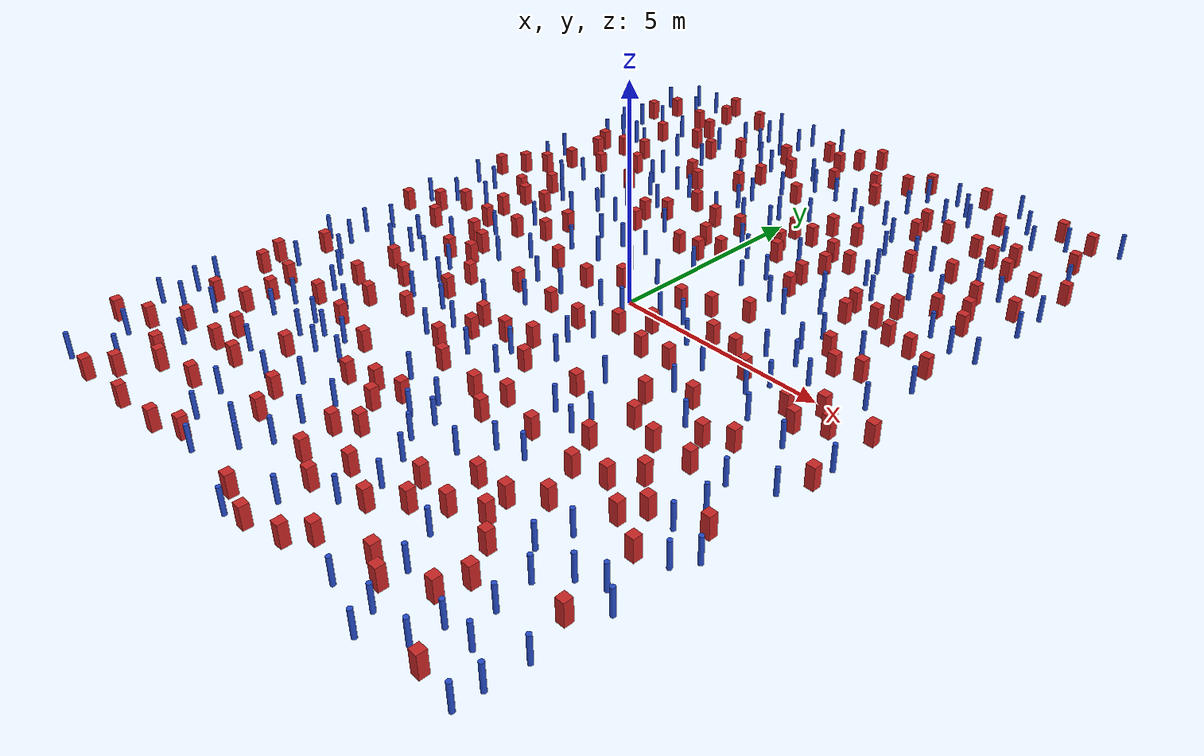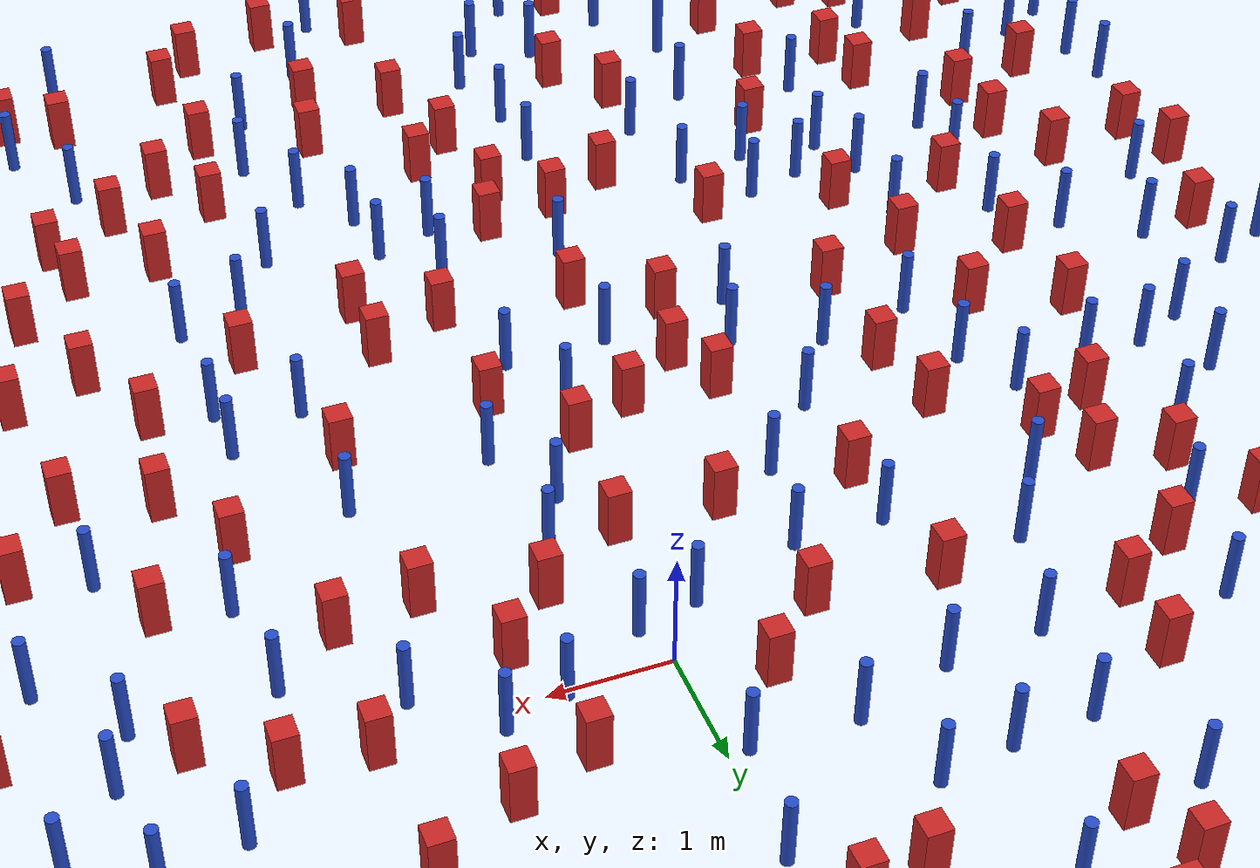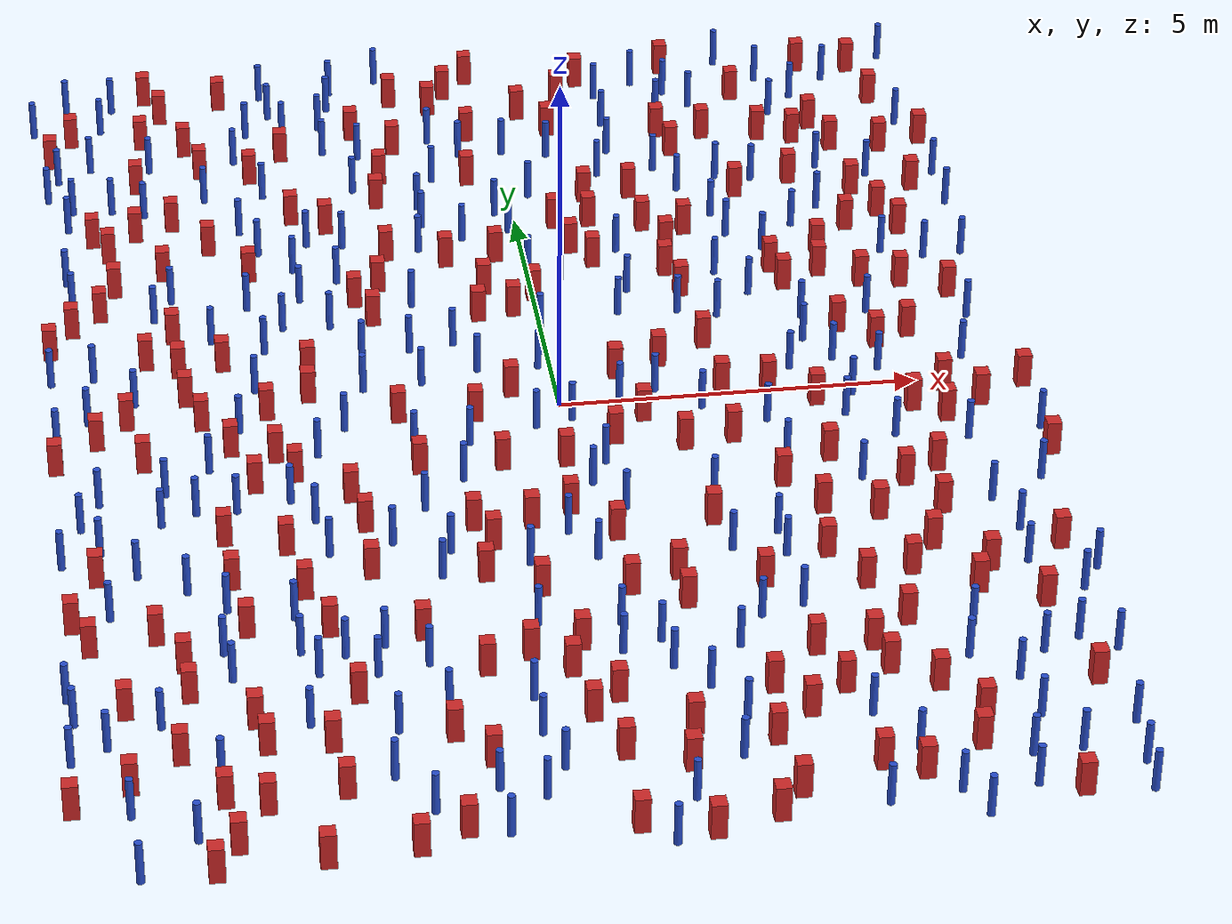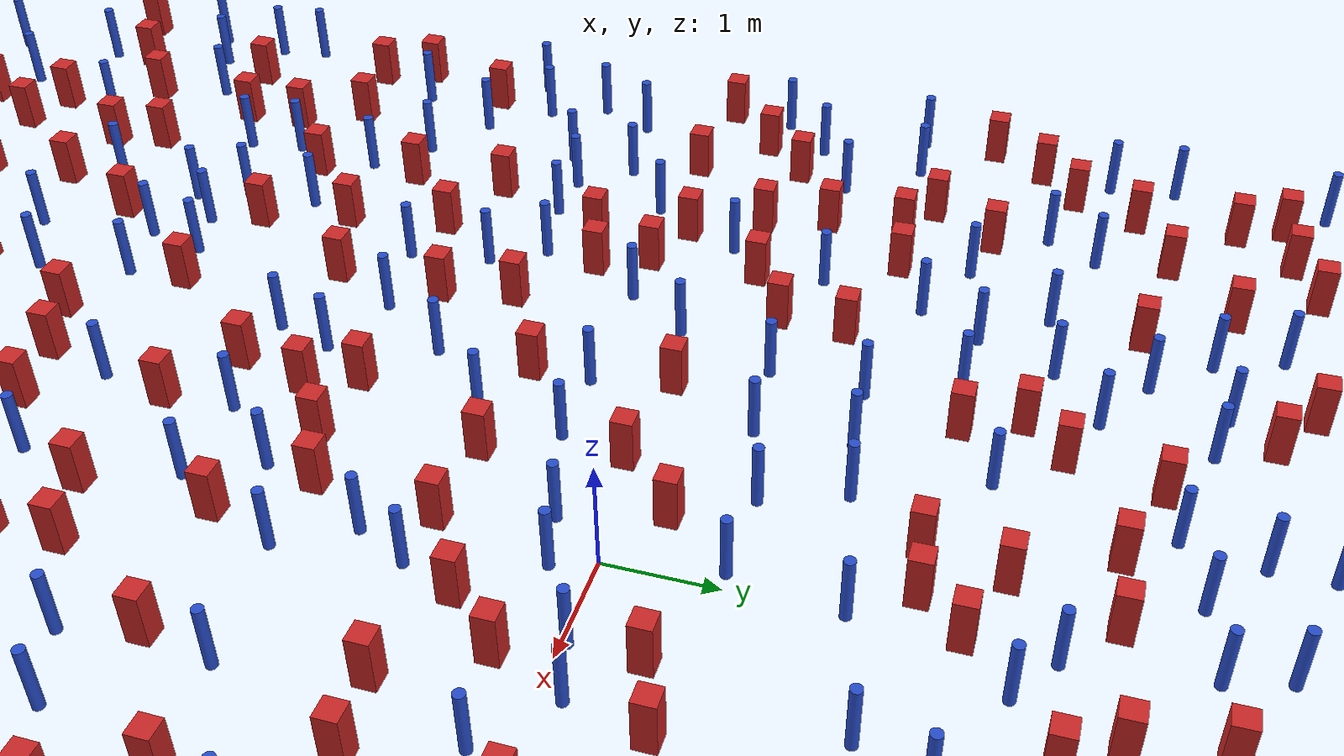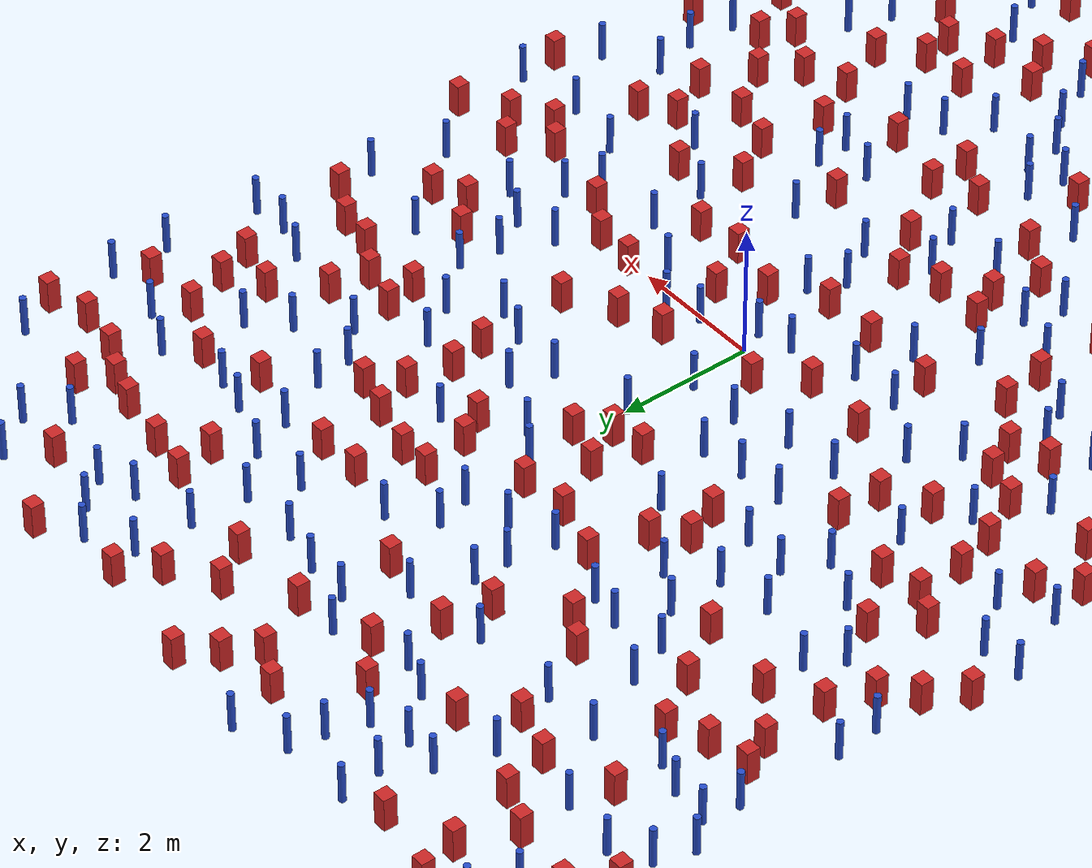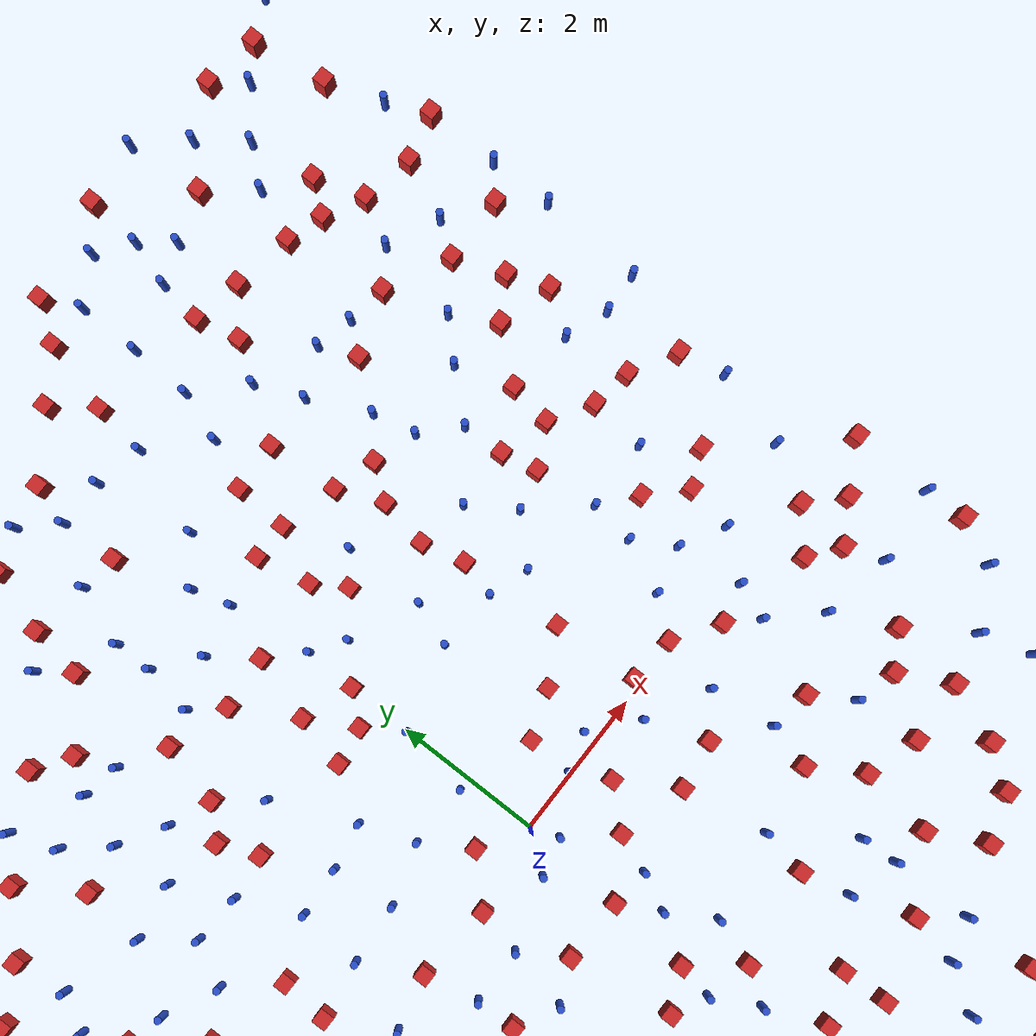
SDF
<sdf version="1.6">
  <model name="dense_75"><model name="pole_obstacle0">
  <static>true</static>
  <pose frame="">5.79565178209 3.24629329432 7.38925637345e-09 -8.47170692798e-08 1.24976764937e-08 -1.74513093023e-07</pose>
  <link name="link">
  <pose frame="">0 0 0.3 0 -0 0</pose>
    <inertial>
      <mass>1</mass>
      <inertia>
        <ixx>0.145833</ixx>
        <ixy>0</ixy>
        <ixz>0</ixz>
        <iyy>0.145833</iyy>
        <iyz>0</iyz>
        <izz>0.125</izz>
      </inertia>
    </inertial>
    <collision name="collision">
      <geometry>
        <cylinder>
          <radius>0.05</radius>
          <length>.6</length>
        </cylinder>
      </geometry>
      <max_contacts>10</max_contacts>
      <surface>
        <contact>
          <ode/>
        </contact>
        <bounce/>
        <friction>
          <torsional>
            <ode/>
          </torsional>
          <ode/>
        </friction>
      </surface>
    </collision>
    <visual name="visual">
      <geometry>
        <cylinder>
          <radius>0.05</radius>
          <length>.6</length>
        </cylinder>
      </geometry>
      <material>
        <script>
          <name>Gazebo/Blue</name>
          <uri>file://media/materials/scripts/gazebo.material</uri>
        </script>
      </material>
    </visual>
    <self_collide>0</self_collide>
    <kinematic>0</kinematic>
  </link>
</model>
<model name="pole_obstacle1">
  <static>true</static>
  <pose frame="">-0.977106564519 -7.90810374782 7.38925637345e-09 -8.47170692799e-08 1.2497676509e-08 -1.74513093015e-07</pose>
  <link name="link">
  <pose frame="">0 0 0.3 0 -0 0</pose>
    <inertial>
      <mass>1</mass>
      <inertia>
        <ixx>0.145833</ixx>
        <ixy>0</ixy>
        <ixz>0</ixz>
        <iyy>0.145833</iyy>
        <iyz>0</iyz>
        <izz>0.125</izz>
      </inertia>
    </inertial>
    <collision name="collision">
      <geometry>
        <cylinder>
          <radius>0.05</radius>
          <length>.6</length>
        </cylinder>
      </geometry>
      <max_contacts>10</max_contacts>
      <surface>
        <contact>
          <ode/>
        </contact>
        <bounce/>
        <friction>
          <torsional>
            <ode/>
          </torsional>
          <ode/>
        </friction>
      </surface>
    </collision>
    <visual name="visual">
      <geometry>
        <cylinder>
          <radius>0.05</radius>
          <length>.6</length>
        </cylinder>
      </geometry>
      <material>
        <script>
          <name>Gazebo/Blue</name>
          <uri>file://media/materials/scripts/gazebo.material</uri>
        </script>
      </material>
    </visual>
    <self_collide>0</self_collide>
    <kinematic>0</kinematic>
  </link>
</model>
<model name="square_post_obstacle0">
  <static>true</static>
  <pose frame="">1.56605751356 -1.20422821467 1.91545236811e-07 -7.35059704564e-06 1.12565212e-07 2.39332434364e-05</pose>
  <link name="link">
    <pose frame="">0 0 0.25 0 -0 0</pose>
    <inertial>
      <mass>100</mass>
      <inertia>
        <ixx>0.166667</ixx>
        <ixy>0</ixy>
        <ixz>0</ixz>
        <iyy>0.166667</iyy>
        <iyz>0</iyz>
        <izz>0.166667</izz>
      </inertia>
    </inertial>
    <collision name="collision">
      <geometry>
        <box>
          <size>.2 .2 .5</size>
        </box>
      </geometry>
      <max_contacts>10</max_contacts>
      <surface>
        <contact>
          <ode/>
        </contact>
        <bounce/>
        <friction>
          <torsional>
            <ode/>
          </torsional>
          <ode/>
        </friction>
      </surface>
    </collision>
    <visual name="visual">
      <geometry>
        <box>
          <size>.2 .2 .5</size>
        </box>
      </geometry>
      <material>
        <script>
          <name>Gazebo/Red</name>
          <uri>file://media/materials/scripts/gazebo.material</uri>
        </script>
      </material>
    </visual>
    <self_collide>0</self_collide>
    <kinematic>0</kinematic>
  </link>
</model>
<model name="square_post_obstacle1">
  <static>true</static>
  <pose frame="">-6.20894556401 5.08491788929 1.91545236811e-07 -7.35059704564e-06 1.12565212e-07 2.39332434364e-05</pose>
  <link name="link">
    <pose frame="">0 0 0.25 0 -0 0</pose>
    <inertial>
      <mass>100</mass>
      <inertia>
        <ixx>0.166667</ixx>
        <ixy>0</ixy>
        <ixz>0</ixz>
        <iyy>0.166667</iyy>
        <iyz>0</iyz>
        <izz>0.166667</izz>
      </inertia>
    </inertial>
    <collision name="collision">
      <geometry>
        <box>
          <size>.2 .2 .5</size>
        </box>
      </geometry>
      <max_contacts>10</max_contacts>
      <surface>
        <contact>
          <ode/>
        </contact>
        <bounce/>
        <friction>
          <torsional>
            <ode/>
          </torsional>
          <ode/>
        </friction>
      </surface>
    </collision>
    <visual name="visual">
      <geometry>
        <box>
          <size>.2 .2 .5</size>
        </box>
      </geometry>
      <material>
        <script>
          <name>Gazebo/Red</name>
          <uri>file://media/materials/scripts/gazebo.material</uri>
        </script>
      </material>
    </visual>
    <self_collide>0</self_collide>
    <kinematic>0</kinematic>
  </link>
</model>
<model name="pole_obstacle2">
  <static>true</static>
  <pose frame="">5.5693059751 -4.40679341141 7.38925637345e-09 -8.47170692796e-08 1.24976764786e-08 -1.74513093032e-07</pose>
  <link name="link">
  <pose frame="">0 0 0.3 0 -0 0</pose>
    <inertial>
      <mass>1</mass>
      <inertia>
        <ixx>0.145833</ixx>
        <ixy>0</ixy>
        <ixz>0</ixz>
        <iyy>0.145833</iyy>
        <iyz>0</iyz>
        <izz>0.125</izz>
      </inertia>
    </inertial>
    <collision name="collision">
      <geometry>
        <cylinder>
          <radius>0.05</radius>
          <length>.6</length>
        </cylinder>
      </geometry>
      <max_contacts>10</max_contacts>
      <surface>
        <contact>
          <ode/>
        </contact>
        <bounce/>
        <friction>
          <torsional>
            <ode/>
          </torsional>
          <ode/>
        </friction>
      </surface>
    </collision>
    <visual name="visual">
      <geometry>
        <cylinder>
          <radius>0.05</radius>
          <length>.6</length>
        </cylinder>
      </geometry>
      <material>
        <script>
          <name>Gazebo/Blue</name>
          <uri>file://media/materials/scripts/gazebo.material</uri>
        </script>
      </material>
    </visual>
    <self_collide>0</self_collide>
    <kinematic>0</kinematic>
  </link>
</model>
<model name="pole_obstacle3">
  <static>true</static>
  <pose frame="">-6.47764836646 9.04078290669 7.38925637345e-09 -8.471706928e-08 1.24976765081e-08 -1.74513093015e-07</pose>
  <link name="link">
  <pose frame="">0 0 0.3 0 -0 0</pose>
    <inertial>
      <mass>1</mass>
      <inertia>
        <ixx>0.145833</ixx>
        <ixy>0</ixy>
        <ixz>0</ixz>
        <iyy>0.145833</iyy>
        <iyz>0</iyz>
        <izz>0.125</izz>
      </inertia>
    </inertial>
    <collision name="collision">
      <geometry>
        <cylinder>
          <radius>0.05</radius>
          <length>.6</length>
        </cylinder>
      </geometry>
      <max_contacts>10</max_contacts>
      <surface>
        <contact>
          <ode/>
        </contact>
        <bounce/>
        <friction>
          <torsional>
            <ode/>
          </torsional>
          <ode/>
        </friction>
      </surface>
    </collision>
    <visual name="visual">
      <geometry>
        <cylinder>
          <radius>0.05</radius>
          <length>.6</length>
        </cylinder>
      </geometry>
      <material>
        <script>
          <name>Gazebo/Blue</name>
          <uri>file://media/materials/scripts/gazebo.material</uri>
        </script>
      </material>
    </visual>
    <self_collide>0</self_collide>
    <kinematic>0</kinematic>
  </link>
</model>
<model name="pole_obstacle4">
  <static>true</static>
  <pose frame="">3.87765196162 -0.706936386413 7.38925637345e-09 -8.471706928e-08 1.24976765177e-08 -1.74513093012e-07</pose>
  <link name="link">
  <pose frame="">0 0 0.3 0 -0 0</pose>
    <inertial>
      <mass>1</mass>
      <inertia>
        <ixx>0.145833</ixx>
        <ixy>0</ixy>
        <ixz>0</ixz>
        <iyy>0.145833</iyy>
        <iyz>0</iyz>
        <izz>0.125</izz>
      </inertia>
    </inertial>
    <collision name="collision">
      <geometry>
        <cylinder>
          <radius>0.05</radius>
          <length>.6</length>
        </cylinder>
      </geometry>
      <max_contacts>10</max_contacts>
      <surface>
        <contact>
          <ode/>
        </contact>
        <bounce/>
        <friction>
          <torsional>
            <ode/>
          </torsional>
          <ode/>
        </friction>
      </surface>
    </collision>
    <visual name="visual">
      <geometry>
        <cylinder>
          <radius>0.05</radius>
          <length>.6</length>
        </cylinder>
      </geometry>
      <material>
        <script>
          <name>Gazebo/Blue</name>
          <uri>file://media/materials/scripts/gazebo.material</uri>
        </script>
      </material>
    </visual>
    <self_collide>0</self_collide>
    <kinematic>0</kinematic>
  </link>
</model>
<model name="pole_obstacle5">
  <static>true</static>
  <pose frame="">1.80005106796 -3.65741169704 7.38925637345e-09 -8.47170692799e-08 1.24976765053e-08 -1.74513093017e-07</pose>
  <link name="link">
  <pose frame="">0 0 0.3 0 -0 0</pose>
    <inertial>
      <mass>1</mass>
      <inertia>
        <ixx>0.145833</ixx>
        <ixy>0</ixy>
        <ixz>0</ixz>
        <iyy>0.145833</iyy>
        <iyz>0</iyz>
        <izz>0.125</izz>
      </inertia>
    </inertial>
    <collision name="collision">
      <geometry>
        <cylinder>
          <radius>0.05</radius>
          <length>.6</length>
        </cylinder>
      </geometry>
      <max_contacts>10</max_contacts>
      <surface>
        <contact>
          <ode/>
        </contact>
        <bounce/>
        <friction>
          <torsional>
            <ode/>
          </torsional>
          <ode/>
        </friction>
      </surface>
    </collision>
    <visual name="visual">
      <geometry>
        <cylinder>
          <radius>0.05</radius>
          <length>.6</length>
        </cylinder>
      </geometry>
      <material>
        <script>
          <name>Gazebo/Blue</name>
          <uri>file://media/materials/scripts/gazebo.material</uri>
        </script>
      </material>
    </visual>
    <self_collide>0</self_collide>
    <kinematic>0</kinematic>
  </link>
</model>
<model name="pole_obstacle6">
  <static>true</static>
  <pose frame="">4.70599011204 -8.35303087441 7.38925637345e-09 -8.471706928e-08 1.24976765081e-08 -1.74513093015e-07</pose>
  <link name="link">
  <pose frame="">0 0 0.3 0 -0 0</pose>
    <inertial>
      <mass>1</mass>
      <inertia>
        <ixx>0.145833</ixx>
        <ixy>0</ixy>
        <ixz>0</ixz>
        <iyy>0.145833</iyy>
        <iyz>0</iyz>
        <izz>0.125</izz>
      </inertia>
    </inertial>
    <collision name="collision">
      <geometry>
        <cylinder>
          <radius>0.05</radius>
          <length>.6</length>
        </cylinder>
      </geometry>
      <max_contacts>10</max_contacts>
      <surface>
        <contact>
          <ode/>
        </contact>
        <bounce/>
        <friction>
          <torsional>
            <ode/>
          </torsional>
          <ode/>
        </friction>
      </surface>
    </collision>
    <visual name="visual">
      <geometry>
        <cylinder>
          <radius>0.05</radius>
          <length>.6</length>
        </cylinder>
      </geometry>
      <material>
        <script>
          <name>Gazebo/Blue</name>
          <uri>file://media/materials/scripts/gazebo.material</uri>
        </script>
      </material>
    </visual>
    <self_collide>0</self_collide>
    <kinematic>0</kinematic>
  </link>
</model>
<model name="square_post_obstacle2">
  <static>true</static>
  <pose frame="">1.98064423771 3.28189115455 1.91545236811e-07 -7.35059704564e-06 1.12565212e-07 2.39332434364e-05</pose>
  <link name="link">
    <pose frame="">0 0 0.25 0 -0 0</pose>
    <inertial>
      <mass>100</mass>
      <inertia>
        <ixx>0.166667</ixx>
        <ixy>0</ixy>
        <ixz>0</ixz>
        <iyy>0.166667</iyy>
        <iyz>0</iyz>
        <izz>0.166667</izz>
      </inertia>
    </inertial>
    <collision name="collision">
      <geometry>
        <box>
          <size>.2 .2 .5</size>
        </box>
      </geometry>
      <max_contacts>10</max_contacts>
      <surface>
        <contact>
          <ode/>
        </contact>
        <bounce/>
        <friction>
          <torsional>
            <ode/>
          </torsional>
          <ode/>
        </friction>
      </surface>
    </collision>
    <visual name="visual">
      <geometry>
        <box>
          <size>.2 .2 .5</size>
        </box>
      </geometry>
      <material>
        <script>
          <name>Gazebo/Red</name>
          <uri>file://media/materials/scripts/gazebo.material</uri>
        </script>
      </material>
    </visual>
    <self_collide>0</self_collide>
    <kinematic>0</kinematic>
  </link>
</model>
<model name="square_post_obstacle3">
  <static>true</static>
  <pose frame="">-0.432793943756 7.54914708848 1.91545236811e-07 -7.35059704564e-06 1.12565212e-07 2.39332434364e-05</pose>
  <link name="link">
    <pose frame="">0 0 0.25 0 -0 0</pose>
    <inertial>
      <mass>100</mass>
      <inertia>
        <ixx>0.166667</ixx>
        <ixy>0</ixy>
        <ixz>0</ixz>
        <iyy>0.166667</iyy>
        <iyz>0</iyz>
        <izz>0.166667</izz>
      </inertia>
    </inertial>
    <collision name="collision">
      <geometry>
        <box>
          <size>.2 .2 .5</size>
        </box>
      </geometry>
      <max_contacts>10</max_contacts>
      <surface>
        <contact>
          <ode/>
        </contact>
        <bounce/>
        <friction>
          <torsional>
            <ode/>
          </torsional>
          <ode/>
        </friction>
      </surface>
    </collision>
    <visual name="visual">
      <geometry>
        <box>
          <size>.2 .2 .5</size>
        </box>
      </geometry>
      <material>
        <script>
          <name>Gazebo/Red</name>
          <uri>file://media/materials/scripts/gazebo.material</uri>
        </script>
      </material>
    </visual>
    <self_collide>0</self_collide>
    <kinematic>0</kinematic>
  </link>
</model>
<model name="square_post_obstacle4">
  <static>true</static>
  <pose frame="">-2.22750226786 -0.0658308857675 1.91545236811e-07 -7.35059704564e-06 1.12565212e-07 2.39332434364e-05</pose>
  <link name="link">
    <pose frame="">0 0 0.25 0 -0 0</pose>
    <inertial>
      <mass>100</mass>
      <inertia>
        <ixx>0.166667</ixx>
        <ixy>0</ixy>
        <ixz>0</ixz>
        <iyy>0.166667</iyy>
        <iyz>0</iyz>
        <izz>0.166667</izz>
      </inertia>
    </inertial>
    <collision name="collision">
      <geometry>
        <box>
          <size>.2 .2 .5</size>
        </box>
      </geometry>
      <max_contacts>10</max_contacts>
      <surface>
        <contact>
          <ode/>
        </contact>
        <bounce/>
        <friction>
          <torsional>
            <ode/>
          </torsional>
          <ode/>
        </friction>
      </surface>
    </collision>
    <visual name="visual">
      <geometry>
        <box>
          <size>.2 .2 .5</size>
        </box>
      </geometry>
      <material>
        <script>
          <name>Gazebo/Red</name>
          <uri>file://media/materials/scripts/gazebo.material</uri>
        </script>
      </material>
    </visual>
    <self_collide>0</self_collide>
    <kinematic>0</kinematic>
  </link>
</model>
<model name="pole_obstacle7">
  <static>true</static>
  <pose frame="">-5.94388062194 -3.34615520025 7.38925637345e-09 -8.47170692798e-08 1.24976764937e-08 -1.74513093023e-07</pose>
  <link name="link">
  <pose frame="">0 0 0.3 0 -0 0</pose>
    <inertial>
      <mass>1</mass>
      <inertia>
        <ixx>0.145833</ixx>
        <ixy>0</ixy>
        <ixz>0</ixz>
        <iyy>0.145833</iyy>
        <iyz>0</iyz>
        <izz>0.125</izz>
      </inertia>
    </inertial>
    <collision name="collision">
      <geometry>
        <cylinder>
          <radius>0.05</radius>
          <length>.6</length>
        </cylinder>
      </geometry>
      <max_contacts>10</max_contacts>
      <surface>
        <contact>
          <ode/>
        </contact>
        <bounce/>
        <friction>
          <torsional>
            <ode/>
          </torsional>
          <ode/>
        </friction>
      </surface>
    </collision>
    <visual name="visual">
      <geometry>
        <cylinder>
          <radius>0.05</radius>
          <length>.6</length>
        </cylinder>
      </geometry>
      <material>
        <script>
          <name>Gazebo/Blue</name>
          <uri>file://media/materials/scripts/gazebo.material</uri>
        </script>
      </material>
    </visual>
    <self_collide>0</self_collide>
    <kinematic>0</kinematic>
  </link>
</model>
<model name="pole_obstacle8">
  <static>true</static>
  <pose frame="">-5.89937046172 5.9574986893 7.38925637345e-09 -8.47170692796e-08 1.24976764786e-08 -1.74513093032e-07</pose>
  <link name="link">
  <pose frame="">0 0 0.3 0 -0 0</pose>
    <inertial>
      <mass>1</mass>
      <inertia>
        <ixx>0.145833</ixx>
        <ixy>0</ixy>
        <ixz>0</ixz>
        <iyy>0.145833</iyy>
        <iyz>0</iyz>
        <izz>0.125</izz>
      </inertia>
    </inertial>
    <collision name="collision">
      <geometry>
        <cylinder>
          <radius>0.05</radius>
          <length>.6</length>
        </cylinder>
      </geometry>
      <max_contacts>10</max_contacts>
      <surface>
        <contact>
          <ode/>
        </contact>
        <bounce/>
        <friction>
          <torsional>
            <ode/>
          </torsional>
          <ode/>
        </friction>
      </surface>
    </collision>
    <visual name="visual">
      <geometry>
        <cylinder>
          <radius>0.05</radius>
          <length>.6</length>
        </cylinder>
      </geometry>
      <material>
        <script>
          <name>Gazebo/Blue</name>
          <uri>file://media/materials/scripts/gazebo.material</uri>
        </script>
      </material>
    </visual>
    <self_collide>0</self_collide>
    <kinematic>0</kinematic>
  </link>
</model>
<model name="square_post_obstacle5">
  <static>true</static>
  <pose frame="">5.84599909969 -6.99812463571 1.91545236811e-07 -7.35059704564e-06 1.12565212e-07 2.39332434364e-05</pose>
  <link name="link">
    <pose frame="">0 0 0.25 0 -0 0</pose>
    <inertial>
      <mass>100</mass>
      <inertia>
        <ixx>0.166667</ixx>
        <ixy>0</ixy>
        <ixz>0</ixz>
        <iyy>0.166667</iyy>
        <iyz>0</iyz>
        <izz>0.166667</izz>
      </inertia>
    </inertial>
    <collision name="collision">
      <geometry>
        <box>
          <size>.2 .2 .5</size>
        </box>
      </geometry>
      <max_contacts>10</max_contacts>
      <surface>
        <contact>
          <ode/>
        </contact>
        <bounce/>
        <friction>
          <torsional>
            <ode/>
          </torsional>
          <ode/>
        </friction>
      </surface>
    </collision>
    <visual name="visual">
      <geometry>
        <box>
          <size>.2 .2 .5</size>
        </box>
      </geometry>
      <material>
        <script>
          <name>Gazebo/Red</name>
          <uri>file://media/materials/scripts/gazebo.material</uri>
        </script>
      </material>
    </visual>
    <self_collide>0</self_collide>
    <kinematic>0</kinematic>
  </link>
</model>
<model name="square_post_obstacle6">
  <static>true</static>
  <pose frame="">-4.73540818238 -3.65907289616 1.91545236811e-07 -7.35059704564e-06 1.12565212e-07 2.39332434364e-05</pose>
  <link name="link">
    <pose frame="">0 0 0.25 0 -0 0</pose>
    <inertial>
      <mass>100</mass>
      <inertia>
        <ixx>0.166667</ixx>
        <ixy>0</ixy>
        <ixz>0</ixz>
        <iyy>0.166667</iyy>
        <iyz>0</iyz>
        <izz>0.166667</izz>
      </inertia>
    </inertial>
    <collision name="collision">
      <geometry>
        <box>
          <size>.2 .2 .5</size>
        </box>
      </geometry>
      <max_contacts>10</max_contacts>
      <surface>
        <contact>
          <ode/>
        </contact>
        <bounce/>
        <friction>
          <torsional>
            <ode/>
          </torsional>
          <ode/>
        </friction>
      </surface>
    </collision>
    <visual name="visual">
      <geometry>
        <box>
          <size>.2 .2 .5</size>
        </box>
      </geometry>
      <material>
        <script>
          <name>Gazebo/Red</name>
          <uri>file://media/materials/scripts/gazebo.material</uri>
        </script>
      </material>
    </visual>
    <self_collide>0</self_collide>
    <kinematic>0</kinematic>
  </link>
</model>
<model name="square_post_obstacle7">
  <static>true</static>
  <pose frame="">3.74116895942 -5.48608894107 1.91545236811e-07 -7.35059704564e-06 1.12565212e-07 2.39332434364e-05</pose>
  <link name="link">
    <pose frame="">0 0 0.25 0 -0 0</pose>
    <inertial>
      <mass>100</mass>
      <inertia>
        <ixx>0.166667</ixx>
        <ixy>0</ixy>
        <ixz>0</ixz>
        <iyy>0.166667</iyy>
        <iyz>0</iyz>
        <izz>0.166667</izz>
      </inertia>
    </inertial>
    <collision name="collision">
      <geometry>
        <box>
          <size>.2 .2 .5</size>
        </box>
      </geometry>
      <max_contacts>10</max_contacts>
      <surface>
        <contact>
          <ode/>
        </contact>
        <bounce/>
        <friction>
          <torsional>
            <ode/>
          </torsional>
          <ode/>
        </friction>
      </surface>
    </collision>
    <visual name="visual">
      <geometry>
        <box>
          <size>.2 .2 .5</size>
        </box>
      </geometry>
      <material>
        <script>
          <name>Gazebo/Red</name>
          <uri>file://media/materials/scripts/gazebo.material</uri>
        </script>
      </material>
    </visual>
    <self_collide>0</self_collide>
    <kinematic>0</kinematic>
  </link>
</model>
<model name="pole_obstacle9">
  <static>true</static>
  <pose frame="">2.92601557178 -7.32535560312 7.38925637345e-09 -8.47170692798e-08 1.24976765033e-08 -1.74513093019e-07</pose>
  <link name="link">
  <pose frame="">0 0 0.3 0 -0 0</pose>
    <inertial>
      <mass>1</mass>
      <inertia>
        <ixx>0.145833</ixx>
        <ixy>0</ixy>
        <ixz>0</ixz>
        <iyy>0.145833</iyy>
        <iyz>0</iyz>
        <izz>0.125</izz>
      </inertia>
    </inertial>
    <collision name="collision">
      <geometry>
        <cylinder>
          <radius>0.05</radius>
          <length>.6</length>
        </cylinder>
      </geometry>
      <max_contacts>10</max_contacts>
      <surface>
        <contact>
          <ode/>
        </contact>
        <bounce/>
        <friction>
          <torsional>
            <ode/>
          </torsional>
          <ode/>
        </friction>
      </surface>
    </collision>
    <visual name="visual">
      <geometry>
        <cylinder>
          <radius>0.05</radius>
          <length>.6</length>
        </cylinder>
      </geometry>
      <material>
        <script>
          <name>Gazebo/Blue</name>
          <uri>file://media/materials/scripts/gazebo.material</uri>
        </script>
      </material>
    </visual>
    <self_collide>0</self_collide>
    <kinematic>0</kinematic>
  </link>
</model>
<model name="pole_obstacle10">
  <static>true</static>
  <pose frame="">6.43006931525 5.59276663731 7.38925637345e-09 -8.47170692796e-08 1.24976764786e-08 -1.74513093032e-07</pose>
  <link name="link">
  <pose frame="">0 0 0.3 0 -0 0</pose>
    <inertial>
      <mass>1</mass>
      <inertia>
        <ixx>0.145833</ixx>
        <ixy>0</ixy>
        <ixz>0</ixz>
        <iyy>0.145833</iyy>
        <iyz>0</iyz>
        <izz>0.125</izz>
      </inertia>
    </inertial>
    <collision name="collision">
      <geometry>
        <cylinder>
          <radius>0.05</radius>
          <length>.6</length>
        </cylinder>
      </geometry>
      <max_contacts>10</max_contacts>
      <surface>
        <contact>
          <ode/>
        </contact>
        <bounce/>
        <friction>
          <torsional>
            <ode/>
          </torsional>
          <ode/>
        </friction>
      </surface>
    </collision>
    <visual name="visual">
      <geometry>
        <cylinder>
          <radius>0.05</radius>
          <length>.6</length>
        </cylinder>
      </geometry>
      <material>
        <script>
          <name>Gazebo/Blue</name>
          <uri>file://media/materials/scripts/gazebo.material</uri>
        </script>
      </material>
    </visual>
    <self_collide>0</self_collide>
    <kinematic>0</kinematic>
  </link>
</model>
<model name="pole_obstacle11">
  <static>true</static>
  <pose frame="">-4.01556916504 7.21280507882 7.38925637345e-09 -8.47170692795e-08 1.24976764731e-08 -1.74513093035e-07</pose>
  <link name="link">
  <pose frame="">0 0 0.3 0 -0 0</pose>
    <inertial>
      <mass>1</mass>
      <inertia>
        <ixx>0.145833</ixx>
        <ixy>0</ixy>
        <ixz>0</ixz>
        <iyy>0.145833</iyy>
        <iyz>0</iyz>
        <izz>0.125</izz>
      </inertia>
    </inertial>
    <collision name="collision">
      <geometry>
        <cylinder>
          <radius>0.05</radius>
          <length>.6</length>
        </cylinder>
      </geometry>
      <max_contacts>10</max_contacts>
      <surface>
        <contact>
          <ode/>
        </contact>
        <bounce/>
        <friction>
          <torsional>
            <ode/>
          </torsional>
          <ode/>
        </friction>
      </surface>
    </collision>
    <visual name="visual">
      <geometry>
        <cylinder>
          <radius>0.05</radius>
          <length>.6</length>
        </cylinder>
      </geometry>
      <material>
        <script>
          <name>Gazebo/Blue</name>
          <uri>file://media/materials/scripts/gazebo.material</uri>
        </script>
      </material>
    </visual>
    <self_collide>0</self_collide>
    <kinematic>0</kinematic>
  </link>
</model>
<model name="pole_obstacle12">
  <static>true</static>
  <pose frame="">6.43960804948 4.71248183484 7.38925637345e-09 -8.47170692796e-08 1.24976764786e-08 -1.74513093032e-07</pose>
  <link name="link">
  <pose frame="">0 0 0.3 0 -0 0</pose>
    <inertial>
      <mass>1</mass>
      <inertia>
        <ixx>0.145833</ixx>
        <ixy>0</ixy>
        <ixz>0</ixz>
        <iyy>0.145833</iyy>
        <iyz>0</iyz>
        <izz>0.125</izz>
      </inertia>
    </inertial>
    <collision name="collision">
      <geometry>
        <cylinder>
          <radius>0.05</radius>
          <length>.6</length>
        </cylinder>
      </geometry>
      <max_contacts>10</max_contacts>
      <surface>
        <contact>
          <ode/>
        </contact>
        <bounce/>
        <friction>
          <torsional>
            <ode/>
          </torsional>
          <ode/>
        </friction>
      </surface>
    </collision>
    <visual name="visual">
      <geometry>
        <cylinder>
          <radius>0.05</radius>
          <length>.6</length>
        </cylinder>
      </geometry>
      <material>
        <script>
          <name>Gazebo/Blue</name>
          <uri>file://media/materials/scripts/gazebo.material</uri>
        </script>
      </material>
    </visual>
    <self_collide>0</self_collide>
    <kinematic>0</kinematic>
  </link>
</model>
<model name="square_post_obstacle8">
  <static>true</static>
  <pose frame="">-2.33978747263 2.45094389933 1.91545236811e-07 -7.35059704564e-06 1.12565212e-07 2.39332434364e-05</pose>
  <link name="link">
    <pose frame="">0 0 0.25 0 -0 0</pose>
    <inertial>
      <mass>100</mass>
      <inertia>
        <ixx>0.166667</ixx>
        <ixy>0</ixy>
        <ixz>0</ixz>
        <iyy>0.166667</iyy>
        <iyz>0</iyz>
        <izz>0.166667</izz>
      </inertia>
    </inertial>
    <collision name="collision">
      <geometry>
        <box>
          <size>.2 .2 .5</size>
        </box>
      </geometry>
      <max_contacts>10</max_contacts>
      <surface>
        <contact>
          <ode/>
        </contact>
        <bounce/>
        <friction>
          <torsional>
            <ode/>
          </torsional>
          <ode/>
        </friction>
      </surface>
    </collision>
    <visual name="visual">
      <geometry>
        <box>
          <size>.2 .2 .5</size>
        </box>
      </geometry>
      <material>
        <script>
          <name>Gazebo/Red</name>
          <uri>file://media/materials/scripts/gazebo.material</uri>
        </script>
      </material>
    </visual>
    <self_collide>0</self_collide>
    <kinematic>0</kinematic>
  </link>
</model>
<model name="square_post_obstacle9">
  <static>true</static>
  <pose frame="">1.453826613 -9.14333168105 1.91545236811e-07 -7.35059704564e-06 1.12565212e-07 2.39332434364e-05</pose>
  <link name="link">
    <pose frame="">0 0 0.25 0 -0 0</pose>
    <inertial>
      <mass>100</mass>
      <inertia>
        <ixx>0.166667</ixx>
        <ixy>0</ixy>
        <ixz>0</ixz>
        <iyy>0.166667</iyy>
        <iyz>0</iyz>
        <izz>0.166667</izz>
      </inertia>
    </inertial>
    <collision name="collision">
      <geometry>
        <box>
          <size>.2 .2 .5</size>
        </box>
      </geometry>
      <max_contacts>10</max_contacts>
      <surface>
        <contact>
          <ode/>
        </contact>
        <bounce/>
        <friction>
          <torsional>
            <ode/>
          </torsional>
          <ode/>
        </friction>
      </surface>
    </collision>
    <visual name="visual">
      <geometry>
        <box>
          <size>.2 .2 .5</size>
        </box>
      </geometry>
      <material>
        <script>
          <name>Gazebo/Red</name>
          <uri>file://media/materials/scripts/gazebo.material</uri>
        </script>
      </material>
    </visual>
    <self_collide>0</self_collide>
    <kinematic>0</kinematic>
  </link>
</model>
<model name="pole_obstacle13">
  <static>true</static>
  <pose frame="">0.557342866463 -2.55776858749 7.38925637345e-09 -8.47170692799e-08 1.2497676509e-08 -1.74513093016e-07</pose>
  <link name="link">
  <pose frame="">0 0 0.3 0 -0 0</pose>
    <inertial>
      <mass>1</mass>
      <inertia>
        <ixx>0.145833</ixx>
        <ixy>0</ixy>
        <ixz>0</ixz>
        <iyy>0.145833</iyy>
        <iyz>0</iyz>
        <izz>0.125</izz>
      </inertia>
    </inertial>
    <collision name="collision">
      <geometry>
        <cylinder>
          <radius>0.05</radius>
          <length>.6</length>
        </cylinder>
      </geometry>
      <max_contacts>10</max_contacts>
      <surface>
        <contact>
          <ode/>
        </contact>
        <bounce/>
        <friction>
          <torsional>
            <ode/>
          </torsional>
          <ode/>
        </friction>
      </surface>
    </collision>
    <visual name="visual">
      <geometry>
        <cylinder>
          <radius>0.05</radius>
          <length>.6</length>
        </cylinder>
      </geometry>
      <material>
        <script>
          <name>Gazebo/Blue</name>
          <uri>file://media/materials/scripts/gazebo.material</uri>
        </script>
      </material>
    </visual>
    <self_collide>0</self_collide>
    <kinematic>0</kinematic>
  </link>
</model>
<model name="square_post_obstacle10">
  <static>true</static>
  <pose frame="">-6.81502577648 -4.3608636634 1.91545236811e-07 -7.35059704564e-06 1.12565212e-07 2.39332434364e-05</pose>
  <link name="link">
    <pose frame="">0 0 0.25 0 -0 0</pose>
    <inertial>
      <mass>100</mass>
      <inertia>
        <ixx>0.166667</ixx>
        <ixy>0</ixy>
        <ixz>0</ixz>
        <iyy>0.166667</iyy>
        <iyz>0</iyz>
        <izz>0.166667</izz>
      </inertia>
    </inertial>
    <collision name="collision">
      <geometry>
        <box>
          <size>.2 .2 .5</size>
        </box>
      </geometry>
      <max_contacts>10</max_contacts>
      <surface>
        <contact>
          <ode/>
        </contact>
        <bounce/>
        <friction>
          <torsional>
            <ode/>
          </torsional>
          <ode/>
        </friction>
      </surface>
    </collision>
    <visual name="visual">
      <geometry>
        <box>
          <size>.2 .2 .5</size>
        </box>
      </geometry>
      <material>
        <script>
          <name>Gazebo/Red</name>
          <uri>file://media/materials/scripts/gazebo.material</uri>
        </script>
      </material>
    </visual>
    <self_collide>0</self_collide>
    <kinematic>0</kinematic>
  </link>
</model>
<model name="square_post_obstacle11">
  <static>true</static>
  <pose frame="">-2.06487871892 -1.3372170114 1.91545236811e-07 -7.35059704564e-06 1.12565212e-07 2.39332434364e-05</pose>
  <link name="link">
    <pose frame="">0 0 0.25 0 -0 0</pose>
    <inertial>
      <mass>100</mass>
      <inertia>
        <ixx>0.166667</ixx>
        <ixy>0</ixy>
        <ixz>0</ixz>
        <iyy>0.166667</iyy>
        <iyz>0</iyz>
        <izz>0.166667</izz>
      </inertia>
    </inertial>
    <collision name="collision">
      <geometry>
        <box>
          <size>.2 .2 .5</size>
        </box>
      </geometry>
      <max_contacts>10</max_contacts>
      <surface>
        <contact>
          <ode/>
        </contact>
        <bounce/>
        <friction>
          <torsional>
            <ode/>
          </torsional>
          <ode/>
        </friction>
      </surface>
    </collision>
    <visual name="visual">
      <geometry>
        <box>
          <size>.2 .2 .5</size>
        </box>
      </geometry>
      <material>
        <script>
          <name>Gazebo/Red</name>
          <uri>file://media/materials/scripts/gazebo.material</uri>
        </script>
      </material>
    </visual>
    <self_collide>0</self_collide>
    <kinematic>0</kinematic>
  </link>
</model>
<model name="pole_obstacle14">
  <static>true</static>
  <pose frame="">2.77887559729 -0.727295282629 7.38925637345e-09 -8.471706928e-08 1.24976765177e-08 -1.74513093012e-07</pose>
  <link name="link">
  <pose frame="">0 0 0.3 0 -0 0</pose>
    <inertial>
      <mass>1</mass>
      <inertia>
        <ixx>0.145833</ixx>
        <ixy>0</ixy>
        <ixz>0</ixz>
        <iyy>0.145833</iyy>
        <iyz>0</iyz>
        <izz>0.125</izz>
      </inertia>
    </inertial>
    <collision name="collision">
      <geometry>
        <cylinder>
          <radius>0.05</radius>
          <length>.6</length>
        </cylinder>
      </geometry>
      <max_contacts>10</max_contacts>
      <surface>
        <contact>
          <ode/>
        </contact>
        <bounce/>
        <friction>
          <torsional>
            <ode/>
          </torsional>
          <ode/>
        </friction>
      </surface>
    </collision>
    <visual name="visual">
      <geometry>
        <cylinder>
          <radius>0.05</radius>
          <length>.6</length>
        </cylinder>
      </geometry>
      <material>
        <script>
          <name>Gazebo/Blue</name>
          <uri>file://media/materials/scripts/gazebo.material</uri>
        </script>
      </material>
    </visual>
    <self_collide>0</self_collide>
    <kinematic>0</kinematic>
  </link>
</model>
<model name="pole_obstacle15">
  <static>true</static>
  <pose frame="">-0.00549938469334 1.96665930927 7.38925637345e-09 -8.471706928e-08 1.24976765085e-08 -1.74513093015e-07</pose>
  <link name="link">
  <pose frame="">0 0 0.3 0 -0 0</pose>
    <inertial>
      <mass>1</mass>
      <inertia>
        <ixx>0.145833</ixx>
        <ixy>0</ixy>
        <ixz>0</ixz>
        <iyy>0.145833</iyy>
        <iyz>0</iyz>
        <izz>0.125</izz>
      </inertia>
    </inertial>
    <collision name="collision">
      <geometry>
        <cylinder>
          <radius>0.05</radius>
          <length>.6</length>
        </cylinder>
      </geometry>
      <max_contacts>10</max_contacts>
      <surface>
        <contact>
          <ode/>
        </contact>
        <bounce/>
        <friction>
          <torsional>
            <ode/>
          </torsional>
          <ode/>
        </friction>
      </surface>
    </collision>
    <visual name="visual">
      <geometry>
        <cylinder>
          <radius>0.05</radius>
          <length>.6</length>
        </cylinder>
      </geometry>
      <material>
        <script>
          <name>Gazebo/Blue</name>
          <uri>file://media/materials/scripts/gazebo.material</uri>
        </script>
      </material>
    </visual>
    <self_collide>0</self_collide>
    <kinematic>0</kinematic>
  </link>
</model>
<model name="square_post_obstacle12">
  <static>true</static>
  <pose frame="">0.342677569145 -3.17985006614 1.91545236811e-07 -7.35059704564e-06 1.12565212e-07 2.39332434364e-05</pose>
  <link name="link">
    <pose frame="">0 0 0.25 0 -0 0</pose>
    <inertial>
      <mass>100</mass>
      <inertia>
        <ixx>0.166667</ixx>
        <ixy>0</ixy>
        <ixz>0</ixz>
        <iyy>0.166667</iyy>
        <iyz>0</iyz>
        <izz>0.166667</izz>
      </inertia>
    </inertial>
    <collision name="collision">
      <geometry>
        <box>
          <size>.2 .2 .5</size>
        </box>
      </geometry>
      <max_contacts>10</max_contacts>
      <surface>
        <contact>
          <ode/>
        </contact>
        <bounce/>
        <friction>
          <torsional>
            <ode/>
          </torsional>
          <ode/>
        </friction>
      </surface>
    </collision>
    <visual name="visual">
      <geometry>
        <box>
          <size>.2 .2 .5</size>
        </box>
      </geometry>
      <material>
        <script>
          <name>Gazebo/Red</name>
          <uri>file://media/materials/scripts/gazebo.material</uri>
        </script>
      </material>
    </visual>
    <self_collide>0</self_collide>
    <kinematic>0</kinematic>
  </link>
</model>
<model name="pole_obstacle16">
  <static>true</static>
  <pose frame="">2.56210407748 7.94373659365 7.38925637345e-09 -8.47170692798e-08 1.24976765033e-08 -1.74513093019e-07</pose>
  <link name="link">
  <pose frame="">0 0 0.3 0 -0 0</pose>
    <inertial>
      <mass>1</mass>
      <inertia>
        <ixx>0.145833</ixx>
        <ixy>0</ixy>
        <ixz>0</ixz>
        <iyy>0.145833</iyy>
        <iyz>0</iyz>
        <izz>0.125</izz>
      </inertia>
    </inertial>
    <collision name="collision">
      <geometry>
        <cylinder>
          <radius>0.05</radius>
          <length>.6</length>
        </cylinder>
      </geometry>
      <max_contacts>10</max_contacts>
      <surface>
        <contact>
          <ode/>
        </contact>
        <bounce/>
        <friction>
          <torsional>
            <ode/>
          </torsional>
          <ode/>
        </friction>
      </surface>
    </collision>
    <visual name="visual">
      <geometry>
        <cylinder>
          <radius>0.05</radius>
          <length>.6</length>
        </cylinder>
      </geometry>
      <material>
        <script>
          <name>Gazebo/Blue</name>
          <uri>file://media/materials/scripts/gazebo.material</uri>
        </script>
      </material>
    </visual>
    <self_collide>0</self_collide>
    <kinematic>0</kinematic>
  </link>
</model>
<model name="pole_obstacle17">
  <static>true</static>
  <pose frame="">3.67841027492 5.769085031 7.38925637345e-09 -8.47170692798e-08 1.24976765033e-08 -1.74513093019e-07</pose>
  <link name="link">
  <pose frame="">0 0 0.3 0 -0 0</pose>
    <inertial>
      <mass>1</mass>
      <inertia>
        <ixx>0.145833</ixx>
        <ixy>0</ixy>
        <ixz>0</ixz>
        <iyy>0.145833</iyy>
        <iyz>0</iyz>
        <izz>0.125</izz>
      </inertia>
    </inertial>
    <collision name="collision">
      <geometry>
        <cylinder>
          <radius>0.05</radius>
          <length>.6</length>
        </cylinder>
      </geometry>
      <max_contacts>10</max_contacts>
      <surface>
        <contact>
          <ode/>
        </contact>
        <bounce/>
        <friction>
          <torsional>
            <ode/>
          </torsional>
          <ode/>
        </friction>
      </surface>
    </collision>
    <visual name="visual">
      <geometry>
        <cylinder>
          <radius>0.05</radius>
          <length>.6</length>
        </cylinder>
      </geometry>
      <material>
        <script>
          <name>Gazebo/Blue</name>
          <uri>file://media/materials/scripts/gazebo.material</uri>
        </script>
      </material>
    </visual>
    <self_collide>0</self_collide>
    <kinematic>0</kinematic>
  </link>
</model>
<model name="square_post_obstacle13">
  <static>true</static>
  <pose frame="">2.60032660815 6.71405022309 1.91545236811e-07 -7.35059704564e-06 1.12565212e-07 2.39332434364e-05</pose>
  <link name="link">
    <pose frame="">0 0 0.25 0 -0 0</pose>
    <inertial>
      <mass>100</mass>
      <inertia>
        <ixx>0.166667</ixx>
        <ixy>0</ixy>
        <ixz>0</ixz>
        <iyy>0.166667</iyy>
        <iyz>0</iyz>
        <izz>0.166667</izz>
      </inertia>
    </inertial>
    <collision name="collision">
      <geometry>
        <box>
          <size>.2 .2 .5</size>
        </box>
      </geometry>
      <max_contacts>10</max_contacts>
      <surface>
        <contact>
          <ode/>
        </contact>
        <bounce/>
        <friction>
          <torsional>
            <ode/>
          </torsional>
          <ode/>
        </friction>
      </surface>
    </collision>
    <visual name="visual">
      <geometry>
        <box>
          <size>.2 .2 .5</size>
        </box>
      </geometry>
      <material>
        <script>
          <name>Gazebo/Red</name>
          <uri>file://media/materials/scripts/gazebo.material</uri>
        </script>
      </material>
    </visual>
    <self_collide>0</self_collide>
    <kinematic>0</kinematic>
  </link>
</model>
<model name="pole_obstacle18">
  <static>true</static>
  <pose frame="">-0.269620902724 5.22114954407 7.38925637345e-09 -8.47170692799e-08 1.24976765096e-08 -1.74513093014e-07</pose>
  <link name="link">
  <pose frame="">0 0 0.3 0 -0 0</pose>
    <inertial>
      <mass>1</mass>
      <inertia>
        <ixx>0.145833</ixx>
        <ixy>0</ixy>
        <ixz>0</ixz>
        <iyy>0.145833</iyy>
        <iyz>0</iyz>
        <izz>0.125</izz>
      </inertia>
    </inertial>
    <collision name="collision">
      <geometry>
        <cylinder>
          <radius>0.05</radius>
          <length>.6</length>
        </cylinder>
      </geometry>
      <max_contacts>10</max_contacts>
      <surface>
        <contact>
          <ode/>
        </contact>
        <bounce/>
        <friction>
          <torsional>
            <ode/>
          </torsional>
          <ode/>
        </friction>
      </surface>
    </collision>
    <visual name="visual">
      <geometry>
        <cylinder>
          <radius>0.05</radius>
          <length>.6</length>
        </cylinder>
      </geometry>
      <material>
        <script>
          <name>Gazebo/Blue</name>
          <uri>file://media/materials/scripts/gazebo.material</uri>
        </script>
      </material>
    </visual>
    <self_collide>0</self_collide>
    <kinematic>0</kinematic>
  </link>
</model>
<model name="square_post_obstacle14">
  <static>true</static>
  <pose frame="">-0.260426917664 9.33828999109 1.91545236811e-07 -7.35059704564e-06 1.12565212e-07 2.39332434364e-05</pose>
  <link name="link">
    <pose frame="">0 0 0.25 0 -0 0</pose>
    <inertial>
      <mass>100</mass>
      <inertia>
        <ixx>0.166667</ixx>
        <ixy>0</ixy>
        <ixz>0</ixz>
        <iyy>0.166667</iyy>
        <iyz>0</iyz>
        <izz>0.166667</izz>
      </inertia>
    </inertial>
    <collision name="collision">
      <geometry>
        <box>
          <size>.2 .2 .5</size>
        </box>
      </geometry>
      <max_contacts>10</max_contacts>
      <surface>
        <contact>
          <ode/>
        </contact>
        <bounce/>
        <friction>
          <torsional>
            <ode/>
          </torsional>
          <ode/>
        </friction>
      </surface>
    </collision>
    <visual name="visual">
      <geometry>
        <box>
          <size>.2 .2 .5</size>
        </box>
      </geometry>
      <material>
        <script>
          <name>Gazebo/Red</name>
          <uri>file://media/materials/scripts/gazebo.material</uri>
        </script>
      </material>
    </visual>
    <self_collide>0</self_collide>
    <kinematic>0</kinematic>
  </link>
</model>
<model name="pole_obstacle19">
  <static>true</static>
  <pose frame="">-2.98141069611 -0.236234702678 7.38925637345e-09 -8.47170692793e-08 1.24976764426e-08 -1.74513093041e-07</pose>
  <link name="link">
  <pose frame="">0 0 0.3 0 -0 0</pose>
    <inertial>
      <mass>1</mass>
      <inertia>
        <ixx>0.145833</ixx>
        <ixy>0</ixy>
        <ixz>0</ixz>
        <iyy>0.145833</iyy>
        <iyz>0</iyz>
        <izz>0.125</izz>
      </inertia>
    </inertial>
    <collision name="collision">
      <geometry>
        <cylinder>
          <radius>0.05</radius>
          <length>.6</length>
        </cylinder>
      </geometry>
      <max_contacts>10</max_contacts>
      <surface>
        <contact>
          <ode/>
        </contact>
        <bounce/>
        <friction>
          <torsional>
            <ode/>
          </torsional>
          <ode/>
        </friction>
      </surface>
    </collision>
    <visual name="visual">
      <geometry>
        <cylinder>
          <radius>0.05</radius>
          <length>.6</length>
        </cylinder>
      </geometry>
      <material>
        <script>
          <name>Gazebo/Blue</name>
          <uri>file://media/materials/scripts/gazebo.material</uri>
        </script>
      </material>
    </visual>
    <self_collide>0</self_collide>
    <kinematic>0</kinematic>
  </link>
</model>
<model name="square_post_obstacle15">
  <static>true</static>
  <pose frame="">-3.41333469753 0.588921729999 1.91545236811e-07 -7.35059704564e-06 1.12565212e-07 2.39332434364e-05</pose>
  <link name="link">
    <pose frame="">0 0 0.25 0 -0 0</pose>
    <inertial>
      <mass>100</mass>
      <inertia>
        <ixx>0.166667</ixx>
        <ixy>0</ixy>
        <ixz>0</ixz>
        <iyy>0.166667</iyy>
        <iyz>0</iyz>
        <izz>0.166667</izz>
      </inertia>
    </inertial>
    <collision name="collision">
      <geometry>
        <box>
          <size>.2 .2 .5</size>
        </box>
      </geometry>
      <max_contacts>10</max_contacts>
      <surface>
        <contact>
          <ode/>
        </contact>
        <bounce/>
        <friction>
          <torsional>
            <ode/>
          </torsional>
          <ode/>
        </friction>
      </surface>
    </collision>
    <visual name="visual">
      <geometry>
        <box>
          <size>.2 .2 .5</size>
        </box>
      </geometry>
      <material>
        <script>
          <name>Gazebo/Red</name>
          <uri>file://media/materials/scripts/gazebo.material</uri>
        </script>
      </material>
    </visual>
    <self_collide>0</self_collide>
    <kinematic>0</kinematic>
  </link>
</model>
<model name="square_post_obstacle16">
  <static>true</static>
  <pose frame="">1.10032722098 5.52364395335 1.91545236811e-07 -7.35059704564e-06 1.12565212e-07 2.39332434364e-05</pose>
  <link name="link">
    <pose frame="">0 0 0.25 0 -0 0</pose>
    <inertial>
      <mass>100</mass>
      <inertia>
        <ixx>0.166667</ixx>
        <ixy>0</ixy>
        <ixz>0</ixz>
        <iyy>0.166667</iyy>
        <iyz>0</iyz>
        <izz>0.166667</izz>
      </inertia>
    </inertial>
    <collision name="collision">
      <geometry>
        <box>
          <size>.2 .2 .5</size>
        </box>
      </geometry>
      <max_contacts>10</max_contacts>
      <surface>
        <contact>
          <ode/>
        </contact>
        <bounce/>
        <friction>
          <torsional>
            <ode/>
          </torsional>
          <ode/>
        </friction>
      </surface>
    </collision>
    <visual name="visual">
      <geometry>
        <box>
          <size>.2 .2 .5</size>
        </box>
      </geometry>
      <material>
        <script>
          <name>Gazebo/Red</name>
          <uri>file://media/materials/scripts/gazebo.material</uri>
        </script>
      </material>
    </visual>
    <self_collide>0</self_collide>
    <kinematic>0</kinematic>
  </link>
</model>
<model name="square_post_obstacle17">
  <static>true</static>
  <pose frame="">5.35984486681 4.55833261002 1.91545236811e-07 -7.35059704564e-06 1.12565212e-07 2.39332434364e-05</pose>
  <link name="link">
    <pose frame="">0 0 0.25 0 -0 0</pose>
    <inertial>
      <mass>100</mass>
      <inertia>
        <ixx>0.166667</ixx>
        <ixy>0</ixy>
        <ixz>0</ixz>
        <iyy>0.166667</iyy>
        <iyz>0</iyz>
        <izz>0.166667</izz>
      </inertia>
    </inertial>
    <collision name="collision">
      <geometry>
        <box>
          <size>.2 .2 .5</size>
        </box>
      </geometry>
      <max_contacts>10</max_contacts>
      <surface>
        <contact>
          <ode/>
        </contact>
        <bounce/>
        <friction>
          <torsional>
            <ode/>
          </torsional>
          <ode/>
        </friction>
      </surface>
    </collision>
    <visual name="visual">
      <geometry>
        <box>
          <size>.2 .2 .5</size>
        </box>
      </geometry>
      <material>
        <script>
          <name>Gazebo/Red</name>
          <uri>file://media/materials/scripts/gazebo.material</uri>
        </script>
      </material>
    </visual>
    <self_collide>0</self_collide>
    <kinematic>0</kinematic>
  </link>
</model>
<model name="pole_obstacle20">
  <static>true</static>
  <pose frame="">-1.66863566471 9.47693834386 7.38925637345e-09 -8.47170692798e-08 1.24976764881e-08 -1.74513093027e-07</pose>
  <link name="link">
  <pose frame="">0 0 0.3 0 -0 0</pose>
    <inertial>
      <mass>1</mass>
      <inertia>
        <ixx>0.145833</ixx>
        <ixy>0</ixy>
        <ixz>0</ixz>
        <iyy>0.145833</iyy>
        <iyz>0</iyz>
        <izz>0.125</izz>
      </inertia>
    </inertial>
    <collision name="collision">
      <geometry>
        <cylinder>
          <radius>0.05</radius>
          <length>.6</length>
        </cylinder>
      </geometry>
      <max_contacts>10</max_contacts>
      <surface>
        <contact>
          <ode/>
        </contact>
        <bounce/>
        <friction>
          <torsional>
            <ode/>
          </torsional>
          <ode/>
        </friction>
      </surface>
    </collision>
    <visual name="visual">
      <geometry>
        <cylinder>
          <radius>0.05</radius>
          <length>.6</length>
        </cylinder>
      </geometry>
      <material>
        <script>
          <name>Gazebo/Blue</name>
          <uri>file://media/materials/scripts/gazebo.material</uri>
        </script>
      </material>
    </visual>
    <self_collide>0</self_collide>
    <kinematic>0</kinematic>
  </link>
</model>
<model name="pole_obstacle21">
  <static>true</static>
  <pose frame="">0.0212298474387 3.55706874163 7.38925637345e-09 -8.471706928e-08 1.24976765089e-08 -1.74513093014e-07</pose>
  <link name="link">
  <pose frame="">0 0 0.3 0 -0 0</pose>
    <inertial>
      <mass>1</mass>
      <inertia>
        <ixx>0.145833</ixx>
        <ixy>0</ixy>
        <ixz>0</ixz>
        <iyy>0.145833</iyy>
        <iyz>0</iyz>
        <izz>0.125</izz>
      </inertia>
    </inertial>
    <collision name="collision">
      <geometry>
        <cylinder>
          <radius>0.05</radius>
          <length>.6</length>
        </cylinder>
      </geometry>
      <max_contacts>10</max_contacts>
      <surface>
        <contact>
          <ode/>
        </contact>
        <bounce/>
        <friction>
          <torsional>
            <ode/>
          </torsional>
          <ode/>
        </friction>
      </surface>
    </collision>
    <visual name="visual">
      <geometry>
        <cylinder>
          <radius>0.05</radius>
          <length>.6</length>
        </cylinder>
      </geometry>
      <material>
        <script>
          <name>Gazebo/Blue</name>
          <uri>file://media/materials/scripts/gazebo.material</uri>
        </script>
      </material>
    </visual>
    <self_collide>0</self_collide>
    <kinematic>0</kinematic>
  </link>
</model>
<model name="pole_obstacle22">
  <static>true</static>
  <pose frame="">5.41686952572 -2.97024607417 7.38925637345e-09 -8.47170692798e-08 1.24976764937e-08 -1.74513093023e-07</pose>
  <link name="link">
  <pose frame="">0 0 0.3 0 -0 0</pose>
    <inertial>
      <mass>1</mass>
      <inertia>
        <ixx>0.145833</ixx>
        <ixy>0</ixy>
        <ixz>0</ixz>
        <iyy>0.145833</iyy>
        <iyz>0</iyz>
        <izz>0.125</izz>
      </inertia>
    </inertial>
    <collision name="collision">
      <geometry>
        <cylinder>
          <radius>0.05</radius>
          <length>.6</length>
        </cylinder>
      </geometry>
      <max_contacts>10</max_contacts>
      <surface>
        <contact>
          <ode/>
        </contact>
        <bounce/>
        <friction>
          <torsional>
            <ode/>
          </torsional>
          <ode/>
        </friction>
      </surface>
    </collision>
    <visual name="visual">
      <geometry>
        <cylinder>
          <radius>0.05</radius>
          <length>.6</length>
        </cylinder>
      </geometry>
      <material>
        <script>
          <name>Gazebo/Blue</name>
          <uri>file://media/materials/scripts/gazebo.material</uri>
        </script>
      </material>
    </visual>
    <self_collide>0</self_collide>
    <kinematic>0</kinematic>
  </link>
</model>
<model name="pole_obstacle23">
  <static>true</static>
  <pose frame="">-1.17780498482 -6.50733422358 7.38925637345e-09 -8.47170692799e-08 1.24976765033e-08 -1.74513093018e-07</pose>
  <link name="link">
  <pose frame="">0 0 0.3 0 -0 0</pose>
    <inertial>
      <mass>1</mass>
      <inertia>
        <ixx>0.145833</ixx>
        <ixy>0</ixy>
        <ixz>0</ixz>
        <iyy>0.145833</iyy>
        <iyz>0</iyz>
        <izz>0.125</izz>
      </inertia>
    </inertial>
    <collision name="collision">
      <geometry>
        <cylinder>
          <radius>0.05</radius>
          <length>.6</length>
        </cylinder>
      </geometry>
      <max_contacts>10</max_contacts>
      <surface>
        <contact>
          <ode/>
        </contact>
        <bounce/>
        <friction>
          <torsional>
            <ode/>
          </torsional>
          <ode/>
        </friction>
      </surface>
    </collision>
    <visual name="visual">
      <geometry>
        <cylinder>
          <radius>0.05</radius>
          <length>.6</length>
        </cylinder>
      </geometry>
      <material>
        <script>
          <name>Gazebo/Blue</name>
          <uri>file://media/materials/scripts/gazebo.material</uri>
        </script>
      </material>
    </visual>
    <self_collide>0</self_collide>
    <kinematic>0</kinematic>
  </link>
</model>
<model name="square_post_obstacle18">
  <static>true</static>
  <pose frame="">-0.133258296363 -6.60814210632 1.91545236811e-07 -7.35059704564e-06 1.12565212e-07 2.39332434364e-05</pose>
  <link name="link">
    <pose frame="">0 0 0.25 0 -0 0</pose>
    <inertial>
      <mass>100</mass>
      <inertia>
        <ixx>0.166667</ixx>
        <ixy>0</ixy>
        <ixz>0</ixz>
        <iyy>0.166667</iyy>
        <iyz>0</iyz>
        <izz>0.166667</izz>
      </inertia>
    </inertial>
    <collision name="collision">
      <geometry>
        <box>
          <size>.2 .2 .5</size>
        </box>
      </geometry>
      <max_contacts>10</max_contacts>
      <surface>
        <contact>
          <ode/>
        </contact>
        <bounce/>
        <friction>
          <torsional>
            <ode/>
          </torsional>
          <ode/>
        </friction>
      </surface>
    </collision>
    <visual name="visual">
      <geometry>
        <box>
          <size>.2 .2 .5</size>
        </box>
      </geometry>
      <material>
        <script>
          <name>Gazebo/Red</name>
          <uri>file://media/materials/scripts/gazebo.material</uri>
        </script>
      </material>
    </visual>
    <self_collide>0</self_collide>
    <kinematic>0</kinematic>
  </link>
</model>
<model name="pole_obstacle24">
  <static>true</static>
  <pose frame="">0.29077984263 5.68026242619 7.38925637345e-09 -8.47170692799e-08 1.24976765101e-08 -1.74513093014e-07</pose>
  <link name="link">
  <pose frame="">0 0 0.3 0 -0 0</pose>
    <inertial>
      <mass>1</mass>
      <inertia>
        <ixx>0.145833</ixx>
        <ixy>0</ixy>
        <ixz>0</ixz>
        <iyy>0.145833</iyy>
        <iyz>0</iyz>
        <izz>0.125</izz>
      </inertia>
    </inertial>
    <collision name="collision">
      <geometry>
        <cylinder>
          <radius>0.05</radius>
          <length>.6</length>
        </cylinder>
      </geometry>
      <max_contacts>10</max_contacts>
      <surface>
        <contact>
          <ode/>
        </contact>
        <bounce/>
        <friction>
          <torsional>
            <ode/>
          </torsional>
          <ode/>
        </friction>
      </surface>
    </collision>
    <visual name="visual">
      <geometry>
        <cylinder>
          <radius>0.05</radius>
          <length>.6</length>
        </cylinder>
      </geometry>
      <material>
        <script>
          <name>Gazebo/Blue</name>
          <uri>file://media/materials/scripts/gazebo.material</uri>
        </script>
      </material>
    </visual>
    <self_collide>0</self_collide>
    <kinematic>0</kinematic>
  </link>
</model>
<model name="pole_obstacle25">
  <static>true</static>
  <pose frame="">2.79421802704 -9.0634090278 7.38925637345e-09 -8.47170692793e-08 1.24976764408e-08 -1.74513093041e-07</pose>
  <link name="link">
  <pose frame="">0 0 0.3 0 -0 0</pose>
    <inertial>
      <mass>1</mass>
      <inertia>
        <ixx>0.145833</ixx>
        <ixy>0</ixy>
        <ixz>0</ixz>
        <iyy>0.145833</iyy>
        <iyz>0</iyz>
        <izz>0.125</izz>
      </inertia>
    </inertial>
    <collision name="collision">
      <geometry>
        <cylinder>
          <radius>0.05</radius>
          <length>.6</length>
        </cylinder>
      </geometry>
      <max_contacts>10</max_contacts>
      <surface>
        <contact>
          <ode/>
        </contact>
        <bounce/>
        <friction>
          <torsional>
            <ode/>
          </torsional>
          <ode/>
        </friction>
      </surface>
    </collision>
    <visual name="visual">
      <geometry>
        <cylinder>
          <radius>0.05</radius>
          <length>.6</length>
        </cylinder>
      </geometry>
      <material>
        <script>
          <name>Gazebo/Blue</name>
          <uri>file://media/materials/scripts/gazebo.material</uri>
        </script>
      </material>
    </visual>
    <self_collide>0</self_collide>
    <kinematic>0</kinematic>
  </link>
</model>
<model name="pole_obstacle26">
  <static>true</static>
  <pose frame="">-3.55279495828 -2.36634477931 7.38925637345e-09 -8.471706928e-08 1.24976765098e-08 -1.74513093016e-07</pose>
  <link name="link">
  <pose frame="">0 0 0.3 0 -0 0</pose>
    <inertial>
      <mass>1</mass>
      <inertia>
        <ixx>0.145833</ixx>
        <ixy>0</ixy>
        <ixz>0</ixz>
        <iyy>0.145833</iyy>
        <iyz>0</iyz>
        <izz>0.125</izz>
      </inertia>
    </inertial>
    <collision name="collision">
      <geometry>
        <cylinder>
          <radius>0.05</radius>
          <length>.6</length>
        </cylinder>
      </geometry>
      <max_contacts>10</max_contacts>
      <surface>
        <contact>
          <ode/>
        </contact>
        <bounce/>
        <friction>
          <torsional>
            <ode/>
          </torsional>
          <ode/>
        </friction>
      </surface>
    </collision>
    <visual name="visual">
      <geometry>
        <cylinder>
          <radius>0.05</radius>
          <length>.6</length>
        </cylinder>
      </geometry>
      <material>
        <script>
          <name>Gazebo/Blue</name>
          <uri>file://media/materials/scripts/gazebo.material</uri>
        </script>
      </material>
    </visual>
    <self_collide>0</self_collide>
    <kinematic>0</kinematic>
  </link>
</model>
<model name="pole_obstacle27">
  <static>true</static>
  <pose frame="">6.32869426466 9.28908974941 7.38925637345e-09 -8.471706928e-08 1.24976765081e-08 -1.74513093015e-07</pose>
  <link name="link">
  <pose frame="">0 0 0.3 0 -0 0</pose>
    <inertial>
      <mass>1</mass>
      <inertia>
        <ixx>0.145833</ixx>
        <ixy>0</ixy>
        <ixz>0</ixz>
        <iyy>0.145833</iyy>
        <iyz>0</iyz>
        <izz>0.125</izz>
      </inertia>
    </inertial>
    <collision name="collision">
      <geometry>
        <cylinder>
          <radius>0.05</radius>
          <length>.6</length>
        </cylinder>
      </geometry>
      <max_contacts>10</max_contacts>
      <surface>
        <contact>
          <ode/>
        </contact>
        <bounce/>
        <friction>
          <torsional>
            <ode/>
          </torsional>
          <ode/>
        </friction>
      </surface>
    </collision>
    <visual name="visual">
      <geometry>
        <cylinder>
          <radius>0.05</radius>
          <length>.6</length>
        </cylinder>
      </geometry>
      <material>
        <script>
          <name>Gazebo/Blue</name>
          <uri>file://media/materials/scripts/gazebo.material</uri>
        </script>
      </material>
    </visual>
    <self_collide>0</self_collide>
    <kinematic>0</kinematic>
  </link>
</model>
<model name="pole_obstacle28">
  <static>true</static>
  <pose frame="">-3.11094032774 4.66303526766 7.38925637345e-09 -8.47170692794e-08 1.24976764468e-08 -1.7451309304e-07</pose>
  <link name="link">
  <pose frame="">0 0 0.3 0 -0 0</pose>
    <inertial>
      <mass>1</mass>
      <inertia>
        <ixx>0.145833</ixx>
        <ixy>0</ixy>
        <ixz>0</ixz>
        <iyy>0.145833</iyy>
        <iyz>0</iyz>
        <izz>0.125</izz>
      </inertia>
    </inertial>
    <collision name="collision">
      <geometry>
        <cylinder>
          <radius>0.05</radius>
          <length>.6</length>
        </cylinder>
      </geometry>
      <max_contacts>10</max_contacts>
      <surface>
        <contact>
          <ode/>
        </contact>
        <bounce/>
        <friction>
          <torsional>
            <ode/>
          </torsional>
          <ode/>
        </friction>
      </surface>
    </collision>
    <visual name="visual">
      <geometry>
        <cylinder>
          <radius>0.05</radius>
          <length>.6</length>
        </cylinder>
      </geometry>
      <material>
        <script>
          <name>Gazebo/Blue</name>
          <uri>file://media/materials/scripts/gazebo.material</uri>
        </script>
      </material>
    </visual>
    <self_collide>0</self_collide>
    <kinematic>0</kinematic>
  </link>
</model>
<model name="square_post_obstacle19">
  <static>true</static>
  <pose frame="">2.46940544794 -5.96693848248 1.91545236811e-07 -7.35059704564e-06 1.12565212e-07 2.39332434364e-05</pose>
  <link name="link">
    <pose frame="">0 0 0.25 0 -0 0</pose>
    <inertial>
      <mass>100</mass>
      <inertia>
        <ixx>0.166667</ixx>
        <ixy>0</ixy>
        <ixz>0</ixz>
        <iyy>0.166667</iyy>
        <iyz>0</iyz>
        <izz>0.166667</izz>
      </inertia>
    </inertial>
    <collision name="collision">
      <geometry>
        <box>
          <size>.2 .2 .5</size>
        </box>
      </geometry>
      <max_contacts>10</max_contacts>
      <surface>
        <contact>
          <ode/>
        </contact>
        <bounce/>
        <friction>
          <torsional>
            <ode/>
          </torsional>
          <ode/>
        </friction>
      </surface>
    </collision>
    <visual name="visual">
      <geometry>
        <box>
          <size>.2 .2 .5</size>
        </box>
      </geometry>
      <material>
        <script>
          <name>Gazebo/Red</name>
          <uri>file://media/materials/scripts/gazebo.material</uri>
        </script>
      </material>
    </visual>
    <self_collide>0</self_collide>
    <kinematic>0</kinematic>
  </link>
</model>
<model name="square_post_obstacle20">
  <static>true</static>
  <pose frame="">-2.86813609963 -9.24950000079 1.91545236811e-07 -7.35059704564e-06 1.12565212e-07 2.39332434364e-05</pose>
  <link name="link">
    <pose frame="">0 0 0.25 0 -0 0</pose>
    <inertial>
      <mass>100</mass>
      <inertia>
        <ixx>0.166667</ixx>
        <ixy>0</ixy>
        <ixz>0</ixz>
        <iyy>0.166667</iyy>
        <iyz>0</iyz>
        <izz>0.166667</izz>
      </inertia>
    </inertial>
    <collision name="collision">
      <geometry>
        <box>
          <size>.2 .2 .5</size>
        </box>
      </geometry>
      <max_contacts>10</max_contacts>
      <surface>
        <contact>
          <ode/>
        </contact>
        <bounce/>
        <friction>
          <torsional>
            <ode/>
          </torsional>
          <ode/>
        </friction>
      </surface>
    </collision>
    <visual name="visual">
      <geometry>
        <box>
          <size>.2 .2 .5</size>
        </box>
      </geometry>
      <material>
        <script>
          <name>Gazebo/Red</name>
          <uri>file://media/materials/scripts/gazebo.material</uri>
        </script>
      </material>
    </visual>
    <self_collide>0</self_collide>
    <kinematic>0</kinematic>
  </link>
</model>
<model name="pole_obstacle29">
  <static>true</static>
  <pose frame="">-6.45218036734 0.327798949229 7.38925637345e-09 -8.47170692798e-08 1.24976765003e-08 -1.7451309302e-07</pose>
  <link name="link">
  <pose frame="">0 0 0.3 0 -0 0</pose>
    <inertial>
      <mass>1</mass>
      <inertia>
        <ixx>0.145833</ixx>
        <ixy>0</ixy>
        <ixz>0</ixz>
        <iyy>0.145833</iyy>
        <iyz>0</iyz>
        <izz>0.125</izz>
      </inertia>
    </inertial>
    <collision name="collision">
      <geometry>
        <cylinder>
          <radius>0.05</radius>
          <length>.6</length>
        </cylinder>
      </geometry>
      <max_contacts>10</max_contacts>
      <surface>
        <contact>
          <ode/>
        </contact>
        <bounce/>
        <friction>
          <torsional>
            <ode/>
          </torsional>
          <ode/>
        </friction>
      </surface>
    </collision>
    <visual name="visual">
      <geometry>
        <cylinder>
          <radius>0.05</radius>
          <length>.6</length>
        </cylinder>
      </geometry>
      <material>
        <script>
          <name>Gazebo/Blue</name>
          <uri>file://media/materials/scripts/gazebo.material</uri>
        </script>
      </material>
    </visual>
    <self_collide>0</self_collide>
    <kinematic>0</kinematic>
  </link>
</model>
<model name="square_post_obstacle21">
  <static>true</static>
  <pose frame="">3.15343993238 7.18347738808 1.91545236811e-07 -7.35059704564e-06 1.12565212e-07 2.39332434364e-05</pose>
  <link name="link">
    <pose frame="">0 0 0.25 0 -0 0</pose>
    <inertial>
      <mass>100</mass>
      <inertia>
        <ixx>0.166667</ixx>
        <ixy>0</ixy>
        <ixz>0</ixz>
        <iyy>0.166667</iyy>
        <iyz>0</iyz>
        <izz>0.166667</izz>
      </inertia>
    </inertial>
    <collision name="collision">
      <geometry>
        <box>
          <size>.2 .2 .5</size>
        </box>
      </geometry>
      <max_contacts>10</max_contacts>
      <surface>
        <contact>
          <ode/>
        </contact>
        <bounce/>
        <friction>
          <torsional>
            <ode/>
          </torsional>
          <ode/>
        </friction>
      </surface>
    </collision>
    <visual name="visual">
      <geometry>
        <box>
          <size>.2 .2 .5</size>
        </box>
      </geometry>
      <material>
        <script>
          <name>Gazebo/Red</name>
          <uri>file://media/materials/scripts/gazebo.material</uri>
        </script>
      </material>
    </visual>
    <self_collide>0</self_collide>
    <kinematic>0</kinematic>
  </link>
</model>
<model name="pole_obstacle30">
  <static>true</static>
  <pose frame="">-6.63015865188 4.00339270121 7.38925637345e-09 -8.47170692797e-08 1.24976764805e-08 -1.74513093031e-07</pose>
  <link name="link">
  <pose frame="">0 0 0.3 0 -0 0</pose>
    <inertial>
      <mass>1</mass>
      <inertia>
        <ixx>0.145833</ixx>
        <ixy>0</ixy>
        <ixz>0</ixz>
        <iyy>0.145833</iyy>
        <iyz>0</iyz>
        <izz>0.125</izz>
      </inertia>
    </inertial>
    <collision name="collision">
      <geometry>
        <cylinder>
          <radius>0.05</radius>
          <length>.6</length>
        </cylinder>
      </geometry>
      <max_contacts>10</max_contacts>
      <surface>
        <contact>
          <ode/>
        </contact>
        <bounce/>
        <friction>
          <torsional>
            <ode/>
          </torsional>
          <ode/>
        </friction>
      </surface>
    </collision>
    <visual name="visual">
      <geometry>
        <cylinder>
          <radius>0.05</radius>
          <length>.6</length>
        </cylinder>
      </geometry>
      <material>
        <script>
          <name>Gazebo/Blue</name>
          <uri>file://media/materials/scripts/gazebo.material</uri>
        </script>
      </material>
    </visual>
    <self_collide>0</self_collide>
    <kinematic>0</kinematic>
  </link>
</model>
<model name="square_post_obstacle22">
  <static>true</static>
  <pose frame="">-0.620099074523 0.383778194402 1.91545236811e-07 -7.35059704564e-06 1.12565212e-07 2.39332434364e-05</pose>
  <link name="link">
    <pose frame="">0 0 0.25 0 -0 0</pose>
    <inertial>
      <mass>100</mass>
      <inertia>
        <ixx>0.166667</ixx>
        <ixy>0</ixy>
        <ixz>0</ixz>
        <iyy>0.166667</iyy>
        <iyz>0</iyz>
        <izz>0.166667</izz>
      </inertia>
    </inertial>
    <collision name="collision">
      <geometry>
        <box>
          <size>.2 .2 .5</size>
        </box>
      </geometry>
      <max_contacts>10</max_contacts>
      <surface>
        <contact>
          <ode/>
        </contact>
        <bounce/>
        <friction>
          <torsional>
            <ode/>
          </torsional>
          <ode/>
        </friction>
      </surface>
    </collision>
    <visual name="visual">
      <geometry>
        <box>
          <size>.2 .2 .5</size>
        </box>
      </geometry>
      <material>
        <script>
          <name>Gazebo/Red</name>
          <uri>file://media/materials/scripts/gazebo.material</uri>
        </script>
      </material>
    </visual>
    <self_collide>0</self_collide>
    <kinematic>0</kinematic>
  </link>
</model>
<model name="square_post_obstacle23">
  <static>true</static>
  <pose frame="">-5.994970781 4.63290797515 1.91545236811e-07 -7.35059704564e-06 1.12565212e-07 2.39332434364e-05</pose>
  <link name="link">
    <pose frame="">0 0 0.25 0 -0 0</pose>
    <inertial>
      <mass>100</mass>
      <inertia>
        <ixx>0.166667</ixx>
        <ixy>0</ixy>
        <ixz>0</ixz>
        <iyy>0.166667</iyy>
        <iyz>0</iyz>
        <izz>0.166667</izz>
      </inertia>
    </inertial>
    <collision name="collision">
      <geometry>
        <box>
          <size>.2 .2 .5</size>
        </box>
      </geometry>
      <max_contacts>10</max_contacts>
      <surface>
        <contact>
          <ode/>
        </contact>
        <bounce/>
        <friction>
          <torsional>
            <ode/>
          </torsional>
          <ode/>
        </friction>
      </surface>
    </collision>
    <visual name="visual">
      <geometry>
        <box>
          <size>.2 .2 .5</size>
        </box>
      </geometry>
      <material>
        <script>
          <name>Gazebo/Red</name>
          <uri>file://media/materials/scripts/gazebo.material</uri>
        </script>
      </material>
    </visual>
    <self_collide>0</self_collide>
    <kinematic>0</kinematic>
  </link>
</model>
<model name="pole_obstacle31">
  <static>true</static>
  <pose frame="">-2.90657559967 -6.9559049092 7.38925637345e-09 -8.47170692798e-08 1.24976765033e-08 -1.74513093019e-07</pose>
  <link name="link">
  <pose frame="">0 0 0.3 0 -0 0</pose>
    <inertial>
      <mass>1</mass>
      <inertia>
        <ixx>0.145833</ixx>
        <ixy>0</ixy>
        <ixz>0</ixz>
        <iyy>0.145833</iyy>
        <iyz>0</iyz>
        <izz>0.125</izz>
      </inertia>
    </inertial>
    <collision name="collision">
      <geometry>
        <cylinder>
          <radius>0.05</radius>
          <length>.6</length>
        </cylinder>
      </geometry>
      <max_contacts>10</max_contacts>
      <surface>
        <contact>
          <ode/>
        </contact>
        <bounce/>
        <friction>
          <torsional>
            <ode/>
          </torsional>
          <ode/>
        </friction>
      </surface>
    </collision>
    <visual name="visual">
      <geometry>
        <cylinder>
          <radius>0.05</radius>
          <length>.6</length>
        </cylinder>
      </geometry>
      <material>
        <script>
          <name>Gazebo/Blue</name>
          <uri>file://media/materials/scripts/gazebo.material</uri>
        </script>
      </material>
    </visual>
    <self_collide>0</self_collide>
    <kinematic>0</kinematic>
  </link>
</model>
<model name="square_post_obstacle24">
  <static>true</static>
  <pose frame="">-3.33205656357 -6.23677863321 1.91545236811e-07 -7.35059704564e-06 1.12565212e-07 2.39332434364e-05</pose>
  <link name="link">
    <pose frame="">0 0 0.25 0 -0 0</pose>
    <inertial>
      <mass>100</mass>
      <inertia>
        <ixx>0.166667</ixx>
        <ixy>0</ixy>
        <ixz>0</ixz>
        <iyy>0.166667</iyy>
        <iyz>0</iyz>
        <izz>0.166667</izz>
      </inertia>
    </inertial>
    <collision name="collision">
      <geometry>
        <box>
          <size>.2 .2 .5</size>
        </box>
      </geometry>
      <max_contacts>10</max_contacts>
      <surface>
        <contact>
          <ode/>
        </contact>
        <bounce/>
        <friction>
          <torsional>
            <ode/>
          </torsional>
          <ode/>
        </friction>
      </surface>
    </collision>
    <visual name="visual">
      <geometry>
        <box>
          <size>.2 .2 .5</size>
        </box>
      </geometry>
      <material>
        <script>
          <name>Gazebo/Red</name>
          <uri>file://media/materials/scripts/gazebo.material</uri>
        </script>
      </material>
    </visual>
    <self_collide>0</self_collide>
    <kinematic>0</kinematic>
  </link>
</model>
<model name="square_post_obstacle25">
  <static>true</static>
  <pose frame="">-4.00942511776 3.85305201055 1.91545236811e-07 -7.35059704564e-06 1.12565212e-07 2.39332434364e-05</pose>
  <link name="link">
    <pose frame="">0 0 0.25 0 -0 0</pose>
    <inertial>
      <mass>100</mass>
      <inertia>
        <ixx>0.166667</ixx>
        <ixy>0</ixy>
        <ixz>0</ixz>
        <iyy>0.166667</iyy>
        <iyz>0</iyz>
        <izz>0.166667</izz>
      </inertia>
    </inertial>
    <collision name="collision">
      <geometry>
        <box>
          <size>.2 .2 .5</size>
        </box>
      </geometry>
      <max_contacts>10</max_contacts>
      <surface>
        <contact>
          <ode/>
        </contact>
        <bounce/>
        <friction>
          <torsional>
            <ode/>
          </torsional>
          <ode/>
        </friction>
      </surface>
    </collision>
    <visual name="visual">
      <geometry>
        <box>
          <size>.2 .2 .5</size>
        </box>
      </geometry>
      <material>
        <script>
          <name>Gazebo/Red</name>
          <uri>file://media/materials/scripts/gazebo.material</uri>
        </script>
      </material>
    </visual>
    <self_collide>0</self_collide>
    <kinematic>0</kinematic>
  </link>
</model>
<model name="square_post_obstacle26">
  <static>true</static>
  <pose frame="">3.00298609804 -3.90435964276 1.91545236811e-07 -7.35059704564e-06 1.12565212e-07 2.39332434364e-05</pose>
  <link name="link">
    <pose frame="">0 0 0.25 0 -0 0</pose>
    <inertial>
      <mass>100</mass>
      <inertia>
        <ixx>0.166667</ixx>
        <ixy>0</ixy>
        <ixz>0</ixz>
        <iyy>0.166667</iyy>
        <iyz>0</iyz>
        <izz>0.166667</izz>
      </inertia>
    </inertial>
    <collision name="collision">
      <geometry>
        <box>
          <size>.2 .2 .5</size>
        </box>
      </geometry>
      <max_contacts>10</max_contacts>
      <surface>
        <contact>
          <ode/>
        </contact>
        <bounce/>
        <friction>
          <torsional>
            <ode/>
          </torsional>
          <ode/>
        </friction>
      </surface>
    </collision>
    <visual name="visual">
      <geometry>
        <box>
          <size>.2 .2 .5</size>
        </box>
      </geometry>
      <material>
        <script>
          <name>Gazebo/Red</name>
          <uri>file://media/materials/scripts/gazebo.material</uri>
        </script>
      </material>
    </visual>
    <self_collide>0</self_collide>
    <kinematic>0</kinematic>
  </link>
</model>
<model name="pole_obstacle32">
  <static>true</static>
  <pose frame="">-2.95998825719 2.37895637743 7.38925637345e-09 -8.47170692798e-08 1.24976764939e-08 -1.74513093025e-07</pose>
  <link name="link">
  <pose frame="">0 0 0.3 0 -0 0</pose>
    <inertial>
      <mass>1</mass>
      <inertia>
        <ixx>0.145833</ixx>
        <ixy>0</ixy>
        <ixz>0</ixz>
        <iyy>0.145833</iyy>
        <iyz>0</iyz>
        <izz>0.125</izz>
      </inertia>
    </inertial>
    <collision name="collision">
      <geometry>
        <cylinder>
          <radius>0.05</radius>
          <length>.6</length>
        </cylinder>
      </geometry>
      <max_contacts>10</max_contacts>
      <surface>
        <contact>
          <ode/>
        </contact>
        <bounce/>
        <friction>
          <torsional>
            <ode/>
          </torsional>
          <ode/>
        </friction>
      </surface>
    </collision>
    <visual name="visual">
      <geometry>
        <cylinder>
          <radius>0.05</radius>
          <length>.6</length>
        </cylinder>
      </geometry>
      <material>
        <script>
          <name>Gazebo/Blue</name>
          <uri>file://media/materials/scripts/gazebo.material</uri>
        </script>
      </material>
    </visual>
    <self_collide>0</self_collide>
    <kinematic>0</kinematic>
  </link>
</model>
<model name="square_post_obstacle27">
  <static>true</static>
  <pose frame="">0.416787845511 8.12097560887 1.91545236811e-07 -7.35059704564e-06 1.12565212e-07 2.39332434364e-05</pose>
  <link name="link">
    <pose frame="">0 0 0.25 0 -0 0</pose>
    <inertial>
      <mass>100</mass>
      <inertia>
        <ixx>0.166667</ixx>
        <ixy>0</ixy>
        <ixz>0</ixz>
        <iyy>0.166667</iyy>
        <iyz>0</iyz>
        <izz>0.166667</izz>
      </inertia>
    </inertial>
    <collision name="collision">
      <geometry>
        <box>
          <size>.2 .2 .5</size>
        </box>
      </geometry>
      <max_contacts>10</max_contacts>
      <surface>
        <contact>
          <ode/>
        </contact>
        <bounce/>
        <friction>
          <torsional>
            <ode/>
          </torsional>
          <ode/>
        </friction>
      </surface>
    </collision>
    <visual name="visual">
      <geometry>
        <box>
          <size>.2 .2 .5</size>
        </box>
      </geometry>
      <material>
        <script>
          <name>Gazebo/Red</name>
          <uri>file://media/materials/scripts/gazebo.material</uri>
        </script>
      </material>
    </visual>
    <self_collide>0</self_collide>
    <kinematic>0</kinematic>
  </link>
</model>
<model name="square_post_obstacle28">
  <static>true</static>
  <pose frame="">4.50222056311 6.87441107333 1.91545236811e-07 -7.35059704564e-06 1.12565212e-07 2.39332434364e-05</pose>
  <link name="link">
    <pose frame="">0 0 0.25 0 -0 0</pose>
    <inertial>
      <mass>100</mass>
      <inertia>
        <ixx>0.166667</ixx>
        <ixy>0</ixy>
        <ixz>0</ixz>
        <iyy>0.166667</iyy>
        <iyz>0</iyz>
        <izz>0.166667</izz>
      </inertia>
    </inertial>
    <collision name="collision">
      <geometry>
        <box>
          <size>.2 .2 .5</size>
        </box>
      </geometry>
      <max_contacts>10</max_contacts>
      <surface>
        <contact>
          <ode/>
        </contact>
        <bounce/>
        <friction>
          <torsional>
            <ode/>
          </torsional>
          <ode/>
        </friction>
      </surface>
    </collision>
    <visual name="visual">
      <geometry>
        <box>
          <size>.2 .2 .5</size>
        </box>
      </geometry>
      <material>
        <script>
          <name>Gazebo/Red</name>
          <uri>file://media/materials/scripts/gazebo.material</uri>
        </script>
      </material>
    </visual>
    <self_collide>0</self_collide>
    <kinematic>0</kinematic>
  </link>
</model>
<model name="pole_obstacle33">
  <static>true</static>
  <pose frame="">-4.06539118852 5.11988730379 7.38925637345e-09 -8.47170692796e-08 1.24976764786e-08 -1.74513093032e-07</pose>
  <link name="link">
  <pose frame="">0 0 0.3 0 -0 0</pose>
    <inertial>
      <mass>1</mass>
      <inertia>
        <ixx>0.145833</ixx>
        <ixy>0</ixy>
        <ixz>0</ixz>
        <iyy>0.145833</iyy>
        <iyz>0</iyz>
        <izz>0.125</izz>
      </inertia>
    </inertial>
    <collision name="collision">
      <geometry>
        <cylinder>
          <radius>0.05</radius>
          <length>.6</length>
        </cylinder>
      </geometry>
      <max_contacts>10</max_contacts>
      <surface>
        <contact>
          <ode/>
        </contact>
        <bounce/>
        <friction>
          <torsional>
            <ode/>
          </torsional>
          <ode/>
        </friction>
      </surface>
    </collision>
    <visual name="visual">
      <geometry>
        <cylinder>
          <radius>0.05</radius>
          <length>.6</length>
        </cylinder>
      </geometry>
      <material>
        <script>
          <name>Gazebo/Blue</name>
          <uri>file://media/materials/scripts/gazebo.material</uri>
        </script>
      </material>
    </visual>
    <self_collide>0</self_collide>
    <kinematic>0</kinematic>
  </link>
</model>
<model name="pole_obstacle34">
  <static>true</static>
  <pose frame="">4.71428031002 8.21276174655 7.38925637345e-09 -8.471706928e-08 1.24976765081e-08 -1.74513093015e-07</pose>
  <link name="link">
  <pose frame="">0 0 0.3 0 -0 0</pose>
    <inertial>
      <mass>1</mass>
      <inertia>
        <ixx>0.145833</ixx>
        <ixy>0</ixy>
        <ixz>0</ixz>
        <iyy>0.145833</iyy>
        <iyz>0</iyz>
        <izz>0.125</izz>
      </inertia>
    </inertial>
    <collision name="collision">
      <geometry>
        <cylinder>
          <radius>0.05</radius>
          <length>.6</length>
        </cylinder>
      </geometry>
      <max_contacts>10</max_contacts>
      <surface>
        <contact>
          <ode/>
        </contact>
        <bounce/>
        <friction>
          <torsional>
            <ode/>
          </torsional>
          <ode/>
        </friction>
      </surface>
    </collision>
    <visual name="visual">
      <geometry>
        <cylinder>
          <radius>0.05</radius>
          <length>.6</length>
        </cylinder>
      </geometry>
      <material>
        <script>
          <name>Gazebo/Blue</name>
          <uri>file://media/materials/scripts/gazebo.material</uri>
        </script>
      </material>
    </visual>
    <self_collide>0</self_collide>
    <kinematic>0</kinematic>
  </link>
</model>
<model name="square_post_obstacle29">
  <static>true</static>
  <pose frame="">-4.63807292708 -6.58877502498 1.91545236811e-07 -7.35059704564e-06 1.12565212e-07 2.39332434364e-05</pose>
  <link name="link">
    <pose frame="">0 0 0.25 0 -0 0</pose>
    <inertial>
      <mass>100</mass>
      <inertia>
        <ixx>0.166667</ixx>
        <ixy>0</ixy>
        <ixz>0</ixz>
        <iyy>0.166667</iyy>
        <iyz>0</iyz>
        <izz>0.166667</izz>
      </inertia>
    </inertial>
    <collision name="collision">
      <geometry>
        <box>
          <size>.2 .2 .5</size>
        </box>
      </geometry>
      <max_contacts>10</max_contacts>
      <surface>
        <contact>
          <ode/>
        </contact>
        <bounce/>
        <friction>
          <torsional>
            <ode/>
          </torsional>
          <ode/>
        </friction>
      </surface>
    </collision>
    <visual name="visual">
      <geometry>
        <box>
          <size>.2 .2 .5</size>
        </box>
      </geometry>
      <material>
        <script>
          <name>Gazebo/Red</name>
          <uri>file://media/materials/scripts/gazebo.material</uri>
        </script>
      </material>
    </visual>
    <self_collide>0</self_collide>
    <kinematic>0</kinematic>
  </link>
</model>
<model name="pole_obstacle35">
  <static>true</static>
  <pose frame="">-2.90774598871 -5.19703590711 7.38925637345e-09 -8.47170692798e-08 1.24976765033e-08 -1.74513093019e-07</pose>
  <link name="link">
  <pose frame="">0 0 0.3 0 -0 0</pose>
    <inertial>
      <mass>1</mass>
      <inertia>
        <ixx>0.145833</ixx>
        <ixy>0</ixy>
        <ixz>0</ixz>
        <iyy>0.145833</iyy>
        <iyz>0</iyz>
        <izz>0.125</izz>
      </inertia>
    </inertial>
    <collision name="collision">
      <geometry>
        <cylinder>
          <radius>0.05</radius>
          <length>.6</length>
        </cylinder>
      </geometry>
      <max_contacts>10</max_contacts>
      <surface>
        <contact>
          <ode/>
        </contact>
        <bounce/>
        <friction>
          <torsional>
            <ode/>
          </torsional>
          <ode/>
        </friction>
      </surface>
    </collision>
    <visual name="visual">
      <geometry>
        <cylinder>
          <radius>0.05</radius>
          <length>.6</length>
        </cylinder>
      </geometry>
      <material>
        <script>
          <name>Gazebo/Blue</name>
          <uri>file://media/materials/scripts/gazebo.material</uri>
        </script>
      </material>
    </visual>
    <self_collide>0</self_collide>
    <kinematic>0</kinematic>
  </link>
</model>
<model name="square_post_obstacle30">
  <static>true</static>
  <pose frame="">3.13526727466 -2.91828137353 1.91545236811e-07 -7.35059704564e-06 1.12565212e-07 2.39332434364e-05</pose>
  <link name="link">
    <pose frame="">0 0 0.25 0 -0 0</pose>
    <inertial>
      <mass>100</mass>
      <inertia>
        <ixx>0.166667</ixx>
        <ixy>0</ixy>
        <ixz>0</ixz>
        <iyy>0.166667</iyy>
        <iyz>0</iyz>
        <izz>0.166667</izz>
      </inertia>
    </inertial>
    <collision name="collision">
      <geometry>
        <box>
          <size>.2 .2 .5</size>
        </box>
      </geometry>
      <max_contacts>10</max_contacts>
      <surface>
        <contact>
          <ode/>
        </contact>
        <bounce/>
        <friction>
          <torsional>
            <ode/>
          </torsional>
          <ode/>
        </friction>
      </surface>
    </collision>
    <visual name="visual">
      <geometry>
        <box>
          <size>.2 .2 .5</size>
        </box>
      </geometry>
      <material>
        <script>
          <name>Gazebo/Red</name>
          <uri>file://media/materials/scripts/gazebo.material</uri>
        </script>
      </material>
    </visual>
    <self_collide>0</self_collide>
    <kinematic>0</kinematic>
  </link>
</model>
<model name="pole_obstacle36">
  <static>true</static>
  <pose frame="">-5.11671994762 -7.55337310261 7.38925637345e-09 -8.47170692796e-08 1.24976764786e-08 -1.74513093032e-07</pose>
  <link name="link">
  <pose frame="">0 0 0.3 0 -0 0</pose>
    <inertial>
      <mass>1</mass>
      <inertia>
        <ixx>0.145833</ixx>
        <ixy>0</ixy>
        <ixz>0</ixz>
        <iyy>0.145833</iyy>
        <iyz>0</iyz>
        <izz>0.125</izz>
      </inertia>
    </inertial>
    <collision name="collision">
      <geometry>
        <cylinder>
          <radius>0.05</radius>
          <length>.6</length>
        </cylinder>
      </geometry>
      <max_contacts>10</max_contacts>
      <surface>
        <contact>
          <ode/>
        </contact>
        <bounce/>
        <friction>
          <torsional>
            <ode/>
          </torsional>
          <ode/>
        </friction>
      </surface>
    </collision>
    <visual name="visual">
      <geometry>
        <cylinder>
          <radius>0.05</radius>
          <length>.6</length>
        </cylinder>
      </geometry>
      <material>
        <script>
          <name>Gazebo/Blue</name>
          <uri>file://media/materials/scripts/gazebo.material</uri>
        </script>
      </material>
    </visual>
    <self_collide>0</self_collide>
    <kinematic>0</kinematic>
  </link>
</model>
<model name="pole_obstacle37">
  <static>true</static>
  <pose frame="">-5.79323783633 -6.5178271556 7.38925637345e-09 -8.47170692796e-08 1.24976764786e-08 -1.74513093032e-07</pose>
  <link name="link">
  <pose frame="">0 0 0.3 0 -0 0</pose>
    <inertial>
      <mass>1</mass>
      <inertia>
        <ixx>0.145833</ixx>
        <ixy>0</ixy>
        <ixz>0</ixz>
        <iyy>0.145833</iyy>
        <iyz>0</iyz>
        <izz>0.125</izz>
      </inertia>
    </inertial>
    <collision name="collision">
      <geometry>
        <cylinder>
          <radius>0.05</radius>
          <length>.6</length>
        </cylinder>
      </geometry>
      <max_contacts>10</max_contacts>
      <surface>
        <contact>
          <ode/>
        </contact>
        <bounce/>
        <friction>
          <torsional>
            <ode/>
          </torsional>
          <ode/>
        </friction>
      </surface>
    </collision>
    <visual name="visual">
      <geometry>
        <cylinder>
          <radius>0.05</radius>
          <length>.6</length>
        </cylinder>
      </geometry>
      <material>
        <script>
          <name>Gazebo/Blue</name>
          <uri>file://media/materials/scripts/gazebo.material</uri>
        </script>
      </material>
    </visual>
    <self_collide>0</self_collide>
    <kinematic>0</kinematic>
  </link>
</model>
<model name="pole_obstacle38">
  <static>true</static>
  <pose frame="">6.25783375898 -6.40446437467 7.38925637345e-09 -8.47170692796e-08 1.24976764786e-08 -1.74513093032e-07</pose>
  <link name="link">
  <pose frame="">0 0 0.3 0 -0 0</pose>
    <inertial>
      <mass>1</mass>
      <inertia>
        <ixx>0.145833</ixx>
        <ixy>0</ixy>
        <ixz>0</ixz>
        <iyy>0.145833</iyy>
        <iyz>0</iyz>
        <izz>0.125</izz>
      </inertia>
    </inertial>
    <collision name="collision">
      <geometry>
        <cylinder>
          <radius>0.05</radius>
          <length>.6</length>
        </cylinder>
      </geometry>
      <max_contacts>10</max_contacts>
      <surface>
        <contact>
          <ode/>
        </contact>
        <bounce/>
        <friction>
          <torsional>
            <ode/>
          </torsional>
          <ode/>
        </friction>
      </surface>
    </collision>
    <visual name="visual">
      <geometry>
        <cylinder>
          <radius>0.05</radius>
          <length>.6</length>
        </cylinder>
      </geometry>
      <material>
        <script>
          <name>Gazebo/Blue</name>
          <uri>file://media/materials/scripts/gazebo.material</uri>
        </script>
      </material>
    </visual>
    <self_collide>0</self_collide>
    <kinematic>0</kinematic>
  </link>
</model>
<model name="pole_obstacle39">
  <static>true</static>
  <pose frame="">-3.78104056907 -5.6990967724 7.38925637345e-09 -8.47170692798e-08 1.24976765033e-08 -1.74513093019e-07</pose>
  <link name="link">
  <pose frame="">0 0 0.3 0 -0 0</pose>
    <inertial>
      <mass>1</mass>
      <inertia>
        <ixx>0.145833</ixx>
        <ixy>0</ixy>
        <ixz>0</ixz>
        <iyy>0.145833</iyy>
        <iyz>0</iyz>
        <izz>0.125</izz>
      </inertia>
    </inertial>
    <collision name="collision">
      <geometry>
        <cylinder>
          <radius>0.05</radius>
          <length>.6</length>
        </cylinder>
      </geometry>
      <max_contacts>10</max_contacts>
      <surface>
        <contact>
          <ode/>
        </contact>
        <bounce/>
        <friction>
          <torsional>
            <ode/>
          </torsional>
          <ode/>
        </friction>
      </surface>
    </collision>
    <visual name="visual">
      <geometry>
        <cylinder>
          <radius>0.05</radius>
          <length>.6</length>
        </cylinder>
      </geometry>
      <material>
        <script>
          <name>Gazebo/Blue</name>
          <uri>file://media/materials/scripts/gazebo.material</uri>
        </script>
      </material>
    </visual>
    <self_collide>0</self_collide>
    <kinematic>0</kinematic>
  </link>
</model>
<model name="pole_obstacle40">
  <static>true</static>
  <pose frame="">6.35808091005 3.28109023277 7.38925637345e-09 -8.47170692798e-08 1.24976764937e-08 -1.74513093023e-07</pose>
  <link name="link">
  <pose frame="">0 0 0.3 0 -0 0</pose>
    <inertial>
      <mass>1</mass>
      <inertia>
        <ixx>0.145833</ixx>
        <ixy>0</ixy>
        <ixz>0</ixz>
        <iyy>0.145833</iyy>
        <iyz>0</iyz>
        <izz>0.125</izz>
      </inertia>
    </inertial>
    <collision name="collision">
      <geometry>
        <cylinder>
          <radius>0.05</radius>
          <length>.6</length>
        </cylinder>
      </geometry>
      <max_contacts>10</max_contacts>
      <surface>
        <contact>
          <ode/>
        </contact>
        <bounce/>
        <friction>
          <torsional>
            <ode/>
          </torsional>
          <ode/>
        </friction>
      </surface>
    </collision>
    <visual name="visual">
      <geometry>
        <cylinder>
          <radius>0.05</radius>
          <length>.6</length>
        </cylinder>
      </geometry>
      <material>
        <script>
          <name>Gazebo/Blue</name>
          <uri>file://media/materials/scripts/gazebo.material</uri>
        </script>
      </material>
    </visual>
    <self_collide>0</self_collide>
    <kinematic>0</kinematic>
  </link>
</model>
<model name="pole_obstacle41">
  <static>true</static>
  <pose frame="">-1.26874110743 -8.43139247825 7.38925637345e-09 -8.47170692798e-08 1.24976764881e-08 -1.74513093027e-07</pose>
  <link name="link">
  <pose frame="">0 0 0.3 0 -0 0</pose>
    <inertial>
      <mass>1</mass>
      <inertia>
        <ixx>0.145833</ixx>
        <ixy>0</ixy>
        <ixz>0</ixz>
        <iyy>0.145833</iyy>
        <iyz>0</iyz>
        <izz>0.125</izz>
      </inertia>
    </inertial>
    <collision name="collision">
      <geometry>
        <cylinder>
          <radius>0.05</radius>
          <length>.6</length>
        </cylinder>
      </geometry>
      <max_contacts>10</max_contacts>
      <surface>
        <contact>
          <ode/>
        </contact>
        <bounce/>
        <friction>
          <torsional>
            <ode/>
          </torsional>
          <ode/>
        </friction>
      </surface>
    </collision>
    <visual name="visual">
      <geometry>
        <cylinder>
          <radius>0.05</radius>
          <length>.6</length>
        </cylinder>
      </geometry>
      <material>
        <script>
          <name>Gazebo/Blue</name>
          <uri>file://media/materials/scripts/gazebo.material</uri>
        </script>
      </material>
    </visual>
    <self_collide>0</self_collide>
    <kinematic>0</kinematic>
  </link>
</model>
<model name="pole_obstacle42">
  <static>true</static>
  <pose frame="">5.82190105534 -6.11238558837 7.38925637345e-09 -8.47170692796e-08 1.24976764786e-08 -1.74513093032e-07</pose>
  <link name="link">
  <pose frame="">0 0 0.3 0 -0 0</pose>
    <inertial>
      <mass>1</mass>
      <inertia>
        <ixx>0.145833</ixx>
        <ixy>0</ixy>
        <ixz>0</ixz>
        <iyy>0.145833</iyy>
        <iyz>0</iyz>
        <izz>0.125</izz>
      </inertia>
    </inertial>
    <collision name="collision">
      <geometry>
        <cylinder>
          <radius>0.05</radius>
          <length>.6</length>
        </cylinder>
      </geometry>
      <max_contacts>10</max_contacts>
      <surface>
        <contact>
          <ode/>
        </contact>
        <bounce/>
        <friction>
          <torsional>
            <ode/>
          </torsional>
          <ode/>
        </friction>
      </surface>
    </collision>
    <visual name="visual">
      <geometry>
        <cylinder>
          <radius>0.05</radius>
          <length>.6</length>
        </cylinder>
      </geometry>
      <material>
        <script>
          <name>Gazebo/Blue</name>
          <uri>file://media/materials/scripts/gazebo.material</uri>
        </script>
      </material>
    </visual>
    <self_collide>0</self_collide>
    <kinematic>0</kinematic>
  </link>
</model>
<model name="square_post_obstacle31">
  <static>true</static>
  <pose frame="">-5.74164734704 -0.841981144774 1.91545236811e-07 -7.35059704564e-06 1.12565212e-07 2.39332434364e-05</pose>
  <link name="link">
    <pose frame="">0 0 0.25 0 -0 0</pose>
    <inertial>
      <mass>100</mass>
      <inertia>
        <ixx>0.166667</ixx>
        <ixy>0</ixy>
        <ixz>0</ixz>
        <iyy>0.166667</iyy>
        <iyz>0</iyz>
        <izz>0.166667</izz>
      </inertia>
    </inertial>
    <collision name="collision">
      <geometry>
        <box>
          <size>.2 .2 .5</size>
        </box>
      </geometry>
      <max_contacts>10</max_contacts>
      <surface>
        <contact>
          <ode/>
        </contact>
        <bounce/>
        <friction>
          <torsional>
            <ode/>
          </torsional>
          <ode/>
        </friction>
      </surface>
    </collision>
    <visual name="visual">
      <geometry>
        <box>
          <size>.2 .2 .5</size>
        </box>
      </geometry>
      <material>
        <script>
          <name>Gazebo/Red</name>
          <uri>file://media/materials/scripts/gazebo.material</uri>
        </script>
      </material>
    </visual>
    <self_collide>0</self_collide>
    <kinematic>0</kinematic>
  </link>
</model>
<model name="square_post_obstacle32">
  <static>true</static>
  <pose frame="">-2.23821439525 -7.14210496996 1.91545236811e-07 -7.35059704564e-06 1.12565212e-07 2.39332434364e-05</pose>
  <link name="link">
    <pose frame="">0 0 0.25 0 -0 0</pose>
    <inertial>
      <mass>100</mass>
      <inertia>
        <ixx>0.166667</ixx>
        <ixy>0</ixy>
        <ixz>0</ixz>
        <iyy>0.166667</iyy>
        <iyz>0</iyz>
        <izz>0.166667</izz>
      </inertia>
    </inertial>
    <collision name="collision">
      <geometry>
        <box>
          <size>.2 .2 .5</size>
        </box>
      </geometry>
      <max_contacts>10</max_contacts>
      <surface>
        <contact>
          <ode/>
        </contact>
        <bounce/>
        <friction>
          <torsional>
            <ode/>
          </torsional>
          <ode/>
        </friction>
      </surface>
    </collision>
    <visual name="visual">
      <geometry>
        <box>
          <size>.2 .2 .5</size>
        </box>
      </geometry>
      <material>
        <script>
          <name>Gazebo/Red</name>
          <uri>file://media/materials/scripts/gazebo.material</uri>
        </script>
      </material>
    </visual>
    <self_collide>0</self_collide>
    <kinematic>0</kinematic>
  </link>
</model>
<model name="square_post_obstacle33">
  <static>true</static>
  <pose frame="">5.03672049876 6.58728582396 1.91545236811e-07 -7.35059704564e-06 1.12565212e-07 2.39332434364e-05</pose>
  <link name="link">
    <pose frame="">0 0 0.25 0 -0 0</pose>
    <inertial>
      <mass>100</mass>
      <inertia>
        <ixx>0.166667</ixx>
        <ixy>0</ixy>
        <ixz>0</ixz>
        <iyy>0.166667</iyy>
        <iyz>0</iyz>
        <izz>0.166667</izz>
      </inertia>
    </inertial>
    <collision name="collision">
      <geometry>
        <box>
          <size>.2 .2 .5</size>
        </box>
      </geometry>
      <max_contacts>10</max_contacts>
      <surface>
        <contact>
          <ode/>
        </contact>
        <bounce/>
        <friction>
          <torsional>
            <ode/>
          </torsional>
          <ode/>
        </friction>
      </surface>
    </collision>
    <visual name="visual">
      <geometry>
        <box>
          <size>.2 .2 .5</size>
        </box>
      </geometry>
      <material>
        <script>
          <name>Gazebo/Red</name>
          <uri>file://media/materials/scripts/gazebo.material</uri>
        </script>
      </material>
    </visual>
    <self_collide>0</self_collide>
    <kinematic>0</kinematic>
  </link>
</model>
<model name="square_post_obstacle34">
  <static>true</static>
  <pose frame="">0.560522421375 4.80439751572 1.91545236811e-07 -7.35059704564e-06 1.12565212e-07 2.39332434364e-05</pose>
  <link name="link">
    <pose frame="">0 0 0.25 0 -0 0</pose>
    <inertial>
      <mass>100</mass>
      <inertia>
        <ixx>0.166667</ixx>
        <ixy>0</ixy>
        <ixz>0</ixz>
        <iyy>0.166667</iyy>
        <iyz>0</iyz>
        <izz>0.166667</izz>
      </inertia>
    </inertial>
    <collision name="collision">
      <geometry>
        <box>
          <size>.2 .2 .5</size>
        </box>
      </geometry>
      <max_contacts>10</max_contacts>
      <surface>
        <contact>
          <ode/>
        </contact>
        <bounce/>
        <friction>
          <torsional>
            <ode/>
          </torsional>
          <ode/>
        </friction>
      </surface>
    </collision>
    <visual name="visual">
      <geometry>
        <box>
          <size>.2 .2 .5</size>
        </box>
      </geometry>
      <material>
        <script>
          <name>Gazebo/Red</name>
          <uri>file://media/materials/scripts/gazebo.material</uri>
        </script>
      </material>
    </visual>
    <self_collide>0</self_collide>
    <kinematic>0</kinematic>
  </link>
</model>
<model name="pole_obstacle43">
  <static>true</static>
  <pose frame="">-5.29233222057 7.10590205062 7.38925637345e-09 -8.47170692796e-08 1.24976764786e-08 -1.74513093032e-07</pose>
  <link name="link">
  <pose frame="">0 0 0.3 0 -0 0</pose>
    <inertial>
      <mass>1</mass>
      <inertia>
        <ixx>0.145833</ixx>
        <ixy>0</ixy>
        <ixz>0</ixz>
        <iyy>0.145833</iyy>
        <iyz>0</iyz>
        <izz>0.125</izz>
      </inertia>
    </inertial>
    <collision name="collision">
      <geometry>
        <cylinder>
          <radius>0.05</radius>
          <length>.6</length>
        </cylinder>
      </geometry>
      <max_contacts>10</max_contacts>
      <surface>
        <contact>
          <ode/>
        </contact>
        <bounce/>
        <friction>
          <torsional>
            <ode/>
          </torsional>
          <ode/>
        </friction>
      </surface>
    </collision>
    <visual name="visual">
      <geometry>
        <cylinder>
          <radius>0.05</radius>
          <length>.6</length>
        </cylinder>
      </geometry>
      <material>
        <script>
          <name>Gazebo/Blue</name>
          <uri>file://media/materials/scripts/gazebo.material</uri>
        </script>
      </material>
    </visual>
    <self_collide>0</self_collide>
    <kinematic>0</kinematic>
  </link>
</model>
<model name="pole_obstacle44">
  <static>true</static>
  <pose frame="">-6.88423760547 -0.145721273038 7.38925637345e-09 -8.471706928e-08 1.24976765188e-08 -1.74513093011e-07</pose>
  <link name="link">
  <pose frame="">0 0 0.3 0 -0 0</pose>
    <inertial>
      <mass>1</mass>
      <inertia>
        <ixx>0.145833</ixx>
        <ixy>0</ixy>
        <ixz>0</ixz>
        <iyy>0.145833</iyy>
        <iyz>0</iyz>
        <izz>0.125</izz>
      </inertia>
    </inertial>
    <collision name="collision">
      <geometry>
        <cylinder>
          <radius>0.05</radius>
          <length>.6</length>
        </cylinder>
      </geometry>
      <max_contacts>10</max_contacts>
      <surface>
        <contact>
          <ode/>
        </contact>
        <bounce/>
        <friction>
          <torsional>
            <ode/>
          </torsional>
          <ode/>
        </friction>
      </surface>
    </collision>
    <visual name="visual">
      <geometry>
        <cylinder>
          <radius>0.05</radius>
          <length>.6</length>
        </cylinder>
      </geometry>
      <material>
        <script>
          <name>Gazebo/Blue</name>
          <uri>file://media/materials/scripts/gazebo.material</uri>
        </script>
      </material>
    </visual>
    <self_collide>0</self_collide>
    <kinematic>0</kinematic>
  </link>
</model>
<model name="pole_obstacle45">
  <static>true</static>
  <pose frame="">-0.862436909936 -3.65951648229 7.38925637345e-09 -8.47170692799e-08 1.2497676509e-08 -1.74513093016e-07</pose>
  <link name="link">
  <pose frame="">0 0 0.3 0 -0 0</pose>
    <inertial>
      <mass>1</mass>
      <inertia>
        <ixx>0.145833</ixx>
        <ixy>0</ixy>
        <ixz>0</ixz>
        <iyy>0.145833</iyy>
        <iyz>0</iyz>
        <izz>0.125</izz>
      </inertia>
    </inertial>
    <collision name="collision">
      <geometry>
        <cylinder>
          <radius>0.05</radius>
          <length>.6</length>
        </cylinder>
      </geometry>
      <max_contacts>10</max_contacts>
      <surface>
        <contact>
          <ode/>
        </contact>
        <bounce/>
        <friction>
          <torsional>
            <ode/>
          </torsional>
          <ode/>
        </friction>
      </surface>
    </collision>
    <visual name="visual">
      <geometry>
        <cylinder>
          <radius>0.05</radius>
          <length>.6</length>
        </cylinder>
      </geometry>
      <material>
        <script>
          <name>Gazebo/Blue</name>
          <uri>file://media/materials/scripts/gazebo.material</uri>
        </script>
      </material>
    </visual>
    <self_collide>0</self_collide>
    <kinematic>0</kinematic>
  </link>
</model>
<model name="square_post_obstacle35">
  <static>true</static>
  <pose frame="">5.1023959828 5.23852591264 1.91545236811e-07 -7.35059704564e-06 1.12565212e-07 2.39332434364e-05</pose>
  <link name="link">
    <pose frame="">0 0 0.25 0 -0 0</pose>
    <inertial>
      <mass>100</mass>
      <inertia>
        <ixx>0.166667</ixx>
        <ixy>0</ixy>
        <ixz>0</ixz>
        <iyy>0.166667</iyy>
        <iyz>0</iyz>
        <izz>0.166667</izz>
      </inertia>
    </inertial>
    <collision name="collision">
      <geometry>
        <box>
          <size>.2 .2 .5</size>
        </box>
      </geometry>
      <max_contacts>10</max_contacts>
      <surface>
        <contact>
          <ode/>
        </contact>
        <bounce/>
        <friction>
          <torsional>
            <ode/>
          </torsional>
          <ode/>
        </friction>
      </surface>
    </collision>
    <visual name="visual">
      <geometry>
        <box>
          <size>.2 .2 .5</size>
        </box>
      </geometry>
      <material>
        <script>
          <name>Gazebo/Red</name>
          <uri>file://media/materials/scripts/gazebo.material</uri>
        </script>
      </material>
    </visual>
    <self_collide>0</self_collide>
    <kinematic>0</kinematic>
  </link>
</model>
<model name="pole_obstacle46">
  <static>true</static>
  <pose frame="">4.03932747048 4.36891801935 7.38925637345e-09 -8.47170692796e-08 1.24976764793e-08 -1.74513093032e-07</pose>
  <link name="link">
  <pose frame="">0 0 0.3 0 -0 0</pose>
    <inertial>
      <mass>1</mass>
      <inertia>
        <ixx>0.145833</ixx>
        <ixy>0</ixy>
        <ixz>0</ixz>
        <iyy>0.145833</iyy>
        <iyz>0</iyz>
        <izz>0.125</izz>
      </inertia>
    </inertial>
    <collision name="collision">
      <geometry>
        <cylinder>
          <radius>0.05</radius>
          <length>.6</length>
        </cylinder>
      </geometry>
      <max_contacts>10</max_contacts>
      <surface>
        <contact>
          <ode/>
        </contact>
        <bounce/>
        <friction>
          <torsional>
            <ode/>
          </torsional>
          <ode/>
        </friction>
      </surface>
    </collision>
    <visual name="visual">
      <geometry>
        <cylinder>
          <radius>0.05</radius>
          <length>.6</length>
        </cylinder>
      </geometry>
      <material>
        <script>
          <name>Gazebo/Blue</name>
          <uri>file://media/materials/scripts/gazebo.material</uri>
        </script>
      </material>
    </visual>
    <self_collide>0</self_collide>
    <kinematic>0</kinematic>
  </link>
</model>
<model name="pole_obstacle47">
  <static>true</static>
  <pose frame="">2.45340736785 -3.35891898372 7.38925637345e-09 -8.47170692798e-08 1.24976764939e-08 -1.74513093025e-07</pose>
  <link name="link">
  <pose frame="">0 0 0.3 0 -0 0</pose>
    <inertial>
      <mass>1</mass>
      <inertia>
        <ixx>0.145833</ixx>
        <ixy>0</ixy>
        <ixz>0</ixz>
        <iyy>0.145833</iyy>
        <iyz>0</iyz>
        <izz>0.125</izz>
      </inertia>
    </inertial>
    <collision name="collision">
      <geometry>
        <cylinder>
          <radius>0.05</radius>
          <length>.6</length>
        </cylinder>
      </geometry>
      <max_contacts>10</max_contacts>
      <surface>
        <contact>
          <ode/>
        </contact>
        <bounce/>
        <friction>
          <torsional>
            <ode/>
          </torsional>
          <ode/>
        </friction>
      </surface>
    </collision>
    <visual name="visual">
      <geometry>
        <cylinder>
          <radius>0.05</radius>
          <length>.6</length>
        </cylinder>
      </geometry>
      <material>
        <script>
          <name>Gazebo/Blue</name>
          <uri>file://media/materials/scripts/gazebo.material</uri>
        </script>
      </material>
    </visual>
    <self_collide>0</self_collide>
    <kinematic>0</kinematic>
  </link>
</model>
<model name="square_post_obstacle36">
  <static>true</static>
  <pose frame="">-4.99526958046 -8.95248441985 1.91545236811e-07 -7.35059704564e-06 1.12565212e-07 2.39332434364e-05</pose>
  <link name="link">
    <pose frame="">0 0 0.25 0 -0 0</pose>
    <inertial>
      <mass>100</mass>
      <inertia>
        <ixx>0.166667</ixx>
        <ixy>0</ixy>
        <ixz>0</ixz>
        <iyy>0.166667</iyy>
        <iyz>0</iyz>
        <izz>0.166667</izz>
      </inertia>
    </inertial>
    <collision name="collision">
      <geometry>
        <box>
          <size>.2 .2 .5</size>
        </box>
      </geometry>
      <max_contacts>10</max_contacts>
      <surface>
        <contact>
          <ode/>
        </contact>
        <bounce/>
        <friction>
          <torsional>
            <ode/>
          </torsional>
          <ode/>
        </friction>
      </surface>
    </collision>
    <visual name="visual">
      <geometry>
        <box>
          <size>.2 .2 .5</size>
        </box>
      </geometry>
      <material>
        <script>
          <name>Gazebo/Red</name>
          <uri>file://media/materials/scripts/gazebo.material</uri>
        </script>
      </material>
    </visual>
    <self_collide>0</self_collide>
    <kinematic>0</kinematic>
  </link>
</model>
<model name="square_post_obstacle37">
  <static>true</static>
  <pose frame="">-0.680453878484 3.09300651212 1.91545236811e-07 -7.35059704564e-06 1.12565212e-07 2.39332434364e-05</pose>
  <link name="link">
    <pose frame="">0 0 0.25 0 -0 0</pose>
    <inertial>
      <mass>100</mass>
      <inertia>
        <ixx>0.166667</ixx>
        <ixy>0</ixy>
        <ixz>0</ixz>
        <iyy>0.166667</iyy>
        <iyz>0</iyz>
        <izz>0.166667</izz>
      </inertia>
    </inertial>
    <collision name="collision">
      <geometry>
        <box>
          <size>.2 .2 .5</size>
        </box>
      </geometry>
      <max_contacts>10</max_contacts>
      <surface>
        <contact>
          <ode/>
        </contact>
        <bounce/>
        <friction>
          <torsional>
            <ode/>
          </torsional>
          <ode/>
        </friction>
      </surface>
    </collision>
    <visual name="visual">
      <geometry>
        <box>
          <size>.2 .2 .5</size>
        </box>
      </geometry>
      <material>
        <script>
          <name>Gazebo/Red</name>
          <uri>file://media/materials/scripts/gazebo.material</uri>
        </script>
      </material>
    </visual>
    <self_collide>0</self_collide>
    <kinematic>0</kinematic>
  </link>
</model>
<model name="pole_obstacle48">
  <static>true</static>
  <pose frame="">-6.82553633014 6.38991426187 7.38925637345e-09 -8.47170692796e-08 1.24976764786e-08 -1.74513093032e-07</pose>
  <link name="link">
  <pose frame="">0 0 0.3 0 -0 0</pose>
    <inertial>
      <mass>1</mass>
      <inertia>
        <ixx>0.145833</ixx>
        <ixy>0</ixy>
        <ixz>0</ixz>
        <iyy>0.145833</iyy>
        <iyz>0</iyz>
        <izz>0.125</izz>
      </inertia>
    </inertial>
    <collision name="collision">
      <geometry>
        <cylinder>
          <radius>0.05</radius>
          <length>.6</length>
        </cylinder>
      </geometry>
      <max_contacts>10</max_contacts>
      <surface>
        <contact>
          <ode/>
        </contact>
        <bounce/>
        <friction>
          <torsional>
            <ode/>
          </torsional>
          <ode/>
        </friction>
      </surface>
    </collision>
    <visual name="visual">
      <geometry>
        <cylinder>
          <radius>0.05</radius>
          <length>.6</length>
        </cylinder>
      </geometry>
      <material>
        <script>
          <name>Gazebo/Blue</name>
          <uri>file://media/materials/scripts/gazebo.material</uri>
        </script>
      </material>
    </visual>
    <self_collide>0</self_collide>
    <kinematic>0</kinematic>
  </link>
</model>
<model name="square_post_obstacle38">
  <static>true</static>
  <pose frame="">-1.50850280837 8.7493687069 1.91545236811e-07 -7.35059704564e-06 1.12565212e-07 2.39332434364e-05</pose>
  <link name="link">
    <pose frame="">0 0 0.25 0 -0 0</pose>
    <inertial>
      <mass>100</mass>
      <inertia>
        <ixx>0.166667</ixx>
        <ixy>0</ixy>
        <ixz>0</ixz>
        <iyy>0.166667</iyy>
        <iyz>0</iyz>
        <izz>0.166667</izz>
      </inertia>
    </inertial>
    <collision name="collision">
      <geometry>
        <box>
          <size>.2 .2 .5</size>
        </box>
      </geometry>
      <max_contacts>10</max_contacts>
      <surface>
        <contact>
          <ode/>
        </contact>
        <bounce/>
        <friction>
          <torsional>
            <ode/>
          </torsional>
          <ode/>
        </friction>
      </surface>
    </collision>
    <visual name="visual">
      <geometry>
        <box>
          <size>.2 .2 .5</size>
        </box>
      </geometry>
      <material>
        <script>
          <name>Gazebo/Red</name>
          <uri>file://media/materials/scripts/gazebo.material</uri>
        </script>
      </material>
    </visual>
    <self_collide>0</self_collide>
    <kinematic>0</kinematic>
  </link>
</model>
<model name="square_post_obstacle39">
  <static>true</static>
  <pose frame="">6.01422517366 5.24501323723 1.91545236811e-07 -7.35059704564e-06 1.12565212e-07 2.39332434364e-05</pose>
  <link name="link">
    <pose frame="">0 0 0.25 0 -0 0</pose>
    <inertial>
      <mass>100</mass>
      <inertia>
        <ixx>0.166667</ixx>
        <ixy>0</ixy>
        <ixz>0</ixz>
        <iyy>0.166667</iyy>
        <iyz>0</iyz>
        <izz>0.166667</izz>
      </inertia>
    </inertial>
    <collision name="collision">
      <geometry>
        <box>
          <size>.2 .2 .5</size>
        </box>
      </geometry>
      <max_contacts>10</max_contacts>
      <surface>
        <contact>
          <ode/>
        </contact>
        <bounce/>
        <friction>
          <torsional>
            <ode/>
          </torsional>
          <ode/>
        </friction>
      </surface>
    </collision>
    <visual name="visual">
      <geometry>
        <box>
          <size>.2 .2 .5</size>
        </box>
      </geometry>
      <material>
        <script>
          <name>Gazebo/Red</name>
          <uri>file://media/materials/scripts/gazebo.material</uri>
        </script>
      </material>
    </visual>
    <self_collide>0</self_collide>
    <kinematic>0</kinematic>
  </link>
</model>
<model name="pole_obstacle49">
  <static>true</static>
  <pose frame="">0.0575694196036 -5.68917199242 7.38925637345e-09 -8.471706928e-08 1.2497676505e-08 -1.74513093019e-07</pose>
  <link name="link">
  <pose frame="">0 0 0.3 0 -0 0</pose>
    <inertial>
      <mass>1</mass>
      <inertia>
        <ixx>0.145833</ixx>
        <ixy>0</ixy>
        <ixz>0</ixz>
        <iyy>0.145833</iyy>
        <iyz>0</iyz>
        <izz>0.125</izz>
      </inertia>
    </inertial>
    <collision name="collision">
      <geometry>
        <cylinder>
          <radius>0.05</radius>
          <length>.6</length>
        </cylinder>
      </geometry>
      <max_contacts>10</max_contacts>
      <surface>
        <contact>
          <ode/>
        </contact>
        <bounce/>
        <friction>
          <torsional>
            <ode/>
          </torsional>
          <ode/>
        </friction>
      </surface>
    </collision>
    <visual name="visual">
      <geometry>
        <cylinder>
          <radius>0.05</radius>
          <length>.6</length>
        </cylinder>
      </geometry>
      <material>
        <script>
          <name>Gazebo/Blue</name>
          <uri>file://media/materials/scripts/gazebo.material</uri>
        </script>
      </material>
    </visual>
    <self_collide>0</self_collide>
    <kinematic>0</kinematic>
  </link>
</model>
<model name="pole_obstacle50">
  <static>true</static>
  <pose frame="">1.03659716479 -6.53286727461 7.38925637345e-09 -8.47170692799e-08 1.24976765021e-08 -1.74513093019e-07</pose>
  <link name="link">
  <pose frame="">0 0 0.3 0 -0 0</pose>
    <inertial>
      <mass>1</mass>
      <inertia>
        <ixx>0.145833</ixx>
        <ixy>0</ixy>
        <ixz>0</ixz>
        <iyy>0.145833</iyy>
        <iyz>0</iyz>
        <izz>0.125</izz>
      </inertia>
    </inertial>
    <collision name="collision">
      <geometry>
        <cylinder>
          <radius>0.05</radius>
          <length>.6</length>
        </cylinder>
      </geometry>
      <max_contacts>10</max_contacts>
      <surface>
        <contact>
          <ode/>
        </contact>
        <bounce/>
        <friction>
          <torsional>
            <ode/>
          </torsional>
          <ode/>
        </friction>
      </surface>
    </collision>
    <visual name="visual">
      <geometry>
        <cylinder>
          <radius>0.05</radius>
          <length>.6</length>
        </cylinder>
      </geometry>
      <material>
        <script>
          <name>Gazebo/Blue</name>
          <uri>file://media/materials/scripts/gazebo.material</uri>
        </script>
      </material>
    </visual>
    <self_collide>0</self_collide>
    <kinematic>0</kinematic>
  </link>
</model>
<model name="pole_obstacle51">
  <static>true</static>
  <pose frame="">-2.48467582547 8.66880732625 7.38925637345e-09 -8.47170692793e-08 1.24976764408e-08 -1.74513093041e-07</pose>
  <link name="link">
  <pose frame="">0 0 0.3 0 -0 0</pose>
    <inertial>
      <mass>1</mass>
      <inertia>
        <ixx>0.145833</ixx>
        <ixy>0</ixy>
        <ixz>0</ixz>
        <iyy>0.145833</iyy>
        <iyz>0</iyz>
        <izz>0.125</izz>
      </inertia>
    </inertial>
    <collision name="collision">
      <geometry>
        <cylinder>
          <radius>0.05</radius>
          <length>.6</length>
        </cylinder>
      </geometry>
      <max_contacts>10</max_contacts>
      <surface>
        <contact>
          <ode/>
        </contact>
        <bounce/>
        <friction>
          <torsional>
            <ode/>
          </torsional>
          <ode/>
        </friction>
      </surface>
    </collision>
    <visual name="visual">
      <geometry>
        <cylinder>
          <radius>0.05</radius>
          <length>.6</length>
        </cylinder>
      </geometry>
      <material>
        <script>
          <name>Gazebo/Blue</name>
          <uri>file://media/materials/scripts/gazebo.material</uri>
        </script>
      </material>
    </visual>
    <self_collide>0</self_collide>
    <kinematic>0</kinematic>
  </link>
</model>
<model name="pole_obstacle52">
  <static>true</static>
  <pose frame="">2.54015641414 2.01648973834 7.38925637345e-09 -8.47170692799e-08 1.24976765087e-08 -1.74513093015e-07</pose>
  <link name="link">
  <pose frame="">0 0 0.3 0 -0 0</pose>
    <inertial>
      <mass>1</mass>
      <inertia>
        <ixx>0.145833</ixx>
        <ixy>0</ixy>
        <ixz>0</ixz>
        <iyy>0.145833</iyy>
        <iyz>0</iyz>
        <izz>0.125</izz>
      </inertia>
    </inertial>
    <collision name="collision">
      <geometry>
        <cylinder>
          <radius>0.05</radius>
          <length>.6</length>
        </cylinder>
      </geometry>
      <max_contacts>10</max_contacts>
      <surface>
        <contact>
          <ode/>
        </contact>
        <bounce/>
        <friction>
          <torsional>
            <ode/>
          </torsional>
          <ode/>
        </friction>
      </surface>
    </collision>
    <visual name="visual">
      <geometry>
        <cylinder>
          <radius>0.05</radius>
          <length>.6</length>
        </cylinder>
      </geometry>
      <material>
        <script>
          <name>Gazebo/Blue</name>
          <uri>file://media/materials/scripts/gazebo.material</uri>
        </script>
      </material>
    </visual>
    <self_collide>0</self_collide>
    <kinematic>0</kinematic>
  </link>
</model>
<model name="pole_obstacle53">
  <static>true</static>
  <pose frame="">-1.75028931363 2.81899844035 7.38925637345e-09 -8.47170692799e-08 1.24976765053e-08 -1.74513093017e-07</pose>
  <link name="link">
  <pose frame="">0 0 0.3 0 -0 0</pose>
    <inertial>
      <mass>1</mass>
      <inertia>
        <ixx>0.145833</ixx>
        <ixy>0</ixy>
        <ixz>0</ixz>
        <iyy>0.145833</iyy>
        <iyz>0</iyz>
        <izz>0.125</izz>
      </inertia>
    </inertial>
    <collision name="collision">
      <geometry>
        <cylinder>
          <radius>0.05</radius>
          <length>.6</length>
        </cylinder>
      </geometry>
      <max_contacts>10</max_contacts>
      <surface>
        <contact>
          <ode/>
        </contact>
        <bounce/>
        <friction>
          <torsional>
            <ode/>
          </torsional>
          <ode/>
        </friction>
      </surface>
    </collision>
    <visual name="visual">
      <geometry>
        <cylinder>
          <radius>0.05</radius>
          <length>.6</length>
        </cylinder>
      </geometry>
      <material>
        <script>
          <name>Gazebo/Blue</name>
          <uri>file://media/materials/scripts/gazebo.material</uri>
        </script>
      </material>
    </visual>
    <self_collide>0</self_collide>
    <kinematic>0</kinematic>
  </link>
</model>
<model name="square_post_obstacle40">
  <static>true</static>
  <pose frame="">-6.7552293985 7.4811414741 1.91545236811e-07 -7.35059704564e-06 1.12565212e-07 2.39332434364e-05</pose>
  <link name="link">
    <pose frame="">0 0 0.25 0 -0 0</pose>
    <inertial>
      <mass>100</mass>
      <inertia>
        <ixx>0.166667</ixx>
        <ixy>0</ixy>
        <ixz>0</ixz>
        <iyy>0.166667</iyy>
        <iyz>0</iyz>
        <izz>0.166667</izz>
      </inertia>
    </inertial>
    <collision name="collision">
      <geometry>
        <box>
          <size>.2 .2 .5</size>
        </box>
      </geometry>
      <max_contacts>10</max_contacts>
      <surface>
        <contact>
          <ode/>
        </contact>
        <bounce/>
        <friction>
          <torsional>
            <ode/>
          </torsional>
          <ode/>
        </friction>
      </surface>
    </collision>
    <visual name="visual">
      <geometry>
        <box>
          <size>.2 .2 .5</size>
        </box>
      </geometry>
      <material>
        <script>
          <name>Gazebo/Red</name>
          <uri>file://media/materials/scripts/gazebo.material</uri>
        </script>
      </material>
    </visual>
    <self_collide>0</self_collide>
    <kinematic>0</kinematic>
  </link>
</model>
<model name="pole_obstacle54">
  <static>true</static>
  <pose frame="">-5.57557685346 -2.21763375589 7.38925637345e-09 -8.47170692798e-08 1.24976764937e-08 -1.74513093023e-07</pose>
  <link name="link">
  <pose frame="">0 0 0.3 0 -0 0</pose>
    <inertial>
      <mass>1</mass>
      <inertia>
        <ixx>0.145833</ixx>
        <ixy>0</ixy>
        <ixz>0</ixz>
        <iyy>0.145833</iyy>
        <iyz>0</iyz>
        <izz>0.125</izz>
      </inertia>
    </inertial>
    <collision name="collision">
      <geometry>
        <cylinder>
          <radius>0.05</radius>
          <length>.6</length>
        </cylinder>
      </geometry>
      <max_contacts>10</max_contacts>
      <surface>
        <contact>
          <ode/>
        </contact>
        <bounce/>
        <friction>
          <torsional>
            <ode/>
          </torsional>
          <ode/>
        </friction>
      </surface>
    </collision>
    <visual name="visual">
      <geometry>
        <cylinder>
          <radius>0.05</radius>
          <length>.6</length>
        </cylinder>
      </geometry>
      <material>
        <script>
          <name>Gazebo/Blue</name>
          <uri>file://media/materials/scripts/gazebo.material</uri>
        </script>
      </material>
    </visual>
    <self_collide>0</self_collide>
    <kinematic>0</kinematic>
  </link>
</model>
<model name="square_post_obstacle41">
  <static>true</static>
  <pose frame="">5.1234105773 1.2262654958 1.91545236811e-07 -7.35059704564e-06 1.12565212e-07 2.39332434364e-05</pose>
  <link name="link">
    <pose frame="">0 0 0.25 0 -0 0</pose>
    <inertial>
      <mass>100</mass>
      <inertia>
        <ixx>0.166667</ixx>
        <ixy>0</ixy>
        <ixz>0</ixz>
        <iyy>0.166667</iyy>
        <iyz>0</iyz>
        <izz>0.166667</izz>
      </inertia>
    </inertial>
    <collision name="collision">
      <geometry>
        <box>
          <size>.2 .2 .5</size>
        </box>
      </geometry>
      <max_contacts>10</max_contacts>
      <surface>
        <contact>
          <ode/>
        </contact>
        <bounce/>
        <friction>
          <torsional>
            <ode/>
          </torsional>
          <ode/>
        </friction>
      </surface>
    </collision>
    <visual name="visual">
      <geometry>
        <box>
          <size>.2 .2 .5</size>
        </box>
      </geometry>
      <material>
        <script>
          <name>Gazebo/Red</name>
          <uri>file://media/materials/scripts/gazebo.material</uri>
        </script>
      </material>
    </visual>
    <self_collide>0</self_collide>
    <kinematic>0</kinematic>
  </link>
</model>
<model name="pole_obstacle55">
  <static>true</static>
  <pose frame="">-5.1566972211 3.32908339956 7.38925637345e-09 -8.47170692798e-08 1.24976764937e-08 -1.74513093023e-07</pose>
  <link name="link">
  <pose frame="">0 0 0.3 0 -0 0</pose>
    <inertial>
      <mass>1</mass>
      <inertia>
        <ixx>0.145833</ixx>
        <ixy>0</ixy>
        <ixz>0</ixz>
        <iyy>0.145833</iyy>
        <iyz>0</iyz>
        <izz>0.125</izz>
      </inertia>
    </inertial>
    <collision name="collision">
      <geometry>
        <cylinder>
          <radius>0.05</radius>
          <length>.6</length>
        </cylinder>
      </geometry>
      <max_contacts>10</max_contacts>
      <surface>
        <contact>
          <ode/>
        </contact>
        <bounce/>
        <friction>
          <torsional>
            <ode/>
          </torsional>
          <ode/>
        </friction>
      </surface>
    </collision>
    <visual name="visual">
      <geometry>
        <cylinder>
          <radius>0.05</radius>
          <length>.6</length>
        </cylinder>
      </geometry>
      <material>
        <script>
          <name>Gazebo/Blue</name>
          <uri>file://media/materials/scripts/gazebo.material</uri>
        </script>
      </material>
    </visual>
    <self_collide>0</self_collide>
    <kinematic>0</kinematic>
  </link>
</model>
<model name="square_post_obstacle42">
  <static>true</static>
  <pose frame="">-3.63885541461 -8.07731059607 1.91545236811e-07 -7.35059704564e-06 1.12565212e-07 2.39332434364e-05</pose>
  <link name="link">
    <pose frame="">0 0 0.25 0 -0 0</pose>
    <inertial>
      <mass>100</mass>
      <inertia>
        <ixx>0.166667</ixx>
        <ixy>0</ixy>
        <ixz>0</ixz>
        <iyy>0.166667</iyy>
        <iyz>0</iyz>
        <izz>0.166667</izz>
      </inertia>
    </inertial>
    <collision name="collision">
      <geometry>
        <box>
          <size>.2 .2 .5</size>
        </box>
      </geometry>
      <max_contacts>10</max_contacts>
      <surface>
        <contact>
          <ode/>
        </contact>
        <bounce/>
        <friction>
          <torsional>
            <ode/>
          </torsional>
          <ode/>
        </friction>
      </surface>
    </collision>
    <visual name="visual">
      <geometry>
        <box>
          <size>.2 .2 .5</size>
        </box>
      </geometry>
      <material>
        <script>
          <name>Gazebo/Red</name>
          <uri>file://media/materials/scripts/gazebo.material</uri>
        </script>
      </material>
    </visual>
    <self_collide>0</self_collide>
    <kinematic>0</kinematic>
  </link>
</model>
<model name="square_post_obstacle43">
  <static>true</static>
  <pose frame="">-0.0834088413614 -1.40109835113 1.91545236811e-07 -7.35059704564e-06 1.12565212e-07 2.39332434364e-05</pose>
  <link name="link">
    <pose frame="">0 0 0.25 0 -0 0</pose>
    <inertial>
      <mass>100</mass>
      <inertia>
        <ixx>0.166667</ixx>
        <ixy>0</ixy>
        <ixz>0</ixz>
        <iyy>0.166667</iyy>
        <iyz>0</iyz>
        <izz>0.166667</izz>
      </inertia>
    </inertial>
    <collision name="collision">
      <geometry>
        <box>
          <size>.2 .2 .5</size>
        </box>
      </geometry>
      <max_contacts>10</max_contacts>
      <surface>
        <contact>
          <ode/>
        </contact>
        <bounce/>
        <friction>
          <torsional>
            <ode/>
          </torsional>
          <ode/>
        </friction>
      </surface>
    </collision>
    <visual name="visual">
      <geometry>
        <box>
          <size>.2 .2 .5</size>
        </box>
      </geometry>
      <material>
        <script>
          <name>Gazebo/Red</name>
          <uri>file://media/materials/scripts/gazebo.material</uri>
        </script>
      </material>
    </visual>
    <self_collide>0</self_collide>
    <kinematic>0</kinematic>
  </link>
</model>
<model name="pole_obstacle56">
  <static>true</static>
  <pose frame="">6.14910653015 -5.08947522745 7.38925637345e-09 -8.47170692796e-08 1.24976764786e-08 -1.74513093032e-07</pose>
  <link name="link">
  <pose frame="">0 0 0.3 0 -0 0</pose>
    <inertial>
      <mass>1</mass>
      <inertia>
        <ixx>0.145833</ixx>
        <ixy>0</ixy>
        <ixz>0</ixz>
        <iyy>0.145833</iyy>
        <iyz>0</iyz>
        <izz>0.125</izz>
      </inertia>
    </inertial>
    <collision name="collision">
      <geometry>
        <cylinder>
          <radius>0.05</radius>
          <length>.6</length>
        </cylinder>
      </geometry>
      <max_contacts>10</max_contacts>
      <surface>
        <contact>
          <ode/>
        </contact>
        <bounce/>
        <friction>
          <torsional>
            <ode/>
          </torsional>
          <ode/>
        </friction>
      </surface>
    </collision>
    <visual name="visual">
      <geometry>
        <cylinder>
          <radius>0.05</radius>
          <length>.6</length>
        </cylinder>
      </geometry>
      <material>
        <script>
          <name>Gazebo/Blue</name>
          <uri>file://media/materials/scripts/gazebo.material</uri>
        </script>
      </material>
    </visual>
    <self_collide>0</self_collide>
    <kinematic>0</kinematic>
  </link>
</model>
<model name="pole_obstacle57">
  <static>true</static>
  <pose frame="">1.94600717163 -0.291093761508 7.38925637345e-09 -8.47170692798e-08 1.24976764989e-08 -1.74513093022e-07</pose>
  <link name="link">
  <pose frame="">0 0 0.3 0 -0 0</pose>
    <inertial>
      <mass>1</mass>
      <inertia>
        <ixx>0.145833</ixx>
        <ixy>0</ixy>
        <ixz>0</ixz>
        <iyy>0.145833</iyy>
        <iyz>0</iyz>
        <izz>0.125</izz>
      </inertia>
    </inertial>
    <collision name="collision">
      <geometry>
        <cylinder>
          <radius>0.05</radius>
          <length>.6</length>
        </cylinder>
      </geometry>
      <max_contacts>10</max_contacts>
      <surface>
        <contact>
          <ode/>
        </contact>
        <bounce/>
        <friction>
          <torsional>
            <ode/>
          </torsional>
          <ode/>
        </friction>
      </surface>
    </collision>
    <visual name="visual">
      <geometry>
        <cylinder>
          <radius>0.05</radius>
          <length>.6</length>
        </cylinder>
      </geometry>
      <material>
        <script>
          <name>Gazebo/Blue</name>
          <uri>file://media/materials/scripts/gazebo.material</uri>
        </script>
      </material>
    </visual>
    <self_collide>0</self_collide>
    <kinematic>0</kinematic>
  </link>
</model>
<model name="pole_obstacle58">
  <static>true</static>
  <pose frame="">-6.33474568096 1.4004835811 7.38925637345e-09 -8.471706928e-08 1.24976765134e-08 -1.74513093015e-07</pose>
  <link name="link">
  <pose frame="">0 0 0.3 0 -0 0</pose>
    <inertial>
      <mass>1</mass>
      <inertia>
        <ixx>0.145833</ixx>
        <ixy>0</ixy>
        <ixz>0</ixz>
        <iyy>0.145833</iyy>
        <iyz>0</iyz>
        <izz>0.125</izz>
      </inertia>
    </inertial>
    <collision name="collision">
      <geometry>
        <cylinder>
          <radius>0.05</radius>
          <length>.6</length>
        </cylinder>
      </geometry>
      <max_contacts>10</max_contacts>
      <surface>
        <contact>
          <ode/>
        </contact>
        <bounce/>
        <friction>
          <torsional>
            <ode/>
          </torsional>
          <ode/>
        </friction>
      </surface>
    </collision>
    <visual name="visual">
      <geometry>
        <cylinder>
          <radius>0.05</radius>
          <length>.6</length>
        </cylinder>
      </geometry>
      <material>
        <script>
          <name>Gazebo/Blue</name>
          <uri>file://media/materials/scripts/gazebo.material</uri>
        </script>
      </material>
    </visual>
    <self_collide>0</self_collide>
    <kinematic>0</kinematic>
  </link>
</model>
<model name="square_post_obstacle44">
  <static>true</static>
  <pose frame="">-6.9381495544 -8.05555435549 1.91545236811e-07 -7.35059704564e-06 1.12565212e-07 2.39332434364e-05</pose>
  <link name="link">
    <pose frame="">0 0 0.25 0 -0 0</pose>
    <inertial>
      <mass>100</mass>
      <inertia>
        <ixx>0.166667</ixx>
        <ixy>0</ixy>
        <ixz>0</ixz>
        <iyy>0.166667</iyy>
        <iyz>0</iyz>
        <izz>0.166667</izz>
      </inertia>
    </inertial>
    <collision name="collision">
      <geometry>
        <box>
          <size>.2 .2 .5</size>
        </box>
      </geometry>
      <max_contacts>10</max_contacts>
      <surface>
        <contact>
          <ode/>
        </contact>
        <bounce/>
        <friction>
          <torsional>
            <ode/>
          </torsional>
          <ode/>
        </friction>
      </surface>
    </collision>
    <visual name="visual">
      <geometry>
        <box>
          <size>.2 .2 .5</size>
        </box>
      </geometry>
      <material>
        <script>
          <name>Gazebo/Red</name>
          <uri>file://media/materials/scripts/gazebo.material</uri>
        </script>
      </material>
    </visual>
    <self_collide>0</self_collide>
    <kinematic>0</kinematic>
  </link>
</model>
<model name="pole_obstacle59">
  <static>true</static>
  <pose frame="">1.54319813354 -5.74601661786 7.38925637345e-09 -8.47170692799e-08 1.24976765033e-08 -1.74513093018e-07</pose>
  <link name="link">
  <pose frame="">0 0 0.3 0 -0 0</pose>
    <inertial>
      <mass>1</mass>
      <inertia>
        <ixx>0.145833</ixx>
        <ixy>0</ixy>
        <ixz>0</ixz>
        <iyy>0.145833</iyy>
        <iyz>0</iyz>
        <izz>0.125</izz>
      </inertia>
    </inertial>
    <collision name="collision">
      <geometry>
        <cylinder>
          <radius>0.05</radius>
          <length>.6</length>
        </cylinder>
      </geometry>
      <max_contacts>10</max_contacts>
      <surface>
        <contact>
          <ode/>
        </contact>
        <bounce/>
        <friction>
          <torsional>
            <ode/>
          </torsional>
          <ode/>
        </friction>
      </surface>
    </collision>
    <visual name="visual">
      <geometry>
        <cylinder>
          <radius>0.05</radius>
          <length>.6</length>
        </cylinder>
      </geometry>
      <material>
        <script>
          <name>Gazebo/Blue</name>
          <uri>file://media/materials/scripts/gazebo.material</uri>
        </script>
      </material>
    </visual>
    <self_collide>0</self_collide>
    <kinematic>0</kinematic>
  </link>
</model>
<model name="square_post_obstacle45">
  <static>true</static>
  <pose frame="">-4.53478364354 1.51665164048 1.91545236811e-07 -7.35059704564e-06 1.12565212e-07 2.39332434364e-05</pose>
  <link name="link">
    <pose frame="">0 0 0.25 0 -0 0</pose>
    <inertial>
      <mass>100</mass>
      <inertia>
        <ixx>0.166667</ixx>
        <ixy>0</ixy>
        <ixz>0</ixz>
        <iyy>0.166667</iyy>
        <iyz>0</iyz>
        <izz>0.166667</izz>
      </inertia>
    </inertial>
    <collision name="collision">
      <geometry>
        <box>
          <size>.2 .2 .5</size>
        </box>
      </geometry>
      <max_contacts>10</max_contacts>
      <surface>
        <contact>
          <ode/>
        </contact>
        <bounce/>
        <friction>
          <torsional>
            <ode/>
          </torsional>
          <ode/>
        </friction>
      </surface>
    </collision>
    <visual name="visual">
      <geometry>
        <box>
          <size>.2 .2 .5</size>
        </box>
      </geometry>
      <material>
        <script>
          <name>Gazebo/Red</name>
          <uri>file://media/materials/scripts/gazebo.material</uri>
        </script>
      </material>
    </visual>
    <self_collide>0</self_collide>
    <kinematic>0</kinematic>
  </link>
</model>
<model name="pole_obstacle60">
  <static>true</static>
  <pose frame="">-6.90901468647 -3.0073630846 7.38925637345e-09 -8.47170692798e-08 1.24976764937e-08 -1.74513093023e-07</pose>
  <link name="link">
  <pose frame="">0 0 0.3 0 -0 0</pose>
    <inertial>
      <mass>1</mass>
      <inertia>
        <ixx>0.145833</ixx>
        <ixy>0</ixy>
        <ixz>0</ixz>
        <iyy>0.145833</iyy>
        <iyz>0</iyz>
        <izz>0.125</izz>
      </inertia>
    </inertial>
    <collision name="collision">
      <geometry>
        <cylinder>
          <radius>0.05</radius>
          <length>.6</length>
        </cylinder>
      </geometry>
      <max_contacts>10</max_contacts>
      <surface>
        <contact>
          <ode/>
        </contact>
        <bounce/>
        <friction>
          <torsional>
            <ode/>
          </torsional>
          <ode/>
        </friction>
      </surface>
    </collision>
    <visual name="visual">
      <geometry>
        <cylinder>
          <radius>0.05</radius>
          <length>.6</length>
        </cylinder>
      </geometry>
      <material>
        <script>
          <name>Gazebo/Blue</name>
          <uri>file://media/materials/scripts/gazebo.material</uri>
        </script>
      </material>
    </visual>
    <self_collide>0</self_collide>
    <kinematic>0</kinematic>
  </link>
</model>
<model name="square_post_obstacle46">
  <static>true</static>
  <pose frame="">0.974590527266 3.6486881432 1.91545236811e-07 -7.35059704564e-06 1.12565212e-07 2.39332434364e-05</pose>
  <link name="link">
    <pose frame="">0 0 0.25 0 -0 0</pose>
    <inertial>
      <mass>100</mass>
      <inertia>
        <ixx>0.166667</ixx>
        <ixy>0</ixy>
        <ixz>0</ixz>
        <iyy>0.166667</iyy>
        <iyz>0</iyz>
        <izz>0.166667</izz>
      </inertia>
    </inertial>
    <collision name="collision">
      <geometry>
        <box>
          <size>.2 .2 .5</size>
        </box>
      </geometry>
      <max_contacts>10</max_contacts>
      <surface>
        <contact>
          <ode/>
        </contact>
        <bounce/>
        <friction>
          <torsional>
            <ode/>
          </torsional>
          <ode/>
        </friction>
      </surface>
    </collision>
    <visual name="visual">
      <geometry>
        <box>
          <size>.2 .2 .5</size>
        </box>
      </geometry>
      <material>
        <script>
          <name>Gazebo/Red</name>
          <uri>file://media/materials/scripts/gazebo.material</uri>
        </script>
      </material>
    </visual>
    <self_collide>0</self_collide>
    <kinematic>0</kinematic>
  </link>
</model>
<model name="pole_obstacle61">
  <static>true</static>
  <pose frame="">5.76309242376 0.512502309645 7.38925637345e-09 -8.471706928e-08 1.24976765164e-08 -1.74513093012e-07</pose>
  <link name="link">
  <pose frame="">0 0 0.3 0 -0 0</pose>
    <inertial>
      <mass>1</mass>
      <inertia>
        <ixx>0.145833</ixx>
        <ixy>0</ixy>
        <ixz>0</ixz>
        <iyy>0.145833</iyy>
        <iyz>0</iyz>
        <izz>0.125</izz>
      </inertia>
    </inertial>
    <collision name="collision">
      <geometry>
        <cylinder>
          <radius>0.05</radius>
          <length>.6</length>
        </cylinder>
      </geometry>
      <max_contacts>10</max_contacts>
      <surface>
        <contact>
          <ode/>
        </contact>
        <bounce/>
        <friction>
          <torsional>
            <ode/>
          </torsional>
          <ode/>
        </friction>
      </surface>
    </collision>
    <visual name="visual">
      <geometry>
        <cylinder>
          <radius>0.05</radius>
          <length>.6</length>
        </cylinder>
      </geometry>
      <material>
        <script>
          <name>Gazebo/Blue</name>
          <uri>file://media/materials/scripts/gazebo.material</uri>
        </script>
      </material>
    </visual>
    <self_collide>0</self_collide>
    <kinematic>0</kinematic>
  </link>
</model>
<model name="square_post_obstacle47">
  <static>true</static>
  <pose frame="">-4.14041567313 8.99041949778 1.91545236811e-07 -7.35059704564e-06 1.12565212e-07 2.39332434364e-05</pose>
  <link name="link">
    <pose frame="">0 0 0.25 0 -0 0</pose>
    <inertial>
      <mass>100</mass>
      <inertia>
        <ixx>0.166667</ixx>
        <ixy>0</ixy>
        <ixz>0</ixz>
        <iyy>0.166667</iyy>
        <iyz>0</iyz>
        <izz>0.166667</izz>
      </inertia>
    </inertial>
    <collision name="collision">
      <geometry>
        <box>
          <size>.2 .2 .5</size>
        </box>
      </geometry>
      <max_contacts>10</max_contacts>
      <surface>
        <contact>
          <ode/>
        </contact>
        <bounce/>
        <friction>
          <torsional>
            <ode/>
          </torsional>
          <ode/>
        </friction>
      </surface>
    </collision>
    <visual name="visual">
      <geometry>
        <box>
          <size>.2 .2 .5</size>
        </box>
      </geometry>
      <material>
        <script>
          <name>Gazebo/Red</name>
          <uri>file://media/materials/scripts/gazebo.material</uri>
        </script>
      </material>
    </visual>
    <self_collide>0</self_collide>
    <kinematic>0</kinematic>
  </link>
</model>
<model name="pole_obstacle62">
  <static>true</static>
  <pose frame="">1.76990866592 -2.36957148785 7.38925637345e-09 -8.47170692799e-08 1.24976765053e-08 -1.74513093017e-07</pose>
  <link name="link">
  <pose frame="">0 0 0.3 0 -0 0</pose>
    <inertial>
      <mass>1</mass>
      <inertia>
        <ixx>0.145833</ixx>
        <ixy>0</ixy>
        <ixz>0</ixz>
        <iyy>0.145833</iyy>
        <iyz>0</iyz>
        <izz>0.125</izz>
      </inertia>
    </inertial>
    <collision name="collision">
      <geometry>
        <cylinder>
          <radius>0.05</radius>
          <length>.6</length>
        </cylinder>
      </geometry>
      <max_contacts>10</max_contacts>
      <surface>
        <contact>
          <ode/>
        </contact>
        <bounce/>
        <friction>
          <torsional>
            <ode/>
          </torsional>
          <ode/>
        </friction>
      </surface>
    </collision>
    <visual name="visual">
      <geometry>
        <cylinder>
          <radius>0.05</radius>
          <length>.6</length>
        </cylinder>
      </geometry>
      <material>
        <script>
          <name>Gazebo/Blue</name>
          <uri>file://media/materials/scripts/gazebo.material</uri>
        </script>
      </material>
    </visual>
    <self_collide>0</self_collide>
    <kinematic>0</kinematic>
  </link>
</model>
<model name="square_post_obstacle48">
  <static>true</static>
  <pose frame="">4.17831034952 2.99418077874 1.91545236811e-07 -7.35059704564e-06 1.12565212e-07 2.39332434364e-05</pose>
  <link name="link">
    <pose frame="">0 0 0.25 0 -0 0</pose>
    <inertial>
      <mass>100</mass>
      <inertia>
        <ixx>0.166667</ixx>
        <ixy>0</ixy>
        <ixz>0</ixz>
        <iyy>0.166667</iyy>
        <iyz>0</iyz>
        <izz>0.166667</izz>
      </inertia>
    </inertial>
    <collision name="collision">
      <geometry>
        <box>
          <size>.2 .2 .5</size>
        </box>
      </geometry>
      <max_contacts>10</max_contacts>
      <surface>
        <contact>
          <ode/>
        </contact>
        <bounce/>
        <friction>
          <torsional>
            <ode/>
          </torsional>
          <ode/>
        </friction>
      </surface>
    </collision>
    <visual name="visual">
      <geometry>
        <box>
          <size>.2 .2 .5</size>
        </box>
      </geometry>
      <material>
        <script>
          <name>Gazebo/Red</name>
          <uri>file://media/materials/scripts/gazebo.material</uri>
        </script>
      </material>
    </visual>
    <self_collide>0</self_collide>
    <kinematic>0</kinematic>
  </link>
</model>
<model name="square_post_obstacle49">
  <static>true</static>
  <pose frame="">-2.4064913676 -5.04163717046 1.91545236811e-07 -7.35059704564e-06 1.12565212e-07 2.39332434364e-05</pose>
  <link name="link">
    <pose frame="">0 0 0.25 0 -0 0</pose>
    <inertial>
      <mass>100</mass>
      <inertia>
        <ixx>0.166667</ixx>
        <ixy>0</ixy>
        <ixz>0</ixz>
        <iyy>0.166667</iyy>
        <iyz>0</iyz>
        <izz>0.166667</izz>
      </inertia>
    </inertial>
    <collision name="collision">
      <geometry>
        <box>
          <size>.2 .2 .5</size>
        </box>
      </geometry>
      <max_contacts>10</max_contacts>
      <surface>
        <contact>
          <ode/>
        </contact>
        <bounce/>
        <friction>
          <torsional>
            <ode/>
          </torsional>
          <ode/>
        </friction>
      </surface>
    </collision>
    <visual name="visual">
      <geometry>
        <box>
          <size>.2 .2 .5</size>
        </box>
      </geometry>
      <material>
        <script>
          <name>Gazebo/Red</name>
          <uri>file://media/materials/scripts/gazebo.material</uri>
        </script>
      </material>
    </visual>
    <self_collide>0</self_collide>
    <kinematic>0</kinematic>
  </link>
</model>
<model name="pole_obstacle63">
  <static>true</static>
  <pose frame="">1.36518597686 0.2050313278 7.38925637345e-09 -8.47170692799e-08 1.24976765057e-08 -1.74513093016e-07</pose>
  <link name="link">
  <pose frame="">0 0 0.3 0 -0 0</pose>
    <inertial>
      <mass>1</mass>
      <inertia>
        <ixx>0.145833</ixx>
        <ixy>0</ixy>
        <ixz>0</ixz>
        <iyy>0.145833</iyy>
        <iyz>0</iyz>
        <izz>0.125</izz>
      </inertia>
    </inertial>
    <collision name="collision">
      <geometry>
        <cylinder>
          <radius>0.05</radius>
          <length>.6</length>
        </cylinder>
      </geometry>
      <max_contacts>10</max_contacts>
      <surface>
        <contact>
          <ode/>
        </contact>
        <bounce/>
        <friction>
          <torsional>
            <ode/>
          </torsional>
          <ode/>
        </friction>
      </surface>
    </collision>
    <visual name="visual">
      <geometry>
        <cylinder>
          <radius>0.05</radius>
          <length>.6</length>
        </cylinder>
      </geometry>
      <material>
        <script>
          <name>Gazebo/Blue</name>
          <uri>file://media/materials/scripts/gazebo.material</uri>
        </script>
      </material>
    </visual>
    <self_collide>0</self_collide>
    <kinematic>0</kinematic>
  </link>
</model>
<model name="pole_obstacle64">
  <static>true</static>
  <pose frame="">2.88937566656 -1.63205517936 7.38925637345e-09 -8.471706928e-08 1.24976765152e-08 -1.74513093012e-07</pose>
  <link name="link">
  <pose frame="">0 0 0.3 0 -0 0</pose>
    <inertial>
      <mass>1</mass>
      <inertia>
        <ixx>0.145833</ixx>
        <ixy>0</ixy>
        <ixz>0</ixz>
        <iyy>0.145833</iyy>
        <iyz>0</iyz>
        <izz>0.125</izz>
      </inertia>
    </inertial>
    <collision name="collision">
      <geometry>
        <cylinder>
          <radius>0.05</radius>
          <length>.6</length>
        </cylinder>
      </geometry>
      <max_contacts>10</max_contacts>
      <surface>
        <contact>
          <ode/>
        </contact>
        <bounce/>
        <friction>
          <torsional>
            <ode/>
          </torsional>
          <ode/>
        </friction>
      </surface>
    </collision>
    <visual name="visual">
      <geometry>
        <cylinder>
          <radius>0.05</radius>
          <length>.6</length>
        </cylinder>
      </geometry>
      <material>
        <script>
          <name>Gazebo/Blue</name>
          <uri>file://media/materials/scripts/gazebo.material</uri>
        </script>
      </material>
    </visual>
    <self_collide>0</self_collide>
    <kinematic>0</kinematic>
  </link>
</model>
<model name="pole_obstacle65">
  <static>true</static>
  <pose frame="">-0.377394728652 -0.490783637919 7.38925637345e-09 -8.47170692799e-08 1.24976765028e-08 -1.7451309302e-07</pose>
  <link name="link">
  <pose frame="">0 0 0.3 0 -0 0</pose>
    <inertial>
      <mass>1</mass>
      <inertia>
        <ixx>0.145833</ixx>
        <ixy>0</ixy>
        <ixz>0</ixz>
        <iyy>0.145833</iyy>
        <iyz>0</iyz>
        <izz>0.125</izz>
      </inertia>
    </inertial>
    <collision name="collision">
      <geometry>
        <cylinder>
          <radius>0.05</radius>
          <length>.6</length>
        </cylinder>
      </geometry>
      <max_contacts>10</max_contacts>
      <surface>
        <contact>
          <ode/>
        </contact>
        <bounce/>
        <friction>
          <torsional>
            <ode/>
          </torsional>
          <ode/>
        </friction>
      </surface>
    </collision>
    <visual name="visual">
      <geometry>
        <cylinder>
          <radius>0.05</radius>
          <length>.6</length>
        </cylinder>
      </geometry>
      <material>
        <script>
          <name>Gazebo/Blue</name>
          <uri>file://media/materials/scripts/gazebo.material</uri>
        </script>
      </material>
    </visual>
    <self_collide>0</self_collide>
    <kinematic>0</kinematic>
  </link>
</model>
<model name="pole_obstacle66">
  <static>true</static>
  <pose frame="">0.640128559874 -6.07977227123 7.38925637345e-09 -8.471706928e-08 1.24976765086e-08 -1.74513093015e-07</pose>
  <link name="link">
  <pose frame="">0 0 0.3 0 -0 0</pose>
    <inertial>
      <mass>1</mass>
      <inertia>
        <ixx>0.145833</ixx>
        <ixy>0</ixy>
        <ixz>0</ixz>
        <iyy>0.145833</iyy>
        <iyz>0</iyz>
        <izz>0.125</izz>
      </inertia>
    </inertial>
    <collision name="collision">
      <geometry>
        <cylinder>
          <radius>0.05</radius>
          <length>.6</length>
        </cylinder>
      </geometry>
      <max_contacts>10</max_contacts>
      <surface>
        <contact>
          <ode/>
        </contact>
        <bounce/>
        <friction>
          <torsional>
            <ode/>
          </torsional>
          <ode/>
        </friction>
      </surface>
    </collision>
    <visual name="visual">
      <geometry>
        <cylinder>
          <radius>0.05</radius>
          <length>.6</length>
        </cylinder>
      </geometry>
      <material>
        <script>
          <name>Gazebo/Blue</name>
          <uri>file://media/materials/scripts/gazebo.material</uri>
        </script>
      </material>
    </visual>
    <self_collide>0</self_collide>
    <kinematic>0</kinematic>
  </link>
</model>
<model name="square_post_obstacle50">
  <static>true</static>
  <pose frame="">5.1624968223 -9.11893360538 1.91545236811e-07 -7.35059704564e-06 1.12565212e-07 2.39332434364e-05</pose>
  <link name="link">
    <pose frame="">0 0 0.25 0 -0 0</pose>
    <inertial>
      <mass>100</mass>
      <inertia>
        <ixx>0.166667</ixx>
        <ixy>0</ixy>
        <ixz>0</ixz>
        <iyy>0.166667</iyy>
        <iyz>0</iyz>
        <izz>0.166667</izz>
      </inertia>
    </inertial>
    <collision name="collision">
      <geometry>
        <box>
          <size>.2 .2 .5</size>
        </box>
      </geometry>
      <max_contacts>10</max_contacts>
      <surface>
        <contact>
          <ode/>
        </contact>
        <bounce/>
        <friction>
          <torsional>
            <ode/>
          </torsional>
          <ode/>
        </friction>
      </surface>
    </collision>
    <visual name="visual">
      <geometry>
        <box>
          <size>.2 .2 .5</size>
        </box>
      </geometry>
      <material>
        <script>
          <name>Gazebo/Red</name>
          <uri>file://media/materials/scripts/gazebo.material</uri>
        </script>
      </material>
    </visual>
    <self_collide>0</self_collide>
    <kinematic>0</kinematic>
  </link>
</model>
<model name="pole_obstacle67">
  <static>true</static>
  <pose frame="">1.68659432122 8.56273934027 7.38925637345e-09 -8.47170692798e-08 1.24976764881e-08 -1.74513093027e-07</pose>
  <link name="link">
  <pose frame="">0 0 0.3 0 -0 0</pose>
    <inertial>
      <mass>1</mass>
      <inertia>
        <ixx>0.145833</ixx>
        <ixy>0</ixy>
        <ixz>0</ixz>
        <iyy>0.145833</iyy>
        <iyz>0</iyz>
        <izz>0.125</izz>
      </inertia>
    </inertial>
    <collision name="collision">
      <geometry>
        <cylinder>
          <radius>0.05</radius>
          <length>.6</length>
        </cylinder>
      </geometry>
      <max_contacts>10</max_contacts>
      <surface>
        <contact>
          <ode/>
        </contact>
        <bounce/>
        <friction>
          <torsional>
            <ode/>
          </torsional>
          <ode/>
        </friction>
      </surface>
    </collision>
    <visual name="visual">
      <geometry>
        <cylinder>
          <radius>0.05</radius>
          <length>.6</length>
        </cylinder>
      </geometry>
      <material>
        <script>
          <name>Gazebo/Blue</name>
          <uri>file://media/materials/scripts/gazebo.material</uri>
        </script>
      </material>
    </visual>
    <self_collide>0</self_collide>
    <kinematic>0</kinematic>
  </link>
</model>
<model name="pole_obstacle68">
  <static>true</static>
  <pose frame="">-6.17812981211 -9.38923308354 7.38925637345e-09 -8.471706928e-08 1.24976765081e-08 -1.74513093015e-07</pose>
  <link name="link">
  <pose frame="">0 0 0.3 0 -0 0</pose>
    <inertial>
      <mass>1</mass>
      <inertia>
        <ixx>0.145833</ixx>
        <ixy>0</ixy>
        <ixz>0</ixz>
        <iyy>0.145833</iyy>
        <iyz>0</iyz>
        <izz>0.125</izz>
      </inertia>
    </inertial>
    <collision name="collision">
      <geometry>
        <cylinder>
          <radius>0.05</radius>
          <length>.6</length>
        </cylinder>
      </geometry>
      <max_contacts>10</max_contacts>
      <surface>
        <contact>
          <ode/>
        </contact>
        <bounce/>
        <friction>
          <torsional>
            <ode/>
          </torsional>
          <ode/>
        </friction>
      </surface>
    </collision>
    <visual name="visual">
      <geometry>
        <cylinder>
          <radius>0.05</radius>
          <length>.6</length>
        </cylinder>
      </geometry>
      <material>
        <script>
          <name>Gazebo/Blue</name>
          <uri>file://media/materials/scripts/gazebo.material</uri>
        </script>
      </material>
    </visual>
    <self_collide>0</self_collide>
    <kinematic>0</kinematic>
  </link>
</model>
<model name="square_post_obstacle51">
  <static>true</static>
  <pose frame="">-0.634851174952 -6.02802221747 1.91545236811e-07 -7.35059704564e-06 1.12565212e-07 2.39332434364e-05</pose>
  <link name="link">
    <pose frame="">0 0 0.25 0 -0 0</pose>
    <inertial>
      <mass>100</mass>
      <inertia>
        <ixx>0.166667</ixx>
        <ixy>0</ixy>
        <ixz>0</ixz>
        <iyy>0.166667</iyy>
        <iyz>0</iyz>
        <izz>0.166667</izz>
      </inertia>
    </inertial>
    <collision name="collision">
      <geometry>
        <box>
          <size>.2 .2 .5</size>
        </box>
      </geometry>
      <max_contacts>10</max_contacts>
      <surface>
        <contact>
          <ode/>
        </contact>
        <bounce/>
        <friction>
          <torsional>
            <ode/>
          </torsional>
          <ode/>
        </friction>
      </surface>
    </collision>
    <visual name="visual">
      <geometry>
        <box>
          <size>.2 .2 .5</size>
        </box>
      </geometry>
      <material>
        <script>
          <name>Gazebo/Red</name>
          <uri>file://media/materials/scripts/gazebo.material</uri>
        </script>
      </material>
    </visual>
    <self_collide>0</self_collide>
    <kinematic>0</kinematic>
  </link>
</model>
<model name="square_post_obstacle52">
  <static>true</static>
  <pose frame="">0.354737820349 -4.40506372342 1.91545236811e-07 -7.35059704564e-06 1.12565212e-07 2.39332434364e-05</pose>
  <link name="link">
    <pose frame="">0 0 0.25 0 -0 0</pose>
    <inertial>
      <mass>100</mass>
      <inertia>
        <ixx>0.166667</ixx>
        <ixy>0</ixy>
        <ixz>0</ixz>
        <iyy>0.166667</iyy>
        <iyz>0</iyz>
        <izz>0.166667</izz>
      </inertia>
    </inertial>
    <collision name="collision">
      <geometry>
        <box>
          <size>.2 .2 .5</size>
        </box>
      </geometry>
      <max_contacts>10</max_contacts>
      <surface>
        <contact>
          <ode/>
        </contact>
        <bounce/>
        <friction>
          <torsional>
            <ode/>
          </torsional>
          <ode/>
        </friction>
      </surface>
    </collision>
    <visual name="visual">
      <geometry>
        <box>
          <size>.2 .2 .5</size>
        </box>
      </geometry>
      <material>
        <script>
          <name>Gazebo/Red</name>
          <uri>file://media/materials/scripts/gazebo.material</uri>
        </script>
      </material>
    </visual>
    <self_collide>0</self_collide>
    <kinematic>0</kinematic>
  </link>
</model>
<model name="square_post_obstacle53">
  <static>true</static>
  <pose frame="">-3.96557642792 -0.827961382626 1.91545236811e-07 -7.35059704564e-06 1.12565212e-07 2.39332434364e-05</pose>
  <link name="link">
    <pose frame="">0 0 0.25 0 -0 0</pose>
    <inertial>
      <mass>100</mass>
      <inertia>
        <ixx>0.166667</ixx>
        <ixy>0</ixy>
        <ixz>0</ixz>
        <iyy>0.166667</iyy>
        <iyz>0</iyz>
        <izz>0.166667</izz>
      </inertia>
    </inertial>
    <collision name="collision">
      <geometry>
        <box>
          <size>.2 .2 .5</size>
        </box>
      </geometry>
      <max_contacts>10</max_contacts>
      <surface>
        <contact>
          <ode/>
        </contact>
        <bounce/>
        <friction>
          <torsional>
            <ode/>
          </torsional>
          <ode/>
        </friction>
      </surface>
    </collision>
    <visual name="visual">
      <geometry>
        <box>
          <size>.2 .2 .5</size>
        </box>
      </geometry>
      <material>
        <script>
          <name>Gazebo/Red</name>
          <uri>file://media/materials/scripts/gazebo.material</uri>
        </script>
      </material>
    </visual>
    <self_collide>0</self_collide>
    <kinematic>0</kinematic>
  </link>
</model>
<model name="square_post_obstacle54">
  <static>true</static>
  <pose frame="">-1.59396003654 7.2768290439 1.91545236811e-07 -7.35059704564e-06 1.12565212e-07 2.39332434364e-05</pose>
  <link name="link">
    <pose frame="">0 0 0.25 0 -0 0</pose>
    <inertial>
      <mass>100</mass>
      <inertia>
        <ixx>0.166667</ixx>
        <ixy>0</ixy>
        <ixz>0</ixz>
        <iyy>0.166667</iyy>
        <iyz>0</iyz>
        <izz>0.166667</izz>
      </inertia>
    </inertial>
    <collision name="collision">
      <geometry>
        <box>
          <size>.2 .2 .5</size>
        </box>
      </geometry>
      <max_contacts>10</max_contacts>
      <surface>
        <contact>
          <ode/>
        </contact>
        <bounce/>
        <friction>
          <torsional>
            <ode/>
          </torsional>
          <ode/>
        </friction>
      </surface>
    </collision>
    <visual name="visual">
      <geometry>
        <box>
          <size>.2 .2 .5</size>
        </box>
      </geometry>
      <material>
        <script>
          <name>Gazebo/Red</name>
          <uri>file://media/materials/scripts/gazebo.material</uri>
        </script>
      </material>
    </visual>
    <self_collide>0</self_collide>
    <kinematic>0</kinematic>
  </link>
</model>
<model name="square_post_obstacle55">
  <static>true</static>
  <pose frame="">2.92520480954 0.059473413802 1.91545236811e-07 -7.35059704564e-06 1.12565212e-07 2.39332434364e-05</pose>
  <link name="link">
    <pose frame="">0 0 0.25 0 -0 0</pose>
    <inertial>
      <mass>100</mass>
      <inertia>
        <ixx>0.166667</ixx>
        <ixy>0</ixy>
        <ixz>0</ixz>
        <iyy>0.166667</iyy>
        <iyz>0</iyz>
        <izz>0.166667</izz>
      </inertia>
    </inertial>
    <collision name="collision">
      <geometry>
        <box>
          <size>.2 .2 .5</size>
        </box>
      </geometry>
      <max_contacts>10</max_contacts>
      <surface>
        <contact>
          <ode/>
        </contact>
        <bounce/>
        <friction>
          <torsional>
            <ode/>
          </torsional>
          <ode/>
        </friction>
      </surface>
    </collision>
    <visual name="visual">
      <geometry>
        <box>
          <size>.2 .2 .5</size>
        </box>
      </geometry>
      <material>
        <script>
          <name>Gazebo/Red</name>
          <uri>file://media/materials/scripts/gazebo.material</uri>
        </script>
      </material>
    </visual>
    <self_collide>0</self_collide>
    <kinematic>0</kinematic>
  </link>
</model>
<model name="square_post_obstacle56">
  <static>true</static>
  <pose frame="">-2.92931378749 -3.64690889225 1.91545236811e-07 -7.35059704564e-06 1.12565212e-07 2.39332434364e-05</pose>
  <link name="link">
    <pose frame="">0 0 0.25 0 -0 0</pose>
    <inertial>
      <mass>100</mass>
      <inertia>
        <ixx>0.166667</ixx>
        <ixy>0</ixy>
        <ixz>0</ixz>
        <iyy>0.166667</iyy>
        <iyz>0</iyz>
        <izz>0.166667</izz>
      </inertia>
    </inertial>
    <collision name="collision">
      <geometry>
        <box>
          <size>.2 .2 .5</size>
        </box>
      </geometry>
      <max_contacts>10</max_contacts>
      <surface>
        <contact>
          <ode/>
        </contact>
        <bounce/>
        <friction>
          <torsional>
            <ode/>
          </torsional>
          <ode/>
        </friction>
      </surface>
    </collision>
    <visual name="visual">
      <geometry>
        <box>
          <size>.2 .2 .5</size>
        </box>
      </geometry>
      <material>
        <script>
          <name>Gazebo/Red</name>
          <uri>file://media/materials/scripts/gazebo.material</uri>
        </script>
      </material>
    </visual>
    <self_collide>0</self_collide>
    <kinematic>0</kinematic>
  </link>
</model>
<model name="square_post_obstacle57">
  <static>true</static>
  <pose frame="">1.84150976464 4.57047507528 1.91545236811e-07 -7.35059704564e-06 1.12565212e-07 2.39332434364e-05</pose>
  <link name="link">
    <pose frame="">0 0 0.25 0 -0 0</pose>
    <inertial>
      <mass>100</mass>
      <inertia>
        <ixx>0.166667</ixx>
        <ixy>0</ixy>
        <ixz>0</ixz>
        <iyy>0.166667</iyy>
        <iyz>0</iyz>
        <izz>0.166667</izz>
      </inertia>
    </inertial>
    <collision name="collision">
      <geometry>
        <box>
          <size>.2 .2 .5</size>
        </box>
      </geometry>
      <max_contacts>10</max_contacts>
      <surface>
        <contact>
          <ode/>
        </contact>
        <bounce/>
        <friction>
          <torsional>
            <ode/>
          </torsional>
          <ode/>
        </friction>
      </surface>
    </collision>
    <visual name="visual">
      <geometry>
        <box>
          <size>.2 .2 .5</size>
        </box>
      </geometry>
      <material>
        <script>
          <name>Gazebo/Red</name>
          <uri>file://media/materials/scripts/gazebo.material</uri>
        </script>
      </material>
    </visual>
    <self_collide>0</self_collide>
    <kinematic>0</kinematic>
  </link>
</model>
<model name="square_post_obstacle58">
  <static>true</static>
  <pose frame="">-0.650520654761 8.89633776445 1.91545236811e-07 -7.35059704564e-06 1.12565212e-07 2.39332434364e-05</pose>
  <link name="link">
    <pose frame="">0 0 0.25 0 -0 0</pose>
    <inertial>
      <mass>100</mass>
      <inertia>
        <ixx>0.166667</ixx>
        <ixy>0</ixy>
        <ixz>0</ixz>
        <iyy>0.166667</iyy>
        <iyz>0</iyz>
        <izz>0.166667</izz>
      </inertia>
    </inertial>
    <collision name="collision">
      <geometry>
        <box>
          <size>.2 .2 .5</size>
        </box>
      </geometry>
      <max_contacts>10</max_contacts>
      <surface>
        <contact>
          <ode/>
        </contact>
        <bounce/>
        <friction>
          <torsional>
            <ode/>
          </torsional>
          <ode/>
        </friction>
      </surface>
    </collision>
    <visual name="visual">
      <geometry>
        <box>
          <size>.2 .2 .5</size>
        </box>
      </geometry>
      <material>
        <script>
          <name>Gazebo/Red</name>
          <uri>file://media/materials/scripts/gazebo.material</uri>
        </script>
      </material>
    </visual>
    <self_collide>0</self_collide>
    <kinematic>0</kinematic>
  </link>
</model>
<model name="pole_obstacle69">
  <static>true</static>
  <pose frame="">-5.46517937993 -8.7423076603 7.38925637345e-09 -8.471706928e-08 1.24976765081e-08 -1.74513093015e-07</pose>
  <link name="link">
  <pose frame="">0 0 0.3 0 -0 0</pose>
    <inertial>
      <mass>1</mass>
      <inertia>
        <ixx>0.145833</ixx>
        <ixy>0</ixy>
        <ixz>0</ixz>
        <iyy>0.145833</iyy>
        <iyz>0</iyz>
        <izz>0.125</izz>
      </inertia>
    </inertial>
    <collision name="collision">
      <geometry>
        <cylinder>
          <radius>0.05</radius>
          <length>.6</length>
        </cylinder>
      </geometry>
      <max_contacts>10</max_contacts>
      <surface>
        <contact>
          <ode/>
        </contact>
        <bounce/>
        <friction>
          <torsional>
            <ode/>
          </torsional>
          <ode/>
        </friction>
      </surface>
    </collision>
    <visual name="visual">
      <geometry>
        <cylinder>
          <radius>0.05</radius>
          <length>.6</length>
        </cylinder>
      </geometry>
      <material>
        <script>
          <name>Gazebo/Blue</name>
          <uri>file://media/materials/scripts/gazebo.material</uri>
        </script>
      </material>
    </visual>
    <self_collide>0</self_collide>
    <kinematic>0</kinematic>
  </link>
</model>
<model name="pole_obstacle70">
  <static>true</static>
  <pose frame="">3.31954316364 0.541795663118 7.38925637345e-09 -8.471706928e-08 1.24976765147e-08 -1.74513093014e-07</pose>
  <link name="link">
  <pose frame="">0 0 0.3 0 -0 0</pose>
    <inertial>
      <mass>1</mass>
      <inertia>
        <ixx>0.145833</ixx>
        <ixy>0</ixy>
        <ixz>0</ixz>
        <iyy>0.145833</iyy>
        <iyz>0</iyz>
        <izz>0.125</izz>
      </inertia>
    </inertial>
    <collision name="collision">
      <geometry>
        <cylinder>
          <radius>0.05</radius>
          <length>.6</length>
        </cylinder>
      </geometry>
      <max_contacts>10</max_contacts>
      <surface>
        <contact>
          <ode/>
        </contact>
        <bounce/>
        <friction>
          <torsional>
            <ode/>
          </torsional>
          <ode/>
        </friction>
      </surface>
    </collision>
    <visual name="visual">
      <geometry>
        <cylinder>
          <radius>0.05</radius>
          <length>.6</length>
        </cylinder>
      </geometry>
      <material>
        <script>
          <name>Gazebo/Blue</name>
          <uri>file://media/materials/scripts/gazebo.material</uri>
        </script>
      </material>
    </visual>
    <self_collide>0</self_collide>
    <kinematic>0</kinematic>
  </link>
</model>
<model name="square_post_obstacle59">
  <static>true</static>
  <pose frame="">-1.17717943759 -0.168715521329 1.91545236811e-07 -7.35059704564e-06 1.12565212e-07 2.39332434364e-05</pose>
  <link name="link">
    <pose frame="">0 0 0.25 0 -0 0</pose>
    <inertial>
      <mass>100</mass>
      <inertia>
        <ixx>0.166667</ixx>
        <ixy>0</ixy>
        <ixz>0</ixz>
        <iyy>0.166667</iyy>
        <iyz>0</iyz>
        <izz>0.166667</izz>
      </inertia>
    </inertial>
    <collision name="collision">
      <geometry>
        <box>
          <size>.2 .2 .5</size>
        </box>
      </geometry>
      <max_contacts>10</max_contacts>
      <surface>
        <contact>
          <ode/>
        </contact>
        <bounce/>
        <friction>
          <torsional>
            <ode/>
          </torsional>
          <ode/>
        </friction>
      </surface>
    </collision>
    <visual name="visual">
      <geometry>
        <box>
          <size>.2 .2 .5</size>
        </box>
      </geometry>
      <material>
        <script>
          <name>Gazebo/Red</name>
          <uri>file://media/materials/scripts/gazebo.material</uri>
        </script>
      </material>
    </visual>
    <self_collide>0</self_collide>
    <kinematic>0</kinematic>
  </link>
</model>
<model name="square_post_obstacle60">
  <static>true</static>
  <pose frame="">-0.844206883528 2.38499457655 1.91545236811e-07 -7.35059704564e-06 1.12565212e-07 2.39332434364e-05</pose>
  <link name="link">
    <pose frame="">0 0 0.25 0 -0 0</pose>
    <inertial>
      <mass>100</mass>
      <inertia>
        <ixx>0.166667</ixx>
        <ixy>0</ixy>
        <ixz>0</ixz>
        <iyy>0.166667</iyy>
        <iyz>0</iyz>
        <izz>0.166667</izz>
      </inertia>
    </inertial>
    <collision name="collision">
      <geometry>
        <box>
          <size>.2 .2 .5</size>
        </box>
      </geometry>
      <max_contacts>10</max_contacts>
      <surface>
        <contact>
          <ode/>
        </contact>
        <bounce/>
        <friction>
          <torsional>
            <ode/>
          </torsional>
          <ode/>
        </friction>
      </surface>
    </collision>
    <visual name="visual">
      <geometry>
        <box>
          <size>.2 .2 .5</size>
        </box>
      </geometry>
      <material>
        <script>
          <name>Gazebo/Red</name>
          <uri>file://media/materials/scripts/gazebo.material</uri>
        </script>
      </material>
    </visual>
    <self_collide>0</self_collide>
    <kinematic>0</kinematic>
  </link>
</model>
<model name="square_post_obstacle61">
  <static>true</static>
  <pose frame="">-6.61290565987 -4.87920839196 1.91545236811e-07 -7.35059704564e-06 1.12565212e-07 2.39332434364e-05</pose>
  <link name="link">
    <pose frame="">0 0 0.25 0 -0 0</pose>
    <inertial>
      <mass>100</mass>
      <inertia>
        <ixx>0.166667</ixx>
        <ixy>0</ixy>
        <ixz>0</ixz>
        <iyy>0.166667</iyy>
        <iyz>0</iyz>
        <izz>0.166667</izz>
      </inertia>
    </inertial>
    <collision name="collision">
      <geometry>
        <box>
          <size>.2 .2 .5</size>
        </box>
      </geometry>
      <max_contacts>10</max_contacts>
      <surface>
        <contact>
          <ode/>
        </contact>
        <bounce/>
        <friction>
          <torsional>
            <ode/>
          </torsional>
          <ode/>
        </friction>
      </surface>
    </collision>
    <visual name="visual">
      <geometry>
        <box>
          <size>.2 .2 .5</size>
        </box>
      </geometry>
      <material>
        <script>
          <name>Gazebo/Red</name>
          <uri>file://media/materials/scripts/gazebo.material</uri>
        </script>
      </material>
    </visual>
    <self_collide>0</self_collide>
    <kinematic>0</kinematic>
  </link>
</model>
<model name="pole_obstacle71">
  <static>true</static>
  <pose frame="">3.08557280857 2.55786393119 7.38925637345e-09 -8.47170692798e-08 1.24976764939e-08 -1.74513093025e-07</pose>
  <link name="link">
  <pose frame="">0 0 0.3 0 -0 0</pose>
    <inertial>
      <mass>1</mass>
      <inertia>
        <ixx>0.145833</ixx>
        <ixy>0</ixy>
        <ixz>0</ixz>
        <iyy>0.145833</iyy>
        <iyz>0</iyz>
        <izz>0.125</izz>
      </inertia>
    </inertial>
    <collision name="collision">
      <geometry>
        <cylinder>
          <radius>0.05</radius>
          <length>.6</length>
        </cylinder>
      </geometry>
      <max_contacts>10</max_contacts>
      <surface>
        <contact>
          <ode/>
        </contact>
        <bounce/>
        <friction>
          <torsional>
            <ode/>
          </torsional>
          <ode/>
        </friction>
      </surface>
    </collision>
    <visual name="visual">
      <geometry>
        <cylinder>
          <radius>0.05</radius>
          <length>.6</length>
        </cylinder>
      </geometry>
      <material>
        <script>
          <name>Gazebo/Blue</name>
          <uri>file://media/materials/scripts/gazebo.material</uri>
        </script>
      </material>
    </visual>
    <self_collide>0</self_collide>
    <kinematic>0</kinematic>
  </link>
</model>
<model name="pole_obstacle72">
  <static>true</static>
  <pose frame="">3.72161464787 1.84509760989 7.38925637345e-09 -8.471706928e-08 1.24976765152e-08 -1.74513093012e-07</pose>
  <link name="link">
  <pose frame="">0 0 0.3 0 -0 0</pose>
    <inertial>
      <mass>1</mass>
      <inertia>
        <ixx>0.145833</ixx>
        <ixy>0</ixy>
        <ixz>0</ixz>
        <iyy>0.145833</iyy>
        <iyz>0</iyz>
        <izz>0.125</izz>
      </inertia>
    </inertial>
    <collision name="collision">
      <geometry>
        <cylinder>
          <radius>0.05</radius>
          <length>.6</length>
        </cylinder>
      </geometry>
      <max_contacts>10</max_contacts>
      <surface>
        <contact>
          <ode/>
        </contact>
        <bounce/>
        <friction>
          <torsional>
            <ode/>
          </torsional>
          <ode/>
        </friction>
      </surface>
    </collision>
    <visual name="visual">
      <geometry>
        <cylinder>
          <radius>0.05</radius>
          <length>.6</length>
        </cylinder>
      </geometry>
      <material>
        <script>
          <name>Gazebo/Blue</name>
          <uri>file://media/materials/scripts/gazebo.material</uri>
        </script>
      </material>
    </visual>
    <self_collide>0</self_collide>
    <kinematic>0</kinematic>
  </link>
</model>
<model name="square_post_obstacle62">
  <static>true</static>
  <pose frame="">-5.06241855081 8.66214769846 1.91545236811e-07 -7.35059704564e-06 1.12565212e-07 2.39332434364e-05</pose>
  <link name="link">
    <pose frame="">0 0 0.25 0 -0 0</pose>
    <inertial>
      <mass>100</mass>
      <inertia>
        <ixx>0.166667</ixx>
        <ixy>0</ixy>
        <ixz>0</ixz>
        <iyy>0.166667</iyy>
        <iyz>0</iyz>
        <izz>0.166667</izz>
      </inertia>
    </inertial>
    <collision name="collision">
      <geometry>
        <box>
          <size>.2 .2 .5</size>
        </box>
      </geometry>
      <max_contacts>10</max_contacts>
      <surface>
        <contact>
          <ode/>
        </contact>
        <bounce/>
        <friction>
          <torsional>
            <ode/>
          </torsional>
          <ode/>
        </friction>
      </surface>
    </collision>
    <visual name="visual">
      <geometry>
        <box>
          <size>.2 .2 .5</size>
        </box>
      </geometry>
      <material>
        <script>
          <name>Gazebo/Red</name>
          <uri>file://media/materials/scripts/gazebo.material</uri>
        </script>
      </material>
    </visual>
    <self_collide>0</self_collide>
    <kinematic>0</kinematic>
  </link>
</model>
<model name="square_post_obstacle63">
  <static>true</static>
  <pose frame="">4.81793300384 4.22754852804 1.91545236811e-07 -7.35059704564e-06 1.12565212e-07 2.39332434364e-05</pose>
  <link name="link">
    <pose frame="">0 0 0.25 0 -0 0</pose>
    <inertial>
      <mass>100</mass>
      <inertia>
        <ixx>0.166667</ixx>
        <ixy>0</ixy>
        <ixz>0</ixz>
        <iyy>0.166667</iyy>
        <iyz>0</iyz>
        <izz>0.166667</izz>
      </inertia>
    </inertial>
    <collision name="collision">
      <geometry>
        <box>
          <size>.2 .2 .5</size>
        </box>
      </geometry>
      <max_contacts>10</max_contacts>
      <surface>
        <contact>
          <ode/>
        </contact>
        <bounce/>
        <friction>
          <torsional>
            <ode/>
          </torsional>
          <ode/>
        </friction>
      </surface>
    </collision>
    <visual name="visual">
      <geometry>
        <box>
          <size>.2 .2 .5</size>
        </box>
      </geometry>
      <material>
        <script>
          <name>Gazebo/Red</name>
          <uri>file://media/materials/scripts/gazebo.material</uri>
        </script>
      </material>
    </visual>
    <self_collide>0</self_collide>
    <kinematic>0</kinematic>
  </link>
</model>
<model name="pole_obstacle73">
  <static>true</static>
  <pose frame="">-4.52147539146 6.12141185137 7.38925637345e-09 -8.47170692796e-08 1.24976764786e-08 -1.74513093032e-07</pose>
  <link name="link">
  <pose frame="">0 0 0.3 0 -0 0</pose>
    <inertial>
      <mass>1</mass>
      <inertia>
        <ixx>0.145833</ixx>
        <ixy>0</ixy>
        <ixz>0</ixz>
        <iyy>0.145833</iyy>
        <iyz>0</iyz>
        <izz>0.125</izz>
      </inertia>
    </inertial>
    <collision name="collision">
      <geometry>
        <cylinder>
          <radius>0.05</radius>
          <length>.6</length>
        </cylinder>
      </geometry>
      <max_contacts>10</max_contacts>
      <surface>
        <contact>
          <ode/>
        </contact>
        <bounce/>
        <friction>
          <torsional>
            <ode/>
          </torsional>
          <ode/>
        </friction>
      </surface>
    </collision>
    <visual name="visual">
      <geometry>
        <cylinder>
          <radius>0.05</radius>
          <length>.6</length>
        </cylinder>
      </geometry>
      <material>
        <script>
          <name>Gazebo/Blue</name>
          <uri>file://media/materials/scripts/gazebo.material</uri>
        </script>
      </material>
    </visual>
    <self_collide>0</self_collide>
    <kinematic>0</kinematic>
  </link>
</model>
<model name="pole_obstacle74">
  <static>true</static>
  <pose frame="">6.00557308897 -9.20032743257 7.38925637345e-09 -8.471706928e-08 1.24976765081e-08 -1.74513093015e-07</pose>
  <link name="link">
  <pose frame="">0 0 0.3 0 -0 0</pose>
    <inertial>
      <mass>1</mass>
      <inertia>
        <ixx>0.145833</ixx>
        <ixy>0</ixy>
        <ixz>0</ixz>
        <iyy>0.145833</iyy>
        <iyz>0</iyz>
        <izz>0.125</izz>
      </inertia>
    </inertial>
    <collision name="collision">
      <geometry>
        <cylinder>
          <radius>0.05</radius>
          <length>.6</length>
        </cylinder>
      </geometry>
      <max_contacts>10</max_contacts>
      <surface>
        <contact>
          <ode/>
        </contact>
        <bounce/>
        <friction>
          <torsional>
            <ode/>
          </torsional>
          <ode/>
        </friction>
      </surface>
    </collision>
    <visual name="visual">
      <geometry>
        <cylinder>
          <radius>0.05</radius>
          <length>.6</length>
        </cylinder>
      </geometry>
      <material>
        <script>
          <name>Gazebo/Blue</name>
          <uri>file://media/materials/scripts/gazebo.material</uri>
        </script>
      </material>
    </visual>
    <self_collide>0</self_collide>
    <kinematic>0</kinematic>
  </link>
</model>
<model name="square_post_obstacle64">
  <static>true</static>
  <pose frame="">-0.236108590649 -9.14486215484 1.91545236811e-07 -7.35059704564e-06 1.12565212e-07 2.39332434364e-05</pose>
  <link name="link">
    <pose frame="">0 0 0.25 0 -0 0</pose>
    <inertial>
      <mass>100</mass>
      <inertia>
        <ixx>0.166667</ixx>
        <ixy>0</ixy>
        <ixz>0</ixz>
        <iyy>0.166667</iyy>
        <iyz>0</iyz>
        <izz>0.166667</izz>
      </inertia>
    </inertial>
    <collision name="collision">
      <geometry>
        <box>
          <size>.2 .2 .5</size>
        </box>
      </geometry>
      <max_contacts>10</max_contacts>
      <surface>
        <contact>
          <ode/>
        </contact>
        <bounce/>
        <friction>
          <torsional>
            <ode/>
          </torsional>
          <ode/>
        </friction>
      </surface>
    </collision>
    <visual name="visual">
      <geometry>
        <box>
          <size>.2 .2 .5</size>
        </box>
      </geometry>
      <material>
        <script>
          <name>Gazebo/Red</name>
          <uri>file://media/materials/scripts/gazebo.material</uri>
        </script>
      </material>
    </visual>
    <self_collide>0</self_collide>
    <kinematic>0</kinematic>
  </link>
</model>
<model name="pole_obstacle75">
  <static>true</static>
  <pose frame="">2.4912127473 -4.98205959685 7.38925637345e-09 -8.47170692798e-08 1.24976765033e-08 -1.74513093019e-07</pose>
  <link name="link">
  <pose frame="">0 0 0.3 0 -0 0</pose>
    <inertial>
      <mass>1</mass>
      <inertia>
        <ixx>0.145833</ixx>
        <ixy>0</ixy>
        <ixz>0</ixz>
        <iyy>0.145833</iyy>
        <iyz>0</iyz>
        <izz>0.125</izz>
      </inertia>
    </inertial>
    <collision name="collision">
      <geometry>
        <cylinder>
          <radius>0.05</radius>
          <length>.6</length>
        </cylinder>
      </geometry>
      <max_contacts>10</max_contacts>
      <surface>
        <contact>
          <ode/>
        </contact>
        <bounce/>
        <friction>
          <torsional>
            <ode/>
          </torsional>
          <ode/>
        </friction>
      </surface>
    </collision>
    <visual name="visual">
      <geometry>
        <cylinder>
          <radius>0.05</radius>
          <length>.6</length>
        </cylinder>
      </geometry>
      <material>
        <script>
          <name>Gazebo/Blue</name>
          <uri>file://media/materials/scripts/gazebo.material</uri>
        </script>
      </material>
    </visual>
    <self_collide>0</self_collide>
    <kinematic>0</kinematic>
  </link>
</model>
<model name="pole_obstacle76">
  <static>true</static>
  <pose frame="">-6.63257505246 -2.20439051434 7.38925637345e-09 -8.47170692798e-08 1.24976764937e-08 -1.74513093023e-07</pose>
  <link name="link">
  <pose frame="">0 0 0.3 0 -0 0</pose>
    <inertial>
      <mass>1</mass>
      <inertia>
        <ixx>0.145833</ixx>
        <ixy>0</ixy>
        <ixz>0</ixz>
        <iyy>0.145833</iyy>
        <iyz>0</iyz>
        <izz>0.125</izz>
      </inertia>
    </inertial>
    <collision name="collision">
      <geometry>
        <cylinder>
          <radius>0.05</radius>
          <length>.6</length>
        </cylinder>
      </geometry>
      <max_contacts>10</max_contacts>
      <surface>
        <contact>
          <ode/>
        </contact>
        <bounce/>
        <friction>
          <torsional>
            <ode/>
          </torsional>
          <ode/>
        </friction>
      </surface>
    </collision>
    <visual name="visual">
      <geometry>
        <cylinder>
          <radius>0.05</radius>
          <length>.6</length>
        </cylinder>
      </geometry>
      <material>
        <script>
          <name>Gazebo/Blue</name>
          <uri>file://media/materials/scripts/gazebo.material</uri>
        </script>
      </material>
    </visual>
    <self_collide>0</self_collide>
    <kinematic>0</kinematic>
  </link>
</model>
<model name="square_post_obstacle65">
  <static>true</static>
  <pose frame="">-4.77397939209 -2.6804581082 1.91545236811e-07 -7.35059704564e-06 1.12565212e-07 2.39332434364e-05</pose>
  <link name="link">
    <pose frame="">0 0 0.25 0 -0 0</pose>
    <inertial>
      <mass>100</mass>
      <inertia>
        <ixx>0.166667</ixx>
        <ixy>0</ixy>
        <ixz>0</ixz>
        <iyy>0.166667</iyy>
        <iyz>0</iyz>
        <izz>0.166667</izz>
      </inertia>
    </inertial>
    <collision name="collision">
      <geometry>
        <box>
          <size>.2 .2 .5</size>
        </box>
      </geometry>
      <max_contacts>10</max_contacts>
      <surface>
        <contact>
          <ode/>
        </contact>
        <bounce/>
        <friction>
          <torsional>
            <ode/>
          </torsional>
          <ode/>
        </friction>
      </surface>
    </collision>
    <visual name="visual">
      <geometry>
        <box>
          <size>.2 .2 .5</size>
        </box>
      </geometry>
      <material>
        <script>
          <name>Gazebo/Red</name>
          <uri>file://media/materials/scripts/gazebo.material</uri>
        </script>
      </material>
    </visual>
    <self_collide>0</self_collide>
    <kinematic>0</kinematic>
  </link>
</model>
<model name="pole_obstacle77">
  <static>true</static>
  <pose frame="">-4.86102485555 -5.67017103879 7.38925637345e-09 -8.47170692796e-08 1.24976764786e-08 -1.74513093032e-07</pose>
  <link name="link">
  <pose frame="">0 0 0.3 0 -0 0</pose>
    <inertial>
      <mass>1</mass>
      <inertia>
        <ixx>0.145833</ixx>
        <ixy>0</ixy>
        <ixz>0</ixz>
        <iyy>0.145833</iyy>
        <iyz>0</iyz>
        <izz>0.125</izz>
      </inertia>
    </inertial>
    <collision name="collision">
      <geometry>
        <cylinder>
          <radius>0.05</radius>
          <length>.6</length>
        </cylinder>
      </geometry>
      <max_contacts>10</max_contacts>
      <surface>
        <contact>
          <ode/>
        </contact>
        <bounce/>
        <friction>
          <torsional>
            <ode/>
          </torsional>
          <ode/>
        </friction>
      </surface>
    </collision>
    <visual name="visual">
      <geometry>
        <cylinder>
          <radius>0.05</radius>
          <length>.6</length>
        </cylinder>
      </geometry>
      <material>
        <script>
          <name>Gazebo/Blue</name>
          <uri>file://media/materials/scripts/gazebo.material</uri>
        </script>
      </material>
    </visual>
    <self_collide>0</self_collide>
    <kinematic>0</kinematic>
  </link>
</model>
<model name="square_post_obstacle66">
  <static>true</static>
  <pose frame="">-5.38205923849 7.89868391297 1.91545236811e-07 -7.35059704564e-06 1.12565212e-07 2.39332434364e-05</pose>
  <link name="link">
    <pose frame="">0 0 0.25 0 -0 0</pose>
    <inertial>
      <mass>100</mass>
      <inertia>
        <ixx>0.166667</ixx>
        <ixy>0</ixy>
        <ixz>0</ixz>
        <iyy>0.166667</iyy>
        <iyz>0</iyz>
        <izz>0.166667</izz>
      </inertia>
    </inertial>
    <collision name="collision">
      <geometry>
        <box>
          <size>.2 .2 .5</size>
        </box>
      </geometry>
      <max_contacts>10</max_contacts>
      <surface>
        <contact>
          <ode/>
        </contact>
        <bounce/>
        <friction>
          <torsional>
            <ode/>
          </torsional>
          <ode/>
        </friction>
      </surface>
    </collision>
    <visual name="visual">
      <geometry>
        <box>
          <size>.2 .2 .5</size>
        </box>
      </geometry>
      <material>
        <script>
          <name>Gazebo/Red</name>
          <uri>file://media/materials/scripts/gazebo.material</uri>
        </script>
      </material>
    </visual>
    <self_collide>0</self_collide>
    <kinematic>0</kinematic>
  </link>
</model>
<model name="pole_obstacle78">
  <static>true</static>
  <pose frame="">-1.38136382829 5.00737316137 7.38925637345e-09 -8.47170692799e-08 1.24976765033e-08 -1.74513093018e-07</pose>
  <link name="link">
  <pose frame="">0 0 0.3 0 -0 0</pose>
    <inertial>
      <mass>1</mass>
      <inertia>
        <ixx>0.145833</ixx>
        <ixy>0</ixy>
        <ixz>0</ixz>
        <iyy>0.145833</iyy>
        <iyz>0</iyz>
        <izz>0.125</izz>
      </inertia>
    </inertial>
    <collision name="collision">
      <geometry>
        <cylinder>
          <radius>0.05</radius>
          <length>.6</length>
        </cylinder>
      </geometry>
      <max_contacts>10</max_contacts>
      <surface>
        <contact>
          <ode/>
        </contact>
        <bounce/>
        <friction>
          <torsional>
            <ode/>
          </torsional>
          <ode/>
        </friction>
      </surface>
    </collision>
    <visual name="visual">
      <geometry>
        <cylinder>
          <radius>0.05</radius>
          <length>.6</length>
        </cylinder>
      </geometry>
      <material>
        <script>
          <name>Gazebo/Blue</name>
          <uri>file://media/materials/scripts/gazebo.material</uri>
        </script>
      </material>
    </visual>
    <self_collide>0</self_collide>
    <kinematic>0</kinematic>
  </link>
</model>
<model name="pole_obstacle79">
  <static>true</static>
  <pose frame="">4.54980420007 -5.67227279406 7.38925637345e-09 -8.47170692796e-08 1.24976764786e-08 -1.74513093032e-07</pose>
  <link name="link">
  <pose frame="">0 0 0.3 0 -0 0</pose>
    <inertial>
      <mass>1</mass>
      <inertia>
        <ixx>0.145833</ixx>
        <ixy>0</ixy>
        <ixz>0</ixz>
        <iyy>0.145833</iyy>
        <iyz>0</iyz>
        <izz>0.125</izz>
      </inertia>
    </inertial>
    <collision name="collision">
      <geometry>
        <cylinder>
          <radius>0.05</radius>
          <length>.6</length>
        </cylinder>
      </geometry>
      <max_contacts>10</max_contacts>
      <surface>
        <contact>
          <ode/>
        </contact>
        <bounce/>
        <friction>
          <torsional>
            <ode/>
          </torsional>
          <ode/>
        </friction>
      </surface>
    </collision>
    <visual name="visual">
      <geometry>
        <cylinder>
          <radius>0.05</radius>
          <length>.6</length>
        </cylinder>
      </geometry>
      <material>
        <script>
          <name>Gazebo/Blue</name>
          <uri>file://media/materials/scripts/gazebo.material</uri>
        </script>
      </material>
    </visual>
    <self_collide>0</self_collide>
    <kinematic>0</kinematic>
  </link>
</model>
<model name="square_post_obstacle67">
  <static>true</static>
  <pose frame="">-6.34809884327 -0.239472677701 1.91545236811e-07 -7.35059704564e-06 1.12565212e-07 2.39332434364e-05</pose>
  <link name="link">
    <pose frame="">0 0 0.25 0 -0 0</pose>
    <inertial>
      <mass>100</mass>
      <inertia>
        <ixx>0.166667</ixx>
        <ixy>0</ixy>
        <ixz>0</ixz>
        <iyy>0.166667</iyy>
        <iyz>0</iyz>
        <izz>0.166667</izz>
      </inertia>
    </inertial>
    <collision name="collision">
      <geometry>
        <box>
          <size>.2 .2 .5</size>
        </box>
      </geometry>
      <max_contacts>10</max_contacts>
      <surface>
        <contact>
          <ode/>
        </contact>
        <bounce/>
        <friction>
          <torsional>
            <ode/>
          </torsional>
          <ode/>
        </friction>
      </surface>
    </collision>
    <visual name="visual">
      <geometry>
        <box>
          <size>.2 .2 .5</size>
        </box>
      </geometry>
      <material>
        <script>
          <name>Gazebo/Red</name>
          <uri>file://media/materials/scripts/gazebo.material</uri>
        </script>
      </material>
    </visual>
    <self_collide>0</self_collide>
    <kinematic>0</kinematic>
  </link>
</model>
<model name="square_post_obstacle68">
  <static>true</static>
  <pose frame="">0.697495034961 -7.36135825145 1.91545236811e-07 -7.35059704564e-06 1.12565212e-07 2.39332434364e-05</pose>
  <link name="link">
    <pose frame="">0 0 0.25 0 -0 0</pose>
    <inertial>
      <mass>100</mass>
      <inertia>
        <ixx>0.166667</ixx>
        <ixy>0</ixy>
        <ixz>0</ixz>
        <iyy>0.166667</iyy>
        <iyz>0</iyz>
        <izz>0.166667</izz>
      </inertia>
    </inertial>
    <collision name="collision">
      <geometry>
        <box>
          <size>.2 .2 .5</size>
        </box>
      </geometry>
      <max_contacts>10</max_contacts>
      <surface>
        <contact>
          <ode/>
        </contact>
        <bounce/>
        <friction>
          <torsional>
            <ode/>
          </torsional>
          <ode/>
        </friction>
      </surface>
    </collision>
    <visual name="visual">
      <geometry>
        <box>
          <size>.2 .2 .5</size>
        </box>
      </geometry>
      <material>
        <script>
          <name>Gazebo/Red</name>
          <uri>file://media/materials/scripts/gazebo.material</uri>
        </script>
      </material>
    </visual>
    <self_collide>0</self_collide>
    <kinematic>0</kinematic>
  </link>
</model>
<model name="pole_obstacle80">
  <static>true</static>
  <pose frame="">-3.62786413242 2.41393067678 7.38925637345e-09 -8.471706928e-08 1.24976765098e-08 -1.74513093016e-07</pose>
  <link name="link">
  <pose frame="">0 0 0.3 0 -0 0</pose>
    <inertial>
      <mass>1</mass>
      <inertia>
        <ixx>0.145833</ixx>
        <ixy>0</ixy>
        <ixz>0</ixz>
        <iyy>0.145833</iyy>
        <iyz>0</iyz>
        <izz>0.125</izz>
      </inertia>
    </inertial>
    <collision name="collision">
      <geometry>
        <cylinder>
          <radius>0.05</radius>
          <length>.6</length>
        </cylinder>
      </geometry>
      <max_contacts>10</max_contacts>
      <surface>
        <contact>
          <ode/>
        </contact>
        <bounce/>
        <friction>
          <torsional>
            <ode/>
          </torsional>
          <ode/>
        </friction>
      </surface>
    </collision>
    <visual name="visual">
      <geometry>
        <cylinder>
          <radius>0.05</radius>
          <length>.6</length>
        </cylinder>
      </geometry>
      <material>
        <script>
          <name>Gazebo/Blue</name>
          <uri>file://media/materials/scripts/gazebo.material</uri>
        </script>
      </material>
    </visual>
    <self_collide>0</self_collide>
    <kinematic>0</kinematic>
  </link>
</model>
<model name="square_post_obstacle69">
  <static>true</static>
  <pose frame="">-0.410595506703 3.96939497935 1.91545236811e-07 -7.35059704564e-06 1.12565212e-07 2.39332434364e-05</pose>
  <link name="link">
    <pose frame="">0 0 0.25 0 -0 0</pose>
    <inertial>
      <mass>100</mass>
      <inertia>
        <ixx>0.166667</ixx>
        <ixy>0</ixy>
        <ixz>0</ixz>
        <iyy>0.166667</iyy>
        <iyz>0</iyz>
        <izz>0.166667</izz>
      </inertia>
    </inertial>
    <collision name="collision">
      <geometry>
        <box>
          <size>.2 .2 .5</size>
        </box>
      </geometry>
      <max_contacts>10</max_contacts>
      <surface>
        <contact>
          <ode/>
        </contact>
        <bounce/>
        <friction>
          <torsional>
            <ode/>
          </torsional>
          <ode/>
        </friction>
      </surface>
    </collision>
    <visual name="visual">
      <geometry>
        <box>
          <size>.2 .2 .5</size>
        </box>
      </geometry>
      <material>
        <script>
          <name>Gazebo/Red</name>
          <uri>file://media/materials/scripts/gazebo.material</uri>
        </script>
      </material>
    </visual>
    <self_collide>0</self_collide>
    <kinematic>0</kinematic>
  </link>
</model>
<model name="pole_obstacle81">
  <static>true</static>
  <pose frame="">-6.37307822142 -1.64967215871 7.38925637345e-09 -8.471706928e-08 1.24976765134e-08 -1.74513093015e-07</pose>
  <link name="link">
  <pose frame="">0 0 0.3 0 -0 0</pose>
    <inertial>
      <mass>1</mass>
      <inertia>
        <ixx>0.145833</ixx>
        <ixy>0</ixy>
        <ixz>0</ixz>
        <iyy>0.145833</iyy>
        <iyz>0</iyz>
        <izz>0.125</izz>
      </inertia>
    </inertial>
    <collision name="collision">
      <geometry>
        <cylinder>
          <radius>0.05</radius>
          <length>.6</length>
        </cylinder>
      </geometry>
      <max_contacts>10</max_contacts>
      <surface>
        <contact>
          <ode/>
        </contact>
        <bounce/>
        <friction>
          <torsional>
            <ode/>
          </torsional>
          <ode/>
        </friction>
      </surface>
    </collision>
    <visual name="visual">
      <geometry>
        <cylinder>
          <radius>0.05</radius>
          <length>.6</length>
        </cylinder>
      </geometry>
      <material>
        <script>
          <name>Gazebo/Blue</name>
          <uri>file://media/materials/scripts/gazebo.material</uri>
        </script>
      </material>
    </visual>
    <self_collide>0</self_collide>
    <kinematic>0</kinematic>
  </link>
</model>
<model name="square_post_obstacle70">
  <static>true</static>
  <pose frame="">1.08526609354 8.54279947761 1.91545236811e-07 -7.35059704564e-06 1.12565212e-07 2.39332434364e-05</pose>
  <link name="link">
    <pose frame="">0 0 0.25 0 -0 0</pose>
    <inertial>
      <mass>100</mass>
      <inertia>
        <ixx>0.166667</ixx>
        <ixy>0</ixy>
        <ixz>0</ixz>
        <iyy>0.166667</iyy>
        <iyz>0</iyz>
        <izz>0.166667</izz>
      </inertia>
    </inertial>
    <collision name="collision">
      <geometry>
        <box>
          <size>.2 .2 .5</size>
        </box>
      </geometry>
      <max_contacts>10</max_contacts>
      <surface>
        <contact>
          <ode/>
        </contact>
        <bounce/>
        <friction>
          <torsional>
            <ode/>
          </torsional>
          <ode/>
        </friction>
      </surface>
    </collision>
    <visual name="visual">
      <geometry>
        <box>
          <size>.2 .2 .5</size>
        </box>
      </geometry>
      <material>
        <script>
          <name>Gazebo/Red</name>
          <uri>file://media/materials/scripts/gazebo.material</uri>
        </script>
      </material>
    </visual>
    <self_collide>0</self_collide>
    <kinematic>0</kinematic>
  </link>
</model>
<model name="pole_obstacle82">
  <static>true</static>
  <pose frame="">-0.827822380422 4.5623789507 7.38925637345e-09 -8.471706928e-08 1.24976765086e-08 -1.74513093015e-07</pose>
  <link name="link">
  <pose frame="">0 0 0.3 0 -0 0</pose>
    <inertial>
      <mass>1</mass>
      <inertia>
        <ixx>0.145833</ixx>
        <ixy>0</ixy>
        <ixz>0</ixz>
        <iyy>0.145833</iyy>
        <iyz>0</iyz>
        <izz>0.125</izz>
      </inertia>
    </inertial>
    <collision name="collision">
      <geometry>
        <cylinder>
          <radius>0.05</radius>
          <length>.6</length>
        </cylinder>
      </geometry>
      <max_contacts>10</max_contacts>
      <surface>
        <contact>
          <ode/>
        </contact>
        <bounce/>
        <friction>
          <torsional>
            <ode/>
          </torsional>
          <ode/>
        </friction>
      </surface>
    </collision>
    <visual name="visual">
      <geometry>
        <cylinder>
          <radius>0.05</radius>
          <length>.6</length>
        </cylinder>
      </geometry>
      <material>
        <script>
          <name>Gazebo/Blue</name>
          <uri>file://media/materials/scripts/gazebo.material</uri>
        </script>
      </material>
    </visual>
    <self_collide>0</self_collide>
    <kinematic>0</kinematic>
  </link>
</model>
<model name="square_post_obstacle71">
  <static>true</static>
  <pose frame="">3.31854605052 -6.45728962562 1.91545236811e-07 -7.35059704564e-06 1.12565212e-07 2.39332434364e-05</pose>
  <link name="link">
    <pose frame="">0 0 0.25 0 -0 0</pose>
    <inertial>
      <mass>100</mass>
      <inertia>
        <ixx>0.166667</ixx>
        <ixy>0</ixy>
        <ixz>0</ixz>
        <iyy>0.166667</iyy>
        <iyz>0</iyz>
        <izz>0.166667</izz>
      </inertia>
    </inertial>
    <collision name="collision">
      <geometry>
        <box>
          <size>.2 .2 .5</size>
        </box>
      </geometry>
      <max_contacts>10</max_contacts>
      <surface>
        <contact>
          <ode/>
        </contact>
        <bounce/>
        <friction>
          <torsional>
            <ode/>
          </torsional>
          <ode/>
        </friction>
      </surface>
    </collision>
    <visual name="visual">
      <geometry>
        <box>
          <size>.2 .2 .5</size>
        </box>
      </geometry>
      <material>
        <script>
          <name>Gazebo/Red</name>
          <uri>file://media/materials/scripts/gazebo.material</uri>
        </script>
      </material>
    </visual>
    <self_collide>0</self_collide>
    <kinematic>0</kinematic>
  </link>
</model>
<model name="square_post_obstacle72">
  <static>true</static>
  <pose frame="">-2.18340389201 7.79481858662 1.91545236811e-07 -7.35059704564e-06 1.12565212e-07 2.39332434364e-05</pose>
  <link name="link">
    <pose frame="">0 0 0.25 0 -0 0</pose>
    <inertial>
      <mass>100</mass>
      <inertia>
        <ixx>0.166667</ixx>
        <ixy>0</ixy>
        <ixz>0</ixz>
        <iyy>0.166667</iyy>
        <iyz>0</iyz>
        <izz>0.166667</izz>
      </inertia>
    </inertial>
    <collision name="collision">
      <geometry>
        <box>
          <size>.2 .2 .5</size>
        </box>
      </geometry>
      <max_contacts>10</max_contacts>
      <surface>
        <contact>
          <ode/>
        </contact>
        <bounce/>
        <friction>
          <torsional>
            <ode/>
          </torsional>
          <ode/>
        </friction>
      </surface>
    </collision>
    <visual name="visual">
      <geometry>
        <box>
          <size>.2 .2 .5</size>
        </box>
      </geometry>
      <material>
        <script>
          <name>Gazebo/Red</name>
          <uri>file://media/materials/scripts/gazebo.material</uri>
        </script>
      </material>
    </visual>
    <self_collide>0</self_collide>
    <kinematic>0</kinematic>
  </link>
</model>
<model name="pole_obstacle83">
  <static>true</static>
  <pose frame="">-2.09022237962 -2.26540634989 7.38925637345e-09 -8.47170692798e-08 1.24976764939e-08 -1.74513093025e-07</pose>
  <link name="link">
  <pose frame="">0 0 0.3 0 -0 0</pose>
    <inertial>
      <mass>1</mass>
      <inertia>
        <ixx>0.145833</ixx>
        <ixy>0</ixy>
        <ixz>0</ixz>
        <iyy>0.145833</iyy>
        <iyz>0</iyz>
        <izz>0.125</izz>
      </inertia>
    </inertial>
    <collision name="collision">
      <geometry>
        <cylinder>
          <radius>0.05</radius>
          <length>.6</length>
        </cylinder>
      </geometry>
      <max_contacts>10</max_contacts>
      <surface>
        <contact>
          <ode/>
        </contact>
        <bounce/>
        <friction>
          <torsional>
            <ode/>
          </torsional>
          <ode/>
        </friction>
      </surface>
    </collision>
    <visual name="visual">
      <geometry>
        <cylinder>
          <radius>0.05</radius>
          <length>.6</length>
        </cylinder>
      </geometry>
      <material>
        <script>
          <name>Gazebo/Blue</name>
          <uri>file://media/materials/scripts/gazebo.material</uri>
        </script>
      </material>
    </visual>
    <self_collide>0</self_collide>
    <kinematic>0</kinematic>
  </link>
</model>
<model name="pole_obstacle84">
  <static>true</static>
  <pose frame="">-1.782549432 -9.07870129123 7.38925637345e-09 -8.47170692798e-08 1.24976764881e-08 -1.74513093027e-07</pose>
  <link name="link">
  <pose frame="">0 0 0.3 0 -0 0</pose>
    <inertial>
      <mass>1</mass>
      <inertia>
        <ixx>0.145833</ixx>
        <ixy>0</ixy>
        <ixz>0</ixz>
        <iyy>0.145833</iyy>
        <iyz>0</iyz>
        <izz>0.125</izz>
      </inertia>
    </inertial>
    <collision name="collision">
      <geometry>
        <cylinder>
          <radius>0.05</radius>
          <length>.6</length>
        </cylinder>
      </geometry>
      <max_contacts>10</max_contacts>
      <surface>
        <contact>
          <ode/>
        </contact>
        <bounce/>
        <friction>
          <torsional>
            <ode/>
          </torsional>
          <ode/>
        </friction>
      </surface>
    </collision>
    <visual name="visual">
      <geometry>
        <cylinder>
          <radius>0.05</radius>
          <length>.6</length>
        </cylinder>
      </geometry>
      <material>
        <script>
          <name>Gazebo/Blue</name>
          <uri>file://media/materials/scripts/gazebo.material</uri>
        </script>
      </material>
    </visual>
    <self_collide>0</self_collide>
    <kinematic>0</kinematic>
  </link>
</model>
<model name="pole_obstacle85">
  <static>true</static>
  <pose frame="">-2.38964520613 -5.64353657449 7.38925637345e-09 -8.47170692798e-08 1.24976765033e-08 -1.74513093019e-07</pose>
  <link name="link">
  <pose frame="">0 0 0.3 0 -0 0</pose>
    <inertial>
      <mass>1</mass>
      <inertia>
        <ixx>0.145833</ixx>
        <ixy>0</ixy>
        <ixz>0</ixz>
        <iyy>0.145833</iyy>
        <iyz>0</iyz>
        <izz>0.125</izz>
      </inertia>
    </inertial>
    <collision name="collision">
      <geometry>
        <cylinder>
          <radius>0.05</radius>
          <length>.6</length>
        </cylinder>
      </geometry>
      <max_contacts>10</max_contacts>
      <surface>
        <contact>
          <ode/>
        </contact>
        <bounce/>
        <friction>
          <torsional>
            <ode/>
          </torsional>
          <ode/>
        </friction>
      </surface>
    </collision>
    <visual name="visual">
      <geometry>
        <cylinder>
          <radius>0.05</radius>
          <length>.6</length>
        </cylinder>
      </geometry>
      <material>
        <script>
          <name>Gazebo/Blue</name>
          <uri>file://media/materials/scripts/gazebo.material</uri>
        </script>
      </material>
    </visual>
    <self_collide>0</self_collide>
    <kinematic>0</kinematic>
  </link>
</model>
<model name="square_post_obstacle73">
  <static>true</static>
  <pose frame="">-0.7331725384 -2.77816850859 1.91545236811e-07 -7.35059704564e-06 1.12565212e-07 2.39332434364e-05</pose>
  <link name="link">
    <pose frame="">0 0 0.25 0 -0 0</pose>
    <inertial>
      <mass>100</mass>
      <inertia>
        <ixx>0.166667</ixx>
        <ixy>0</ixy>
        <ixz>0</ixz>
        <iyy>0.166667</iyy>
        <iyz>0</iyz>
        <izz>0.166667</izz>
      </inertia>
    </inertial>
    <collision name="collision">
      <geometry>
        <box>
          <size>.2 .2 .5</size>
        </box>
      </geometry>
      <max_contacts>10</max_contacts>
      <surface>
        <contact>
          <ode/>
        </contact>
        <bounce/>
        <friction>
          <torsional>
            <ode/>
          </torsional>
          <ode/>
        </friction>
      </surface>
    </collision>
    <visual name="visual">
      <geometry>
        <box>
          <size>.2 .2 .5</size>
        </box>
      </geometry>
      <material>
        <script>
          <name>Gazebo/Red</name>
          <uri>file://media/materials/scripts/gazebo.material</uri>
        </script>
      </material>
    </visual>
    <self_collide>0</self_collide>
    <kinematic>0</kinematic>
  </link>
</model>
<model name="pole_obstacle86">
  <static>true</static>
  <pose frame="">-0.611810210772 7.02652283224 7.38925637345e-09 -8.471706928e-08 1.24976765086e-08 -1.74513093015e-07</pose>
  <link name="link">
  <pose frame="">0 0 0.3 0 -0 0</pose>
    <inertial>
      <mass>1</mass>
      <inertia>
        <ixx>0.145833</ixx>
        <ixy>0</ixy>
        <ixz>0</ixz>
        <iyy>0.145833</iyy>
        <iyz>0</iyz>
        <izz>0.125</izz>
      </inertia>
    </inertial>
    <collision name="collision">
      <geometry>
        <cylinder>
          <radius>0.05</radius>
          <length>.6</length>
        </cylinder>
      </geometry>
      <max_contacts>10</max_contacts>
      <surface>
        <contact>
          <ode/>
        </contact>
        <bounce/>
        <friction>
          <torsional>
            <ode/>
          </torsional>
          <ode/>
        </friction>
      </surface>
    </collision>
    <visual name="visual">
      <geometry>
        <cylinder>
          <radius>0.05</radius>
          <length>.6</length>
        </cylinder>
      </geometry>
      <material>
        <script>
          <name>Gazebo/Blue</name>
          <uri>file://media/materials/scripts/gazebo.material</uri>
        </script>
      </material>
    </visual>
    <self_collide>0</self_collide>
    <kinematic>0</kinematic>
  </link>
</model>
<model name="square_post_obstacle74">
  <static>true</static>
  <pose frame="">4.82086356385 -0.648624399507 1.91545236811e-07 -7.35059704564e-06 1.12565212e-07 2.39332434364e-05</pose>
  <link name="link">
    <pose frame="">0 0 0.25 0 -0 0</pose>
    <inertial>
      <mass>100</mass>
      <inertia>
        <ixx>0.166667</ixx>
        <ixy>0</ixy>
        <ixz>0</ixz>
        <iyy>0.166667</iyy>
        <iyz>0</iyz>
        <izz>0.166667</izz>
      </inertia>
    </inertial>
    <collision name="collision">
      <geometry>
        <box>
          <size>.2 .2 .5</size>
        </box>
      </geometry>
      <max_contacts>10</max_contacts>
      <surface>
        <contact>
          <ode/>
        </contact>
        <bounce/>
        <friction>
          <torsional>
            <ode/>
          </torsional>
          <ode/>
        </friction>
      </surface>
    </collision>
    <visual name="visual">
      <geometry>
        <box>
          <size>.2 .2 .5</size>
        </box>
      </geometry>
      <material>
        <script>
          <name>Gazebo/Red</name>
          <uri>file://media/materials/scripts/gazebo.material</uri>
        </script>
      </material>
    </visual>
    <self_collide>0</self_collide>
    <kinematic>0</kinematic>
  </link>
</model>
<model name="pole_obstacle87">
  <static>true</static>
  <pose frame="">4.53662758272 0.3645337959 7.38925637345e-09 -8.47170692798e-08 1.24976765003e-08 -1.7451309302e-07</pose>
  <link name="link">
  <pose frame="">0 0 0.3 0 -0 0</pose>
    <inertial>
      <mass>1</mass>
      <inertia>
        <ixx>0.145833</ixx>
        <ixy>0</ixy>
        <ixz>0</ixz>
        <iyy>0.145833</iyy>
        <iyz>0</iyz>
        <izz>0.125</izz>
      </inertia>
    </inertial>
    <collision name="collision">
      <geometry>
        <cylinder>
          <radius>0.05</radius>
          <length>.6</length>
        </cylinder>
      </geometry>
      <max_contacts>10</max_contacts>
      <surface>
        <contact>
          <ode/>
        </contact>
        <bounce/>
        <friction>
          <torsional>
            <ode/>
          </torsional>
          <ode/>
        </friction>
      </surface>
    </collision>
    <visual name="visual">
      <geometry>
        <cylinder>
          <radius>0.05</radius>
          <length>.6</length>
        </cylinder>
      </geometry>
      <material>
        <script>
          <name>Gazebo/Blue</name>
          <uri>file://media/materials/scripts/gazebo.material</uri>
        </script>
      </material>
    </visual>
    <self_collide>0</self_collide>
    <kinematic>0</kinematic>
  </link>
</model>
<model name="pole_obstacle88">
  <static>true</static>
  <pose frame="">4.67086178598 1.86783521227 7.38925637345e-09 -8.471706928e-08 1.24976765134e-08 -1.74513093015e-07</pose>
  <link name="link">
  <pose frame="">0 0 0.3 0 -0 0</pose>
    <inertial>
      <mass>1</mass>
      <inertia>
        <ixx>0.145833</ixx>
        <ixy>0</ixy>
        <ixz>0</ixz>
        <iyy>0.145833</iyy>
        <iyz>0</iyz>
        <izz>0.125</izz>
      </inertia>
    </inertial>
    <collision name="collision">
      <geometry>
        <cylinder>
          <radius>0.05</radius>
          <length>.6</length>
        </cylinder>
      </geometry>
      <max_contacts>10</max_contacts>
      <surface>
        <contact>
          <ode/>
        </contact>
        <bounce/>
        <friction>
          <torsional>
            <ode/>
          </torsional>
          <ode/>
        </friction>
      </surface>
    </collision>
    <visual name="visual">
      <geometry>
        <cylinder>
          <radius>0.05</radius>
          <length>.6</length>
        </cylinder>
      </geometry>
      <material>
        <script>
          <name>Gazebo/Blue</name>
          <uri>file://media/materials/scripts/gazebo.material</uri>
        </script>
      </material>
    </visual>
    <self_collide>0</self_collide>
    <kinematic>0</kinematic>
  </link>
</model>
<model name="square_post_obstacle75">
  <static>true</static>
  <pose frame="">-1.47056482709 -3.8908368284 1.91545236811e-07 -7.35059704564e-06 1.12565212e-07 2.39332434364e-05</pose>
  <link name="link">
    <pose frame="">0 0 0.25 0 -0 0</pose>
    <inertial>
      <mass>100</mass>
      <inertia>
        <ixx>0.166667</ixx>
        <ixy>0</ixy>
        <ixz>0</ixz>
        <iyy>0.166667</iyy>
        <iyz>0</iyz>
        <izz>0.166667</izz>
      </inertia>
    </inertial>
    <collision name="collision">
      <geometry>
        <box>
          <size>.2 .2 .5</size>
        </box>
      </geometry>
      <max_contacts>10</max_contacts>
      <surface>
        <contact>
          <ode/>
        </contact>
        <bounce/>
        <friction>
          <torsional>
            <ode/>
          </torsional>
          <ode/>
        </friction>
      </surface>
    </collision>
    <visual name="visual">
      <geometry>
        <box>
          <size>.2 .2 .5</size>
        </box>
      </geometry>
      <material>
        <script>
          <name>Gazebo/Red</name>
          <uri>file://media/materials/scripts/gazebo.material</uri>
        </script>
      </material>
    </visual>
    <self_collide>0</self_collide>
    <kinematic>0</kinematic>
  </link>
</model>
<model name="square_post_obstacle76">
  <static>true</static>
  <pose frame="">5.5669575468 4.0092460769 1.91545236811e-07 -7.35059704564e-06 1.12565212e-07 2.39332434364e-05</pose>
  <link name="link">
    <pose frame="">0 0 0.25 0 -0 0</pose>
    <inertial>
      <mass>100</mass>
      <inertia>
        <ixx>0.166667</ixx>
        <ixy>0</ixy>
        <ixz>0</ixz>
        <iyy>0.166667</iyy>
        <iyz>0</iyz>
        <izz>0.166667</izz>
      </inertia>
    </inertial>
    <collision name="collision">
      <geometry>
        <box>
          <size>.2 .2 .5</size>
        </box>
      </geometry>
      <max_contacts>10</max_contacts>
      <surface>
        <contact>
          <ode/>
        </contact>
        <bounce/>
        <friction>
          <torsional>
            <ode/>
          </torsional>
          <ode/>
        </friction>
      </surface>
    </collision>
    <visual name="visual">
      <geometry>
        <box>
          <size>.2 .2 .5</size>
        </box>
      </geometry>
      <material>
        <script>
          <name>Gazebo/Red</name>
          <uri>file://media/materials/scripts/gazebo.material</uri>
        </script>
      </material>
    </visual>
    <self_collide>0</self_collide>
    <kinematic>0</kinematic>
  </link>
</model>
<model name="square_post_obstacle77">
  <static>true</static>
  <pose frame="">-1.14425140568 3.91658641043 1.91545236811e-07 -7.35059704564e-06 1.12565212e-07 2.39332434364e-05</pose>
  <link name="link">
    <pose frame="">0 0 0.25 0 -0 0</pose>
    <inertial>
      <mass>100</mass>
      <inertia>
        <ixx>0.166667</ixx>
        <ixy>0</ixy>
        <ixz>0</ixz>
        <iyy>0.166667</iyy>
        <iyz>0</iyz>
        <izz>0.166667</izz>
      </inertia>
    </inertial>
    <collision name="collision">
      <geometry>
        <box>
          <size>.2 .2 .5</size>
        </box>
      </geometry>
      <max_contacts>10</max_contacts>
      <surface>
        <contact>
          <ode/>
        </contact>
        <bounce/>
        <friction>
          <torsional>
            <ode/>
          </torsional>
          <ode/>
        </friction>
      </surface>
    </collision>
    <visual name="visual">
      <geometry>
        <box>
          <size>.2 .2 .5</size>
        </box>
      </geometry>
      <material>
        <script>
          <name>Gazebo/Red</name>
          <uri>file://media/materials/scripts/gazebo.material</uri>
        </script>
      </material>
    </visual>
    <self_collide>0</self_collide>
    <kinematic>0</kinematic>
  </link>
</model>
<model name="square_post_obstacle78">
  <static>true</static>
  <pose frame="">4.1712971239 1.46283462826 1.91545236811e-07 -7.35059704564e-06 1.12565212e-07 2.39332434364e-05</pose>
  <link name="link">
    <pose frame="">0 0 0.25 0 -0 0</pose>
    <inertial>
      <mass>100</mass>
      <inertia>
        <ixx>0.166667</ixx>
        <ixy>0</ixy>
        <ixz>0</ixz>
        <iyy>0.166667</iyy>
        <iyz>0</iyz>
        <izz>0.166667</izz>
      </inertia>
    </inertial>
    <collision name="collision">
      <geometry>
        <box>
          <size>.2 .2 .5</size>
        </box>
      </geometry>
      <max_contacts>10</max_contacts>
      <surface>
        <contact>
          <ode/>
        </contact>
        <bounce/>
        <friction>
          <torsional>
            <ode/>
          </torsional>
          <ode/>
        </friction>
      </surface>
    </collision>
    <visual name="visual">
      <geometry>
        <box>
          <size>.2 .2 .5</size>
        </box>
      </geometry>
      <material>
        <script>
          <name>Gazebo/Red</name>
          <uri>file://media/materials/scripts/gazebo.material</uri>
        </script>
      </material>
    </visual>
    <self_collide>0</self_collide>
    <kinematic>0</kinematic>
  </link>
</model>
<model name="pole_obstacle89">
  <static>true</static>
  <pose frame="">-1.81432175826 -8.21068067207 7.38925637345e-09 -8.47170692798e-08 1.24976764881e-08 -1.74513093027e-07</pose>
  <link name="link">
  <pose frame="">0 0 0.3 0 -0 0</pose>
    <inertial>
      <mass>1</mass>
      <inertia>
        <ixx>0.145833</ixx>
        <ixy>0</ixy>
        <ixz>0</ixz>
        <iyy>0.145833</iyy>
        <iyz>0</iyz>
        <izz>0.125</izz>
      </inertia>
    </inertial>
    <collision name="collision">
      <geometry>
        <cylinder>
          <radius>0.05</radius>
          <length>.6</length>
        </cylinder>
      </geometry>
      <max_contacts>10</max_contacts>
      <surface>
        <contact>
          <ode/>
        </contact>
        <bounce/>
        <friction>
          <torsional>
            <ode/>
          </torsional>
          <ode/>
        </friction>
      </surface>
    </collision>
    <visual name="visual">
      <geometry>
        <cylinder>
          <radius>0.05</radius>
          <length>.6</length>
        </cylinder>
      </geometry>
      <material>
        <script>
          <name>Gazebo/Blue</name>
          <uri>file://media/materials/scripts/gazebo.material</uri>
        </script>
      </material>
    </visual>
    <self_collide>0</self_collide>
    <kinematic>0</kinematic>
  </link>
</model>
<model name="square_post_obstacle79">
  <static>true</static>
  <pose frame="">-1.68980765462 -5.87723704939 1.91545236811e-07 -7.35059704564e-06 1.12565212e-07 2.39332434364e-05</pose>
  <link name="link">
    <pose frame="">0 0 0.25 0 -0 0</pose>
    <inertial>
      <mass>100</mass>
      <inertia>
        <ixx>0.166667</ixx>
        <ixy>0</ixy>
        <ixz>0</ixz>
        <iyy>0.166667</iyy>
        <iyz>0</iyz>
        <izz>0.166667</izz>
      </inertia>
    </inertial>
    <collision name="collision">
      <geometry>
        <box>
          <size>.2 .2 .5</size>
        </box>
      </geometry>
      <max_contacts>10</max_contacts>
      <surface>
        <contact>
          <ode/>
        </contact>
        <bounce/>
        <friction>
          <torsional>
            <ode/>
          </torsional>
          <ode/>
        </friction>
      </surface>
    </collision>
    <visual name="visual">
      <geometry>
        <box>
          <size>.2 .2 .5</size>
        </box>
      </geometry>
      <material>
        <script>
          <name>Gazebo/Red</name>
          <uri>file://media/materials/scripts/gazebo.material</uri>
        </script>
      </material>
    </visual>
    <self_collide>0</self_collide>
    <kinematic>0</kinematic>
  </link>
</model>
<model name="square_post_obstacle80">
  <static>true</static>
  <pose frame="">-3.81728191332 -3.97964767526 1.91545236811e-07 -7.35059704564e-06 1.12565212e-07 2.39332434364e-05</pose>
  <link name="link">
    <pose frame="">0 0 0.25 0 -0 0</pose>
    <inertial>
      <mass>100</mass>
      <inertia>
        <ixx>0.166667</ixx>
        <ixy>0</ixy>
        <ixz>0</ixz>
        <iyy>0.166667</iyy>
        <iyz>0</iyz>
        <izz>0.166667</izz>
      </inertia>
    </inertial>
    <collision name="collision">
      <geometry>
        <box>
          <size>.2 .2 .5</size>
        </box>
      </geometry>
      <max_contacts>10</max_contacts>
      <surface>
        <contact>
          <ode/>
        </contact>
        <bounce/>
        <friction>
          <torsional>
            <ode/>
          </torsional>
          <ode/>
        </friction>
      </surface>
    </collision>
    <visual name="visual">
      <geometry>
        <box>
          <size>.2 .2 .5</size>
        </box>
      </geometry>
      <material>
        <script>
          <name>Gazebo/Red</name>
          <uri>file://media/materials/scripts/gazebo.material</uri>
        </script>
      </material>
    </visual>
    <self_collide>0</self_collide>
    <kinematic>0</kinematic>
  </link>
</model>
<model name="square_post_obstacle81">
  <static>true</static>
  <pose frame="">-0.21473652017 -7.75049130402 1.91545236811e-07 -7.35059704564e-06 1.12565212e-07 2.39332434364e-05</pose>
  <link name="link">
    <pose frame="">0 0 0.25 0 -0 0</pose>
    <inertial>
      <mass>100</mass>
      <inertia>
        <ixx>0.166667</ixx>
        <ixy>0</ixy>
        <ixz>0</ixz>
        <iyy>0.166667</iyy>
        <iyz>0</iyz>
        <izz>0.166667</izz>
      </inertia>
    </inertial>
    <collision name="collision">
      <geometry>
        <box>
          <size>.2 .2 .5</size>
        </box>
      </geometry>
      <max_contacts>10</max_contacts>
      <surface>
        <contact>
          <ode/>
        </contact>
        <bounce/>
        <friction>
          <torsional>
            <ode/>
          </torsional>
          <ode/>
        </friction>
      </surface>
    </collision>
    <visual name="visual">
      <geometry>
        <box>
          <size>.2 .2 .5</size>
        </box>
      </geometry>
      <material>
        <script>
          <name>Gazebo/Red</name>
          <uri>file://media/materials/scripts/gazebo.material</uri>
        </script>
      </material>
    </visual>
    <self_collide>0</self_collide>
    <kinematic>0</kinematic>
  </link>
</model>
<model name="pole_obstacle90">
  <static>true</static>
  <pose frame="">2.48086086843 -3.86652673992 7.38925637345e-09 -8.47170692798e-08 1.24976764939e-08 -1.74513093025e-07</pose>
  <link name="link">
  <pose frame="">0 0 0.3 0 -0 0</pose>
    <inertial>
      <mass>1</mass>
      <inertia>
        <ixx>0.145833</ixx>
        <ixy>0</ixy>
        <ixz>0</ixz>
        <iyy>0.145833</iyy>
        <iyz>0</iyz>
        <izz>0.125</izz>
      </inertia>
    </inertial>
    <collision name="collision">
      <geometry>
        <cylinder>
          <radius>0.05</radius>
          <length>.6</length>
        </cylinder>
      </geometry>
      <max_contacts>10</max_contacts>
      <surface>
        <contact>
          <ode/>
        </contact>
        <bounce/>
        <friction>
          <torsional>
            <ode/>
          </torsional>
          <ode/>
        </friction>
      </surface>
    </collision>
    <visual name="visual">
      <geometry>
        <cylinder>
          <radius>0.05</radius>
          <length>.6</length>
        </cylinder>
      </geometry>
      <material>
        <script>
          <name>Gazebo/Blue</name>
          <uri>file://media/materials/scripts/gazebo.material</uri>
        </script>
      </material>
    </visual>
    <self_collide>0</self_collide>
    <kinematic>0</kinematic>
  </link>
</model>
<model name="square_post_obstacle82">
  <static>true</static>
  <pose frame="">-5.09588993658 0.690518674509 1.91545236811e-07 -7.35059704564e-06 1.12565212e-07 2.39332434364e-05</pose>
  <link name="link">
    <pose frame="">0 0 0.25 0 -0 0</pose>
    <inertial>
      <mass>100</mass>
      <inertia>
        <ixx>0.166667</ixx>
        <ixy>0</ixy>
        <ixz>0</ixz>
        <iyy>0.166667</iyy>
        <iyz>0</iyz>
        <izz>0.166667</izz>
      </inertia>
    </inertial>
    <collision name="collision">
      <geometry>
        <box>
          <size>.2 .2 .5</size>
        </box>
      </geometry>
      <max_contacts>10</max_contacts>
      <surface>
        <contact>
          <ode/>
        </contact>
        <bounce/>
        <friction>
          <torsional>
            <ode/>
          </torsional>
          <ode/>
        </friction>
      </surface>
    </collision>
    <visual name="visual">
      <geometry>
        <box>
          <size>.2 .2 .5</size>
        </box>
      </geometry>
      <material>
        <script>
          <name>Gazebo/Red</name>
          <uri>file://media/materials/scripts/gazebo.material</uri>
        </script>
      </material>
    </visual>
    <self_collide>0</self_collide>
    <kinematic>0</kinematic>
  </link>
</model>
<model name="square_post_obstacle83">
  <static>true</static>
  <pose frame="">-4.53171537747 -7.11707636548 1.91545236811e-07 -7.35059704564e-06 1.12565212e-07 2.39332434364e-05</pose>
  <link name="link">
    <pose frame="">0 0 0.25 0 -0 0</pose>
    <inertial>
      <mass>100</mass>
      <inertia>
        <ixx>0.166667</ixx>
        <ixy>0</ixy>
        <ixz>0</ixz>
        <iyy>0.166667</iyy>
        <iyz>0</iyz>
        <izz>0.166667</izz>
      </inertia>
    </inertial>
    <collision name="collision">
      <geometry>
        <box>
          <size>.2 .2 .5</size>
        </box>
      </geometry>
      <max_contacts>10</max_contacts>
      <surface>
        <contact>
          <ode/>
        </contact>
        <bounce/>
        <friction>
          <torsional>
            <ode/>
          </torsional>
          <ode/>
        </friction>
      </surface>
    </collision>
    <visual name="visual">
      <geometry>
        <box>
          <size>.2 .2 .5</size>
        </box>
      </geometry>
      <material>
        <script>
          <name>Gazebo/Red</name>
          <uri>file://media/materials/scripts/gazebo.material</uri>
        </script>
      </material>
    </visual>
    <self_collide>0</self_collide>
    <kinematic>0</kinematic>
  </link>
</model>
<model name="square_post_obstacle84">
  <static>true</static>
  <pose frame="">3.79416221275 8.32659065259 1.91545236811e-07 -7.35059704564e-06 1.12565212e-07 2.39332434364e-05</pose>
  <link name="link">
    <pose frame="">0 0 0.25 0 -0 0</pose>
    <inertial>
      <mass>100</mass>
      <inertia>
        <ixx>0.166667</ixx>
        <ixy>0</ixy>
        <ixz>0</ixz>
        <iyy>0.166667</iyy>
        <iyz>0</iyz>
        <izz>0.166667</izz>
      </inertia>
    </inertial>
    <collision name="collision">
      <geometry>
        <box>
          <size>.2 .2 .5</size>
        </box>
      </geometry>
      <max_contacts>10</max_contacts>
      <surface>
        <contact>
          <ode/>
        </contact>
        <bounce/>
        <friction>
          <torsional>
            <ode/>
          </torsional>
          <ode/>
        </friction>
      </surface>
    </collision>
    <visual name="visual">
      <geometry>
        <box>
          <size>.2 .2 .5</size>
        </box>
      </geometry>
      <material>
        <script>
          <name>Gazebo/Red</name>
          <uri>file://media/materials/scripts/gazebo.material</uri>
        </script>
      </material>
    </visual>
    <self_collide>0</self_collide>
    <kinematic>0</kinematic>
  </link>
</model>
<model name="pole_obstacle91">
  <static>true</static>
  <pose frame="">4.45293449601 -1.30264957533 7.38925637345e-09 -8.471706928e-08 1.24976765134e-08 -1.74513093015e-07</pose>
  <link name="link">
  <pose frame="">0 0 0.3 0 -0 0</pose>
    <inertial>
      <mass>1</mass>
      <inertia>
        <ixx>0.145833</ixx>
        <ixy>0</ixy>
        <ixz>0</ixz>
        <iyy>0.145833</iyy>
        <iyz>0</iyz>
        <izz>0.125</izz>
      </inertia>
    </inertial>
    <collision name="collision">
      <geometry>
        <cylinder>
          <radius>0.05</radius>
          <length>.6</length>
        </cylinder>
      </geometry>
      <max_contacts>10</max_contacts>
      <surface>
        <contact>
          <ode/>
        </contact>
        <bounce/>
        <friction>
          <torsional>
            <ode/>
          </torsional>
          <ode/>
        </friction>
      </surface>
    </collision>
    <visual name="visual">
      <geometry>
        <cylinder>
          <radius>0.05</radius>
          <length>.6</length>
        </cylinder>
      </geometry>
      <material>
        <script>
          <name>Gazebo/Blue</name>
          <uri>file://media/materials/scripts/gazebo.material</uri>
        </script>
      </material>
    </visual>
    <self_collide>0</self_collide>
    <kinematic>0</kinematic>
  </link>
</model>
<model name="square_post_obstacle85">
  <static>true</static>
  <pose frame="">4.97808028679 9.11191016525 1.91545236811e-07 -7.35059704564e-06 1.12565212e-07 2.39332434364e-05</pose>
  <link name="link">
    <pose frame="">0 0 0.25 0 -0 0</pose>
    <inertial>
      <mass>100</mass>
      <inertia>
        <ixx>0.166667</ixx>
        <ixy>0</ixy>
        <ixz>0</ixz>
        <iyy>0.166667</iyy>
        <iyz>0</iyz>
        <izz>0.166667</izz>
      </inertia>
    </inertial>
    <collision name="collision">
      <geometry>
        <box>
          <size>.2 .2 .5</size>
        </box>
      </geometry>
      <max_contacts>10</max_contacts>
      <surface>
        <contact>
          <ode/>
        </contact>
        <bounce/>
        <friction>
          <torsional>
            <ode/>
          </torsional>
          <ode/>
        </friction>
      </surface>
    </collision>
    <visual name="visual">
      <geometry>
        <box>
          <size>.2 .2 .5</size>
        </box>
      </geometry>
      <material>
        <script>
          <name>Gazebo/Red</name>
          <uri>file://media/materials/scripts/gazebo.material</uri>
        </script>
      </material>
    </visual>
    <self_collide>0</self_collide>
    <kinematic>0</kinematic>
  </link>
</model>
<model name="pole_obstacle92">
  <static>true</static>
  <pose frame="">-1.50362877253 -1.63610454778 7.38925637345e-09 -8.471706928e-08 1.24976765079e-08 -1.74513093017e-07</pose>
  <link name="link">
  <pose frame="">0 0 0.3 0 -0 0</pose>
    <inertial>
      <mass>1</mass>
      <inertia>
        <ixx>0.145833</ixx>
        <ixy>0</ixy>
        <ixz>0</ixz>
        <iyy>0.145833</iyy>
        <iyz>0</iyz>
        <izz>0.125</izz>
      </inertia>
    </inertial>
    <collision name="collision">
      <geometry>
        <cylinder>
          <radius>0.05</radius>
          <length>.6</length>
        </cylinder>
      </geometry>
      <max_contacts>10</max_contacts>
      <surface>
        <contact>
          <ode/>
        </contact>
        <bounce/>
        <friction>
          <torsional>
            <ode/>
          </torsional>
          <ode/>
        </friction>
      </surface>
    </collision>
    <visual name="visual">
      <geometry>
        <cylinder>
          <radius>0.05</radius>
          <length>.6</length>
        </cylinder>
      </geometry>
      <material>
        <script>
          <name>Gazebo/Blue</name>
          <uri>file://media/materials/scripts/gazebo.material</uri>
        </script>
      </material>
    </visual>
    <self_collide>0</self_collide>
    <kinematic>0</kinematic>
  </link>
</model>
<model name="pole_obstacle93">
  <static>true</static>
  <pose frame="">-1.27901055153 1.728733593 7.38925637345e-09 -8.471706928e-08 1.24976765079e-08 -1.74513093017e-07</pose>
  <link name="link">
  <pose frame="">0 0 0.3 0 -0 0</pose>
    <inertial>
      <mass>1</mass>
      <inertia>
        <ixx>0.145833</ixx>
        <ixy>0</ixy>
        <ixz>0</ixz>
        <iyy>0.145833</iyy>
        <iyz>0</iyz>
        <izz>0.125</izz>
      </inertia>
    </inertial>
    <collision name="collision">
      <geometry>
        <cylinder>
          <radius>0.05</radius>
          <length>.6</length>
        </cylinder>
      </geometry>
      <max_contacts>10</max_contacts>
      <surface>
        <contact>
          <ode/>
        </contact>
        <bounce/>
        <friction>
          <torsional>
            <ode/>
          </torsional>
          <ode/>
        </friction>
      </surface>
    </collision>
    <visual name="visual">
      <geometry>
        <cylinder>
          <radius>0.05</radius>
          <length>.6</length>
        </cylinder>
      </geometry>
      <material>
        <script>
          <name>Gazebo/Blue</name>
          <uri>file://media/materials/scripts/gazebo.material</uri>
        </script>
      </material>
    </visual>
    <self_collide>0</self_collide>
    <kinematic>0</kinematic>
  </link>
</model>
<model name="square_post_obstacle86">
  <static>true</static>
  <pose frame="">-3.30049789746 7.26936227035 1.91545236811e-07 -7.35059704564e-06 1.12565212e-07 2.39332434364e-05</pose>
  <link name="link">
    <pose frame="">0 0 0.25 0 -0 0</pose>
    <inertial>
      <mass>100</mass>
      <inertia>
        <ixx>0.166667</ixx>
        <ixy>0</ixy>
        <ixz>0</ixz>
        <iyy>0.166667</iyy>
        <iyz>0</iyz>
        <izz>0.166667</izz>
      </inertia>
    </inertial>
    <collision name="collision">
      <geometry>
        <box>
          <size>.2 .2 .5</size>
        </box>
      </geometry>
      <max_contacts>10</max_contacts>
      <surface>
        <contact>
          <ode/>
        </contact>
        <bounce/>
        <friction>
          <torsional>
            <ode/>
          </torsional>
          <ode/>
        </friction>
      </surface>
    </collision>
    <visual name="visual">
      <geometry>
        <box>
          <size>.2 .2 .5</size>
        </box>
      </geometry>
      <material>
        <script>
          <name>Gazebo/Red</name>
          <uri>file://media/materials/scripts/gazebo.material</uri>
        </script>
      </material>
    </visual>
    <self_collide>0</self_collide>
    <kinematic>0</kinematic>
  </link>
</model>
<model name="pole_obstacle94">
  <static>true</static>
  <pose frame="">-4.40679869833 -0.117076137188 7.38925637345e-09 -8.47170692799e-08 1.24976765077e-08 -1.74513093018e-07</pose>
  <link name="link">
  <pose frame="">0 0 0.3 0 -0 0</pose>
    <inertial>
      <mass>1</mass>
      <inertia>
        <ixx>0.145833</ixx>
        <ixy>0</ixy>
        <ixz>0</ixz>
        <iyy>0.145833</iyy>
        <iyz>0</iyz>
        <izz>0.125</izz>
      </inertia>
    </inertial>
    <collision name="collision">
      <geometry>
        <cylinder>
          <radius>0.05</radius>
          <length>.6</length>
        </cylinder>
      </geometry>
      <max_contacts>10</max_contacts>
      <surface>
        <contact>
          <ode/>
        </contact>
        <bounce/>
        <friction>
          <torsional>
            <ode/>
          </torsional>
          <ode/>
        </friction>
      </surface>
    </collision>
    <visual name="visual">
      <geometry>
        <cylinder>
          <radius>0.05</radius>
          <length>.6</length>
        </cylinder>
      </geometry>
      <material>
        <script>
          <name>Gazebo/Blue</name>
          <uri>file://media/materials/scripts/gazebo.material</uri>
        </script>
      </material>
    </visual>
    <self_collide>0</self_collide>
    <kinematic>0</kinematic>
  </link>
</model>
<model name="square_post_obstacle87">
  <static>true</static>
  <pose frame="">4.84510086539 -2.12609679039 1.91545236811e-07 -7.35059704564e-06 1.12565212e-07 2.39332434364e-05</pose>
  <link name="link">
    <pose frame="">0 0 0.25 0 -0 0</pose>
    <inertial>
      <mass>100</mass>
      <inertia>
        <ixx>0.166667</ixx>
        <ixy>0</ixy>
        <ixz>0</ixz>
        <iyy>0.166667</iyy>
        <iyz>0</iyz>
        <izz>0.166667</izz>
      </inertia>
    </inertial>
    <collision name="collision">
      <geometry>
        <box>
          <size>.2 .2 .5</size>
        </box>
      </geometry>
      <max_contacts>10</max_contacts>
      <surface>
        <contact>
          <ode/>
        </contact>
        <bounce/>
        <friction>
          <torsional>
            <ode/>
          </torsional>
          <ode/>
        </friction>
      </surface>
    </collision>
    <visual name="visual">
      <geometry>
        <box>
          <size>.2 .2 .5</size>
        </box>
      </geometry>
      <material>
        <script>
          <name>Gazebo/Red</name>
          <uri>file://media/materials/scripts/gazebo.material</uri>
        </script>
      </material>
    </visual>
    <self_collide>0</self_collide>
    <kinematic>0</kinematic>
  </link>
</model>
<model name="pole_obstacle95">
  <static>true</static>
  <pose frame="">-3.78122057764 7.99986493769 7.38925637345e-09 -8.471706928e-08 1.24976765193e-08 -1.74513093011e-07</pose>
  <link name="link">
  <pose frame="">0 0 0.3 0 -0 0</pose>
    <inertial>
      <mass>1</mass>
      <inertia>
        <ixx>0.145833</ixx>
        <ixy>0</ixy>
        <ixz>0</ixz>
        <iyy>0.145833</iyy>
        <iyz>0</iyz>
        <izz>0.125</izz>
      </inertia>
    </inertial>
    <collision name="collision">
      <geometry>
        <cylinder>
          <radius>0.05</radius>
          <length>.6</length>
        </cylinder>
      </geometry>
      <max_contacts>10</max_contacts>
      <surface>
        <contact>
          <ode/>
        </contact>
        <bounce/>
        <friction>
          <torsional>
            <ode/>
          </torsional>
          <ode/>
        </friction>
      </surface>
    </collision>
    <visual name="visual">
      <geometry>
        <cylinder>
          <radius>0.05</radius>
          <length>.6</length>
        </cylinder>
      </geometry>
      <material>
        <script>
          <name>Gazebo/Blue</name>
          <uri>file://media/materials/scripts/gazebo.material</uri>
        </script>
      </material>
    </visual>
    <self_collide>0</self_collide>
    <kinematic>0</kinematic>
  </link>
</model>
<model name="square_post_obstacle88">
  <static>true</static>
  <pose frame="">1.78398663204 -8.73605744649 1.91545236811e-07 -7.35059704564e-06 1.12565212e-07 2.39332434364e-05</pose>
  <link name="link">
    <pose frame="">0 0 0.25 0 -0 0</pose>
    <inertial>
      <mass>100</mass>
      <inertia>
        <ixx>0.166667</ixx>
        <ixy>0</ixy>
        <ixz>0</ixz>
        <iyy>0.166667</iyy>
        <iyz>0</iyz>
        <izz>0.166667</izz>
      </inertia>
    </inertial>
    <collision name="collision">
      <geometry>
        <box>
          <size>.2 .2 .5</size>
        </box>
      </geometry>
      <max_contacts>10</max_contacts>
      <surface>
        <contact>
          <ode/>
        </contact>
        <bounce/>
        <friction>
          <torsional>
            <ode/>
          </torsional>
          <ode/>
        </friction>
      </surface>
    </collision>
    <visual name="visual">
      <geometry>
        <box>
          <size>.2 .2 .5</size>
        </box>
      </geometry>
      <material>
        <script>
          <name>Gazebo/Red</name>
          <uri>file://media/materials/scripts/gazebo.material</uri>
        </script>
      </material>
    </visual>
    <self_collide>0</self_collide>
    <kinematic>0</kinematic>
  </link>
</model>
<model name="pole_obstacle96">
  <static>true</static>
  <pose frame="">-3.99236062209 -4.47538304341 7.38925637345e-09 -8.47170692799e-08 1.24976764985e-08 -1.74513093022e-07</pose>
  <link name="link">
  <pose frame="">0 0 0.3 0 -0 0</pose>
    <inertial>
      <mass>1</mass>
      <inertia>
        <ixx>0.145833</ixx>
        <ixy>0</ixy>
        <ixz>0</ixz>
        <iyy>0.145833</iyy>
        <iyz>0</iyz>
        <izz>0.125</izz>
      </inertia>
    </inertial>
    <collision name="collision">
      <geometry>
        <cylinder>
          <radius>0.05</radius>
          <length>.6</length>
        </cylinder>
      </geometry>
      <max_contacts>10</max_contacts>
      <surface>
        <contact>
          <ode/>
        </contact>
        <bounce/>
        <friction>
          <torsional>
            <ode/>
          </torsional>
          <ode/>
        </friction>
      </surface>
    </collision>
    <visual name="visual">
      <geometry>
        <cylinder>
          <radius>0.05</radius>
          <length>.6</length>
        </cylinder>
      </geometry>
      <material>
        <script>
          <name>Gazebo/Blue</name>
          <uri>file://media/materials/scripts/gazebo.material</uri>
        </script>
      </material>
    </visual>
    <self_collide>0</self_collide>
    <kinematic>0</kinematic>
  </link>
</model>
<model name="pole_obstacle97">
  <static>true</static>
  <pose frame="">-3.04838690185 -5.78160519611 7.38925637345e-09 -8.47170692798e-08 1.24976765033e-08 -1.74513093019e-07</pose>
  <link name="link">
  <pose frame="">0 0 0.3 0 -0 0</pose>
    <inertial>
      <mass>1</mass>
      <inertia>
        <ixx>0.145833</ixx>
        <ixy>0</ixy>
        <ixz>0</ixz>
        <iyy>0.145833</iyy>
        <iyz>0</iyz>
        <izz>0.125</izz>
      </inertia>
    </inertial>
    <collision name="collision">
      <geometry>
        <cylinder>
          <radius>0.05</radius>
          <length>.6</length>
        </cylinder>
      </geometry>
      <max_contacts>10</max_contacts>
      <surface>
        <contact>
          <ode/>
        </contact>
        <bounce/>
        <friction>
          <torsional>
            <ode/>
          </torsional>
          <ode/>
        </friction>
      </surface>
    </collision>
    <visual name="visual">
      <geometry>
        <cylinder>
          <radius>0.05</radius>
          <length>.6</length>
        </cylinder>
      </geometry>
      <material>
        <script>
          <name>Gazebo/Blue</name>
          <uri>file://media/materials/scripts/gazebo.material</uri>
        </script>
      </material>
    </visual>
    <self_collide>0</self_collide>
    <kinematic>0</kinematic>
  </link>
</model>
<model name="square_post_obstacle89">
  <static>true</static>
  <pose frame="">3.3332385579 -8.57081382859 1.91545236811e-07 -7.35059704564e-06 1.12565212e-07 2.39332434364e-05</pose>
  <link name="link">
    <pose frame="">0 0 0.25 0 -0 0</pose>
    <inertial>
      <mass>100</mass>
      <inertia>
        <ixx>0.166667</ixx>
        <ixy>0</ixy>
        <ixz>0</ixz>
        <iyy>0.166667</iyy>
        <iyz>0</iyz>
        <izz>0.166667</izz>
      </inertia>
    </inertial>
    <collision name="collision">
      <geometry>
        <box>
          <size>.2 .2 .5</size>
        </box>
      </geometry>
      <max_contacts>10</max_contacts>
      <surface>
        <contact>
          <ode/>
        </contact>
        <bounce/>
        <friction>
          <torsional>
            <ode/>
          </torsional>
          <ode/>
        </friction>
      </surface>
    </collision>
    <visual name="visual">
      <geometry>
        <box>
          <size>.2 .2 .5</size>
        </box>
      </geometry>
      <material>
        <script>
          <name>Gazebo/Red</name>
          <uri>file://media/materials/scripts/gazebo.material</uri>
        </script>
      </material>
    </visual>
    <self_collide>0</self_collide>
    <kinematic>0</kinematic>
  </link>
</model>
<model name="pole_obstacle98">
  <static>true</static>
  <pose frame="">-1.15943687055 -7.21081775933 7.38925637345e-09 -8.47170692799e-08 1.24976765033e-08 -1.74513093018e-07</pose>
  <link name="link">
  <pose frame="">0 0 0.3 0 -0 0</pose>
    <inertial>
      <mass>1</mass>
      <inertia>
        <ixx>0.145833</ixx>
        <ixy>0</ixy>
        <ixz>0</ixz>
        <iyy>0.145833</iyy>
        <iyz>0</iyz>
        <izz>0.125</izz>
      </inertia>
    </inertial>
    <collision name="collision">
      <geometry>
        <cylinder>
          <radius>0.05</radius>
          <length>.6</length>
        </cylinder>
      </geometry>
      <max_contacts>10</max_contacts>
      <surface>
        <contact>
          <ode/>
        </contact>
        <bounce/>
        <friction>
          <torsional>
            <ode/>
          </torsional>
          <ode/>
        </friction>
      </surface>
    </collision>
    <visual name="visual">
      <geometry>
        <cylinder>
          <radius>0.05</radius>
          <length>.6</length>
        </cylinder>
      </geometry>
      <material>
        <script>
          <name>Gazebo/Blue</name>
          <uri>file://media/materials/scripts/gazebo.material</uri>
        </script>
      </material>
    </visual>
    <self_collide>0</self_collide>
    <kinematic>0</kinematic>
  </link>
</model>
<model name="pole_obstacle99">
  <static>true</static>
  <pose frame="">-2.59130317387 -2.99053562379 7.38925637345e-09 -8.47170692798e-08 1.24976764939e-08 -1.74513093025e-07</pose>
  <link name="link">
  <pose frame="">0 0 0.3 0 -0 0</pose>
    <inertial>
      <mass>1</mass>
      <inertia>
        <ixx>0.145833</ixx>
        <ixy>0</ixy>
        <ixz>0</ixz>
        <iyy>0.145833</iyy>
        <iyz>0</iyz>
        <izz>0.125</izz>
      </inertia>
    </inertial>
    <collision name="collision">
      <geometry>
        <cylinder>
          <radius>0.05</radius>
          <length>.6</length>
        </cylinder>
      </geometry>
      <max_contacts>10</max_contacts>
      <surface>
        <contact>
          <ode/>
        </contact>
        <bounce/>
        <friction>
          <torsional>
            <ode/>
          </torsional>
          <ode/>
        </friction>
      </surface>
    </collision>
    <visual name="visual">
      <geometry>
        <cylinder>
          <radius>0.05</radius>
          <length>.6</length>
        </cylinder>
      </geometry>
      <material>
        <script>
          <name>Gazebo/Blue</name>
          <uri>file://media/materials/scripts/gazebo.material</uri>
        </script>
      </material>
    </visual>
    <self_collide>0</self_collide>
    <kinematic>0</kinematic>
  </link>
</model>
<model name="square_post_obstacle90">
  <static>true</static>
  <pose frame="">-5.15296940357 1.42869639152 1.91545236811e-07 -7.35059704564e-06 1.12565212e-07 2.39332434364e-05</pose>
  <link name="link">
    <pose frame="">0 0 0.25 0 -0 0</pose>
    <inertial>
      <mass>100</mass>
      <inertia>
        <ixx>0.166667</ixx>
        <ixy>0</ixy>
        <ixz>0</ixz>
        <iyy>0.166667</iyy>
        <iyz>0</iyz>
        <izz>0.166667</izz>
      </inertia>
    </inertial>
    <collision name="collision">
      <geometry>
        <box>
          <size>.2 .2 .5</size>
        </box>
      </geometry>
      <max_contacts>10</max_contacts>
      <surface>
        <contact>
          <ode/>
        </contact>
        <bounce/>
        <friction>
          <torsional>
            <ode/>
          </torsional>
          <ode/>
        </friction>
      </surface>
    </collision>
    <visual name="visual">
      <geometry>
        <box>
          <size>.2 .2 .5</size>
        </box>
      </geometry>
      <material>
        <script>
          <name>Gazebo/Red</name>
          <uri>file://media/materials/scripts/gazebo.material</uri>
        </script>
      </material>
    </visual>
    <self_collide>0</self_collide>
    <kinematic>0</kinematic>
  </link>
</model>
<model name="square_post_obstacle91">
  <static>true</static>
  <pose frame="">-5.58121292517 5.17262892646 1.91545236811e-07 -7.35059704564e-06 1.12565212e-07 2.39332434364e-05</pose>
  <link name="link">
    <pose frame="">0 0 0.25 0 -0 0</pose>
    <inertial>
      <mass>100</mass>
      <inertia>
        <ixx>0.166667</ixx>
        <ixy>0</ixy>
        <ixz>0</ixz>
        <iyy>0.166667</iyy>
        <iyz>0</iyz>
        <izz>0.166667</izz>
      </inertia>
    </inertial>
    <collision name="collision">
      <geometry>
        <box>
          <size>.2 .2 .5</size>
        </box>
      </geometry>
      <max_contacts>10</max_contacts>
      <surface>
        <contact>
          <ode/>
        </contact>
        <bounce/>
        <friction>
          <torsional>
            <ode/>
          </torsional>
          <ode/>
        </friction>
      </surface>
    </collision>
    <visual name="visual">
      <geometry>
        <box>
          <size>.2 .2 .5</size>
        </box>
      </geometry>
      <material>
        <script>
          <name>Gazebo/Red</name>
          <uri>file://media/materials/scripts/gazebo.material</uri>
        </script>
      </material>
    </visual>
    <self_collide>0</self_collide>
    <kinematic>0</kinematic>
  </link>
</model>
<model name="pole_obstacle100">
  <static>true</static>
  <pose frame="">-2.65486168831 7.32882470483 7.38925637345e-09 -8.47170692798e-08 1.24976765033e-08 -1.74513093019e-07</pose>
  <link name="link">
  <pose frame="">0 0 0.3 0 -0 0</pose>
    <inertial>
      <mass>1</mass>
      <inertia>
        <ixx>0.145833</ixx>
        <ixy>0</ixy>
        <ixz>0</ixz>
        <iyy>0.145833</iyy>
        <iyz>0</iyz>
        <izz>0.125</izz>
      </inertia>
    </inertial>
    <collision name="collision">
      <geometry>
        <cylinder>
          <radius>0.05</radius>
          <length>.6</length>
        </cylinder>
      </geometry>
      <max_contacts>10</max_contacts>
      <surface>
        <contact>
          <ode/>
        </contact>
        <bounce/>
        <friction>
          <torsional>
            <ode/>
          </torsional>
          <ode/>
        </friction>
      </surface>
    </collision>
    <visual name="visual">
      <geometry>
        <cylinder>
          <radius>0.05</radius>
          <length>.6</length>
        </cylinder>
      </geometry>
      <material>
        <script>
          <name>Gazebo/Blue</name>
          <uri>file://media/materials/scripts/gazebo.material</uri>
        </script>
      </material>
    </visual>
    <self_collide>0</self_collide>
    <kinematic>0</kinematic>
  </link>
</model>
<model name="square_post_obstacle92">
  <static>true</static>
  <pose frame="">-3.73751621265 -1.31862667795 1.91545236811e-07 -7.35059704564e-06 1.12565212e-07 2.39332434364e-05</pose>
  <link name="link">
    <pose frame="">0 0 0.25 0 -0 0</pose>
    <inertial>
      <mass>100</mass>
      <inertia>
        <ixx>0.166667</ixx>
        <ixy>0</ixy>
        <ixz>0</ixz>
        <iyy>0.166667</iyy>
        <iyz>0</iyz>
        <izz>0.166667</izz>
      </inertia>
    </inertial>
    <collision name="collision">
      <geometry>
        <box>
          <size>.2 .2 .5</size>
        </box>
      </geometry>
      <max_contacts>10</max_contacts>
      <surface>
        <contact>
          <ode/>
        </contact>
        <bounce/>
        <friction>
          <torsional>
            <ode/>
          </torsional>
          <ode/>
        </friction>
      </surface>
    </collision>
    <visual name="visual">
      <geometry>
        <box>
          <size>.2 .2 .5</size>
        </box>
      </geometry>
      <material>
        <script>
          <name>Gazebo/Red</name>
          <uri>file://media/materials/scripts/gazebo.material</uri>
        </script>
      </material>
    </visual>
    <self_collide>0</self_collide>
    <kinematic>0</kinematic>
  </link>
</model>
<model name="pole_obstacle101">
  <static>true</static>
  <pose frame="">4.63817925059 -8.93773486941 7.38925637345e-09 -8.471706928e-08 1.24976765081e-08 -1.74513093015e-07</pose>
  <link name="link">
  <pose frame="">0 0 0.3 0 -0 0</pose>
    <inertial>
      <mass>1</mass>
      <inertia>
        <ixx>0.145833</ixx>
        <ixy>0</ixy>
        <ixz>0</ixz>
        <iyy>0.145833</iyy>
        <iyz>0</iyz>
        <izz>0.125</izz>
      </inertia>
    </inertial>
    <collision name="collision">
      <geometry>
        <cylinder>
          <radius>0.05</radius>
          <length>.6</length>
        </cylinder>
      </geometry>
      <max_contacts>10</max_contacts>
      <surface>
        <contact>
          <ode/>
        </contact>
        <bounce/>
        <friction>
          <torsional>
            <ode/>
          </torsional>
          <ode/>
        </friction>
      </surface>
    </collision>
    <visual name="visual">
      <geometry>
        <cylinder>
          <radius>0.05</radius>
          <length>.6</length>
        </cylinder>
      </geometry>
      <material>
        <script>
          <name>Gazebo/Blue</name>
          <uri>file://media/materials/scripts/gazebo.material</uri>
        </script>
      </material>
    </visual>
    <self_collide>0</self_collide>
    <kinematic>0</kinematic>
  </link>
</model>
<model name="square_post_obstacle93">
  <static>true</static>
  <pose frame="">5.92090708836 2.19788748319 1.91545236811e-07 -7.35059704564e-06 1.12565212e-07 2.39332434364e-05</pose>
  <link name="link">
    <pose frame="">0 0 0.25 0 -0 0</pose>
    <inertial>
      <mass>100</mass>
      <inertia>
        <ixx>0.166667</ixx>
        <ixy>0</ixy>
        <ixz>0</ixz>
        <iyy>0.166667</iyy>
        <iyz>0</iyz>
        <izz>0.166667</izz>
      </inertia>
    </inertial>
    <collision name="collision">
      <geometry>
        <box>
          <size>.2 .2 .5</size>
        </box>
      </geometry>
      <max_contacts>10</max_contacts>
      <surface>
        <contact>
          <ode/>
        </contact>
        <bounce/>
        <friction>
          <torsional>
            <ode/>
          </torsional>
          <ode/>
        </friction>
      </surface>
    </collision>
    <visual name="visual">
      <geometry>
        <box>
          <size>.2 .2 .5</size>
        </box>
      </geometry>
      <material>
        <script>
          <name>Gazebo/Red</name>
          <uri>file://media/materials/scripts/gazebo.material</uri>
        </script>
      </material>
    </visual>
    <self_collide>0</self_collide>
    <kinematic>0</kinematic>
  </link>
</model>
<model name="square_post_obstacle94">
  <static>true</static>
  <pose frame="">2.72178388772 -2.23603873982 1.91545236811e-07 -7.35059704564e-06 1.12565212e-07 2.39332434364e-05</pose>
  <link name="link">
    <pose frame="">0 0 0.25 0 -0 0</pose>
    <inertial>
      <mass>100</mass>
      <inertia>
        <ixx>0.166667</ixx>
        <ixy>0</ixy>
        <ixz>0</ixz>
        <iyy>0.166667</iyy>
        <iyz>0</iyz>
        <izz>0.166667</izz>
      </inertia>
    </inertial>
    <collision name="collision">
      <geometry>
        <box>
          <size>.2 .2 .5</size>
        </box>
      </geometry>
      <max_contacts>10</max_contacts>
      <surface>
        <contact>
          <ode/>
        </contact>
        <bounce/>
        <friction>
          <torsional>
            <ode/>
          </torsional>
          <ode/>
        </friction>
      </surface>
    </collision>
    <visual name="visual">
      <geometry>
        <box>
          <size>.2 .2 .5</size>
        </box>
      </geometry>
      <material>
        <script>
          <name>Gazebo/Red</name>
          <uri>file://media/materials/scripts/gazebo.material</uri>
        </script>
      </material>
    </visual>
    <self_collide>0</self_collide>
    <kinematic>0</kinematic>
  </link>
</model>
<model name="square_post_obstacle95">
  <static>true</static>
  <pose frame="">1.02875866102 -4.77887500821 1.91545236811e-07 -7.35059704564e-06 1.12565212e-07 2.39332434364e-05</pose>
  <link name="link">
    <pose frame="">0 0 0.25 0 -0 0</pose>
    <inertial>
      <mass>100</mass>
      <inertia>
        <ixx>0.166667</ixx>
        <ixy>0</ixy>
        <ixz>0</ixz>
        <iyy>0.166667</iyy>
        <iyz>0</iyz>
        <izz>0.166667</izz>
      </inertia>
    </inertial>
    <collision name="collision">
      <geometry>
        <box>
          <size>.2 .2 .5</size>
        </box>
      </geometry>
      <max_contacts>10</max_contacts>
      <surface>
        <contact>
          <ode/>
        </contact>
        <bounce/>
        <friction>
          <torsional>
            <ode/>
          </torsional>
          <ode/>
        </friction>
      </surface>
    </collision>
    <visual name="visual">
      <geometry>
        <box>
          <size>.2 .2 .5</size>
        </box>
      </geometry>
      <material>
        <script>
          <name>Gazebo/Red</name>
          <uri>file://media/materials/scripts/gazebo.material</uri>
        </script>
      </material>
    </visual>
    <self_collide>0</self_collide>
    <kinematic>0</kinematic>
  </link>
</model>
<model name="square_post_obstacle96">
  <static>true</static>
  <pose frame="">1.66711459529 -7.69625989773 1.91545236811e-07 -7.35059704564e-06 1.12565212e-07 2.39332434364e-05</pose>
  <link name="link">
    <pose frame="">0 0 0.25 0 -0 0</pose>
    <inertial>
      <mass>100</mass>
      <inertia>
        <ixx>0.166667</ixx>
        <ixy>0</ixy>
        <ixz>0</ixz>
        <iyy>0.166667</iyy>
        <iyz>0</iyz>
        <izz>0.166667</izz>
      </inertia>
    </inertial>
    <collision name="collision">
      <geometry>
        <box>
          <size>.2 .2 .5</size>
        </box>
      </geometry>
      <max_contacts>10</max_contacts>
      <surface>
        <contact>
          <ode/>
        </contact>
        <bounce/>
        <friction>
          <torsional>
            <ode/>
          </torsional>
          <ode/>
        </friction>
      </surface>
    </collision>
    <visual name="visual">
      <geometry>
        <box>
          <size>.2 .2 .5</size>
        </box>
      </geometry>
      <material>
        <script>
          <name>Gazebo/Red</name>
          <uri>file://media/materials/scripts/gazebo.material</uri>
        </script>
      </material>
    </visual>
    <self_collide>0</self_collide>
    <kinematic>0</kinematic>
  </link>
</model>
<model name="square_post_obstacle97">
  <static>true</static>
  <pose frame="">4.71272334829 -3.11097765199 1.91545236811e-07 -7.35059704564e-06 1.12565212e-07 2.39332434364e-05</pose>
  <link name="link">
    <pose frame="">0 0 0.25 0 -0 0</pose>
    <inertial>
      <mass>100</mass>
      <inertia>
        <ixx>0.166667</ixx>
        <ixy>0</ixy>
        <ixz>0</ixz>
        <iyy>0.166667</iyy>
        <iyz>0</iyz>
        <izz>0.166667</izz>
      </inertia>
    </inertial>
    <collision name="collision">
      <geometry>
        <box>
          <size>.2 .2 .5</size>
        </box>
      </geometry>
      <max_contacts>10</max_contacts>
      <surface>
        <contact>
          <ode/>
        </contact>
        <bounce/>
        <friction>
          <torsional>
            <ode/>
          </torsional>
          <ode/>
        </friction>
      </surface>
    </collision>
    <visual name="visual">
      <geometry>
        <box>
          <size>.2 .2 .5</size>
        </box>
      </geometry>
      <material>
        <script>
          <name>Gazebo/Red</name>
          <uri>file://media/materials/scripts/gazebo.material</uri>
        </script>
      </material>
    </visual>
    <self_collide>0</self_collide>
    <kinematic>0</kinematic>
  </link>
</model>
<model name="pole_obstacle102">
  <static>true</static>
  <pose frame="">0.136498360251 -0.362591946324 7.38925637345e-09 -8.47170692799e-08 1.24976764981e-08 -1.74513093021e-07</pose>
  <link name="link">
  <pose frame="">0 0 0.3 0 -0 0</pose>
    <inertial>
      <mass>1</mass>
      <inertia>
        <ixx>0.145833</ixx>
        <ixy>0</ixy>
        <ixz>0</ixz>
        <iyy>0.145833</iyy>
        <iyz>0</iyz>
        <izz>0.125</izz>
      </inertia>
    </inertial>
    <collision name="collision">
      <geometry>
        <cylinder>
          <radius>0.05</radius>
          <length>.6</length>
        </cylinder>
      </geometry>
      <max_contacts>10</max_contacts>
      <surface>
        <contact>
          <ode/>
        </contact>
        <bounce/>
        <friction>
          <torsional>
            <ode/>
          </torsional>
          <ode/>
        </friction>
      </surface>
    </collision>
    <visual name="visual">
      <geometry>
        <cylinder>
          <radius>0.05</radius>
          <length>.6</length>
        </cylinder>
      </geometry>
      <material>
        <script>
          <name>Gazebo/Blue</name>
          <uri>file://media/materials/scripts/gazebo.material</uri>
        </script>
      </material>
    </visual>
    <self_collide>0</self_collide>
    <kinematic>0</kinematic>
  </link>
</model>
<model name="pole_obstacle103">
  <static>true</static>
  <pose frame="">-3.84371440662 -1.868275788 7.38925637345e-09 -8.471706928e-08 1.24976765152e-08 -1.74513093012e-07</pose>
  <link name="link">
  <pose frame="">0 0 0.3 0 -0 0</pose>
    <inertial>
      <mass>1</mass>
      <inertia>
        <ixx>0.145833</ixx>
        <ixy>0</ixy>
        <ixz>0</ixz>
        <iyy>0.145833</iyy>
        <iyz>0</iyz>
        <izz>0.125</izz>
      </inertia>
    </inertial>
    <collision name="collision">
      <geometry>
        <cylinder>
          <radius>0.05</radius>
          <length>.6</length>
        </cylinder>
      </geometry>
      <max_contacts>10</max_contacts>
      <surface>
        <contact>
          <ode/>
        </contact>
        <bounce/>
        <friction>
          <torsional>
            <ode/>
          </torsional>
          <ode/>
        </friction>
      </surface>
    </collision>
    <visual name="visual">
      <geometry>
        <cylinder>
          <radius>0.05</radius>
          <length>.6</length>
        </cylinder>
      </geometry>
      <material>
        <script>
          <name>Gazebo/Blue</name>
          <uri>file://media/materials/scripts/gazebo.material</uri>
        </script>
      </material>
    </visual>
    <self_collide>0</self_collide>
    <kinematic>0</kinematic>
  </link>
</model>
<model name="square_post_obstacle98">
  <static>true</static>
  <pose frame="">-4.60083637587 -8.26176480397 1.91545236811e-07 -7.35059704564e-06 1.12565212e-07 2.39332434364e-05</pose>
  <link name="link">
    <pose frame="">0 0 0.25 0 -0 0</pose>
    <inertial>
      <mass>100</mass>
      <inertia>
        <ixx>0.166667</ixx>
        <ixy>0</ixy>
        <ixz>0</ixz>
        <iyy>0.166667</iyy>
        <iyz>0</iyz>
        <izz>0.166667</izz>
      </inertia>
    </inertial>
    <collision name="collision">
      <geometry>
        <box>
          <size>.2 .2 .5</size>
        </box>
      </geometry>
      <max_contacts>10</max_contacts>
      <surface>
        <contact>
          <ode/>
        </contact>
        <bounce/>
        <friction>
          <torsional>
            <ode/>
          </torsional>
          <ode/>
        </friction>
      </surface>
    </collision>
    <visual name="visual">
      <geometry>
        <box>
          <size>.2 .2 .5</size>
        </box>
      </geometry>
      <material>
        <script>
          <name>Gazebo/Red</name>
          <uri>file://media/materials/scripts/gazebo.material</uri>
        </script>
      </material>
    </visual>
    <self_collide>0</self_collide>
    <kinematic>0</kinematic>
  </link>
</model>
<model name="square_post_obstacle99">
  <static>true</static>
  <pose frame="">1.06667808192 4.79684515471 1.91545236811e-07 -7.35059704564e-06 1.12565212e-07 2.39332434364e-05</pose>
  <link name="link">
    <pose frame="">0 0 0.25 0 -0 0</pose>
    <inertial>
      <mass>100</mass>
      <inertia>
        <ixx>0.166667</ixx>
        <ixy>0</ixy>
        <ixz>0</ixz>
        <iyy>0.166667</iyy>
        <iyz>0</iyz>
        <izz>0.166667</izz>
      </inertia>
    </inertial>
    <collision name="collision">
      <geometry>
        <box>
          <size>.2 .2 .5</size>
        </box>
      </geometry>
      <max_contacts>10</max_contacts>
      <surface>
        <contact>
          <ode/>
        </contact>
        <bounce/>
        <friction>
          <torsional>
            <ode/>
          </torsional>
          <ode/>
        </friction>
      </surface>
    </collision>
    <visual name="visual">
      <geometry>
        <box>
          <size>.2 .2 .5</size>
        </box>
      </geometry>
      <material>
        <script>
          <name>Gazebo/Red</name>
          <uri>file://media/materials/scripts/gazebo.material</uri>
        </script>
      </material>
    </visual>
    <self_collide>0</self_collide>
    <kinematic>0</kinematic>
  </link>
</model>
<model name="pole_obstacle104">
  <static>true</static>
  <pose frame="">-2.57791465388 1.57006568848 7.38925637345e-09 -8.471706928e-08 1.24976765152e-08 -1.74513093012e-07</pose>
  <link name="link">
  <pose frame="">0 0 0.3 0 -0 0</pose>
    <inertial>
      <mass>1</mass>
      <inertia>
        <ixx>0.145833</ixx>
        <ixy>0</ixy>
        <ixz>0</ixz>
        <iyy>0.145833</iyy>
        <iyz>0</iyz>
        <izz>0.125</izz>
      </inertia>
    </inertial>
    <collision name="collision">
      <geometry>
        <cylinder>
          <radius>0.05</radius>
          <length>.6</length>
        </cylinder>
      </geometry>
      <max_contacts>10</max_contacts>
      <surface>
        <contact>
          <ode/>
        </contact>
        <bounce/>
        <friction>
          <torsional>
            <ode/>
          </torsional>
          <ode/>
        </friction>
      </surface>
    </collision>
    <visual name="visual">
      <geometry>
        <cylinder>
          <radius>0.05</radius>
          <length>.6</length>
        </cylinder>
      </geometry>
      <material>
        <script>
          <name>Gazebo/Blue</name>
          <uri>file://media/materials/scripts/gazebo.material</uri>
        </script>
      </material>
    </visual>
    <self_collide>0</self_collide>
    <kinematic>0</kinematic>
  </link>
</model>
<model name="pole_obstacle105">
  <static>true</static>
  <pose frame="">-2.62448096984 -8.547050092 7.38925637345e-09 -8.47170692793e-08 1.24976764408e-08 -1.74513093041e-07</pose>
  <link name="link">
  <pose frame="">0 0 0.3 0 -0 0</pose>
    <inertial>
      <mass>1</mass>
      <inertia>
        <ixx>0.145833</ixx>
        <ixy>0</ixy>
        <ixz>0</ixz>
        <iyy>0.145833</iyy>
        <iyz>0</iyz>
        <izz>0.125</izz>
      </inertia>
    </inertial>
    <collision name="collision">
      <geometry>
        <cylinder>
          <radius>0.05</radius>
          <length>.6</length>
        </cylinder>
      </geometry>
      <max_contacts>10</max_contacts>
      <surface>
        <contact>
          <ode/>
        </contact>
        <bounce/>
        <friction>
          <torsional>
            <ode/>
          </torsional>
          <ode/>
        </friction>
      </surface>
    </collision>
    <visual name="visual">
      <geometry>
        <cylinder>
          <radius>0.05</radius>
          <length>.6</length>
        </cylinder>
      </geometry>
      <material>
        <script>
          <name>Gazebo/Blue</name>
          <uri>file://media/materials/scripts/gazebo.material</uri>
        </script>
      </material>
    </visual>
    <self_collide>0</self_collide>
    <kinematic>0</kinematic>
  </link>
</model>
<model name="square_post_obstacle100">
  <static>true</static>
  <pose frame="">-0.498190368255 -6.95895025386 1.91545236811e-07 -7.35059704564e-06 1.12565212e-07 2.39332434364e-05</pose>
  <link name="link">
    <pose frame="">0 0 0.25 0 -0 0</pose>
    <inertial>
      <mass>100</mass>
      <inertia>
        <ixx>0.166667</ixx>
        <ixy>0</ixy>
        <ixz>0</ixz>
        <iyy>0.166667</iyy>
        <iyz>0</iyz>
        <izz>0.166667</izz>
      </inertia>
    </inertial>
    <collision name="collision">
      <geometry>
        <box>
          <size>.2 .2 .5</size>
        </box>
      </geometry>
      <max_contacts>10</max_contacts>
      <surface>
        <contact>
          <ode/>
        </contact>
        <bounce/>
        <friction>
          <torsional>
            <ode/>
          </torsional>
          <ode/>
        </friction>
      </surface>
    </collision>
    <visual name="visual">
      <geometry>
        <box>
          <size>.2 .2 .5</size>
        </box>
      </geometry>
      <material>
        <script>
          <name>Gazebo/Red</name>
          <uri>file://media/materials/scripts/gazebo.material</uri>
        </script>
      </material>
    </visual>
    <self_collide>0</self_collide>
    <kinematic>0</kinematic>
  </link>
</model>
<model name="pole_obstacle106">
  <static>true</static>
  <pose frame="">3.71770598092 9.41233565927 7.38925637345e-09 -8.47170692793e-08 1.24976764408e-08 -1.74513093041e-07</pose>
  <link name="link">
  <pose frame="">0 0 0.3 0 -0 0</pose>
    <inertial>
      <mass>1</mass>
      <inertia>
        <ixx>0.145833</ixx>
        <ixy>0</ixy>
        <ixz>0</ixz>
        <iyy>0.145833</iyy>
        <iyz>0</iyz>
        <izz>0.125</izz>
      </inertia>
    </inertial>
    <collision name="collision">
      <geometry>
        <cylinder>
          <radius>0.05</radius>
          <length>.6</length>
        </cylinder>
      </geometry>
      <max_contacts>10</max_contacts>
      <surface>
        <contact>
          <ode/>
        </contact>
        <bounce/>
        <friction>
          <torsional>
            <ode/>
          </torsional>
          <ode/>
        </friction>
      </surface>
    </collision>
    <visual name="visual">
      <geometry>
        <cylinder>
          <radius>0.05</radius>
          <length>.6</length>
        </cylinder>
      </geometry>
      <material>
        <script>
          <name>Gazebo/Blue</name>
          <uri>file://media/materials/scripts/gazebo.material</uri>
        </script>
      </material>
    </visual>
    <self_collide>0</self_collide>
    <kinematic>0</kinematic>
  </link>
</model>
<model name="square_post_obstacle101">
  <static>true</static>
  <pose frame="">5.90411930405 7.95217327398 1.91545236811e-07 -7.35059704564e-06 1.12565212e-07 2.39332434364e-05</pose>
  <link name="link">
    <pose frame="">0 0 0.25 0 -0 0</pose>
    <inertial>
      <mass>100</mass>
      <inertia>
        <ixx>0.166667</ixx>
        <ixy>0</ixy>
        <ixz>0</ixz>
        <iyy>0.166667</iyy>
        <iyz>0</iyz>
        <izz>0.166667</izz>
      </inertia>
    </inertial>
    <collision name="collision">
      <geometry>
        <box>
          <size>.2 .2 .5</size>
        </box>
      </geometry>
      <max_contacts>10</max_contacts>
      <surface>
        <contact>
          <ode/>
        </contact>
        <bounce/>
        <friction>
          <torsional>
            <ode/>
          </torsional>
          <ode/>
        </friction>
      </surface>
    </collision>
    <visual name="visual">
      <geometry>
        <box>
          <size>.2 .2 .5</size>
        </box>
      </geometry>
      <material>
        <script>
          <name>Gazebo/Red</name>
          <uri>file://media/materials/scripts/gazebo.material</uri>
        </script>
      </material>
    </visual>
    <self_collide>0</self_collide>
    <kinematic>0</kinematic>
  </link>
</model>
<model name="square_post_obstacle102">
  <static>true</static>
  <pose frame="">4.3520857731 -2.41901332991 1.91545236811e-07 -7.35059704564e-06 1.12565212e-07 2.39332434364e-05</pose>
  <link name="link">
    <pose frame="">0 0 0.25 0 -0 0</pose>
    <inertial>
      <mass>100</mass>
      <inertia>
        <ixx>0.166667</ixx>
        <ixy>0</ixy>
        <ixz>0</ixz>
        <iyy>0.166667</iyy>
        <iyz>0</iyz>
        <izz>0.166667</izz>
      </inertia>
    </inertial>
    <collision name="collision">
      <geometry>
        <box>
          <size>.2 .2 .5</size>
        </box>
      </geometry>
      <max_contacts>10</max_contacts>
      <surface>
        <contact>
          <ode/>
        </contact>
        <bounce/>
        <friction>
          <torsional>
            <ode/>
          </torsional>
          <ode/>
        </friction>
      </surface>
    </collision>
    <visual name="visual">
      <geometry>
        <box>
          <size>.2 .2 .5</size>
        </box>
      </geometry>
      <material>
        <script>
          <name>Gazebo/Red</name>
          <uri>file://media/materials/scripts/gazebo.material</uri>
        </script>
      </material>
    </visual>
    <self_collide>0</self_collide>
    <kinematic>0</kinematic>
  </link>
</model>
<model name="pole_obstacle107">
  <static>true</static>
  <pose frame="">-2.29865022578 6.14065715365 7.38925637345e-09 -8.47170692798e-08 1.24976765033e-08 -1.74513093019e-07</pose>
  <link name="link">
  <pose frame="">0 0 0.3 0 -0 0</pose>
    <inertial>
      <mass>1</mass>
      <inertia>
        <ixx>0.145833</ixx>
        <ixy>0</ixy>
        <ixz>0</ixz>
        <iyy>0.145833</iyy>
        <iyz>0</iyz>
        <izz>0.125</izz>
      </inertia>
    </inertial>
    <collision name="collision">
      <geometry>
        <cylinder>
          <radius>0.05</radius>
          <length>.6</length>
        </cylinder>
      </geometry>
      <max_contacts>10</max_contacts>
      <surface>
        <contact>
          <ode/>
        </contact>
        <bounce/>
        <friction>
          <torsional>
            <ode/>
          </torsional>
          <ode/>
        </friction>
      </surface>
    </collision>
    <visual name="visual">
      <geometry>
        <cylinder>
          <radius>0.05</radius>
          <length>.6</length>
        </cylinder>
      </geometry>
      <material>
        <script>
          <name>Gazebo/Blue</name>
          <uri>file://media/materials/scripts/gazebo.material</uri>
        </script>
      </material>
    </visual>
    <self_collide>0</self_collide>
    <kinematic>0</kinematic>
  </link>
</model>
<model name="pole_obstacle108">
  <static>true</static>
  <pose frame="">6.45805664238 -1.36048299394 7.38925637345e-09 -8.471706928e-08 1.24976765134e-08 -1.74513093015e-07</pose>
  <link name="link">
  <pose frame="">0 0 0.3 0 -0 0</pose>
    <inertial>
      <mass>1</mass>
      <inertia>
        <ixx>0.145833</ixx>
        <ixy>0</ixy>
        <ixz>0</ixz>
        <iyy>0.145833</iyy>
        <iyz>0</iyz>
        <izz>0.125</izz>
      </inertia>
    </inertial>
    <collision name="collision">
      <geometry>
        <cylinder>
          <radius>0.05</radius>
          <length>.6</length>
        </cylinder>
      </geometry>
      <max_contacts>10</max_contacts>
      <surface>
        <contact>
          <ode/>
        </contact>
        <bounce/>
        <friction>
          <torsional>
            <ode/>
          </torsional>
          <ode/>
        </friction>
      </surface>
    </collision>
    <visual name="visual">
      <geometry>
        <cylinder>
          <radius>0.05</radius>
          <length>.6</length>
        </cylinder>
      </geometry>
      <material>
        <script>
          <name>Gazebo/Blue</name>
          <uri>file://media/materials/scripts/gazebo.material</uri>
        </script>
      </material>
    </visual>
    <self_collide>0</self_collide>
    <kinematic>0</kinematic>
  </link>
</model>
<model name="pole_obstacle109">
  <static>true</static>
  <pose frame="">1.14858013794 2.2610682756 7.38925637345e-09 -8.47170692799e-08 1.24976765053e-08 -1.74513093017e-07</pose>
  <link name="link">
  <pose frame="">0 0 0.3 0 -0 0</pose>
    <inertial>
      <mass>1</mass>
      <inertia>
        <ixx>0.145833</ixx>
        <ixy>0</ixy>
        <ixz>0</ixz>
        <iyy>0.145833</iyy>
        <iyz>0</iyz>
        <izz>0.125</izz>
      </inertia>
    </inertial>
    <collision name="collision">
      <geometry>
        <cylinder>
          <radius>0.05</radius>
          <length>.6</length>
        </cylinder>
      </geometry>
      <max_contacts>10</max_contacts>
      <surface>
        <contact>
          <ode/>
        </contact>
        <bounce/>
        <friction>
          <torsional>
            <ode/>
          </torsional>
          <ode/>
        </friction>
      </surface>
    </collision>
    <visual name="visual">
      <geometry>
        <cylinder>
          <radius>0.05</radius>
          <length>.6</length>
        </cylinder>
      </geometry>
      <material>
        <script>
          <name>Gazebo/Blue</name>
          <uri>file://media/materials/scripts/gazebo.material</uri>
        </script>
      </material>
    </visual>
    <self_collide>0</self_collide>
    <kinematic>0</kinematic>
  </link>
</model>
<model name="pole_obstacle110">
  <static>true</static>
  <pose frame="">-2.02359654257 -3.81249796567 7.38925637345e-09 -8.47170692793e-08 1.24976764444e-08 -1.74513093039e-07</pose>
  <link name="link">
  <pose frame="">0 0 0.3 0 -0 0</pose>
    <inertial>
      <mass>1</mass>
      <inertia>
        <ixx>0.145833</ixx>
        <ixy>0</ixy>
        <ixz>0</ixz>
        <iyy>0.145833</iyy>
        <iyz>0</iyz>
        <izz>0.125</izz>
      </inertia>
    </inertial>
    <collision name="collision">
      <geometry>
        <cylinder>
          <radius>0.05</radius>
          <length>.6</length>
        </cylinder>
      </geometry>
      <max_contacts>10</max_contacts>
      <surface>
        <contact>
          <ode/>
        </contact>
        <bounce/>
        <friction>
          <torsional>
            <ode/>
          </torsional>
          <ode/>
        </friction>
      </surface>
    </collision>
    <visual name="visual">
      <geometry>
        <cylinder>
          <radius>0.05</radius>
          <length>.6</length>
        </cylinder>
      </geometry>
      <material>
        <script>
          <name>Gazebo/Blue</name>
          <uri>file://media/materials/scripts/gazebo.material</uri>
        </script>
      </material>
    </visual>
    <self_collide>0</self_collide>
    <kinematic>0</kinematic>
  </link>
</model>
<model name="square_post_obstacle103">
  <static>true</static>
  <pose frame="">2.24120867763 -1.10874590142 1.91545236811e-07 -7.35059704564e-06 1.12565212e-07 2.39332434364e-05</pose>
  <link name="link">
    <pose frame="">0 0 0.25 0 -0 0</pose>
    <inertial>
      <mass>100</mass>
      <inertia>
        <ixx>0.166667</ixx>
        <ixy>0</ixy>
        <ixz>0</ixz>
        <iyy>0.166667</iyy>
        <iyz>0</iyz>
        <izz>0.166667</izz>
      </inertia>
    </inertial>
    <collision name="collision">
      <geometry>
        <box>
          <size>.2 .2 .5</size>
        </box>
      </geometry>
      <max_contacts>10</max_contacts>
      <surface>
        <contact>
          <ode/>
        </contact>
        <bounce/>
        <friction>
          <torsional>
            <ode/>
          </torsional>
          <ode/>
        </friction>
      </surface>
    </collision>
    <visual name="visual">
      <geometry>
        <box>
          <size>.2 .2 .5</size>
        </box>
      </geometry>
      <material>
        <script>
          <name>Gazebo/Red</name>
          <uri>file://media/materials/scripts/gazebo.material</uri>
        </script>
      </material>
    </visual>
    <self_collide>0</self_collide>
    <kinematic>0</kinematic>
  </link>
</model>
<model name="square_post_obstacle104">
  <static>true</static>
  <pose frame="">3.53037236977 -0.343867124099 1.91545236811e-07 -7.35059704564e-06 1.12565212e-07 2.39332434364e-05</pose>
  <link name="link">
    <pose frame="">0 0 0.25 0 -0 0</pose>
    <inertial>
      <mass>100</mass>
      <inertia>
        <ixx>0.166667</ixx>
        <ixy>0</ixy>
        <ixz>0</ixz>
        <iyy>0.166667</iyy>
        <iyz>0</iyz>
        <izz>0.166667</izz>
      </inertia>
    </inertial>
    <collision name="collision">
      <geometry>
        <box>
          <size>.2 .2 .5</size>
        </box>
      </geometry>
      <max_contacts>10</max_contacts>
      <surface>
        <contact>
          <ode/>
        </contact>
        <bounce/>
        <friction>
          <torsional>
            <ode/>
          </torsional>
          <ode/>
        </friction>
      </surface>
    </collision>
    <visual name="visual">
      <geometry>
        <box>
          <size>.2 .2 .5</size>
        </box>
      </geometry>
      <material>
        <script>
          <name>Gazebo/Red</name>
          <uri>file://media/materials/scripts/gazebo.material</uri>
        </script>
      </material>
    </visual>
    <self_collide>0</self_collide>
    <kinematic>0</kinematic>
  </link>
</model>
<model name="square_post_obstacle105">
  <static>true</static>
  <pose frame="">1.00795548463 -4.14534480002 1.91545236811e-07 -7.35059704564e-06 1.12565212e-07 2.39332434364e-05</pose>
  <link name="link">
    <pose frame="">0 0 0.25 0 -0 0</pose>
    <inertial>
      <mass>100</mass>
      <inertia>
        <ixx>0.166667</ixx>
        <ixy>0</ixy>
        <ixz>0</ixz>
        <iyy>0.166667</iyy>
        <iyz>0</iyz>
        <izz>0.166667</izz>
      </inertia>
    </inertial>
    <collision name="collision">
      <geometry>
        <box>
          <size>.2 .2 .5</size>
        </box>
      </geometry>
      <max_contacts>10</max_contacts>
      <surface>
        <contact>
          <ode/>
        </contact>
        <bounce/>
        <friction>
          <torsional>
            <ode/>
          </torsional>
          <ode/>
        </friction>
      </surface>
    </collision>
    <visual name="visual">
      <geometry>
        <box>
          <size>.2 .2 .5</size>
        </box>
      </geometry>
      <material>
        <script>
          <name>Gazebo/Red</name>
          <uri>file://media/materials/scripts/gazebo.material</uri>
        </script>
      </material>
    </visual>
    <self_collide>0</self_collide>
    <kinematic>0</kinematic>
  </link>
</model>
<model name="pole_obstacle111">
  <static>true</static>
  <pose frame="">-5.79566953623 0.705536205193 7.38925637345e-09 -8.47170692799e-08 1.24976765038e-08 -1.74513093018e-07</pose>
  <link name="link">
  <pose frame="">0 0 0.3 0 -0 0</pose>
    <inertial>
      <mass>1</mass>
      <inertia>
        <ixx>0.145833</ixx>
        <ixy>0</ixy>
        <ixz>0</ixz>
        <iyy>0.145833</iyy>
        <iyz>0</iyz>
        <izz>0.125</izz>
      </inertia>
    </inertial>
    <collision name="collision">
      <geometry>
        <cylinder>
          <radius>0.05</radius>
          <length>.6</length>
        </cylinder>
      </geometry>
      <max_contacts>10</max_contacts>
      <surface>
        <contact>
          <ode/>
        </contact>
        <bounce/>
        <friction>
          <torsional>
            <ode/>
          </torsional>
          <ode/>
        </friction>
      </surface>
    </collision>
    <visual name="visual">
      <geometry>
        <cylinder>
          <radius>0.05</radius>
          <length>.6</length>
        </cylinder>
      </geometry>
      <material>
        <script>
          <name>Gazebo/Blue</name>
          <uri>file://media/materials/scripts/gazebo.material</uri>
        </script>
      </material>
    </visual>
    <self_collide>0</self_collide>
    <kinematic>0</kinematic>
  </link>
</model>
<model name="square_post_obstacle106">
  <static>true</static>
  <pose frame="">-2.79856461067 5.06059939009 1.91545236811e-07 -7.35059704564e-06 1.12565212e-07 2.39332434364e-05</pose>
  <link name="link">
    <pose frame="">0 0 0.25 0 -0 0</pose>
    <inertial>
      <mass>100</mass>
      <inertia>
        <ixx>0.166667</ixx>
        <ixy>0</ixy>
        <ixz>0</ixz>
        <iyy>0.166667</iyy>
        <iyz>0</iyz>
        <izz>0.166667</izz>
      </inertia>
    </inertial>
    <collision name="collision">
      <geometry>
        <box>
          <size>.2 .2 .5</size>
        </box>
      </geometry>
      <max_contacts>10</max_contacts>
      <surface>
        <contact>
          <ode/>
        </contact>
        <bounce/>
        <friction>
          <torsional>
            <ode/>
          </torsional>
          <ode/>
        </friction>
      </surface>
    </collision>
    <visual name="visual">
      <geometry>
        <box>
          <size>.2 .2 .5</size>
        </box>
      </geometry>
      <material>
        <script>
          <name>Gazebo/Red</name>
          <uri>file://media/materials/scripts/gazebo.material</uri>
        </script>
      </material>
    </visual>
    <self_collide>0</self_collide>
    <kinematic>0</kinematic>
  </link>
</model>
<model name="square_post_obstacle107">
  <static>true</static>
  <pose frame="">5.58822938069 -5.32369948415 1.91545236811e-07 -7.35059704564e-06 1.12565212e-07 2.39332434364e-05</pose>
  <link name="link">
    <pose frame="">0 0 0.25 0 -0 0</pose>
    <inertial>
      <mass>100</mass>
      <inertia>
        <ixx>0.166667</ixx>
        <ixy>0</ixy>
        <ixz>0</ixz>
        <iyy>0.166667</iyy>
        <iyz>0</iyz>
        <izz>0.166667</izz>
      </inertia>
    </inertial>
    <collision name="collision">
      <geometry>
        <box>
          <size>.2 .2 .5</size>
        </box>
      </geometry>
      <max_contacts>10</max_contacts>
      <surface>
        <contact>
          <ode/>
        </contact>
        <bounce/>
        <friction>
          <torsional>
            <ode/>
          </torsional>
          <ode/>
        </friction>
      </surface>
    </collision>
    <visual name="visual">
      <geometry>
        <box>
          <size>.2 .2 .5</size>
        </box>
      </geometry>
      <material>
        <script>
          <name>Gazebo/Red</name>
          <uri>file://media/materials/scripts/gazebo.material</uri>
        </script>
      </material>
    </visual>
    <self_collide>0</self_collide>
    <kinematic>0</kinematic>
  </link>
</model>
<model name="square_post_obstacle108">
  <static>true</static>
  <pose frame="">6.42050475981 6.61042274541 1.91545236811e-07 -7.35059704564e-06 1.12565212e-07 2.39332434364e-05</pose>
  <link name="link">
    <pose frame="">0 0 0.25 0 -0 0</pose>
    <inertial>
      <mass>100</mass>
      <inertia>
        <ixx>0.166667</ixx>
        <ixy>0</ixy>
        <ixz>0</ixz>
        <iyy>0.166667</iyy>
        <iyz>0</iyz>
        <izz>0.166667</izz>
      </inertia>
    </inertial>
    <collision name="collision">
      <geometry>
        <box>
          <size>.2 .2 .5</size>
        </box>
      </geometry>
      <max_contacts>10</max_contacts>
      <surface>
        <contact>
          <ode/>
        </contact>
        <bounce/>
        <friction>
          <torsional>
            <ode/>
          </torsional>
          <ode/>
        </friction>
      </surface>
    </collision>
    <visual name="visual">
      <geometry>
        <box>
          <size>.2 .2 .5</size>
        </box>
      </geometry>
      <material>
        <script>
          <name>Gazebo/Red</name>
          <uri>file://media/materials/scripts/gazebo.material</uri>
        </script>
      </material>
    </visual>
    <self_collide>0</self_collide>
    <kinematic>0</kinematic>
  </link>
</model>
<model name="pole_obstacle112">
  <static>true</static>
  <pose frame="">-6.47332131638 6.01118612711 7.38925637345e-09 -8.47170692796e-08 1.24976764786e-08 -1.74513093032e-07</pose>
  <link name="link">
  <pose frame="">0 0 0.3 0 -0 0</pose>
    <inertial>
      <mass>1</mass>
      <inertia>
        <ixx>0.145833</ixx>
        <ixy>0</ixy>
        <ixz>0</ixz>
        <iyy>0.145833</iyy>
        <iyz>0</iyz>
        <izz>0.125</izz>
      </inertia>
    </inertial>
    <collision name="collision">
      <geometry>
        <cylinder>
          <radius>0.05</radius>
          <length>.6</length>
        </cylinder>
      </geometry>
      <max_contacts>10</max_contacts>
      <surface>
        <contact>
          <ode/>
        </contact>
        <bounce/>
        <friction>
          <torsional>
            <ode/>
          </torsional>
          <ode/>
        </friction>
      </surface>
    </collision>
    <visual name="visual">
      <geometry>
        <cylinder>
          <radius>0.05</radius>
          <length>.6</length>
        </cylinder>
      </geometry>
      <material>
        <script>
          <name>Gazebo/Blue</name>
          <uri>file://media/materials/scripts/gazebo.material</uri>
        </script>
      </material>
    </visual>
    <self_collide>0</self_collide>
    <kinematic>0</kinematic>
  </link>
</model>
<model name="square_post_obstacle109">
  <static>true</static>
  <pose frame="">-4.28912192892 -1.51493048483 1.91545236811e-07 -7.35059704564e-06 1.12565212e-07 2.39332434364e-05</pose>
  <link name="link">
    <pose frame="">0 0 0.25 0 -0 0</pose>
    <inertial>
      <mass>100</mass>
      <inertia>
        <ixx>0.166667</ixx>
        <ixy>0</ixy>
        <ixz>0</ixz>
        <iyy>0.166667</iyy>
        <iyz>0</iyz>
        <izz>0.166667</izz>
      </inertia>
    </inertial>
    <collision name="collision">
      <geometry>
        <box>
          <size>.2 .2 .5</size>
        </box>
      </geometry>
      <max_contacts>10</max_contacts>
      <surface>
        <contact>
          <ode/>
        </contact>
        <bounce/>
        <friction>
          <torsional>
            <ode/>
          </torsional>
          <ode/>
        </friction>
      </surface>
    </collision>
    <visual name="visual">
      <geometry>
        <box>
          <size>.2 .2 .5</size>
        </box>
      </geometry>
      <material>
        <script>
          <name>Gazebo/Red</name>
          <uri>file://media/materials/scripts/gazebo.material</uri>
        </script>
      </material>
    </visual>
    <self_collide>0</self_collide>
    <kinematic>0</kinematic>
  </link>
</model>
<model name="square_post_obstacle110">
  <static>true</static>
  <pose frame="">-5.18621304127 2.31897797227 1.91545236811e-07 -7.35059704564e-06 1.12565212e-07 2.39332434364e-05</pose>
  <link name="link">
    <pose frame="">0 0 0.25 0 -0 0</pose>
    <inertial>
      <mass>100</mass>
      <inertia>
        <ixx>0.166667</ixx>
        <ixy>0</ixy>
        <ixz>0</ixz>
        <iyy>0.166667</iyy>
        <iyz>0</iyz>
        <izz>0.166667</izz>
      </inertia>
    </inertial>
    <collision name="collision">
      <geometry>
        <box>
          <size>.2 .2 .5</size>
        </box>
      </geometry>
      <max_contacts>10</max_contacts>
      <surface>
        <contact>
          <ode/>
        </contact>
        <bounce/>
        <friction>
          <torsional>
            <ode/>
          </torsional>
          <ode/>
        </friction>
      </surface>
    </collision>
    <visual name="visual">
      <geometry>
        <box>
          <size>.2 .2 .5</size>
        </box>
      </geometry>
      <material>
        <script>
          <name>Gazebo/Red</name>
          <uri>file://media/materials/scripts/gazebo.material</uri>
        </script>
      </material>
    </visual>
    <self_collide>0</self_collide>
    <kinematic>0</kinematic>
  </link>
</model>
<model name="pole_obstacle113">
  <static>true</static>
  <pose frame="">-6.46648329556 -6.86375321901 7.38925637345e-09 -8.47170692796e-08 1.24976764786e-08 -1.74513093032e-07</pose>
  <link name="link">
  <pose frame="">0 0 0.3 0 -0 0</pose>
    <inertial>
      <mass>1</mass>
      <inertia>
        <ixx>0.145833</ixx>
        <ixy>0</ixy>
        <ixz>0</ixz>
        <iyy>0.145833</iyy>
        <iyz>0</iyz>
        <izz>0.125</izz>
      </inertia>
    </inertial>
    <collision name="collision">
      <geometry>
        <cylinder>
          <radius>0.05</radius>
          <length>.6</length>
        </cylinder>
      </geometry>
      <max_contacts>10</max_contacts>
      <surface>
        <contact>
          <ode/>
        </contact>
        <bounce/>
        <friction>
          <torsional>
            <ode/>
          </torsional>
          <ode/>
        </friction>
      </surface>
    </collision>
    <visual name="visual">
      <geometry>
        <cylinder>
          <radius>0.05</radius>
          <length>.6</length>
        </cylinder>
      </geometry>
      <material>
        <script>
          <name>Gazebo/Blue</name>
          <uri>file://media/materials/scripts/gazebo.material</uri>
        </script>
      </material>
    </visual>
    <self_collide>0</self_collide>
    <kinematic>0</kinematic>
  </link>
</model>
<model name="pole_obstacle114">
  <static>true</static>
  <pose frame="">-1.82261623037 0.76684819179 7.38925637345e-09 -8.47170692799e-08 1.24976765075e-08 -1.74513093017e-07</pose>
  <link name="link">
  <pose frame="">0 0 0.3 0 -0 0</pose>
    <inertial>
      <mass>1</mass>
      <inertia>
        <ixx>0.145833</ixx>
        <ixy>0</ixy>
        <ixz>0</ixz>
        <iyy>0.145833</iyy>
        <iyz>0</iyz>
        <izz>0.125</izz>
      </inertia>
    </inertial>
    <collision name="collision">
      <geometry>
        <cylinder>
          <radius>0.05</radius>
          <length>.6</length>
        </cylinder>
      </geometry>
      <max_contacts>10</max_contacts>
      <surface>
        <contact>
          <ode/>
        </contact>
        <bounce/>
        <friction>
          <torsional>
            <ode/>
          </torsional>
          <ode/>
        </friction>
      </surface>
    </collision>
    <visual name="visual">
      <geometry>
        <cylinder>
          <radius>0.05</radius>
          <length>.6</length>
        </cylinder>
      </geometry>
      <material>
        <script>
          <name>Gazebo/Blue</name>
          <uri>file://media/materials/scripts/gazebo.material</uri>
        </script>
      </material>
    </visual>
    <self_collide>0</self_collide>
    <kinematic>0</kinematic>
  </link>
</model>
<model name="square_post_obstacle111">
  <static>true</static>
  <pose frame="">0.812612014045 7.56063428257 1.91545236811e-07 -7.35059704564e-06 1.12565212e-07 2.39332434364e-05</pose>
  <link name="link">
    <pose frame="">0 0 0.25 0 -0 0</pose>
    <inertial>
      <mass>100</mass>
      <inertia>
        <ixx>0.166667</ixx>
        <ixy>0</ixy>
        <ixz>0</ixz>
        <iyy>0.166667</iyy>
        <iyz>0</iyz>
        <izz>0.166667</izz>
      </inertia>
    </inertial>
    <collision name="collision">
      <geometry>
        <box>
          <size>.2 .2 .5</size>
        </box>
      </geometry>
      <max_contacts>10</max_contacts>
      <surface>
        <contact>
          <ode/>
        </contact>
        <bounce/>
        <friction>
          <torsional>
            <ode/>
          </torsional>
          <ode/>
        </friction>
      </surface>
    </collision>
    <visual name="visual">
      <geometry>
        <box>
          <size>.2 .2 .5</size>
        </box>
      </geometry>
      <material>
        <script>
          <name>Gazebo/Red</name>
          <uri>file://media/materials/scripts/gazebo.material</uri>
        </script>
      </material>
    </visual>
    <self_collide>0</self_collide>
    <kinematic>0</kinematic>
  </link>
</model>
<model name="pole_obstacle115">
  <static>true</static>
  <pose frame="">-5.78686398361 9.02503411449 7.38925637345e-09 -8.471706928e-08 1.24976765081e-08 -1.74513093015e-07</pose>
  <link name="link">
  <pose frame="">0 0 0.3 0 -0 0</pose>
    <inertial>
      <mass>1</mass>
      <inertia>
        <ixx>0.145833</ixx>
        <ixy>0</ixy>
        <ixz>0</ixz>
        <iyy>0.145833</iyy>
        <iyz>0</iyz>
        <izz>0.125</izz>
      </inertia>
    </inertial>
    <collision name="collision">
      <geometry>
        <cylinder>
          <radius>0.05</radius>
          <length>.6</length>
        </cylinder>
      </geometry>
      <max_contacts>10</max_contacts>
      <surface>
        <contact>
          <ode/>
        </contact>
        <bounce/>
        <friction>
          <torsional>
            <ode/>
          </torsional>
          <ode/>
        </friction>
      </surface>
    </collision>
    <visual name="visual">
      <geometry>
        <cylinder>
          <radius>0.05</radius>
          <length>.6</length>
        </cylinder>
      </geometry>
      <material>
        <script>
          <name>Gazebo/Blue</name>
          <uri>file://media/materials/scripts/gazebo.material</uri>
        </script>
      </material>
    </visual>
    <self_collide>0</self_collide>
    <kinematic>0</kinematic>
  </link>
</model>
<model name="square_post_obstacle112">
  <static>true</static>
  <pose frame="">-1.99038155106 5.70092643401 1.91545236811e-07 -7.35059704564e-06 1.12565212e-07 2.39332434364e-05</pose>
  <link name="link">
    <pose frame="">0 0 0.25 0 -0 0</pose>
    <inertial>
      <mass>100</mass>
      <inertia>
        <ixx>0.166667</ixx>
        <ixy>0</ixy>
        <ixz>0</ixz>
        <iyy>0.166667</iyy>
        <iyz>0</iyz>
        <izz>0.166667</izz>
      </inertia>
    </inertial>
    <collision name="collision">
      <geometry>
        <box>
          <size>.2 .2 .5</size>
        </box>
      </geometry>
      <max_contacts>10</max_contacts>
      <surface>
        <contact>
          <ode/>
        </contact>
        <bounce/>
        <friction>
          <torsional>
            <ode/>
          </torsional>
          <ode/>
        </friction>
      </surface>
    </collision>
    <visual name="visual">
      <geometry>
        <box>
          <size>.2 .2 .5</size>
        </box>
      </geometry>
      <material>
        <script>
          <name>Gazebo/Red</name>
          <uri>file://media/materials/scripts/gazebo.material</uri>
        </script>
      </material>
    </visual>
    <self_collide>0</self_collide>
    <kinematic>0</kinematic>
  </link>
</model>
<model name="square_post_obstacle113">
  <static>true</static>
  <pose frame="">-0.573171763078 6.22128911317 1.91545236811e-07 -7.35059704564e-06 1.12565212e-07 2.39332434364e-05</pose>
  <link name="link">
    <pose frame="">0 0 0.25 0 -0 0</pose>
    <inertial>
      <mass>100</mass>
      <inertia>
        <ixx>0.166667</ixx>
        <ixy>0</ixy>
        <ixz>0</ixz>
        <iyy>0.166667</iyy>
        <iyz>0</iyz>
        <izz>0.166667</izz>
      </inertia>
    </inertial>
    <collision name="collision">
      <geometry>
        <box>
          <size>.2 .2 .5</size>
        </box>
      </geometry>
      <max_contacts>10</max_contacts>
      <surface>
        <contact>
          <ode/>
        </contact>
        <bounce/>
        <friction>
          <torsional>
            <ode/>
          </torsional>
          <ode/>
        </friction>
      </surface>
    </collision>
    <visual name="visual">
      <geometry>
        <box>
          <size>.2 .2 .5</size>
        </box>
      </geometry>
      <material>
        <script>
          <name>Gazebo/Red</name>
          <uri>file://media/materials/scripts/gazebo.material</uri>
        </script>
      </material>
    </visual>
    <self_collide>0</self_collide>
    <kinematic>0</kinematic>
  </link>
</model>
<model name="square_post_obstacle114">
  <static>true</static>
  <pose frame="">2.0864557551 -4.45977559731 1.91545236811e-07 -7.35059704564e-06 1.12565212e-07 2.39332434364e-05</pose>
  <link name="link">
    <pose frame="">0 0 0.25 0 -0 0</pose>
    <inertial>
      <mass>100</mass>
      <inertia>
        <ixx>0.166667</ixx>
        <ixy>0</ixy>
        <ixz>0</ixz>
        <iyy>0.166667</iyy>
        <iyz>0</iyz>
        <izz>0.166667</izz>
      </inertia>
    </inertial>
    <collision name="collision">
      <geometry>
        <box>
          <size>.2 .2 .5</size>
        </box>
      </geometry>
      <max_contacts>10</max_contacts>
      <surface>
        <contact>
          <ode/>
        </contact>
        <bounce/>
        <friction>
          <torsional>
            <ode/>
          </torsional>
          <ode/>
        </friction>
      </surface>
    </collision>
    <visual name="visual">
      <geometry>
        <box>
          <size>.2 .2 .5</size>
        </box>
      </geometry>
      <material>
        <script>
          <name>Gazebo/Red</name>
          <uri>file://media/materials/scripts/gazebo.material</uri>
        </script>
      </material>
    </visual>
    <self_collide>0</self_collide>
    <kinematic>0</kinematic>
  </link>
</model>
<model name="square_post_obstacle115">
  <static>true</static>
  <pose frame="">3.84787254571 -3.14655600087 1.91545236811e-07 -7.35059704564e-06 1.12565212e-07 2.39332434364e-05</pose>
  <link name="link">
    <pose frame="">0 0 0.25 0 -0 0</pose>
    <inertial>
      <mass>100</mass>
      <inertia>
        <ixx>0.166667</ixx>
        <ixy>0</ixy>
        <ixz>0</ixz>
        <iyy>0.166667</iyy>
        <iyz>0</iyz>
        <izz>0.166667</izz>
      </inertia>
    </inertial>
    <collision name="collision">
      <geometry>
        <box>
          <size>.2 .2 .5</size>
        </box>
      </geometry>
      <max_contacts>10</max_contacts>
      <surface>
        <contact>
          <ode/>
        </contact>
        <bounce/>
        <friction>
          <torsional>
            <ode/>
          </torsional>
          <ode/>
        </friction>
      </surface>
    </collision>
    <visual name="visual">
      <geometry>
        <box>
          <size>.2 .2 .5</size>
        </box>
      </geometry>
      <material>
        <script>
          <name>Gazebo/Red</name>
          <uri>file://media/materials/scripts/gazebo.material</uri>
        </script>
      </material>
    </visual>
    <self_collide>0</self_collide>
    <kinematic>0</kinematic>
  </link>
</model>
<model name="pole_obstacle116">
  <static>true</static>
  <pose frame="">-6.56308543086 3.35217252368 7.38925637345e-09 -8.47170692798e-08 1.24976764937e-08 -1.74513093023e-07</pose>
  <link name="link">
  <pose frame="">0 0 0.3 0 -0 0</pose>
    <inertial>
      <mass>1</mass>
      <inertia>
        <ixx>0.145833</ixx>
        <ixy>0</ixy>
        <ixz>0</ixz>
        <iyy>0.145833</iyy>
        <iyz>0</iyz>
        <izz>0.125</izz>
      </inertia>
    </inertial>
    <collision name="collision">
      <geometry>
        <cylinder>
          <radius>0.05</radius>
          <length>.6</length>
        </cylinder>
      </geometry>
      <max_contacts>10</max_contacts>
      <surface>
        <contact>
          <ode/>
        </contact>
        <bounce/>
        <friction>
          <torsional>
            <ode/>
          </torsional>
          <ode/>
        </friction>
      </surface>
    </collision>
    <visual name="visual">
      <geometry>
        <cylinder>
          <radius>0.05</radius>
          <length>.6</length>
        </cylinder>
      </geometry>
      <material>
        <script>
          <name>Gazebo/Blue</name>
          <uri>file://media/materials/scripts/gazebo.material</uri>
        </script>
      </material>
    </visual>
    <self_collide>0</self_collide>
    <kinematic>0</kinematic>
  </link>
</model>
<model name="pole_obstacle117">
  <static>true</static>
  <pose frame="">1.36367780519 2.84333499804 7.38925637345e-09 -8.47170692799e-08 1.24976765053e-08 -1.74513093017e-07</pose>
  <link name="link">
  <pose frame="">0 0 0.3 0 -0 0</pose>
    <inertial>
      <mass>1</mass>
      <inertia>
        <ixx>0.145833</ixx>
        <ixy>0</ixy>
        <ixz>0</ixz>
        <iyy>0.145833</iyy>
        <iyz>0</iyz>
        <izz>0.125</izz>
      </inertia>
    </inertial>
    <collision name="collision">
      <geometry>
        <cylinder>
          <radius>0.05</radius>
          <length>.6</length>
        </cylinder>
      </geometry>
      <max_contacts>10</max_contacts>
      <surface>
        <contact>
          <ode/>
        </contact>
        <bounce/>
        <friction>
          <torsional>
            <ode/>
          </torsional>
          <ode/>
        </friction>
      </surface>
    </collision>
    <visual name="visual">
      <geometry>
        <cylinder>
          <radius>0.05</radius>
          <length>.6</length>
        </cylinder>
      </geometry>
      <material>
        <script>
          <name>Gazebo/Blue</name>
          <uri>file://media/materials/scripts/gazebo.material</uri>
        </script>
      </material>
    </visual>
    <self_collide>0</self_collide>
    <kinematic>0</kinematic>
  </link>
</model>
<model name="square_post_obstacle116">
  <static>true</static>
  <pose frame="">3.99164832399 7.0336885954 1.91545236811e-07 -7.35059704564e-06 1.12565212e-07 2.39332434364e-05</pose>
  <link name="link">
    <pose frame="">0 0 0.25 0 -0 0</pose>
    <inertial>
      <mass>100</mass>
      <inertia>
        <ixx>0.166667</ixx>
        <ixy>0</ixy>
        <ixz>0</ixz>
        <iyy>0.166667</iyy>
        <iyz>0</iyz>
        <izz>0.166667</izz>
      </inertia>
    </inertial>
    <collision name="collision">
      <geometry>
        <box>
          <size>.2 .2 .5</size>
        </box>
      </geometry>
      <max_contacts>10</max_contacts>
      <surface>
        <contact>
          <ode/>
        </contact>
        <bounce/>
        <friction>
          <torsional>
            <ode/>
          </torsional>
          <ode/>
        </friction>
      </surface>
    </collision>
    <visual name="visual">
      <geometry>
        <box>
          <size>.2 .2 .5</size>
        </box>
      </geometry>
      <material>
        <script>
          <name>Gazebo/Red</name>
          <uri>file://media/materials/scripts/gazebo.material</uri>
        </script>
      </material>
    </visual>
    <self_collide>0</self_collide>
    <kinematic>0</kinematic>
  </link>
</model>
<model name="square_post_obstacle117">
  <static>true</static>
  <pose frame="">0.556778686371 -8.07036091322 1.91545236811e-07 -7.35059704564e-06 1.12565212e-07 2.39332434364e-05</pose>
  <link name="link">
    <pose frame="">0 0 0.25 0 -0 0</pose>
    <inertial>
      <mass>100</mass>
      <inertia>
        <ixx>0.166667</ixx>
        <ixy>0</ixy>
        <ixz>0</ixz>
        <iyy>0.166667</iyy>
        <iyz>0</iyz>
        <izz>0.166667</izz>
      </inertia>
    </inertial>
    <collision name="collision">
      <geometry>
        <box>
          <size>.2 .2 .5</size>
        </box>
      </geometry>
      <max_contacts>10</max_contacts>
      <surface>
        <contact>
          <ode/>
        </contact>
        <bounce/>
        <friction>
          <torsional>
            <ode/>
          </torsional>
          <ode/>
        </friction>
      </surface>
    </collision>
    <visual name="visual">
      <geometry>
        <box>
          <size>.2 .2 .5</size>
        </box>
      </geometry>
      <material>
        <script>
          <name>Gazebo/Red</name>
          <uri>file://media/materials/scripts/gazebo.material</uri>
        </script>
      </material>
    </visual>
    <self_collide>0</self_collide>
    <kinematic>0</kinematic>
  </link>
</model>
<model name="square_post_obstacle118">
  <static>true</static>
  <pose frame="">0.874296091192 0.661331358179 1.91545236811e-07 -7.35059704564e-06 1.12565212e-07 2.39332434364e-05</pose>
  <link name="link">
    <pose frame="">0 0 0.25 0 -0 0</pose>
    <inertial>
      <mass>100</mass>
      <inertia>
        <ixx>0.166667</ixx>
        <ixy>0</ixy>
        <ixz>0</ixz>
        <iyy>0.166667</iyy>
        <iyz>0</iyz>
        <izz>0.166667</izz>
      </inertia>
    </inertial>
    <collision name="collision">
      <geometry>
        <box>
          <size>.2 .2 .5</size>
        </box>
      </geometry>
      <max_contacts>10</max_contacts>
      <surface>
        <contact>
          <ode/>
        </contact>
        <bounce/>
        <friction>
          <torsional>
            <ode/>
          </torsional>
          <ode/>
        </friction>
      </surface>
    </collision>
    <visual name="visual">
      <geometry>
        <box>
          <size>.2 .2 .5</size>
        </box>
      </geometry>
      <material>
        <script>
          <name>Gazebo/Red</name>
          <uri>file://media/materials/scripts/gazebo.material</uri>
        </script>
      </material>
    </visual>
    <self_collide>0</self_collide>
    <kinematic>0</kinematic>
  </link>
</model>
<model name="pole_obstacle118">
  <static>true</static>
  <pose frame="">-1.90553903615 1.61863445745 7.38925637345e-09 -8.471706928e-08 1.24976765079e-08 -1.74513093017e-07</pose>
  <link name="link">
  <pose frame="">0 0 0.3 0 -0 0</pose>
    <inertial>
      <mass>1</mass>
      <inertia>
        <ixx>0.145833</ixx>
        <ixy>0</ixy>
        <ixz>0</ixz>
        <iyy>0.145833</iyy>
        <iyz>0</iyz>
        <izz>0.125</izz>
      </inertia>
    </inertial>
    <collision name="collision">
      <geometry>
        <cylinder>
          <radius>0.05</radius>
          <length>.6</length>
        </cylinder>
      </geometry>
      <max_contacts>10</max_contacts>
      <surface>
        <contact>
          <ode/>
        </contact>
        <bounce/>
        <friction>
          <torsional>
            <ode/>
          </torsional>
          <ode/>
        </friction>
      </surface>
    </collision>
    <visual name="visual">
      <geometry>
        <cylinder>
          <radius>0.05</radius>
          <length>.6</length>
        </cylinder>
      </geometry>
      <material>
        <script>
          <name>Gazebo/Blue</name>
          <uri>file://media/materials/scripts/gazebo.material</uri>
        </script>
      </material>
    </visual>
    <self_collide>0</self_collide>
    <kinematic>0</kinematic>
  </link>
</model>
<model name="square_post_obstacle119">
  <static>true</static>
  <pose frame="">0.706404112785 4.07528308677 1.91545236811e-07 -7.35059704564e-06 1.12565212e-07 2.39332434364e-05</pose>
  <link name="link">
    <pose frame="">0 0 0.25 0 -0 0</pose>
    <inertial>
      <mass>100</mass>
      <inertia>
        <ixx>0.166667</ixx>
        <ixy>0</ixy>
        <ixz>0</ixz>
        <iyy>0.166667</iyy>
        <iyz>0</iyz>
        <izz>0.166667</izz>
      </inertia>
    </inertial>
    <collision name="collision">
      <geometry>
        <box>
          <size>.2 .2 .5</size>
        </box>
      </geometry>
      <max_contacts>10</max_contacts>
      <surface>
        <contact>
          <ode/>
        </contact>
        <bounce/>
        <friction>
          <torsional>
            <ode/>
          </torsional>
          <ode/>
        </friction>
      </surface>
    </collision>
    <visual name="visual">
      <geometry>
        <box>
          <size>.2 .2 .5</size>
        </box>
      </geometry>
      <material>
        <script>
          <name>Gazebo/Red</name>
          <uri>file://media/materials/scripts/gazebo.material</uri>
        </script>
      </material>
    </visual>
    <self_collide>0</self_collide>
    <kinematic>0</kinematic>
  </link>
</model>
<model name="square_post_obstacle120">
  <static>true</static>
  <pose frame="">5.77942741619 -0.624229935115 1.91545236811e-07 -7.35059704564e-06 1.12565212e-07 2.39332434364e-05</pose>
  <link name="link">
    <pose frame="">0 0 0.25 0 -0 0</pose>
    <inertial>
      <mass>100</mass>
      <inertia>
        <ixx>0.166667</ixx>
        <ixy>0</ixy>
        <ixz>0</ixz>
        <iyy>0.166667</iyy>
        <iyz>0</iyz>
        <izz>0.166667</izz>
      </inertia>
    </inertial>
    <collision name="collision">
      <geometry>
        <box>
          <size>.2 .2 .5</size>
        </box>
      </geometry>
      <max_contacts>10</max_contacts>
      <surface>
        <contact>
          <ode/>
        </contact>
        <bounce/>
        <friction>
          <torsional>
            <ode/>
          </torsional>
          <ode/>
        </friction>
      </surface>
    </collision>
    <visual name="visual">
      <geometry>
        <box>
          <size>.2 .2 .5</size>
        </box>
      </geometry>
      <material>
        <script>
          <name>Gazebo/Red</name>
          <uri>file://media/materials/scripts/gazebo.material</uri>
        </script>
      </material>
    </visual>
    <self_collide>0</self_collide>
    <kinematic>0</kinematic>
  </link>
</model>
<model name="pole_obstacle119">
  <static>true</static>
  <pose frame="">1.99579034423 2.20148113534 7.38925637345e-09 -8.47170692799e-08 1.24976765015e-08 -1.74513093019e-07</pose>
  <link name="link">
  <pose frame="">0 0 0.3 0 -0 0</pose>
    <inertial>
      <mass>1</mass>
      <inertia>
        <ixx>0.145833</ixx>
        <ixy>0</ixy>
        <ixz>0</ixz>
        <iyy>0.145833</iyy>
        <iyz>0</iyz>
        <izz>0.125</izz>
      </inertia>
    </inertial>
    <collision name="collision">
      <geometry>
        <cylinder>
          <radius>0.05</radius>
          <length>.6</length>
        </cylinder>
      </geometry>
      <max_contacts>10</max_contacts>
      <surface>
        <contact>
          <ode/>
        </contact>
        <bounce/>
        <friction>
          <torsional>
            <ode/>
          </torsional>
          <ode/>
        </friction>
      </surface>
    </collision>
    <visual name="visual">
      <geometry>
        <cylinder>
          <radius>0.05</radius>
          <length>.6</length>
        </cylinder>
      </geometry>
      <material>
        <script>
          <name>Gazebo/Blue</name>
          <uri>file://media/materials/scripts/gazebo.material</uri>
        </script>
      </material>
    </visual>
    <self_collide>0</self_collide>
    <kinematic>0</kinematic>
  </link>
</model>
<model name="pole_obstacle120">
  <static>true</static>
  <pose frame="">0.0504425942291 7.0064989169 7.38925637345e-09 -8.471706928e-08 1.2497676505e-08 -1.74513093019e-07</pose>
  <link name="link">
  <pose frame="">0 0 0.3 0 -0 0</pose>
    <inertial>
      <mass>1</mass>
      <inertia>
        <ixx>0.145833</ixx>
        <ixy>0</ixy>
        <ixz>0</ixz>
        <iyy>0.145833</iyy>
        <iyz>0</iyz>
        <izz>0.125</izz>
      </inertia>
    </inertial>
    <collision name="collision">
      <geometry>
        <cylinder>
          <radius>0.05</radius>
          <length>.6</length>
        </cylinder>
      </geometry>
      <max_contacts>10</max_contacts>
      <surface>
        <contact>
          <ode/>
        </contact>
        <bounce/>
        <friction>
          <torsional>
            <ode/>
          </torsional>
          <ode/>
        </friction>
      </surface>
    </collision>
    <visual name="visual">
      <geometry>
        <cylinder>
          <radius>0.05</radius>
          <length>.6</length>
        </cylinder>
      </geometry>
      <material>
        <script>
          <name>Gazebo/Blue</name>
          <uri>file://media/materials/scripts/gazebo.material</uri>
        </script>
      </material>
    </visual>
    <self_collide>0</self_collide>
    <kinematic>0</kinematic>
  </link>
</model>
<model name="pole_obstacle121">
  <static>true</static>
  <pose frame="">2.76947962669 8.56069283262 7.38925637345e-09 -8.47170692793e-08 1.24976764408e-08 -1.74513093041e-07</pose>
  <link name="link">
  <pose frame="">0 0 0.3 0 -0 0</pose>
    <inertial>
      <mass>1</mass>
      <inertia>
        <ixx>0.145833</ixx>
        <ixy>0</ixy>
        <ixz>0</ixz>
        <iyy>0.145833</iyy>
        <iyz>0</iyz>
        <izz>0.125</izz>
      </inertia>
    </inertial>
    <collision name="collision">
      <geometry>
        <cylinder>
          <radius>0.05</radius>
          <length>.6</length>
        </cylinder>
      </geometry>
      <max_contacts>10</max_contacts>
      <surface>
        <contact>
          <ode/>
        </contact>
        <bounce/>
        <friction>
          <torsional>
            <ode/>
          </torsional>
          <ode/>
        </friction>
      </surface>
    </collision>
    <visual name="visual">
      <geometry>
        <cylinder>
          <radius>0.05</radius>
          <length>.6</length>
        </cylinder>
      </geometry>
      <material>
        <script>
          <name>Gazebo/Blue</name>
          <uri>file://media/materials/scripts/gazebo.material</uri>
        </script>
      </material>
    </visual>
    <self_collide>0</self_collide>
    <kinematic>0</kinematic>
  </link>
</model>
<model name="square_post_obstacle121">
  <static>true</static>
  <pose frame="">-5.94882767587 3.65777719625 1.91545236811e-07 -7.35059704564e-06 1.12565212e-07 2.39332434364e-05</pose>
  <link name="link">
    <pose frame="">0 0 0.25 0 -0 0</pose>
    <inertial>
      <mass>100</mass>
      <inertia>
        <ixx>0.166667</ixx>
        <ixy>0</ixy>
        <ixz>0</ixz>
        <iyy>0.166667</iyy>
        <iyz>0</iyz>
        <izz>0.166667</izz>
      </inertia>
    </inertial>
    <collision name="collision">
      <geometry>
        <box>
          <size>.2 .2 .5</size>
        </box>
      </geometry>
      <max_contacts>10</max_contacts>
      <surface>
        <contact>
          <ode/>
        </contact>
        <bounce/>
        <friction>
          <torsional>
            <ode/>
          </torsional>
          <ode/>
        </friction>
      </surface>
    </collision>
    <visual name="visual">
      <geometry>
        <box>
          <size>.2 .2 .5</size>
        </box>
      </geometry>
      <material>
        <script>
          <name>Gazebo/Red</name>
          <uri>file://media/materials/scripts/gazebo.material</uri>
        </script>
      </material>
    </visual>
    <self_collide>0</self_collide>
    <kinematic>0</kinematic>
  </link>
</model>
<model name="pole_obstacle122">
  <static>true</static>
  <pose frame="">-3.22174271805 7.94805608816 7.38925637345e-09 -8.47170692798e-08 1.24976765033e-08 -1.74513093019e-07</pose>
  <link name="link">
  <pose frame="">0 0 0.3 0 -0 0</pose>
    <inertial>
      <mass>1</mass>
      <inertia>
        <ixx>0.145833</ixx>
        <ixy>0</ixy>
        <ixz>0</ixz>
        <iyy>0.145833</iyy>
        <iyz>0</iyz>
        <izz>0.125</izz>
      </inertia>
    </inertial>
    <collision name="collision">
      <geometry>
        <cylinder>
          <radius>0.05</radius>
          <length>.6</length>
        </cylinder>
      </geometry>
      <max_contacts>10</max_contacts>
      <surface>
        <contact>
          <ode/>
        </contact>
        <bounce/>
        <friction>
          <torsional>
            <ode/>
          </torsional>
          <ode/>
        </friction>
      </surface>
    </collision>
    <visual name="visual">
      <geometry>
        <cylinder>
          <radius>0.05</radius>
          <length>.6</length>
        </cylinder>
      </geometry>
      <material>
        <script>
          <name>Gazebo/Blue</name>
          <uri>file://media/materials/scripts/gazebo.material</uri>
        </script>
      </material>
    </visual>
    <self_collide>0</self_collide>
    <kinematic>0</kinematic>
  </link>
</model>
<model name="pole_obstacle123">
  <static>true</static>
  <pose frame="">3.79976673872 -2.26965349444 7.38925637345e-09 -8.47170692798e-08 1.24976764939e-08 -1.74513093025e-07</pose>
  <link name="link">
  <pose frame="">0 0 0.3 0 -0 0</pose>
    <inertial>
      <mass>1</mass>
      <inertia>
        <ixx>0.145833</ixx>
        <ixy>0</ixy>
        <ixz>0</ixz>
        <iyy>0.145833</iyy>
        <iyz>0</iyz>
        <izz>0.125</izz>
      </inertia>
    </inertial>
    <collision name="collision">
      <geometry>
        <cylinder>
          <radius>0.05</radius>
          <length>.6</length>
        </cylinder>
      </geometry>
      <max_contacts>10</max_contacts>
      <surface>
        <contact>
          <ode/>
        </contact>
        <bounce/>
        <friction>
          <torsional>
            <ode/>
          </torsional>
          <ode/>
        </friction>
      </surface>
    </collision>
    <visual name="visual">
      <geometry>
        <cylinder>
          <radius>0.05</radius>
          <length>.6</length>
        </cylinder>
      </geometry>
      <material>
        <script>
          <name>Gazebo/Blue</name>
          <uri>file://media/materials/scripts/gazebo.material</uri>
        </script>
      </material>
    </visual>
    <self_collide>0</self_collide>
    <kinematic>0</kinematic>
  </link>
</model>
<model name="pole_obstacle124">
  <static>true</static>
  <pose frame="">-2.24048149863 -6.55366146217 7.38925637345e-09 -8.47170692798e-08 1.24976765033e-08 -1.74513093019e-07</pose>
  <link name="link">
  <pose frame="">0 0 0.3 0 -0 0</pose>
    <inertial>
      <mass>1</mass>
      <inertia>
        <ixx>0.145833</ixx>
        <ixy>0</ixy>
        <ixz>0</ixz>
        <iyy>0.145833</iyy>
        <iyz>0</iyz>
        <izz>0.125</izz>
      </inertia>
    </inertial>
    <collision name="collision">
      <geometry>
        <cylinder>
          <radius>0.05</radius>
          <length>.6</length>
        </cylinder>
      </geometry>
      <max_contacts>10</max_contacts>
      <surface>
        <contact>
          <ode/>
        </contact>
        <bounce/>
        <friction>
          <torsional>
            <ode/>
          </torsional>
          <ode/>
        </friction>
      </surface>
    </collision>
    <visual name="visual">
      <geometry>
        <cylinder>
          <radius>0.05</radius>
          <length>.6</length>
        </cylinder>
      </geometry>
      <material>
        <script>
          <name>Gazebo/Blue</name>
          <uri>file://media/materials/scripts/gazebo.material</uri>
        </script>
      </material>
    </visual>
    <self_collide>0</self_collide>
    <kinematic>0</kinematic>
  </link>
</model>
<model name="pole_obstacle125">
  <static>true</static>
  <pose frame="">6.10894767228 -7.88280483212 7.38925637345e-09 -8.47170692796e-08 1.24976764786e-08 -1.74513093032e-07</pose>
  <link name="link">
  <pose frame="">0 0 0.3 0 -0 0</pose>
    <inertial>
      <mass>1</mass>
      <inertia>
        <ixx>0.145833</ixx>
        <ixy>0</ixy>
        <ixz>0</ixz>
        <iyy>0.145833</iyy>
        <iyz>0</iyz>
        <izz>0.125</izz>
      </inertia>
    </inertial>
    <collision name="collision">
      <geometry>
        <cylinder>
          <radius>0.05</radius>
          <length>.6</length>
        </cylinder>
      </geometry>
      <max_contacts>10</max_contacts>
      <surface>
        <contact>
          <ode/>
        </contact>
        <bounce/>
        <friction>
          <torsional>
            <ode/>
          </torsional>
          <ode/>
        </friction>
      </surface>
    </collision>
    <visual name="visual">
      <geometry>
        <cylinder>
          <radius>0.05</radius>
          <length>.6</length>
        </cylinder>
      </geometry>
      <material>
        <script>
          <name>Gazebo/Blue</name>
          <uri>file://media/materials/scripts/gazebo.material</uri>
        </script>
      </material>
    </visual>
    <self_collide>0</self_collide>
    <kinematic>0</kinematic>
  </link>
</model>
<model name="pole_obstacle126">
  <static>true</static>
  <pose frame="">1.36977288866 3.96485658691 7.38925637345e-09 -8.47170692799e-08 1.24976765077e-08 -1.74513093019e-07</pose>
  <link name="link">
  <pose frame="">0 0 0.3 0 -0 0</pose>
    <inertial>
      <mass>1</mass>
      <inertia>
        <ixx>0.145833</ixx>
        <ixy>0</ixy>
        <ixz>0</ixz>
        <iyy>0.145833</iyy>
        <iyz>0</iyz>
        <izz>0.125</izz>
      </inertia>
    </inertial>
    <collision name="collision">
      <geometry>
        <cylinder>
          <radius>0.05</radius>
          <length>.6</length>
        </cylinder>
      </geometry>
      <max_contacts>10</max_contacts>
      <surface>
        <contact>
          <ode/>
        </contact>
        <bounce/>
        <friction>
          <torsional>
            <ode/>
          </torsional>
          <ode/>
        </friction>
      </surface>
    </collision>
    <visual name="visual">
      <geometry>
        <cylinder>
          <radius>0.05</radius>
          <length>.6</length>
        </cylinder>
      </geometry>
      <material>
        <script>
          <name>Gazebo/Blue</name>
          <uri>file://media/materials/scripts/gazebo.material</uri>
        </script>
      </material>
    </visual>
    <self_collide>0</self_collide>
    <kinematic>0</kinematic>
  </link>
</model>
<model name="square_post_obstacle122">
  <static>true</static>
  <pose frame="">0.644417306333 -9.36694796628 1.91545236811e-07 -7.35059704564e-06 1.12565212e-07 2.39332434364e-05</pose>
  <link name="link">
    <pose frame="">0 0 0.25 0 -0 0</pose>
    <inertial>
      <mass>100</mass>
      <inertia>
        <ixx>0.166667</ixx>
        <ixy>0</ixy>
        <ixz>0</ixz>
        <iyy>0.166667</iyy>
        <iyz>0</iyz>
        <izz>0.166667</izz>
      </inertia>
    </inertial>
    <collision name="collision">
      <geometry>
        <box>
          <size>.2 .2 .5</size>
        </box>
      </geometry>
      <max_contacts>10</max_contacts>
      <surface>
        <contact>
          <ode/>
        </contact>
        <bounce/>
        <friction>
          <torsional>
            <ode/>
          </torsional>
          <ode/>
        </friction>
      </surface>
    </collision>
    <visual name="visual">
      <geometry>
        <box>
          <size>.2 .2 .5</size>
        </box>
      </geometry>
      <material>
        <script>
          <name>Gazebo/Red</name>
          <uri>file://media/materials/scripts/gazebo.material</uri>
        </script>
      </material>
    </visual>
    <self_collide>0</self_collide>
    <kinematic>0</kinematic>
  </link>
</model>
<model name="pole_obstacle127">
  <static>true</static>
  <pose frame="">-6.91901229952 -7.12209717429 7.38925637345e-09 -8.47170692796e-08 1.24976764786e-08 -1.74513093032e-07</pose>
  <link name="link">
  <pose frame="">0 0 0.3 0 -0 0</pose>
    <inertial>
      <mass>1</mass>
      <inertia>
        <ixx>0.145833</ixx>
        <ixy>0</ixy>
        <ixz>0</ixz>
        <iyy>0.145833</iyy>
        <iyz>0</iyz>
        <izz>0.125</izz>
      </inertia>
    </inertial>
    <collision name="collision">
      <geometry>
        <cylinder>
          <radius>0.05</radius>
          <length>.6</length>
        </cylinder>
      </geometry>
      <max_contacts>10</max_contacts>
      <surface>
        <contact>
          <ode/>
        </contact>
        <bounce/>
        <friction>
          <torsional>
            <ode/>
          </torsional>
          <ode/>
        </friction>
      </surface>
    </collision>
    <visual name="visual">
      <geometry>
        <cylinder>
          <radius>0.05</radius>
          <length>.6</length>
        </cylinder>
      </geometry>
      <material>
        <script>
          <name>Gazebo/Blue</name>
          <uri>file://media/materials/scripts/gazebo.material</uri>
        </script>
      </material>
    </visual>
    <self_collide>0</self_collide>
    <kinematic>0</kinematic>
  </link>
</model>
<model name="square_post_obstacle123">
  <static>true</static>
  <pose frame="">-5.03913984219 5.40950445573 1.91545236811e-07 -7.35059704564e-06 1.12565212e-07 2.39332434364e-05</pose>
  <link name="link">
    <pose frame="">0 0 0.25 0 -0 0</pose>
    <inertial>
      <mass>100</mass>
      <inertia>
        <ixx>0.166667</ixx>
        <ixy>0</ixy>
        <ixz>0</ixz>
        <iyy>0.166667</iyy>
        <iyz>0</iyz>
        <izz>0.166667</izz>
      </inertia>
    </inertial>
    <collision name="collision">
      <geometry>
        <box>
          <size>.2 .2 .5</size>
        </box>
      </geometry>
      <max_contacts>10</max_contacts>
      <surface>
        <contact>
          <ode/>
        </contact>
        <bounce/>
        <friction>
          <torsional>
            <ode/>
          </torsional>
          <ode/>
        </friction>
      </surface>
    </collision>
    <visual name="visual">
      <geometry>
        <box>
          <size>.2 .2 .5</size>
        </box>
      </geometry>
      <material>
        <script>
          <name>Gazebo/Red</name>
          <uri>file://media/materials/scripts/gazebo.material</uri>
        </script>
      </material>
    </visual>
    <self_collide>0</self_collide>
    <kinematic>0</kinematic>
  </link>
</model>
<model name="pole_obstacle128">
  <static>true</static>
  <pose frame="">-3.33074037647 3.1413902827 7.38925637345e-09 -8.47170692798e-08 1.24976764939e-08 -1.74513093025e-07</pose>
  <link name="link">
  <pose frame="">0 0 0.3 0 -0 0</pose>
    <inertial>
      <mass>1</mass>
      <inertia>
        <ixx>0.145833</ixx>
        <ixy>0</ixy>
        <ixz>0</ixz>
        <iyy>0.145833</iyy>
        <iyz>0</iyz>
        <izz>0.125</izz>
      </inertia>
    </inertial>
    <collision name="collision">
      <geometry>
        <cylinder>
          <radius>0.05</radius>
          <length>.6</length>
        </cylinder>
      </geometry>
      <max_contacts>10</max_contacts>
      <surface>
        <contact>
          <ode/>
        </contact>
        <bounce/>
        <friction>
          <torsional>
            <ode/>
          </torsional>
          <ode/>
        </friction>
      </surface>
    </collision>
    <visual name="visual">
      <geometry>
        <cylinder>
          <radius>0.05</radius>
          <length>.6</length>
        </cylinder>
      </geometry>
      <material>
        <script>
          <name>Gazebo/Blue</name>
          <uri>file://media/materials/scripts/gazebo.material</uri>
        </script>
      </material>
    </visual>
    <self_collide>0</self_collide>
    <kinematic>0</kinematic>
  </link>
</model>
<model name="square_post_obstacle124">
  <static>true</static>
  <pose frame="">-1.10650806067 -5.62486031278 1.91545236811e-07 -7.35059704564e-06 1.12565212e-07 2.39332434364e-05</pose>
  <link name="link">
    <pose frame="">0 0 0.25 0 -0 0</pose>
    <inertial>
      <mass>100</mass>
      <inertia>
        <ixx>0.166667</ixx>
        <ixy>0</ixy>
        <ixz>0</ixz>
        <iyy>0.166667</iyy>
        <iyz>0</iyz>
        <izz>0.166667</izz>
      </inertia>
    </inertial>
    <collision name="collision">
      <geometry>
        <box>
          <size>.2 .2 .5</size>
        </box>
      </geometry>
      <max_contacts>10</max_contacts>
      <surface>
        <contact>
          <ode/>
        </contact>
        <bounce/>
        <friction>
          <torsional>
            <ode/>
          </torsional>
          <ode/>
        </friction>
      </surface>
    </collision>
    <visual name="visual">
      <geometry>
        <box>
          <size>.2 .2 .5</size>
        </box>
      </geometry>
      <material>
        <script>
          <name>Gazebo/Red</name>
          <uri>file://media/materials/scripts/gazebo.material</uri>
        </script>
      </material>
    </visual>
    <self_collide>0</self_collide>
    <kinematic>0</kinematic>
  </link>
</model>
<model name="pole_obstacle129">
  <static>true</static>
  <pose frame="">1.64110255069 6.84719852452 7.38925637345e-09 -8.47170692799e-08 1.24976765033e-08 -1.74513093018e-07</pose>
  <link name="link">
  <pose frame="">0 0 0.3 0 -0 0</pose>
    <inertial>
      <mass>1</mass>
      <inertia>
        <ixx>0.145833</ixx>
        <ixy>0</ixy>
        <ixz>0</ixz>
        <iyy>0.145833</iyy>
        <iyz>0</iyz>
        <izz>0.125</izz>
      </inertia>
    </inertial>
    <collision name="collision">
      <geometry>
        <cylinder>
          <radius>0.05</radius>
          <length>.6</length>
        </cylinder>
      </geometry>
      <max_contacts>10</max_contacts>
      <surface>
        <contact>
          <ode/>
        </contact>
        <bounce/>
        <friction>
          <torsional>
            <ode/>
          </torsional>
          <ode/>
        </friction>
      </surface>
    </collision>
    <visual name="visual">
      <geometry>
        <cylinder>
          <radius>0.05</radius>
          <length>.6</length>
        </cylinder>
      </geometry>
      <material>
        <script>
          <name>Gazebo/Blue</name>
          <uri>file://media/materials/scripts/gazebo.material</uri>
        </script>
      </material>
    </visual>
    <self_collide>0</self_collide>
    <kinematic>0</kinematic>
  </link>
</model>
<model name="square_post_obstacle125">
  <static>true</static>
  <pose frame="">6.4564451114 -0.241779276434 1.91545236811e-07 -7.35059704564e-06 1.12565212e-07 2.39332434364e-05</pose>
  <link name="link">
    <pose frame="">0 0 0.25 0 -0 0</pose>
    <inertial>
      <mass>100</mass>
      <inertia>
        <ixx>0.166667</ixx>
        <ixy>0</ixy>
        <ixz>0</ixz>
        <iyy>0.166667</iyy>
        <iyz>0</iyz>
        <izz>0.166667</izz>
      </inertia>
    </inertial>
    <collision name="collision">
      <geometry>
        <box>
          <size>.2 .2 .5</size>
        </box>
      </geometry>
      <max_contacts>10</max_contacts>
      <surface>
        <contact>
          <ode/>
        </contact>
        <bounce/>
        <friction>
          <torsional>
            <ode/>
          </torsional>
          <ode/>
        </friction>
      </surface>
    </collision>
    <visual name="visual">
      <geometry>
        <box>
          <size>.2 .2 .5</size>
        </box>
      </geometry>
      <material>
        <script>
          <name>Gazebo/Red</name>
          <uri>file://media/materials/scripts/gazebo.material</uri>
        </script>
      </material>
    </visual>
    <self_collide>0</self_collide>
    <kinematic>0</kinematic>
  </link>
</model>
<model name="pole_obstacle130">
  <static>true</static>
  <pose frame="">-3.04354601416 -7.84832495521 7.38925637345e-09 -8.47170692798e-08 1.24976765033e-08 -1.74513093019e-07</pose>
  <link name="link">
  <pose frame="">0 0 0.3 0 -0 0</pose>
    <inertial>
      <mass>1</mass>
      <inertia>
        <ixx>0.145833</ixx>
        <ixy>0</ixy>
        <ixz>0</ixz>
        <iyy>0.145833</iyy>
        <iyz>0</iyz>
        <izz>0.125</izz>
      </inertia>
    </inertial>
    <collision name="collision">
      <geometry>
        <cylinder>
          <radius>0.05</radius>
          <length>.6</length>
        </cylinder>
      </geometry>
      <max_contacts>10</max_contacts>
      <surface>
        <contact>
          <ode/>
        </contact>
        <bounce/>
        <friction>
          <torsional>
            <ode/>
          </torsional>
          <ode/>
        </friction>
      </surface>
    </collision>
    <visual name="visual">
      <geometry>
        <cylinder>
          <radius>0.05</radius>
          <length>.6</length>
        </cylinder>
      </geometry>
      <material>
        <script>
          <name>Gazebo/Blue</name>
          <uri>file://media/materials/scripts/gazebo.material</uri>
        </script>
      </material>
    </visual>
    <self_collide>0</self_collide>
    <kinematic>0</kinematic>
  </link>
</model>
<model name="pole_obstacle131">
  <static>true</static>
  <pose frame="">-4.65198011732 2.18592005505 7.38925637345e-09 -8.47170692798e-08 1.24976764937e-08 -1.74513093023e-07</pose>
  <link name="link">
  <pose frame="">0 0 0.3 0 -0 0</pose>
    <inertial>
      <mass>1</mass>
      <inertia>
        <ixx>0.145833</ixx>
        <ixy>0</ixy>
        <ixz>0</ixz>
        <iyy>0.145833</iyy>
        <iyz>0</iyz>
        <izz>0.125</izz>
      </inertia>
    </inertial>
    <collision name="collision">
      <geometry>
        <cylinder>
          <radius>0.05</radius>
          <length>.6</length>
        </cylinder>
      </geometry>
      <max_contacts>10</max_contacts>
      <surface>
        <contact>
          <ode/>
        </contact>
        <bounce/>
        <friction>
          <torsional>
            <ode/>
          </torsional>
          <ode/>
        </friction>
      </surface>
    </collision>
    <visual name="visual">
      <geometry>
        <cylinder>
          <radius>0.05</radius>
          <length>.6</length>
        </cylinder>
      </geometry>
      <material>
        <script>
          <name>Gazebo/Blue</name>
          <uri>file://media/materials/scripts/gazebo.material</uri>
        </script>
      </material>
    </visual>
    <self_collide>0</self_collide>
    <kinematic>0</kinematic>
  </link>
</model>
<model name="square_post_obstacle126">
  <static>true</static>
  <pose frame="">1.51753951992 0.897637026937 1.91545236811e-07 -7.35059704564e-06 1.12565212e-07 2.39332434364e-05</pose>
  <link name="link">
    <pose frame="">0 0 0.25 0 -0 0</pose>
    <inertial>
      <mass>100</mass>
      <inertia>
        <ixx>0.166667</ixx>
        <ixy>0</ixy>
        <ixz>0</ixz>
        <iyy>0.166667</iyy>
        <iyz>0</iyz>
        <izz>0.166667</izz>
      </inertia>
    </inertial>
    <collision name="collision">
      <geometry>
        <box>
          <size>.2 .2 .5</size>
        </box>
      </geometry>
      <max_contacts>10</max_contacts>
      <surface>
        <contact>
          <ode/>
        </contact>
        <bounce/>
        <friction>
          <torsional>
            <ode/>
          </torsional>
          <ode/>
        </friction>
      </surface>
    </collision>
    <visual name="visual">
      <geometry>
        <box>
          <size>.2 .2 .5</size>
        </box>
      </geometry>
      <material>
        <script>
          <name>Gazebo/Red</name>
          <uri>file://media/materials/scripts/gazebo.material</uri>
        </script>
      </material>
    </visual>
    <self_collide>0</self_collide>
    <kinematic>0</kinematic>
  </link>
</model>
<model name="square_post_obstacle127">
  <static>true</static>
  <pose frame="">-2.18422892414 3.35816358822 1.91545236811e-07 -7.35059704564e-06 1.12565212e-07 2.39332434364e-05</pose>
  <link name="link">
    <pose frame="">0 0 0.25 0 -0 0</pose>
    <inertial>
      <mass>100</mass>
      <inertia>
        <ixx>0.166667</ixx>
        <ixy>0</ixy>
        <ixz>0</ixz>
        <iyy>0.166667</iyy>
        <iyz>0</iyz>
        <izz>0.166667</izz>
      </inertia>
    </inertial>
    <collision name="collision">
      <geometry>
        <box>
          <size>.2 .2 .5</size>
        </box>
      </geometry>
      <max_contacts>10</max_contacts>
      <surface>
        <contact>
          <ode/>
        </contact>
        <bounce/>
        <friction>
          <torsional>
            <ode/>
          </torsional>
          <ode/>
        </friction>
      </surface>
    </collision>
    <visual name="visual">
      <geometry>
        <box>
          <size>.2 .2 .5</size>
        </box>
      </geometry>
      <material>
        <script>
          <name>Gazebo/Red</name>
          <uri>file://media/materials/scripts/gazebo.material</uri>
        </script>
      </material>
    </visual>
    <self_collide>0</self_collide>
    <kinematic>0</kinematic>
  </link>
</model>
<model name="square_post_obstacle128">
  <static>true</static>
  <pose frame="">1.65365242469 -2.99448041922 1.91545236811e-07 -7.35059704564e-06 1.12565212e-07 2.39332434364e-05</pose>
  <link name="link">
    <pose frame="">0 0 0.25 0 -0 0</pose>
    <inertial>
      <mass>100</mass>
      <inertia>
        <ixx>0.166667</ixx>
        <ixy>0</ixy>
        <ixz>0</ixz>
        <iyy>0.166667</iyy>
        <iyz>0</iyz>
        <izz>0.166667</izz>
      </inertia>
    </inertial>
    <collision name="collision">
      <geometry>
        <box>
          <size>.2 .2 .5</size>
        </box>
      </geometry>
      <max_contacts>10</max_contacts>
      <surface>
        <contact>
          <ode/>
        </contact>
        <bounce/>
        <friction>
          <torsional>
            <ode/>
          </torsional>
          <ode/>
        </friction>
      </surface>
    </collision>
    <visual name="visual">
      <geometry>
        <box>
          <size>.2 .2 .5</size>
        </box>
      </geometry>
      <material>
        <script>
          <name>Gazebo/Red</name>
          <uri>file://media/materials/scripts/gazebo.material</uri>
        </script>
      </material>
    </visual>
    <self_collide>0</self_collide>
    <kinematic>0</kinematic>
  </link>
</model>
<model name="pole_obstacle132">
  <static>true</static>
  <pose frame="">1.40105028251 6.17930076612 7.38925637345e-09 -8.47170692799e-08 1.24976765033e-08 -1.74513093018e-07</pose>
  <link name="link">
  <pose frame="">0 0 0.3 0 -0 0</pose>
    <inertial>
      <mass>1</mass>
      <inertia>
        <ixx>0.145833</ixx>
        <ixy>0</ixy>
        <ixz>0</ixz>
        <iyy>0.145833</iyy>
        <iyz>0</iyz>
        <izz>0.125</izz>
      </inertia>
    </inertial>
    <collision name="collision">
      <geometry>
        <cylinder>
          <radius>0.05</radius>
          <length>.6</length>
        </cylinder>
      </geometry>
      <max_contacts>10</max_contacts>
      <surface>
        <contact>
          <ode/>
        </contact>
        <bounce/>
        <friction>
          <torsional>
            <ode/>
          </torsional>
          <ode/>
        </friction>
      </surface>
    </collision>
    <visual name="visual">
      <geometry>
        <cylinder>
          <radius>0.05</radius>
          <length>.6</length>
        </cylinder>
      </geometry>
      <material>
        <script>
          <name>Gazebo/Blue</name>
          <uri>file://media/materials/scripts/gazebo.material</uri>
        </script>
      </material>
    </visual>
    <self_collide>0</self_collide>
    <kinematic>0</kinematic>
  </link>
</model>
<model name="square_post_obstacle129">
  <static>true</static>
  <pose frame="">-1.87731808479 6.41770010816 1.91545236811e-07 -7.35059704564e-06 1.12565212e-07 2.39332434364e-05</pose>
  <link name="link">
    <pose frame="">0 0 0.25 0 -0 0</pose>
    <inertial>
      <mass>100</mass>
      <inertia>
        <ixx>0.166667</ixx>
        <ixy>0</ixy>
        <ixz>0</ixz>
        <iyy>0.166667</iyy>
        <iyz>0</iyz>
        <izz>0.166667</izz>
      </inertia>
    </inertial>
    <collision name="collision">
      <geometry>
        <box>
          <size>.2 .2 .5</size>
        </box>
      </geometry>
      <max_contacts>10</max_contacts>
      <surface>
        <contact>
          <ode/>
        </contact>
        <bounce/>
        <friction>
          <torsional>
            <ode/>
          </torsional>
          <ode/>
        </friction>
      </surface>
    </collision>
    <visual name="visual">
      <geometry>
        <box>
          <size>.2 .2 .5</size>
        </box>
      </geometry>
      <material>
        <script>
          <name>Gazebo/Red</name>
          <uri>file://media/materials/scripts/gazebo.material</uri>
        </script>
      </material>
    </visual>
    <self_collide>0</self_collide>
    <kinematic>0</kinematic>
  </link>
</model>
<model name="square_post_obstacle130">
  <static>true</static>
  <pose frame="">-4.9104704109 0.0658060221546 1.91545236811e-07 -7.35059704564e-06 1.12565212e-07 2.39332434364e-05</pose>
  <link name="link">
    <pose frame="">0 0 0.25 0 -0 0</pose>
    <inertial>
      <mass>100</mass>
      <inertia>
        <ixx>0.166667</ixx>
        <ixy>0</ixy>
        <ixz>0</ixz>
        <iyy>0.166667</iyy>
        <iyz>0</iyz>
        <izz>0.166667</izz>
      </inertia>
    </inertial>
    <collision name="collision">
      <geometry>
        <box>
          <size>.2 .2 .5</size>
        </box>
      </geometry>
      <max_contacts>10</max_contacts>
      <surface>
        <contact>
          <ode/>
        </contact>
        <bounce/>
        <friction>
          <torsional>
            <ode/>
          </torsional>
          <ode/>
        </friction>
      </surface>
    </collision>
    <visual name="visual">
      <geometry>
        <box>
          <size>.2 .2 .5</size>
        </box>
      </geometry>
      <material>
        <script>
          <name>Gazebo/Red</name>
          <uri>file://media/materials/scripts/gazebo.material</uri>
        </script>
      </material>
    </visual>
    <self_collide>0</self_collide>
    <kinematic>0</kinematic>
  </link>
</model>
<model name="square_post_obstacle131">
  <static>true</static>
  <pose frame="">-1.98611464895 4.19078153891 1.91545236811e-07 -7.35059704564e-06 1.12565212e-07 2.39332434364e-05</pose>
  <link name="link">
    <pose frame="">0 0 0.25 0 -0 0</pose>
    <inertial>
      <mass>100</mass>
      <inertia>
        <ixx>0.166667</ixx>
        <ixy>0</ixy>
        <ixz>0</ixz>
        <iyy>0.166667</iyy>
        <iyz>0</iyz>
        <izz>0.166667</izz>
      </inertia>
    </inertial>
    <collision name="collision">
      <geometry>
        <box>
          <size>.2 .2 .5</size>
        </box>
      </geometry>
      <max_contacts>10</max_contacts>
      <surface>
        <contact>
          <ode/>
        </contact>
        <bounce/>
        <friction>
          <torsional>
            <ode/>
          </torsional>
          <ode/>
        </friction>
      </surface>
    </collision>
    <visual name="visual">
      <geometry>
        <box>
          <size>.2 .2 .5</size>
        </box>
      </geometry>
      <material>
        <script>
          <name>Gazebo/Red</name>
          <uri>file://media/materials/scripts/gazebo.material</uri>
        </script>
      </material>
    </visual>
    <self_collide>0</self_collide>
    <kinematic>0</kinematic>
  </link>
</model>
<model name="square_post_obstacle132">
  <static>true</static>
  <pose frame="">4.02426703436 -4.4208707428 1.91545236811e-07 -7.35059704564e-06 1.12565212e-07 2.39332434364e-05</pose>
  <link name="link">
    <pose frame="">0 0 0.25 0 -0 0</pose>
    <inertial>
      <mass>100</mass>
      <inertia>
        <ixx>0.166667</ixx>
        <ixy>0</ixy>
        <ixz>0</ixz>
        <iyy>0.166667</iyy>
        <iyz>0</iyz>
        <izz>0.166667</izz>
      </inertia>
    </inertial>
    <collision name="collision">
      <geometry>
        <box>
          <size>.2 .2 .5</size>
        </box>
      </geometry>
      <max_contacts>10</max_contacts>
      <surface>
        <contact>
          <ode/>
        </contact>
        <bounce/>
        <friction>
          <torsional>
            <ode/>
          </torsional>
          <ode/>
        </friction>
      </surface>
    </collision>
    <visual name="visual">
      <geometry>
        <box>
          <size>.2 .2 .5</size>
        </box>
      </geometry>
      <material>
        <script>
          <name>Gazebo/Red</name>
          <uri>file://media/materials/scripts/gazebo.material</uri>
        </script>
      </material>
    </visual>
    <self_collide>0</self_collide>
    <kinematic>0</kinematic>
  </link>
</model>
<model name="pole_obstacle133">
  <static>true</static>
  <pose frame="">-3.97204801791 -6.70621015783 7.38925637345e-09 -8.471706928e-08 1.24976765147e-08 -1.74513093014e-07</pose>
  <link name="link">
  <pose frame="">0 0 0.3 0 -0 0</pose>
    <inertial>
      <mass>1</mass>
      <inertia>
        <ixx>0.145833</ixx>
        <ixy>0</ixy>
        <ixz>0</ixz>
        <iyy>0.145833</iyy>
        <iyz>0</iyz>
        <izz>0.125</izz>
      </inertia>
    </inertial>
    <collision name="collision">
      <geometry>
        <cylinder>
          <radius>0.05</radius>
          <length>.6</length>
        </cylinder>
      </geometry>
      <max_contacts>10</max_contacts>
      <surface>
        <contact>
          <ode/>
        </contact>
        <bounce/>
        <friction>
          <torsional>
            <ode/>
          </torsional>
          <ode/>
        </friction>
      </surface>
    </collision>
    <visual name="visual">
      <geometry>
        <cylinder>
          <radius>0.05</radius>
          <length>.6</length>
        </cylinder>
      </geometry>
      <material>
        <script>
          <name>Gazebo/Blue</name>
          <uri>file://media/materials/scripts/gazebo.material</uri>
        </script>
      </material>
    </visual>
    <self_collide>0</self_collide>
    <kinematic>0</kinematic>
  </link>
</model>
<model name="pole_obstacle134">
  <static>true</static>
  <pose frame="">-4.87314368583 -1.02428389079 7.38925637345e-09 -8.471706928e-08 1.24976765101e-08 -1.74513093015e-07</pose>
  <link name="link">
  <pose frame="">0 0 0.3 0 -0 0</pose>
    <inertial>
      <mass>1</mass>
      <inertia>
        <ixx>0.145833</ixx>
        <ixy>0</ixy>
        <ixz>0</ixz>
        <iyy>0.145833</iyy>
        <iyz>0</iyz>
        <izz>0.125</izz>
      </inertia>
    </inertial>
    <collision name="collision">
      <geometry>
        <cylinder>
          <radius>0.05</radius>
          <length>.6</length>
        </cylinder>
      </geometry>
      <max_contacts>10</max_contacts>
      <surface>
        <contact>
          <ode/>
        </contact>
        <bounce/>
        <friction>
          <torsional>
            <ode/>
          </torsional>
          <ode/>
        </friction>
      </surface>
    </collision>
    <visual name="visual">
      <geometry>
        <cylinder>
          <radius>0.05</radius>
          <length>.6</length>
        </cylinder>
      </geometry>
      <material>
        <script>
          <name>Gazebo/Blue</name>
          <uri>file://media/materials/scripts/gazebo.material</uri>
        </script>
      </material>
    </visual>
    <self_collide>0</self_collide>
    <kinematic>0</kinematic>
  </link>
</model>
<model name="pole_obstacle135">
  <static>true</static>
  <pose frame="">-2.08202143886 -0.799659344443 7.38925637345e-09 -8.471706928e-08 1.24976765177e-08 -1.74513093012e-07</pose>
  <link name="link">
  <pose frame="">0 0 0.3 0 -0 0</pose>
    <inertial>
      <mass>1</mass>
      <inertia>
        <ixx>0.145833</ixx>
        <ixy>0</ixy>
        <ixz>0</ixz>
        <iyy>0.145833</iyy>
        <iyz>0</iyz>
        <izz>0.125</izz>
      </inertia>
    </inertial>
    <collision name="collision">
      <geometry>
        <cylinder>
          <radius>0.05</radius>
          <length>.6</length>
        </cylinder>
      </geometry>
      <max_contacts>10</max_contacts>
      <surface>
        <contact>
          <ode/>
        </contact>
        <bounce/>
        <friction>
          <torsional>
            <ode/>
          </torsional>
          <ode/>
        </friction>
      </surface>
    </collision>
    <visual name="visual">
      <geometry>
        <cylinder>
          <radius>0.05</radius>
          <length>.6</length>
        </cylinder>
      </geometry>
      <material>
        <script>
          <name>Gazebo/Blue</name>
          <uri>file://media/materials/scripts/gazebo.material</uri>
        </script>
      </material>
    </visual>
    <self_collide>0</self_collide>
    <kinematic>0</kinematic>
  </link>
</model>
<model name="pole_obstacle136">
  <static>true</static>
  <pose frame="">4.06237920323 -0.214498292958 7.38925637345e-09 -8.471706928e-08 1.24976765089e-08 -1.74513093017e-07</pose>
  <link name="link">
  <pose frame="">0 0 0.3 0 -0 0</pose>
    <inertial>
      <mass>1</mass>
      <inertia>
        <ixx>0.145833</ixx>
        <ixy>0</ixy>
        <ixz>0</ixz>
        <iyy>0.145833</iyy>
        <iyz>0</iyz>
        <izz>0.125</izz>
      </inertia>
    </inertial>
    <collision name="collision">
      <geometry>
        <cylinder>
          <radius>0.05</radius>
          <length>.6</length>
        </cylinder>
      </geometry>
      <max_contacts>10</max_contacts>
      <surface>
        <contact>
          <ode/>
        </contact>
        <bounce/>
        <friction>
          <torsional>
            <ode/>
          </torsional>
          <ode/>
        </friction>
      </surface>
    </collision>
    <visual name="visual">
      <geometry>
        <cylinder>
          <radius>0.05</radius>
          <length>.6</length>
        </cylinder>
      </geometry>
      <material>
        <script>
          <name>Gazebo/Blue</name>
          <uri>file://media/materials/scripts/gazebo.material</uri>
        </script>
      </material>
    </visual>
    <self_collide>0</self_collide>
    <kinematic>0</kinematic>
  </link>
</model>
<model name="square_post_obstacle133">
  <static>true</static>
  <pose frame="">3.61314633003 2.69601375244 1.91545236811e-07 -7.35059704564e-06 1.12565212e-07 2.39332434364e-05</pose>
  <link name="link">
    <pose frame="">0 0 0.25 0 -0 0</pose>
    <inertial>
      <mass>100</mass>
      <inertia>
        <ixx>0.166667</ixx>
        <ixy>0</ixy>
        <ixz>0</ixz>
        <iyy>0.166667</iyy>
        <iyz>0</iyz>
        <izz>0.166667</izz>
      </inertia>
    </inertial>
    <collision name="collision">
      <geometry>
        <box>
          <size>.2 .2 .5</size>
        </box>
      </geometry>
      <max_contacts>10</max_contacts>
      <surface>
        <contact>
          <ode/>
        </contact>
        <bounce/>
        <friction>
          <torsional>
            <ode/>
          </torsional>
          <ode/>
        </friction>
      </surface>
    </collision>
    <visual name="visual">
      <geometry>
        <box>
          <size>.2 .2 .5</size>
        </box>
      </geometry>
      <material>
        <script>
          <name>Gazebo/Red</name>
          <uri>file://media/materials/scripts/gazebo.material</uri>
        </script>
      </material>
    </visual>
    <self_collide>0</self_collide>
    <kinematic>0</kinematic>
  </link>
</model>
<model name="pole_obstacle137">
  <static>true</static>
  <pose frame="">5.6284973033 -3.67878608347 7.38925637345e-09 -8.47170692798e-08 1.24976764937e-08 -1.74513093023e-07</pose>
  <link name="link">
  <pose frame="">0 0 0.3 0 -0 0</pose>
    <inertial>
      <mass>1</mass>
      <inertia>
        <ixx>0.145833</ixx>
        <ixy>0</ixy>
        <ixz>0</ixz>
        <iyy>0.145833</iyy>
        <iyz>0</iyz>
        <izz>0.125</izz>
      </inertia>
    </inertial>
    <collision name="collision">
      <geometry>
        <cylinder>
          <radius>0.05</radius>
          <length>.6</length>
        </cylinder>
      </geometry>
      <max_contacts>10</max_contacts>
      <surface>
        <contact>
          <ode/>
        </contact>
        <bounce/>
        <friction>
          <torsional>
            <ode/>
          </torsional>
          <ode/>
        </friction>
      </surface>
    </collision>
    <visual name="visual">
      <geometry>
        <cylinder>
          <radius>0.05</radius>
          <length>.6</length>
        </cylinder>
      </geometry>
      <material>
        <script>
          <name>Gazebo/Blue</name>
          <uri>file://media/materials/scripts/gazebo.material</uri>
        </script>
      </material>
    </visual>
    <self_collide>0</self_collide>
    <kinematic>0</kinematic>
  </link>
</model>
<model name="pole_obstacle138">
  <static>true</static>
  <pose frame="">-2.40298603883 9.17294578273 7.38925637345e-09 -8.47170692793e-08 1.24976764408e-08 -1.74513093041e-07</pose>
  <link name="link">
  <pose frame="">0 0 0.3 0 -0 0</pose>
    <inertial>
      <mass>1</mass>
      <inertia>
        <ixx>0.145833</ixx>
        <ixy>0</ixy>
        <ixz>0</ixz>
        <iyy>0.145833</iyy>
        <iyz>0</iyz>
        <izz>0.125</izz>
      </inertia>
    </inertial>
    <collision name="collision">
      <geometry>
        <cylinder>
          <radius>0.05</radius>
          <length>.6</length>
        </cylinder>
      </geometry>
      <max_contacts>10</max_contacts>
      <surface>
        <contact>
          <ode/>
        </contact>
        <bounce/>
        <friction>
          <torsional>
            <ode/>
          </torsional>
          <ode/>
        </friction>
      </surface>
    </collision>
    <visual name="visual">
      <geometry>
        <cylinder>
          <radius>0.05</radius>
          <length>.6</length>
        </cylinder>
      </geometry>
      <material>
        <script>
          <name>Gazebo/Blue</name>
          <uri>file://media/materials/scripts/gazebo.material</uri>
        </script>
      </material>
    </visual>
    <self_collide>0</self_collide>
    <kinematic>0</kinematic>
  </link>
</model>
<model name="square_post_obstacle134">
  <static>true</static>
  <pose frame="">-4.61774809925 -4.71078899462 1.91545236811e-07 -7.35059704564e-06 1.12565212e-07 2.39332434364e-05</pose>
  <link name="link">
    <pose frame="">0 0 0.25 0 -0 0</pose>
    <inertial>
      <mass>100</mass>
      <inertia>
        <ixx>0.166667</ixx>
        <ixy>0</ixy>
        <ixz>0</ixz>
        <iyy>0.166667</iyy>
        <iyz>0</iyz>
        <izz>0.166667</izz>
      </inertia>
    </inertial>
    <collision name="collision">
      <geometry>
        <box>
          <size>.2 .2 .5</size>
        </box>
      </geometry>
      <max_contacts>10</max_contacts>
      <surface>
        <contact>
          <ode/>
        </contact>
        <bounce/>
        <friction>
          <torsional>
            <ode/>
          </torsional>
          <ode/>
        </friction>
      </surface>
    </collision>
    <visual name="visual">
      <geometry>
        <box>
          <size>.2 .2 .5</size>
        </box>
      </geometry>
      <material>
        <script>
          <name>Gazebo/Red</name>
          <uri>file://media/materials/scripts/gazebo.material</uri>
        </script>
      </material>
    </visual>
    <self_collide>0</self_collide>
    <kinematic>0</kinematic>
  </link>
</model>
<model name="pole_obstacle139">
  <static>true</static>
  <pose frame="">-2.64179179855 0.698819181721 7.38925637345e-09 -8.471706928e-08 1.24976765177e-08 -1.74513093012e-07</pose>
  <link name="link">
  <pose frame="">0 0 0.3 0 -0 0</pose>
    <inertial>
      <mass>1</mass>
      <inertia>
        <ixx>0.145833</ixx>
        <ixy>0</ixy>
        <ixz>0</ixz>
        <iyy>0.145833</iyy>
        <iyz>0</iyz>
        <izz>0.125</izz>
      </inertia>
    </inertial>
    <collision name="collision">
      <geometry>
        <cylinder>
          <radius>0.05</radius>
          <length>.6</length>
        </cylinder>
      </geometry>
      <max_contacts>10</max_contacts>
      <surface>
        <contact>
          <ode/>
        </contact>
        <bounce/>
        <friction>
          <torsional>
            <ode/>
          </torsional>
          <ode/>
        </friction>
      </surface>
    </collision>
    <visual name="visual">
      <geometry>
        <cylinder>
          <radius>0.05</radius>
          <length>.6</length>
        </cylinder>
      </geometry>
      <material>
        <script>
          <name>Gazebo/Blue</name>
          <uri>file://media/materials/scripts/gazebo.material</uri>
        </script>
      </material>
    </visual>
    <self_collide>0</self_collide>
    <kinematic>0</kinematic>
  </link>
</model>
<model name="pole_obstacle140">
  <static>true</static>
  <pose frame="">4.36152807272 -6.32047424083 7.38925637345e-09 -8.47170692796e-08 1.24976764786e-08 -1.74513093032e-07</pose>
  <link name="link">
  <pose frame="">0 0 0.3 0 -0 0</pose>
    <inertial>
      <mass>1</mass>
      <inertia>
        <ixx>0.145833</ixx>
        <ixy>0</ixy>
        <ixz>0</ixz>
        <iyy>0.145833</iyy>
        <iyz>0</iyz>
        <izz>0.125</izz>
      </inertia>
    </inertial>
    <collision name="collision">
      <geometry>
        <cylinder>
          <radius>0.05</radius>
          <length>.6</length>
        </cylinder>
      </geometry>
      <max_contacts>10</max_contacts>
      <surface>
        <contact>
          <ode/>
        </contact>
        <bounce/>
        <friction>
          <torsional>
            <ode/>
          </torsional>
          <ode/>
        </friction>
      </surface>
    </collision>
    <visual name="visual">
      <geometry>
        <cylinder>
          <radius>0.05</radius>
          <length>.6</length>
        </cylinder>
      </geometry>
      <material>
        <script>
          <name>Gazebo/Blue</name>
          <uri>file://media/materials/scripts/gazebo.material</uri>
        </script>
      </material>
    </visual>
    <self_collide>0</self_collide>
    <kinematic>0</kinematic>
  </link>
</model>
<model name="square_post_obstacle135">
  <static>true</static>
  <pose frame="">2.21392008811 1.29315399457 1.91545236811e-07 -7.35059704564e-06 1.12565212e-07 2.39332434364e-05</pose>
  <link name="link">
    <pose frame="">0 0 0.25 0 -0 0</pose>
    <inertial>
      <mass>100</mass>
      <inertia>
        <ixx>0.166667</ixx>
        <ixy>0</ixy>
        <ixz>0</ixz>
        <iyy>0.166667</iyy>
        <iyz>0</iyz>
        <izz>0.166667</izz>
      </inertia>
    </inertial>
    <collision name="collision">
      <geometry>
        <box>
          <size>.2 .2 .5</size>
        </box>
      </geometry>
      <max_contacts>10</max_contacts>
      <surface>
        <contact>
          <ode/>
        </contact>
        <bounce/>
        <friction>
          <torsional>
            <ode/>
          </torsional>
          <ode/>
        </friction>
      </surface>
    </collision>
    <visual name="visual">
      <geometry>
        <box>
          <size>.2 .2 .5</size>
        </box>
      </geometry>
      <material>
        <script>
          <name>Gazebo/Red</name>
          <uri>file://media/materials/scripts/gazebo.material</uri>
        </script>
      </material>
    </visual>
    <self_collide>0</self_collide>
    <kinematic>0</kinematic>
  </link>
</model>
<model name="square_post_obstacle136">
  <static>true</static>
  <pose frame="">4.22741774872 5.67500038639 1.91545236811e-07 -7.35059704564e-06 1.12565212e-07 2.39332434364e-05</pose>
  <link name="link">
    <pose frame="">0 0 0.25 0 -0 0</pose>
    <inertial>
      <mass>100</mass>
      <inertia>
        <ixx>0.166667</ixx>
        <ixy>0</ixy>
        <ixz>0</ixz>
        <iyy>0.166667</iyy>
        <iyz>0</iyz>
        <izz>0.166667</izz>
      </inertia>
    </inertial>
    <collision name="collision">
      <geometry>
        <box>
          <size>.2 .2 .5</size>
        </box>
      </geometry>
      <max_contacts>10</max_contacts>
      <surface>
        <contact>
          <ode/>
        </contact>
        <bounce/>
        <friction>
          <torsional>
            <ode/>
          </torsional>
          <ode/>
        </friction>
      </surface>
    </collision>
    <visual name="visual">
      <geometry>
        <box>
          <size>.2 .2 .5</size>
        </box>
      </geometry>
      <material>
        <script>
          <name>Gazebo/Red</name>
          <uri>file://media/materials/scripts/gazebo.material</uri>
        </script>
      </material>
    </visual>
    <self_collide>0</self_collide>
    <kinematic>0</kinematic>
  </link>
</model>
<model name="square_post_obstacle137">
  <static>true</static>
  <pose frame="">-6.58857665248 2.64833133731 1.91545236811e-07 -7.35059704564e-06 1.12565212e-07 2.39332434364e-05</pose>
  <link name="link">
    <pose frame="">0 0 0.25 0 -0 0</pose>
    <inertial>
      <mass>100</mass>
      <inertia>
        <ixx>0.166667</ixx>
        <ixy>0</ixy>
        <ixz>0</ixz>
        <iyy>0.166667</iyy>
        <iyz>0</iyz>
        <izz>0.166667</izz>
      </inertia>
    </inertial>
    <collision name="collision">
      <geometry>
        <box>
          <size>.2 .2 .5</size>
        </box>
      </geometry>
      <max_contacts>10</max_contacts>
      <surface>
        <contact>
          <ode/>
        </contact>
        <bounce/>
        <friction>
          <torsional>
            <ode/>
          </torsional>
          <ode/>
        </friction>
      </surface>
    </collision>
    <visual name="visual">
      <geometry>
        <box>
          <size>.2 .2 .5</size>
        </box>
      </geometry>
      <material>
        <script>
          <name>Gazebo/Red</name>
          <uri>file://media/materials/scripts/gazebo.material</uri>
        </script>
      </material>
    </visual>
    <self_collide>0</self_collide>
    <kinematic>0</kinematic>
  </link>
</model>
<model name="pole_obstacle141">
  <static>true</static>
  <pose frame="">4.26581797627 8.81837719685 7.38925637345e-09 -8.471706928e-08 1.24976765081e-08 -1.74513093015e-07</pose>
  <link name="link">
  <pose frame="">0 0 0.3 0 -0 0</pose>
    <inertial>
      <mass>1</mass>
      <inertia>
        <ixx>0.145833</ixx>
        <ixy>0</ixy>
        <ixz>0</ixz>
        <iyy>0.145833</iyy>
        <iyz>0</iyz>
        <izz>0.125</izz>
      </inertia>
    </inertial>
    <collision name="collision">
      <geometry>
        <cylinder>
          <radius>0.05</radius>
          <length>.6</length>
        </cylinder>
      </geometry>
      <max_contacts>10</max_contacts>
      <surface>
        <contact>
          <ode/>
        </contact>
        <bounce/>
        <friction>
          <torsional>
            <ode/>
          </torsional>
          <ode/>
        </friction>
      </surface>
    </collision>
    <visual name="visual">
      <geometry>
        <cylinder>
          <radius>0.05</radius>
          <length>.6</length>
        </cylinder>
      </geometry>
      <material>
        <script>
          <name>Gazebo/Blue</name>
          <uri>file://media/materials/scripts/gazebo.material</uri>
        </script>
      </material>
    </visual>
    <self_collide>0</self_collide>
    <kinematic>0</kinematic>
  </link>
</model>
<model name="square_post_obstacle138">
  <static>true</static>
  <pose frame="">-3.98095347135 -2.97939822098 1.91545236811e-07 -7.35059704564e-06 1.12565212e-07 2.39332434364e-05</pose>
  <link name="link">
    <pose frame="">0 0 0.25 0 -0 0</pose>
    <inertial>
      <mass>100</mass>
      <inertia>
        <ixx>0.166667</ixx>
        <ixy>0</ixy>
        <ixz>0</ixz>
        <iyy>0.166667</iyy>
        <iyz>0</iyz>
        <izz>0.166667</izz>
      </inertia>
    </inertial>
    <collision name="collision">
      <geometry>
        <box>
          <size>.2 .2 .5</size>
        </box>
      </geometry>
      <max_contacts>10</max_contacts>
      <surface>
        <contact>
          <ode/>
        </contact>
        <bounce/>
        <friction>
          <torsional>
            <ode/>
          </torsional>
          <ode/>
        </friction>
      </surface>
    </collision>
    <visual name="visual">
      <geometry>
        <box>
          <size>.2 .2 .5</size>
        </box>
      </geometry>
      <material>
        <script>
          <name>Gazebo/Red</name>
          <uri>file://media/materials/scripts/gazebo.material</uri>
        </script>
      </material>
    </visual>
    <self_collide>0</self_collide>
    <kinematic>0</kinematic>
  </link>
</model>
<model name="pole_obstacle142">
  <static>true</static>
  <pose frame="">-6.23647437491 -8.20198909685 7.38925637345e-09 -8.471706928e-08 1.24976765081e-08 -1.74513093015e-07</pose>
  <link name="link">
  <pose frame="">0 0 0.3 0 -0 0</pose>
    <inertial>
      <mass>1</mass>
      <inertia>
        <ixx>0.145833</ixx>
        <ixy>0</ixy>
        <ixz>0</ixz>
        <iyy>0.145833</iyy>
        <iyz>0</iyz>
        <izz>0.125</izz>
      </inertia>
    </inertial>
    <collision name="collision">
      <geometry>
        <cylinder>
          <radius>0.05</radius>
          <length>.6</length>
        </cylinder>
      </geometry>
      <max_contacts>10</max_contacts>
      <surface>
        <contact>
          <ode/>
        </contact>
        <bounce/>
        <friction>
          <torsional>
            <ode/>
          </torsional>
          <ode/>
        </friction>
      </surface>
    </collision>
    <visual name="visual">
      <geometry>
        <cylinder>
          <radius>0.05</radius>
          <length>.6</length>
        </cylinder>
      </geometry>
      <material>
        <script>
          <name>Gazebo/Blue</name>
          <uri>file://media/materials/scripts/gazebo.material</uri>
        </script>
      </material>
    </visual>
    <self_collide>0</self_collide>
    <kinematic>0</kinematic>
  </link>
</model>
<model name="square_post_obstacle139">
  <static>true</static>
  <pose frame="">-0.934914515662 8.42577003512 1.91545236811e-07 -7.35059704564e-06 1.12565212e-07 2.39332434364e-05</pose>
  <link name="link">
    <pose frame="">0 0 0.25 0 -0 0</pose>
    <inertial>
      <mass>100</mass>
      <inertia>
        <ixx>0.166667</ixx>
        <ixy>0</ixy>
        <ixz>0</ixz>
        <iyy>0.166667</iyy>
        <iyz>0</iyz>
        <izz>0.166667</izz>
      </inertia>
    </inertial>
    <collision name="collision">
      <geometry>
        <box>
          <size>.2 .2 .5</size>
        </box>
      </geometry>
      <max_contacts>10</max_contacts>
      <surface>
        <contact>
          <ode/>
        </contact>
        <bounce/>
        <friction>
          <torsional>
            <ode/>
          </torsional>
          <ode/>
        </friction>
      </surface>
    </collision>
    <visual name="visual">
      <geometry>
        <box>
          <size>.2 .2 .5</size>
        </box>
      </geometry>
      <material>
        <script>
          <name>Gazebo/Red</name>
          <uri>file://media/materials/scripts/gazebo.material</uri>
        </script>
      </material>
    </visual>
    <self_collide>0</self_collide>
    <kinematic>0</kinematic>
  </link>
</model>
<model name="pole_obstacle143">
  <static>true</static>
  <pose frame="">0.849795752767 0.0499306801016 7.38925637345e-09 -8.471706928e-08 1.24976765065e-08 -1.74513093017e-07</pose>
  <link name="link">
  <pose frame="">0 0 0.3 0 -0 0</pose>
    <inertial>
      <mass>1</mass>
      <inertia>
        <ixx>0.145833</ixx>
        <ixy>0</ixy>
        <ixz>0</ixz>
        <iyy>0.145833</iyy>
        <iyz>0</iyz>
        <izz>0.125</izz>
      </inertia>
    </inertial>
    <collision name="collision">
      <geometry>
        <cylinder>
          <radius>0.05</radius>
          <length>.6</length>
        </cylinder>
      </geometry>
      <max_contacts>10</max_contacts>
      <surface>
        <contact>
          <ode/>
        </contact>
        <bounce/>
        <friction>
          <torsional>
            <ode/>
          </torsional>
          <ode/>
        </friction>
      </surface>
    </collision>
    <visual name="visual">
      <geometry>
        <cylinder>
          <radius>0.05</radius>
          <length>.6</length>
        </cylinder>
      </geometry>
      <material>
        <script>
          <name>Gazebo/Blue</name>
          <uri>file://media/materials/scripts/gazebo.material</uri>
        </script>
      </material>
    </visual>
    <self_collide>0</self_collide>
    <kinematic>0</kinematic>
  </link>
</model>
<model name="pole_obstacle144">
  <static>true</static>
  <pose frame="">-0.278573533643 -3.02141912128 7.38925637345e-09 -8.471706928e-08 1.24976765139e-08 -1.74513093014e-07</pose>
  <link name="link">
  <pose frame="">0 0 0.3 0 -0 0</pose>
    <inertial>
      <mass>1</mass>
      <inertia>
        <ixx>0.145833</ixx>
        <ixy>0</ixy>
        <ixz>0</ixz>
        <iyy>0.145833</iyy>
        <iyz>0</iyz>
        <izz>0.125</izz>
      </inertia>
    </inertial>
    <collision name="collision">
      <geometry>
        <cylinder>
          <radius>0.05</radius>
          <length>.6</length>
        </cylinder>
      </geometry>
      <max_contacts>10</max_contacts>
      <surface>
        <contact>
          <ode/>
        </contact>
        <bounce/>
        <friction>
          <torsional>
            <ode/>
          </torsional>
          <ode/>
        </friction>
      </surface>
    </collision>
    <visual name="visual">
      <geometry>
        <cylinder>
          <radius>0.05</radius>
          <length>.6</length>
        </cylinder>
      </geometry>
      <material>
        <script>
          <name>Gazebo/Blue</name>
          <uri>file://media/materials/scripts/gazebo.material</uri>
        </script>
      </material>
    </visual>
    <self_collide>0</self_collide>
    <kinematic>0</kinematic>
  </link>
</model>
<model name="pole_obstacle145">
  <static>true</static>
  <pose frame="">-4.93717919328 -5.11330743757 7.38925637345e-09 -8.47170692796e-08 1.24976764786e-08 -1.74513093032e-07</pose>
  <link name="link">
  <pose frame="">0 0 0.3 0 -0 0</pose>
    <inertial>
      <mass>1</mass>
      <inertia>
        <ixx>0.145833</ixx>
        <ixy>0</ixy>
        <ixz>0</ixz>
        <iyy>0.145833</iyy>
        <iyz>0</iyz>
        <izz>0.125</izz>
      </inertia>
    </inertial>
    <collision name="collision">
      <geometry>
        <cylinder>
          <radius>0.05</radius>
          <length>.6</length>
        </cylinder>
      </geometry>
      <max_contacts>10</max_contacts>
      <surface>
        <contact>
          <ode/>
        </contact>
        <bounce/>
        <friction>
          <torsional>
            <ode/>
          </torsional>
          <ode/>
        </friction>
      </surface>
    </collision>
    <visual name="visual">
      <geometry>
        <cylinder>
          <radius>0.05</radius>
          <length>.6</length>
        </cylinder>
      </geometry>
      <material>
        <script>
          <name>Gazebo/Blue</name>
          <uri>file://media/materials/scripts/gazebo.material</uri>
        </script>
      </material>
    </visual>
    <self_collide>0</self_collide>
    <kinematic>0</kinematic>
  </link>
</model>
<model name="square_post_obstacle140">
  <static>true</static>
  <pose frame="">-3.97621520019 -9.3370335656 1.91545236811e-07 -7.35059704564e-06 1.12565212e-07 2.39332434364e-05</pose>
  <link name="link">
    <pose frame="">0 0 0.25 0 -0 0</pose>
    <inertial>
      <mass>100</mass>
      <inertia>
        <ixx>0.166667</ixx>
        <ixy>0</ixy>
        <ixz>0</ixz>
        <iyy>0.166667</iyy>
        <iyz>0</iyz>
        <izz>0.166667</izz>
      </inertia>
    </inertial>
    <collision name="collision">
      <geometry>
        <box>
          <size>.2 .2 .5</size>
        </box>
      </geometry>
      <max_contacts>10</max_contacts>
      <surface>
        <contact>
          <ode/>
        </contact>
        <bounce/>
        <friction>
          <torsional>
            <ode/>
          </torsional>
          <ode/>
        </friction>
      </surface>
    </collision>
    <visual name="visual">
      <geometry>
        <box>
          <size>.2 .2 .5</size>
        </box>
      </geometry>
      <material>
        <script>
          <name>Gazebo/Red</name>
          <uri>file://media/materials/scripts/gazebo.material</uri>
        </script>
      </material>
    </visual>
    <self_collide>0</self_collide>
    <kinematic>0</kinematic>
  </link>
</model>
<model name="pole_obstacle146">
  <static>true</static>
  <pose frame="">-4.09482120883 3.01478834572 7.38925637345e-09 -8.47170692798e-08 1.24976764937e-08 -1.74513093023e-07</pose>
  <link name="link">
  <pose frame="">0 0 0.3 0 -0 0</pose>
    <inertial>
      <mass>1</mass>
      <inertia>
        <ixx>0.145833</ixx>
        <ixy>0</ixy>
        <ixz>0</ixz>
        <iyy>0.145833</iyy>
        <iyz>0</iyz>
        <izz>0.125</izz>
      </inertia>
    </inertial>
    <collision name="collision">
      <geometry>
        <cylinder>
          <radius>0.05</radius>
          <length>.6</length>
        </cylinder>
      </geometry>
      <max_contacts>10</max_contacts>
      <surface>
        <contact>
          <ode/>
        </contact>
        <bounce/>
        <friction>
          <torsional>
            <ode/>
          </torsional>
          <ode/>
        </friction>
      </surface>
    </collision>
    <visual name="visual">
      <geometry>
        <cylinder>
          <radius>0.05</radius>
          <length>.6</length>
        </cylinder>
      </geometry>
      <material>
        <script>
          <name>Gazebo/Blue</name>
          <uri>file://media/materials/scripts/gazebo.material</uri>
        </script>
      </material>
    </visual>
    <self_collide>0</self_collide>
    <kinematic>0</kinematic>
  </link>
</model>
<model name="pole_obstacle147">
  <static>true</static>
  <pose frame="">-6.85775502637 -6.34219939677 7.38925637345e-09 -8.47170692796e-08 1.24976764786e-08 -1.74513093032e-07</pose>
  <link name="link">
  <pose frame="">0 0 0.3 0 -0 0</pose>
    <inertial>
      <mass>1</mass>
      <inertia>
        <ixx>0.145833</ixx>
        <ixy>0</ixy>
        <ixz>0</ixz>
        <iyy>0.145833</iyy>
        <iyz>0</iyz>
        <izz>0.125</izz>
      </inertia>
    </inertial>
    <collision name="collision">
      <geometry>
        <cylinder>
          <radius>0.05</radius>
          <length>.6</length>
        </cylinder>
      </geometry>
      <max_contacts>10</max_contacts>
      <surface>
        <contact>
          <ode/>
        </contact>
        <bounce/>
        <friction>
          <torsional>
            <ode/>
          </torsional>
          <ode/>
        </friction>
      </surface>
    </collision>
    <visual name="visual">
      <geometry>
        <cylinder>
          <radius>0.05</radius>
          <length>.6</length>
        </cylinder>
      </geometry>
      <material>
        <script>
          <name>Gazebo/Blue</name>
          <uri>file://media/materials/scripts/gazebo.material</uri>
        </script>
      </material>
    </visual>
    <self_collide>0</self_collide>
    <kinematic>0</kinematic>
  </link>
</model>
<model name="square_post_obstacle141">
  <static>true</static>
  <pose frame="">-3.80790569587 6.65970384939 1.91545236811e-07 -7.35059704564e-06 1.12565212e-07 2.39332434364e-05</pose>
  <link name="link">
    <pose frame="">0 0 0.25 0 -0 0</pose>
    <inertial>
      <mass>100</mass>
      <inertia>
        <ixx>0.166667</ixx>
        <ixy>0</ixy>
        <ixz>0</ixz>
        <iyy>0.166667</iyy>
        <iyz>0</iyz>
        <izz>0.166667</izz>
      </inertia>
    </inertial>
    <collision name="collision">
      <geometry>
        <box>
          <size>.2 .2 .5</size>
        </box>
      </geometry>
      <max_contacts>10</max_contacts>
      <surface>
        <contact>
          <ode/>
        </contact>
        <bounce/>
        <friction>
          <torsional>
            <ode/>
          </torsional>
          <ode/>
        </friction>
      </surface>
    </collision>
    <visual name="visual">
      <geometry>
        <box>
          <size>.2 .2 .5</size>
        </box>
      </geometry>
      <material>
        <script>
          <name>Gazebo/Red</name>
          <uri>file://media/materials/scripts/gazebo.material</uri>
        </script>
      </material>
    </visual>
    <self_collide>0</self_collide>
    <kinematic>0</kinematic>
  </link>
</model>
<model name="pole_obstacle148">
  <static>true</static>
  <pose frame="">-3.36359717908 3.96652836449 7.38925637345e-09 -8.47170692796e-08 1.24976764799e-08 -1.74513093033e-07</pose>
  <link name="link">
  <pose frame="">0 0 0.3 0 -0 0</pose>
    <inertial>
      <mass>1</mass>
      <inertia>
        <ixx>0.145833</ixx>
        <ixy>0</ixy>
        <ixz>0</ixz>
        <iyy>0.145833</iyy>
        <iyz>0</iyz>
        <izz>0.125</izz>
      </inertia>
    </inertial>
    <collision name="collision">
      <geometry>
        <cylinder>
          <radius>0.05</radius>
          <length>.6</length>
        </cylinder>
      </geometry>
      <max_contacts>10</max_contacts>
      <surface>
        <contact>
          <ode/>
        </contact>
        <bounce/>
        <friction>
          <torsional>
            <ode/>
          </torsional>
          <ode/>
        </friction>
      </surface>
    </collision>
    <visual name="visual">
      <geometry>
        <cylinder>
          <radius>0.05</radius>
          <length>.6</length>
        </cylinder>
      </geometry>
      <material>
        <script>
          <name>Gazebo/Blue</name>
          <uri>file://media/materials/scripts/gazebo.material</uri>
        </script>
      </material>
    </visual>
    <self_collide>0</self_collide>
    <kinematic>0</kinematic>
  </link>
</model>
<model name="pole_obstacle149">
  <static>true</static>
  <pose frame="">2.31026397383 8.91384483538 7.38925637345e-09 -8.47170692793e-08 1.24976764408e-08 -1.74513093041e-07</pose>
  <link name="link">
  <pose frame="">0 0 0.3 0 -0 0</pose>
    <inertial>
      <mass>1</mass>
      <inertia>
        <ixx>0.145833</ixx>
        <ixy>0</ixy>
        <ixz>0</ixz>
        <iyy>0.145833</iyy>
        <iyz>0</iyz>
        <izz>0.125</izz>
      </inertia>
    </inertial>
    <collision name="collision">
      <geometry>
        <cylinder>
          <radius>0.05</radius>
          <length>.6</length>
        </cylinder>
      </geometry>
      <max_contacts>10</max_contacts>
      <surface>
        <contact>
          <ode/>
        </contact>
        <bounce/>
        <friction>
          <torsional>
            <ode/>
          </torsional>
          <ode/>
        </friction>
      </surface>
    </collision>
    <visual name="visual">
      <geometry>
        <cylinder>
          <radius>0.05</radius>
          <length>.6</length>
        </cylinder>
      </geometry>
      <material>
        <script>
          <name>Gazebo/Blue</name>
          <uri>file://media/materials/scripts/gazebo.material</uri>
        </script>
      </material>
    </visual>
    <self_collide>0</self_collide>
    <kinematic>0</kinematic>
  </link>
</model>
<model name="square_post_obstacle142">
  <static>true</static>
  <pose frame="">-6.17979077827 3.02335153809 1.91545236811e-07 -7.35059704564e-06 1.12565212e-07 2.39332434364e-05</pose>
  <link name="link">
    <pose frame="">0 0 0.25 0 -0 0</pose>
    <inertial>
      <mass>100</mass>
      <inertia>
        <ixx>0.166667</ixx>
        <ixy>0</ixy>
        <ixz>0</ixz>
        <iyy>0.166667</iyy>
        <iyz>0</iyz>
        <izz>0.166667</izz>
      </inertia>
    </inertial>
    <collision name="collision">
      <geometry>
        <box>
          <size>.2 .2 .5</size>
        </box>
      </geometry>
      <max_contacts>10</max_contacts>
      <surface>
        <contact>
          <ode/>
        </contact>
        <bounce/>
        <friction>
          <torsional>
            <ode/>
          </torsional>
          <ode/>
        </friction>
      </surface>
    </collision>
    <visual name="visual">
      <geometry>
        <box>
          <size>.2 .2 .5</size>
        </box>
      </geometry>
      <material>
        <script>
          <name>Gazebo/Red</name>
          <uri>file://media/materials/scripts/gazebo.material</uri>
        </script>
      </material>
    </visual>
    <self_collide>0</self_collide>
    <kinematic>0</kinematic>
  </link>
</model>
<model name="square_post_obstacle143">
  <static>true</static>
  <pose frame="">-4.54613400608 4.66030063636 1.91545236811e-07 -7.35059704564e-06 1.12565212e-07 2.39332434364e-05</pose>
  <link name="link">
    <pose frame="">0 0 0.25 0 -0 0</pose>
    <inertial>
      <mass>100</mass>
      <inertia>
        <ixx>0.166667</ixx>
        <ixy>0</ixy>
        <ixz>0</ixz>
        <iyy>0.166667</iyy>
        <iyz>0</iyz>
        <izz>0.166667</izz>
      </inertia>
    </inertial>
    <collision name="collision">
      <geometry>
        <box>
          <size>.2 .2 .5</size>
        </box>
      </geometry>
      <max_contacts>10</max_contacts>
      <surface>
        <contact>
          <ode/>
        </contact>
        <bounce/>
        <friction>
          <torsional>
            <ode/>
          </torsional>
          <ode/>
        </friction>
      </surface>
    </collision>
    <visual name="visual">
      <geometry>
        <box>
          <size>.2 .2 .5</size>
        </box>
      </geometry>
      <material>
        <script>
          <name>Gazebo/Red</name>
          <uri>file://media/materials/scripts/gazebo.material</uri>
        </script>
      </material>
    </visual>
    <self_collide>0</self_collide>
    <kinematic>0</kinematic>
  </link>
</model>
<model name="square_post_obstacle144">
  <static>true</static>
  <pose frame="">-0.439004716006 -5.49582249831 1.91545236811e-07 -7.35059704564e-06 1.12565212e-07 2.39332434364e-05</pose>
  <link name="link">
    <pose frame="">0 0 0.25 0 -0 0</pose>
    <inertial>
      <mass>100</mass>
      <inertia>
        <ixx>0.166667</ixx>
        <ixy>0</ixy>
        <ixz>0</ixz>
        <iyy>0.166667</iyy>
        <iyz>0</iyz>
        <izz>0.166667</izz>
      </inertia>
    </inertial>
    <collision name="collision">
      <geometry>
        <box>
          <size>.2 .2 .5</size>
        </box>
      </geometry>
      <max_contacts>10</max_contacts>
      <surface>
        <contact>
          <ode/>
        </contact>
        <bounce/>
        <friction>
          <torsional>
            <ode/>
          </torsional>
          <ode/>
        </friction>
      </surface>
    </collision>
    <visual name="visual">
      <geometry>
        <box>
          <size>.2 .2 .5</size>
        </box>
      </geometry>
      <material>
        <script>
          <name>Gazebo/Red</name>
          <uri>file://media/materials/scripts/gazebo.material</uri>
        </script>
      </material>
    </visual>
    <self_collide>0</self_collide>
    <kinematic>0</kinematic>
  </link>
</model>
<model name="pole_obstacle150">
  <static>true</static>
  <pose frame="">-6.99057628273 8.40293337798 7.38925637345e-09 -8.471706928e-08 1.24976765081e-08 -1.74513093015e-07</pose>
  <link name="link">
  <pose frame="">0 0 0.3 0 -0 0</pose>
    <inertial>
      <mass>1</mass>
      <inertia>
        <ixx>0.145833</ixx>
        <ixy>0</ixy>
        <ixz>0</ixz>
        <iyy>0.145833</iyy>
        <iyz>0</iyz>
        <izz>0.125</izz>
      </inertia>
    </inertial>
    <collision name="collision">
      <geometry>
        <cylinder>
          <radius>0.05</radius>
          <length>.6</length>
        </cylinder>
      </geometry>
      <max_contacts>10</max_contacts>
      <surface>
        <contact>
          <ode/>
        </contact>
        <bounce/>
        <friction>
          <torsional>
            <ode/>
          </torsional>
          <ode/>
        </friction>
      </surface>
    </collision>
    <visual name="visual">
      <geometry>
        <cylinder>
          <radius>0.05</radius>
          <length>.6</length>
        </cylinder>
      </geometry>
      <material>
        <script>
          <name>Gazebo/Blue</name>
          <uri>file://media/materials/scripts/gazebo.material</uri>
        </script>
      </material>
    </visual>
    <self_collide>0</self_collide>
    <kinematic>0</kinematic>
  </link>
</model>
<model name="pole_obstacle151">
  <static>true</static>
  <pose frame="">-3.40278954824 8.54389842489 7.38925637345e-09 -8.47170692793e-08 1.24976764408e-08 -1.74513093041e-07</pose>
  <link name="link">
  <pose frame="">0 0 0.3 0 -0 0</pose>
    <inertial>
      <mass>1</mass>
      <inertia>
        <ixx>0.145833</ixx>
        <ixy>0</ixy>
        <ixz>0</ixz>
        <iyy>0.145833</iyy>
        <iyz>0</iyz>
        <izz>0.125</izz>
      </inertia>
    </inertial>
    <collision name="collision">
      <geometry>
        <cylinder>
          <radius>0.05</radius>
          <length>.6</length>
        </cylinder>
      </geometry>
      <max_contacts>10</max_contacts>
      <surface>
        <contact>
          <ode/>
        </contact>
        <bounce/>
        <friction>
          <torsional>
            <ode/>
          </torsional>
          <ode/>
        </friction>
      </surface>
    </collision>
    <visual name="visual">
      <geometry>
        <cylinder>
          <radius>0.05</radius>
          <length>.6</length>
        </cylinder>
      </geometry>
      <material>
        <script>
          <name>Gazebo/Blue</name>
          <uri>file://media/materials/scripts/gazebo.material</uri>
        </script>
      </material>
    </visual>
    <self_collide>0</self_collide>
    <kinematic>0</kinematic>
  </link>
</model>
<model name="pole_obstacle152">
  <static>true</static>
  <pose frame="">3.63840151549 1.23918178074 7.38925637345e-09 -8.471706928e-08 1.24976765152e-08 -1.74513093012e-07</pose>
  <link name="link">
  <pose frame="">0 0 0.3 0 -0 0</pose>
    <inertial>
      <mass>1</mass>
      <inertia>
        <ixx>0.145833</ixx>
        <ixy>0</ixy>
        <ixz>0</ixz>
        <iyy>0.145833</iyy>
        <iyz>0</iyz>
        <izz>0.125</izz>
      </inertia>
    </inertial>
    <collision name="collision">
      <geometry>
        <cylinder>
          <radius>0.05</radius>
          <length>.6</length>
        </cylinder>
      </geometry>
      <max_contacts>10</max_contacts>
      <surface>
        <contact>
          <ode/>
        </contact>
        <bounce/>
        <friction>
          <torsional>
            <ode/>
          </torsional>
          <ode/>
        </friction>
      </surface>
    </collision>
    <visual name="visual">
      <geometry>
        <cylinder>
          <radius>0.05</radius>
          <length>.6</length>
        </cylinder>
      </geometry>
      <material>
        <script>
          <name>Gazebo/Blue</name>
          <uri>file://media/materials/scripts/gazebo.material</uri>
        </script>
      </material>
    </visual>
    <self_collide>0</self_collide>
    <kinematic>0</kinematic>
  </link>
</model>
<model name="square_post_obstacle145">
  <static>true</static>
  <pose frame="">1.10652170008 -0.440370324306 1.91545236811e-07 -7.35059704564e-06 1.12565212e-07 2.39332434364e-05</pose>
  <link name="link">
    <pose frame="">0 0 0.25 0 -0 0</pose>
    <inertial>
      <mass>100</mass>
      <inertia>
        <ixx>0.166667</ixx>
        <ixy>0</ixy>
        <ixz>0</ixz>
        <iyy>0.166667</iyy>
        <iyz>0</iyz>
        <izz>0.166667</izz>
      </inertia>
    </inertial>
    <collision name="collision">
      <geometry>
        <box>
          <size>.2 .2 .5</size>
        </box>
      </geometry>
      <max_contacts>10</max_contacts>
      <surface>
        <contact>
          <ode/>
        </contact>
        <bounce/>
        <friction>
          <torsional>
            <ode/>
          </torsional>
          <ode/>
        </friction>
      </surface>
    </collision>
    <visual name="visual">
      <geometry>
        <box>
          <size>.2 .2 .5</size>
        </box>
      </geometry>
      <material>
        <script>
          <name>Gazebo/Red</name>
          <uri>file://media/materials/scripts/gazebo.material</uri>
        </script>
      </material>
    </visual>
    <self_collide>0</self_collide>
    <kinematic>0</kinematic>
  </link>
</model>
<model name="square_post_obstacle146">
  <static>true</static>
  <pose frame="">5.05030395034 -4.46795227399 1.91545236811e-07 -7.35059704564e-06 1.12565212e-07 2.39332434364e-05</pose>
  <link name="link">
    <pose frame="">0 0 0.25 0 -0 0</pose>
    <inertial>
      <mass>100</mass>
      <inertia>
        <ixx>0.166667</ixx>
        <ixy>0</ixy>
        <ixz>0</ixz>
        <iyy>0.166667</iyy>
        <iyz>0</iyz>
        <izz>0.166667</izz>
      </inertia>
    </inertial>
    <collision name="collision">
      <geometry>
        <box>
          <size>.2 .2 .5</size>
        </box>
      </geometry>
      <max_contacts>10</max_contacts>
      <surface>
        <contact>
          <ode/>
        </contact>
        <bounce/>
        <friction>
          <torsional>
            <ode/>
          </torsional>
          <ode/>
        </friction>
      </surface>
    </collision>
    <visual name="visual">
      <geometry>
        <box>
          <size>.2 .2 .5</size>
        </box>
      </geometry>
      <material>
        <script>
          <name>Gazebo/Red</name>
          <uri>file://media/materials/scripts/gazebo.material</uri>
        </script>
      </material>
    </visual>
    <self_collide>0</self_collide>
    <kinematic>0</kinematic>
  </link>
</model>
<model name="square_post_obstacle147">
  <static>true</static>
  <pose frame="">-6.21933493021 -6.21586419886 1.91545236811e-07 -7.35059704564e-06 1.12565212e-07 2.39332434364e-05</pose>
  <link name="link">
    <pose frame="">0 0 0.25 0 -0 0</pose>
    <inertial>
      <mass>100</mass>
      <inertia>
        <ixx>0.166667</ixx>
        <ixy>0</ixy>
        <ixz>0</ixz>
        <iyy>0.166667</iyy>
        <iyz>0</iyz>
        <izz>0.166667</izz>
      </inertia>
    </inertial>
    <collision name="collision">
      <geometry>
        <box>
          <size>.2 .2 .5</size>
        </box>
      </geometry>
      <max_contacts>10</max_contacts>
      <surface>
        <contact>
          <ode/>
        </contact>
        <bounce/>
        <friction>
          <torsional>
            <ode/>
          </torsional>
          <ode/>
        </friction>
      </surface>
    </collision>
    <visual name="visual">
      <geometry>
        <box>
          <size>.2 .2 .5</size>
        </box>
      </geometry>
      <material>
        <script>
          <name>Gazebo/Red</name>
          <uri>file://media/materials/scripts/gazebo.material</uri>
        </script>
      </material>
    </visual>
    <self_collide>0</self_collide>
    <kinematic>0</kinematic>
  </link>
</model>
<model name="square_post_obstacle148">
  <static>true</static>
  <pose frame="">-3.03806844948 -1.88731373733 1.91545236811e-07 -7.35059704564e-06 1.12565212e-07 2.39332434364e-05</pose>
  <link name="link">
    <pose frame="">0 0 0.25 0 -0 0</pose>
    <inertial>
      <mass>100</mass>
      <inertia>
        <ixx>0.166667</ixx>
        <ixy>0</ixy>
        <ixz>0</ixz>
        <iyy>0.166667</iyy>
        <iyz>0</iyz>
        <izz>0.166667</izz>
      </inertia>
    </inertial>
    <collision name="collision">
      <geometry>
        <box>
          <size>.2 .2 .5</size>
        </box>
      </geometry>
      <max_contacts>10</max_contacts>
      <surface>
        <contact>
          <ode/>
        </contact>
        <bounce/>
        <friction>
          <torsional>
            <ode/>
          </torsional>
          <ode/>
        </friction>
      </surface>
    </collision>
    <visual name="visual">
      <geometry>
        <box>
          <size>.2 .2 .5</size>
        </box>
      </geometry>
      <material>
        <script>
          <name>Gazebo/Red</name>
          <uri>file://media/materials/scripts/gazebo.material</uri>
        </script>
      </material>
    </visual>
    <self_collide>0</self_collide>
    <kinematic>0</kinematic>
  </link>
</model>
<model name="square_post_obstacle149">
  <static>true</static>
  <pose frame="">-4.53985675156 6.90543369407 1.91545236811e-07 -7.35059704564e-06 1.12565212e-07 2.39332434364e-05</pose>
  <link name="link">
    <pose frame="">0 0 0.25 0 -0 0</pose>
    <inertial>
      <mass>100</mass>
      <inertia>
        <ixx>0.166667</ixx>
        <ixy>0</ixy>
        <ixz>0</ixz>
        <iyy>0.166667</iyy>
        <iyz>0</iyz>
        <izz>0.166667</izz>
      </inertia>
    </inertial>
    <collision name="collision">
      <geometry>
        <box>
          <size>.2 .2 .5</size>
        </box>
      </geometry>
      <max_contacts>10</max_contacts>
      <surface>
        <contact>
          <ode/>
        </contact>
        <bounce/>
        <friction>
          <torsional>
            <ode/>
          </torsional>
          <ode/>
        </friction>
      </surface>
    </collision>
    <visual name="visual">
      <geometry>
        <box>
          <size>.2 .2 .5</size>
        </box>
      </geometry>
      <material>
        <script>
          <name>Gazebo/Red</name>
          <uri>file://media/materials/scripts/gazebo.material</uri>
        </script>
      </material>
    </visual>
    <self_collide>0</self_collide>
    <kinematic>0</kinematic>
  </link>
</model>
<model name="square_post_obstacle150">
  <static>true</static>
  <pose frame="">-0.792779107913 -4.29560409738 1.91545236811e-07 -7.35059704564e-06 1.12565212e-07 2.39332434364e-05</pose>
  <link name="link">
    <pose frame="">0 0 0.25 0 -0 0</pose>
    <inertial>
      <mass>100</mass>
      <inertia>
        <ixx>0.166667</ixx>
        <ixy>0</ixy>
        <ixz>0</ixz>
        <iyy>0.166667</iyy>
        <iyz>0</iyz>
        <izz>0.166667</izz>
      </inertia>
    </inertial>
    <collision name="collision">
      <geometry>
        <box>
          <size>.2 .2 .5</size>
        </box>
      </geometry>
      <max_contacts>10</max_contacts>
      <surface>
        <contact>
          <ode/>
        </contact>
        <bounce/>
        <friction>
          <torsional>
            <ode/>
          </torsional>
          <ode/>
        </friction>
      </surface>
    </collision>
    <visual name="visual">
      <geometry>
        <box>
          <size>.2 .2 .5</size>
        </box>
      </geometry>
      <material>
        <script>
          <name>Gazebo/Red</name>
          <uri>file://media/materials/scripts/gazebo.material</uri>
        </script>
      </material>
    </visual>
    <self_collide>0</self_collide>
    <kinematic>0</kinematic>
  </link>
</model>
<model name="pole_obstacle153">
  <static>true</static>
  <pose frame="">5.31361686569 8.70877145318 7.38925637345e-09 -8.471706928e-08 1.24976765081e-08 -1.74513093015e-07</pose>
  <link name="link">
  <pose frame="">0 0 0.3 0 -0 0</pose>
    <inertial>
      <mass>1</mass>
      <inertia>
        <ixx>0.145833</ixx>
        <ixy>0</ixy>
        <ixz>0</ixz>
        <iyy>0.145833</iyy>
        <iyz>0</iyz>
        <izz>0.125</izz>
      </inertia>
    </inertial>
    <collision name="collision">
      <geometry>
        <cylinder>
          <radius>0.05</radius>
          <length>.6</length>
        </cylinder>
      </geometry>
      <max_contacts>10</max_contacts>
      <surface>
        <contact>
          <ode/>
        </contact>
        <bounce/>
        <friction>
          <torsional>
            <ode/>
          </torsional>
          <ode/>
        </friction>
      </surface>
    </collision>
    <visual name="visual">
      <geometry>
        <cylinder>
          <radius>0.05</radius>
          <length>.6</length>
        </cylinder>
      </geometry>
      <material>
        <script>
          <name>Gazebo/Blue</name>
          <uri>file://media/materials/scripts/gazebo.material</uri>
        </script>
      </material>
    </visual>
    <self_collide>0</self_collide>
    <kinematic>0</kinematic>
  </link>
</model>
<model name="pole_obstacle154">
  <static>true</static>
  <pose frame="">-5.42445744412 2.84584897891 7.38925637345e-09 -8.47170692798e-08 1.24976764937e-08 -1.74513093023e-07</pose>
  <link name="link">
  <pose frame="">0 0 0.3 0 -0 0</pose>
    <inertial>
      <mass>1</mass>
      <inertia>
        <ixx>0.145833</ixx>
        <ixy>0</ixy>
        <ixz>0</ixz>
        <iyy>0.145833</iyy>
        <iyz>0</iyz>
        <izz>0.125</izz>
      </inertia>
    </inertial>
    <collision name="collision">
      <geometry>
        <cylinder>
          <radius>0.05</radius>
          <length>.6</length>
        </cylinder>
      </geometry>
      <max_contacts>10</max_contacts>
      <surface>
        <contact>
          <ode/>
        </contact>
        <bounce/>
        <friction>
          <torsional>
            <ode/>
          </torsional>
          <ode/>
        </friction>
      </surface>
    </collision>
    <visual name="visual">
      <geometry>
        <cylinder>
          <radius>0.05</radius>
          <length>.6</length>
        </cylinder>
      </geometry>
      <material>
        <script>
          <name>Gazebo/Blue</name>
          <uri>file://media/materials/scripts/gazebo.material</uri>
        </script>
      </material>
    </visual>
    <self_collide>0</self_collide>
    <kinematic>0</kinematic>
  </link>
</model>
<model name="square_post_obstacle151">
  <static>true</static>
  <pose frame="">-1.82551699711 -7.69340392312 1.91545236811e-07 -7.35059704564e-06 1.12565212e-07 2.39332434364e-05</pose>
  <link name="link">
    <pose frame="">0 0 0.25 0 -0 0</pose>
    <inertial>
      <mass>100</mass>
      <inertia>
        <ixx>0.166667</ixx>
        <ixy>0</ixy>
        <ixz>0</ixz>
        <iyy>0.166667</iyy>
        <iyz>0</iyz>
        <izz>0.166667</izz>
      </inertia>
    </inertial>
    <collision name="collision">
      <geometry>
        <box>
          <size>.2 .2 .5</size>
        </box>
      </geometry>
      <max_contacts>10</max_contacts>
      <surface>
        <contact>
          <ode/>
        </contact>
        <bounce/>
        <friction>
          <torsional>
            <ode/>
          </torsional>
          <ode/>
        </friction>
      </surface>
    </collision>
    <visual name="visual">
      <geometry>
        <box>
          <size>.2 .2 .5</size>
        </box>
      </geometry>
      <material>
        <script>
          <name>Gazebo/Red</name>
          <uri>file://media/materials/scripts/gazebo.material</uri>
        </script>
      </material>
    </visual>
    <self_collide>0</self_collide>
    <kinematic>0</kinematic>
  </link>
</model>
<model name="pole_obstacle155">
  <static>true</static>
  <pose frame="">6.17875227643 7.18255026079 7.38925637345e-09 -8.47170692796e-08 1.24976764786e-08 -1.74513093032e-07</pose>
  <link name="link">
  <pose frame="">0 0 0.3 0 -0 0</pose>
    <inertial>
      <mass>1</mass>
      <inertia>
        <ixx>0.145833</ixx>
        <ixy>0</ixy>
        <ixz>0</ixz>
        <iyy>0.145833</iyy>
        <iyz>0</iyz>
        <izz>0.125</izz>
      </inertia>
    </inertial>
    <collision name="collision">
      <geometry>
        <cylinder>
          <radius>0.05</radius>
          <length>.6</length>
        </cylinder>
      </geometry>
      <max_contacts>10</max_contacts>
      <surface>
        <contact>
          <ode/>
        </contact>
        <bounce/>
        <friction>
          <torsional>
            <ode/>
          </torsional>
          <ode/>
        </friction>
      </surface>
    </collision>
    <visual name="visual">
      <geometry>
        <cylinder>
          <radius>0.05</radius>
          <length>.6</length>
        </cylinder>
      </geometry>
      <material>
        <script>
          <name>Gazebo/Blue</name>
          <uri>file://media/materials/scripts/gazebo.material</uri>
        </script>
      </material>
    </visual>
    <self_collide>0</self_collide>
    <kinematic>0</kinematic>
  </link>
</model>
<model name="pole_obstacle156">
  <static>true</static>
  <pose frame="">0.572919057052 -5.50793135223 7.38925637345e-09 -8.471706928e-08 1.24976765086e-08 -1.74513093015e-07</pose>
  <link name="link">
  <pose frame="">0 0 0.3 0 -0 0</pose>
    <inertial>
      <mass>1</mass>
      <inertia>
        <ixx>0.145833</ixx>
        <ixy>0</ixy>
        <ixz>0</ixz>
        <iyy>0.145833</iyy>
        <iyz>0</iyz>
        <izz>0.125</izz>
      </inertia>
    </inertial>
    <collision name="collision">
      <geometry>
        <cylinder>
          <radius>0.05</radius>
          <length>.6</length>
        </cylinder>
      </geometry>
      <max_contacts>10</max_contacts>
      <surface>
        <contact>
          <ode/>
        </contact>
        <bounce/>
        <friction>
          <torsional>
            <ode/>
          </torsional>
          <ode/>
        </friction>
      </surface>
    </collision>
    <visual name="visual">
      <geometry>
        <cylinder>
          <radius>0.05</radius>
          <length>.6</length>
        </cylinder>
      </geometry>
      <material>
        <script>
          <name>Gazebo/Blue</name>
          <uri>file://media/materials/scripts/gazebo.material</uri>
        </script>
      </material>
    </visual>
    <self_collide>0</self_collide>
    <kinematic>0</kinematic>
  </link>
</model>
<model name="square_post_obstacle152">
  <static>true</static>
  <pose frame="">5.33647236741 -0.200746390709 1.91545236811e-07 -7.35059704564e-06 1.12565212e-07 2.39332434364e-05</pose>
  <link name="link">
    <pose frame="">0 0 0.25 0 -0 0</pose>
    <inertial>
      <mass>100</mass>
      <inertia>
        <ixx>0.166667</ixx>
        <ixy>0</ixy>
        <ixz>0</ixz>
        <iyy>0.166667</iyy>
        <iyz>0</iyz>
        <izz>0.166667</izz>
      </inertia>
    </inertial>
    <collision name="collision">
      <geometry>
        <box>
          <size>.2 .2 .5</size>
        </box>
      </geometry>
      <max_contacts>10</max_contacts>
      <surface>
        <contact>
          <ode/>
        </contact>
        <bounce/>
        <friction>
          <torsional>
            <ode/>
          </torsional>
          <ode/>
        </friction>
      </surface>
    </collision>
    <visual name="visual">
      <geometry>
        <box>
          <size>.2 .2 .5</size>
        </box>
      </geometry>
      <material>
        <script>
          <name>Gazebo/Red</name>
          <uri>file://media/materials/scripts/gazebo.material</uri>
        </script>
      </material>
    </visual>
    <self_collide>0</self_collide>
    <kinematic>0</kinematic>
  </link>
</model>
<model name="pole_obstacle157">
  <static>true</static>
  <pose frame="">3.10108925175 8.13134203097 7.38925637345e-09 -8.47170692793e-08 1.24976764408e-08 -1.74513093041e-07</pose>
  <link name="link">
  <pose frame="">0 0 0.3 0 -0 0</pose>
    <inertial>
      <mass>1</mass>
      <inertia>
        <ixx>0.145833</ixx>
        <ixy>0</ixy>
        <ixz>0</ixz>
        <iyy>0.145833</iyy>
        <iyz>0</iyz>
        <izz>0.125</izz>
      </inertia>
    </inertial>
    <collision name="collision">
      <geometry>
        <cylinder>
          <radius>0.05</radius>
          <length>.6</length>
        </cylinder>
      </geometry>
      <max_contacts>10</max_contacts>
      <surface>
        <contact>
          <ode/>
        </contact>
        <bounce/>
        <friction>
          <torsional>
            <ode/>
          </torsional>
          <ode/>
        </friction>
      </surface>
    </collision>
    <visual name="visual">
      <geometry>
        <cylinder>
          <radius>0.05</radius>
          <length>.6</length>
        </cylinder>
      </geometry>
      <material>
        <script>
          <name>Gazebo/Blue</name>
          <uri>file://media/materials/scripts/gazebo.material</uri>
        </script>
      </material>
    </visual>
    <self_collide>0</self_collide>
    <kinematic>0</kinematic>
  </link>
</model>
<model name="pole_obstacle158">
  <static>true</static>
  <pose frame="">0.4464275178 3.25878107382 7.38925637345e-09 -8.471706928e-08 1.24976765084e-08 -1.74513093017e-07</pose>
  <link name="link">
  <pose frame="">0 0 0.3 0 -0 0</pose>
    <inertial>
      <mass>1</mass>
      <inertia>
        <ixx>0.145833</ixx>
        <ixy>0</ixy>
        <ixz>0</ixz>
        <iyy>0.145833</iyy>
        <iyz>0</iyz>
        <izz>0.125</izz>
      </inertia>
    </inertial>
    <collision name="collision">
      <geometry>
        <cylinder>
          <radius>0.05</radius>
          <length>.6</length>
        </cylinder>
      </geometry>
      <max_contacts>10</max_contacts>
      <surface>
        <contact>
          <ode/>
        </contact>
        <bounce/>
        <friction>
          <torsional>
            <ode/>
          </torsional>
          <ode/>
        </friction>
      </surface>
    </collision>
    <visual name="visual">
      <geometry>
        <cylinder>
          <radius>0.05</radius>
          <length>.6</length>
        </cylinder>
      </geometry>
      <material>
        <script>
          <name>Gazebo/Blue</name>
          <uri>file://media/materials/scripts/gazebo.material</uri>
        </script>
      </material>
    </visual>
    <self_collide>0</self_collide>
    <kinematic>0</kinematic>
  </link>
</model>
<model name="square_post_obstacle153">
  <static>true</static>
  <pose frame="">5.23159076357 -0.957997536874 1.91545236811e-07 -7.35059704564e-06 1.12565212e-07 2.39332434364e-05</pose>
  <link name="link">
    <pose frame="">0 0 0.25 0 -0 0</pose>
    <inertial>
      <mass>100</mass>
      <inertia>
        <ixx>0.166667</ixx>
        <ixy>0</ixy>
        <ixz>0</ixz>
        <iyy>0.166667</iyy>
        <iyz>0</iyz>
        <izz>0.166667</izz>
      </inertia>
    </inertial>
    <collision name="collision">
      <geometry>
        <box>
          <size>.2 .2 .5</size>
        </box>
      </geometry>
      <max_contacts>10</max_contacts>
      <surface>
        <contact>
          <ode/>
        </contact>
        <bounce/>
        <friction>
          <torsional>
            <ode/>
          </torsional>
          <ode/>
        </friction>
      </surface>
    </collision>
    <visual name="visual">
      <geometry>
        <box>
          <size>.2 .2 .5</size>
        </box>
      </geometry>
      <material>
        <script>
          <name>Gazebo/Red</name>
          <uri>file://media/materials/scripts/gazebo.material</uri>
        </script>
      </material>
    </visual>
    <self_collide>0</self_collide>
    <kinematic>0</kinematic>
  </link>
</model>
<model name="pole_obstacle159">
  <static>true</static>
  <pose frame="">0.442890695282 -1.45950016363 7.38925637345e-09 -8.47170692798e-08 1.24976765025e-08 -1.74513093018e-07</pose>
  <link name="link">
  <pose frame="">0 0 0.3 0 -0 0</pose>
    <inertial>
      <mass>1</mass>
      <inertia>
        <ixx>0.145833</ixx>
        <ixy>0</ixy>
        <ixz>0</ixz>
        <iyy>0.145833</iyy>
        <iyz>0</iyz>
        <izz>0.125</izz>
      </inertia>
    </inertial>
    <collision name="collision">
      <geometry>
        <cylinder>
          <radius>0.05</radius>
          <length>.6</length>
        </cylinder>
      </geometry>
      <max_contacts>10</max_contacts>
      <surface>
        <contact>
          <ode/>
        </contact>
        <bounce/>
        <friction>
          <torsional>
            <ode/>
          </torsional>
          <ode/>
        </friction>
      </surface>
    </collision>
    <visual name="visual">
      <geometry>
        <cylinder>
          <radius>0.05</radius>
          <length>.6</length>
        </cylinder>
      </geometry>
      <material>
        <script>
          <name>Gazebo/Blue</name>
          <uri>file://media/materials/scripts/gazebo.material</uri>
        </script>
      </material>
    </visual>
    <self_collide>0</self_collide>
    <kinematic>0</kinematic>
  </link>
</model>
<model name="pole_obstacle160">
  <static>true</static>
  <pose frame="">3.49769047025 3.77084705179 7.38925637345e-09 -8.47170692798e-08 1.24976764939e-08 -1.74513093025e-07</pose>
  <link name="link">
  <pose frame="">0 0 0.3 0 -0 0</pose>
    <inertial>
      <mass>1</mass>
      <inertia>
        <ixx>0.145833</ixx>
        <ixy>0</ixy>
        <ixz>0</ixz>
        <iyy>0.145833</iyy>
        <iyz>0</iyz>
        <izz>0.125</izz>
      </inertia>
    </inertial>
    <collision name="collision">
      <geometry>
        <cylinder>
          <radius>0.05</radius>
          <length>.6</length>
        </cylinder>
      </geometry>
      <max_contacts>10</max_contacts>
      <surface>
        <contact>
          <ode/>
        </contact>
        <bounce/>
        <friction>
          <torsional>
            <ode/>
          </torsional>
          <ode/>
        </friction>
      </surface>
    </collision>
    <visual name="visual">
      <geometry>
        <cylinder>
          <radius>0.05</radius>
          <length>.6</length>
        </cylinder>
      </geometry>
      <material>
        <script>
          <name>Gazebo/Blue</name>
          <uri>file://media/materials/scripts/gazebo.material</uri>
        </script>
      </material>
    </visual>
    <self_collide>0</self_collide>
    <kinematic>0</kinematic>
  </link>
</model>
<model name="pole_obstacle161">
  <static>true</static>
  <pose frame="">-5.43060582658 5.78286021294 7.38925637345e-09 -8.47170692796e-08 1.24976764786e-08 -1.74513093032e-07</pose>
  <link name="link">
  <pose frame="">0 0 0.3 0 -0 0</pose>
    <inertial>
      <mass>1</mass>
      <inertia>
        <ixx>0.145833</ixx>
        <ixy>0</ixy>
        <ixz>0</ixz>
        <iyy>0.145833</iyy>
        <iyz>0</iyz>
        <izz>0.125</izz>
      </inertia>
    </inertial>
    <collision name="collision">
      <geometry>
        <cylinder>
          <radius>0.05</radius>
          <length>.6</length>
        </cylinder>
      </geometry>
      <max_contacts>10</max_contacts>
      <surface>
        <contact>
          <ode/>
        </contact>
        <bounce/>
        <friction>
          <torsional>
            <ode/>
          </torsional>
          <ode/>
        </friction>
      </surface>
    </collision>
    <visual name="visual">
      <geometry>
        <cylinder>
          <radius>0.05</radius>
          <length>.6</length>
        </cylinder>
      </geometry>
      <material>
        <script>
          <name>Gazebo/Blue</name>
          <uri>file://media/materials/scripts/gazebo.material</uri>
        </script>
      </material>
    </visual>
    <self_collide>0</self_collide>
    <kinematic>0</kinematic>
  </link>
</model>
<model name="pole_obstacle162">
  <static>true</static>
  <pose frame="">3.95597797329 0.689983834419 7.38925637345e-09 -8.471706928e-08 1.24976765197e-08 -1.74513093011e-07</pose>
  <link name="link">
  <pose frame="">0 0 0.3 0 -0 0</pose>
    <inertial>
      <mass>1</mass>
      <inertia>
        <ixx>0.145833</ixx>
        <ixy>0</ixy>
        <ixz>0</ixz>
        <iyy>0.145833</iyy>
        <iyz>0</iyz>
        <izz>0.125</izz>
      </inertia>
    </inertial>
    <collision name="collision">
      <geometry>
        <cylinder>
          <radius>0.05</radius>
          <length>.6</length>
        </cylinder>
      </geometry>
      <max_contacts>10</max_contacts>
      <surface>
        <contact>
          <ode/>
        </contact>
        <bounce/>
        <friction>
          <torsional>
            <ode/>
          </torsional>
          <ode/>
        </friction>
      </surface>
    </collision>
    <visual name="visual">
      <geometry>
        <cylinder>
          <radius>0.05</radius>
          <length>.6</length>
        </cylinder>
      </geometry>
      <material>
        <script>
          <name>Gazebo/Blue</name>
          <uri>file://media/materials/scripts/gazebo.material</uri>
        </script>
      </material>
    </visual>
    <self_collide>0</self_collide>
    <kinematic>0</kinematic>
  </link>
</model>
<model name="pole_obstacle163">
  <static>true</static>
  <pose frame="">3.03412758927 4.21098841876 7.38925637345e-09 -8.47170692798e-08 1.24976765033e-08 -1.74513093019e-07</pose>
  <link name="link">
  <pose frame="">0 0 0.3 0 -0 0</pose>
    <inertial>
      <mass>1</mass>
      <inertia>
        <ixx>0.145833</ixx>
        <ixy>0</ixy>
        <ixz>0</ixz>
        <iyy>0.145833</iyy>
        <iyz>0</iyz>
        <izz>0.125</izz>
      </inertia>
    </inertial>
    <collision name="collision">
      <geometry>
        <cylinder>
          <radius>0.05</radius>
          <length>.6</length>
        </cylinder>
      </geometry>
      <max_contacts>10</max_contacts>
      <surface>
        <contact>
          <ode/>
        </contact>
        <bounce/>
        <friction>
          <torsional>
            <ode/>
          </torsional>
          <ode/>
        </friction>
      </surface>
    </collision>
    <visual name="visual">
      <geometry>
        <cylinder>
          <radius>0.05</radius>
          <length>.6</length>
        </cylinder>
      </geometry>
      <material>
        <script>
          <name>Gazebo/Blue</name>
          <uri>file://media/materials/scripts/gazebo.material</uri>
        </script>
      </material>
    </visual>
    <self_collide>0</self_collide>
    <kinematic>0</kinematic>
  </link>
</model>
<model name="square_post_obstacle154">
  <static>true</static>
  <pose frame="">2.09719562698 3.95430755695 1.91545236811e-07 -7.35059704564e-06 1.12565212e-07 2.39332434364e-05</pose>
  <link name="link">
    <pose frame="">0 0 0.25 0 -0 0</pose>
    <inertial>
      <mass>100</mass>
      <inertia>
        <ixx>0.166667</ixx>
        <ixy>0</ixy>
        <ixz>0</ixz>
        <iyy>0.166667</iyy>
        <iyz>0</iyz>
        <izz>0.166667</izz>
      </inertia>
    </inertial>
    <collision name="collision">
      <geometry>
        <box>
          <size>.2 .2 .5</size>
        </box>
      </geometry>
      <max_contacts>10</max_contacts>
      <surface>
        <contact>
          <ode/>
        </contact>
        <bounce/>
        <friction>
          <torsional>
            <ode/>
          </torsional>
          <ode/>
        </friction>
      </surface>
    </collision>
    <visual name="visual">
      <geometry>
        <box>
          <size>.2 .2 .5</size>
        </box>
      </geometry>
      <material>
        <script>
          <name>Gazebo/Red</name>
          <uri>file://media/materials/scripts/gazebo.material</uri>
        </script>
      </material>
    </visual>
    <self_collide>0</self_collide>
    <kinematic>0</kinematic>
  </link>
</model>
<model name="pole_obstacle164">
  <static>true</static>
  <pose frame="">6.42087392475 -4.66194891586 7.38925637345e-09 -8.47170692796e-08 1.24976764786e-08 -1.74513093032e-07</pose>
  <link name="link">
  <pose frame="">0 0 0.3 0 -0 0</pose>
    <inertial>
      <mass>1</mass>
      <inertia>
        <ixx>0.145833</ixx>
        <ixy>0</ixy>
        <ixz>0</ixz>
        <iyy>0.145833</iyy>
        <iyz>0</iyz>
        <izz>0.125</izz>
      </inertia>
    </inertial>
    <collision name="collision">
      <geometry>
        <cylinder>
          <radius>0.05</radius>
          <length>.6</length>
        </cylinder>
      </geometry>
      <max_contacts>10</max_contacts>
      <surface>
        <contact>
          <ode/>
        </contact>
        <bounce/>
        <friction>
          <torsional>
            <ode/>
          </torsional>
          <ode/>
        </friction>
      </surface>
    </collision>
    <visual name="visual">
      <geometry>
        <cylinder>
          <radius>0.05</radius>
          <length>.6</length>
        </cylinder>
      </geometry>
      <material>
        <script>
          <name>Gazebo/Blue</name>
          <uri>file://media/materials/scripts/gazebo.material</uri>
        </script>
      </material>
    </visual>
    <self_collide>0</self_collide>
    <kinematic>0</kinematic>
  </link>
</model>
<model name="square_post_obstacle155">
  <static>true</static>
  <pose frame="">0.00804916464883 2.84520469133 1.91545236811e-07 -7.35059704564e-06 1.12565212e-07 2.39332434364e-05</pose>
  <link name="link">
    <pose frame="">0 0 0.25 0 -0 0</pose>
    <inertial>
      <mass>100</mass>
      <inertia>
        <ixx>0.166667</ixx>
        <ixy>0</ixy>
        <ixz>0</ixz>
        <iyy>0.166667</iyy>
        <iyz>0</iyz>
        <izz>0.166667</izz>
      </inertia>
    </inertial>
    <collision name="collision">
      <geometry>
        <box>
          <size>.2 .2 .5</size>
        </box>
      </geometry>
      <max_contacts>10</max_contacts>
      <surface>
        <contact>
          <ode/>
        </contact>
        <bounce/>
        <friction>
          <torsional>
            <ode/>
          </torsional>
          <ode/>
        </friction>
      </surface>
    </collision>
    <visual name="visual">
      <geometry>
        <box>
          <size>.2 .2 .5</size>
        </box>
      </geometry>
      <material>
        <script>
          <name>Gazebo/Red</name>
          <uri>file://media/materials/scripts/gazebo.material</uri>
        </script>
      </material>
    </visual>
    <self_collide>0</self_collide>
    <kinematic>0</kinematic>
  </link>
</model>
<model name="square_post_obstacle156">
  <static>true</static>
  <pose frame="">-1.49911568286 -2.73598503399 1.91545236811e-07 -7.35059704564e-06 1.12565212e-07 2.39332434364e-05</pose>
  <link name="link">
    <pose frame="">0 0 0.25 0 -0 0</pose>
    <inertial>
      <mass>100</mass>
      <inertia>
        <ixx>0.166667</ixx>
        <ixy>0</ixy>
        <ixz>0</ixz>
        <iyy>0.166667</iyy>
        <iyz>0</iyz>
        <izz>0.166667</izz>
      </inertia>
    </inertial>
    <collision name="collision">
      <geometry>
        <box>
          <size>.2 .2 .5</size>
        </box>
      </geometry>
      <max_contacts>10</max_contacts>
      <surface>
        <contact>
          <ode/>
        </contact>
        <bounce/>
        <friction>
          <torsional>
            <ode/>
          </torsional>
          <ode/>
        </friction>
      </surface>
    </collision>
    <visual name="visual">
      <geometry>
        <box>
          <size>.2 .2 .5</size>
        </box>
      </geometry>
      <material>
        <script>
          <name>Gazebo/Red</name>
          <uri>file://media/materials/scripts/gazebo.material</uri>
        </script>
      </material>
    </visual>
    <self_collide>0</self_collide>
    <kinematic>0</kinematic>
  </link>
</model>
<model name="square_post_obstacle157">
  <static>true</static>
  <pose frame="">-4.00932753875 0.222665757574 1.91545236811e-07 -7.35059704564e-06 1.12565212e-07 2.39332434364e-05</pose>
  <link name="link">
    <pose frame="">0 0 0.25 0 -0 0</pose>
    <inertial>
      <mass>100</mass>
      <inertia>
        <ixx>0.166667</ixx>
        <ixy>0</ixy>
        <ixz>0</ixz>
        <iyy>0.166667</iyy>
        <iyz>0</iyz>
        <izz>0.166667</izz>
      </inertia>
    </inertial>
    <collision name="collision">
      <geometry>
        <box>
          <size>.2 .2 .5</size>
        </box>
      </geometry>
      <max_contacts>10</max_contacts>
      <surface>
        <contact>
          <ode/>
        </contact>
        <bounce/>
        <friction>
          <torsional>
            <ode/>
          </torsional>
          <ode/>
        </friction>
      </surface>
    </collision>
    <visual name="visual">
      <geometry>
        <box>
          <size>.2 .2 .5</size>
        </box>
      </geometry>
      <material>
        <script>
          <name>Gazebo/Red</name>
          <uri>file://media/materials/scripts/gazebo.material</uri>
        </script>
      </material>
    </visual>
    <self_collide>0</self_collide>
    <kinematic>0</kinematic>
  </link>
</model>
<model name="square_post_obstacle158">
  <static>true</static>
  <pose frame="">1.45315813037 9.04551744333 1.91545236811e-07 -7.35059704564e-06 1.12565212e-07 2.39332434364e-05</pose>
  <link name="link">
    <pose frame="">0 0 0.25 0 -0 0</pose>
    <inertial>
      <mass>100</mass>
      <inertia>
        <ixx>0.166667</ixx>
        <ixy>0</ixy>
        <ixz>0</ixz>
        <iyy>0.166667</iyy>
        <iyz>0</iyz>
        <izz>0.166667</izz>
      </inertia>
    </inertial>
    <collision name="collision">
      <geometry>
        <box>
          <size>.2 .2 .5</size>
        </box>
      </geometry>
      <max_contacts>10</max_contacts>
      <surface>
        <contact>
          <ode/>
        </contact>
        <bounce/>
        <friction>
          <torsional>
            <ode/>
          </torsional>
          <ode/>
        </friction>
      </surface>
    </collision>
    <visual name="visual">
      <geometry>
        <box>
          <size>.2 .2 .5</size>
        </box>
      </geometry>
      <material>
        <script>
          <name>Gazebo/Red</name>
          <uri>file://media/materials/scripts/gazebo.material</uri>
        </script>
      </material>
    </visual>
    <self_collide>0</self_collide>
    <kinematic>0</kinematic>
  </link>
</model>
<model name="pole_obstacle165">
  <static>true</static>
  <pose frame="">-0.121538445485 4.70385264058 7.38925637345e-09 -8.47170692798e-08 1.2497676502e-08 -1.7451309302e-07</pose>
  <link name="link">
  <pose frame="">0 0 0.3 0 -0 0</pose>
    <inertial>
      <mass>1</mass>
      <inertia>
        <ixx>0.145833</ixx>
        <ixy>0</ixy>
        <ixz>0</ixz>
        <iyy>0.145833</iyy>
        <iyz>0</iyz>
        <izz>0.125</izz>
      </inertia>
    </inertial>
    <collision name="collision">
      <geometry>
        <cylinder>
          <radius>0.05</radius>
          <length>.6</length>
        </cylinder>
      </geometry>
      <max_contacts>10</max_contacts>
      <surface>
        <contact>
          <ode/>
        </contact>
        <bounce/>
        <friction>
          <torsional>
            <ode/>
          </torsional>
          <ode/>
        </friction>
      </surface>
    </collision>
    <visual name="visual">
      <geometry>
        <cylinder>
          <radius>0.05</radius>
          <length>.6</length>
        </cylinder>
      </geometry>
      <material>
        <script>
          <name>Gazebo/Blue</name>
          <uri>file://media/materials/scripts/gazebo.material</uri>
        </script>
      </material>
    </visual>
    <self_collide>0</self_collide>
    <kinematic>0</kinematic>
  </link>
</model>
<model name="square_post_obstacle159">
  <static>true</static>
  <pose frame="">4.12752347349 -8.09570269114 1.91545236811e-07 -7.35059704564e-06 1.12565212e-07 2.39332434364e-05</pose>
  <link name="link">
    <pose frame="">0 0 0.25 0 -0 0</pose>
    <inertial>
      <mass>100</mass>
      <inertia>
        <ixx>0.166667</ixx>
        <ixy>0</ixy>
        <ixz>0</ixz>
        <iyy>0.166667</iyy>
        <iyz>0</iyz>
        <izz>0.166667</izz>
      </inertia>
    </inertial>
    <collision name="collision">
      <geometry>
        <box>
          <size>.2 .2 .5</size>
        </box>
      </geometry>
      <max_contacts>10</max_contacts>
      <surface>
        <contact>
          <ode/>
        </contact>
        <bounce/>
        <friction>
          <torsional>
            <ode/>
          </torsional>
          <ode/>
        </friction>
      </surface>
    </collision>
    <visual name="visual">
      <geometry>
        <box>
          <size>.2 .2 .5</size>
        </box>
      </geometry>
      <material>
        <script>
          <name>Gazebo/Red</name>
          <uri>file://media/materials/scripts/gazebo.material</uri>
        </script>
      </material>
    </visual>
    <self_collide>0</self_collide>
    <kinematic>0</kinematic>
  </link>
</model>
<model name="square_post_obstacle160">
  <static>true</static>
  <pose frame="">-0.330229896656 2.45808597967 1.91545236811e-07 -7.35059704564e-06 1.12565212e-07 2.39332434364e-05</pose>
  <link name="link">
    <pose frame="">0 0 0.25 0 -0 0</pose>
    <inertial>
      <mass>100</mass>
      <inertia>
        <ixx>0.166667</ixx>
        <ixy>0</ixy>
        <ixz>0</ixz>
        <iyy>0.166667</iyy>
        <iyz>0</iyz>
        <izz>0.166667</izz>
      </inertia>
    </inertial>
    <collision name="collision">
      <geometry>
        <box>
          <size>.2 .2 .5</size>
        </box>
      </geometry>
      <max_contacts>10</max_contacts>
      <surface>
        <contact>
          <ode/>
        </contact>
        <bounce/>
        <friction>
          <torsional>
            <ode/>
          </torsional>
          <ode/>
        </friction>
      </surface>
    </collision>
    <visual name="visual">
      <geometry>
        <box>
          <size>.2 .2 .5</size>
        </box>
      </geometry>
      <material>
        <script>
          <name>Gazebo/Red</name>
          <uri>file://media/materials/scripts/gazebo.material</uri>
        </script>
      </material>
    </visual>
    <self_collide>0</self_collide>
    <kinematic>0</kinematic>
  </link>
</model>
<model name="square_post_obstacle161">
  <static>true</static>
  <pose frame="">-5.2760360326 9.28049502806 1.91545236811e-07 -7.35059704564e-06 1.12565212e-07 2.39332434364e-05</pose>
  <link name="link">
    <pose frame="">0 0 0.25 0 -0 0</pose>
    <inertial>
      <mass>100</mass>
      <inertia>
        <ixx>0.166667</ixx>
        <ixy>0</ixy>
        <ixz>0</ixz>
        <iyy>0.166667</iyy>
        <iyz>0</iyz>
        <izz>0.166667</izz>
      </inertia>
    </inertial>
    <collision name="collision">
      <geometry>
        <box>
          <size>.2 .2 .5</size>
        </box>
      </geometry>
      <max_contacts>10</max_contacts>
      <surface>
        <contact>
          <ode/>
        </contact>
        <bounce/>
        <friction>
          <torsional>
            <ode/>
          </torsional>
          <ode/>
        </friction>
      </surface>
    </collision>
    <visual name="visual">
      <geometry>
        <box>
          <size>.2 .2 .5</size>
        </box>
      </geometry>
      <material>
        <script>
          <name>Gazebo/Red</name>
          <uri>file://media/materials/scripts/gazebo.material</uri>
        </script>
      </material>
    </visual>
    <self_collide>0</self_collide>
    <kinematic>0</kinematic>
  </link>
</model>
<model name="square_post_obstacle162">
  <static>true</static>
  <pose frame="">-5.5077103867 6.56934866774 1.91545236811e-07 -7.35059704564e-06 1.12565212e-07 2.39332434364e-05</pose>
  <link name="link">
    <pose frame="">0 0 0.25 0 -0 0</pose>
    <inertial>
      <mass>100</mass>
      <inertia>
        <ixx>0.166667</ixx>
        <ixy>0</ixy>
        <ixz>0</ixz>
        <iyy>0.166667</iyy>
        <iyz>0</iyz>
        <izz>0.166667</izz>
      </inertia>
    </inertial>
    <collision name="collision">
      <geometry>
        <box>
          <size>.2 .2 .5</size>
        </box>
      </geometry>
      <max_contacts>10</max_contacts>
      <surface>
        <contact>
          <ode/>
        </contact>
        <bounce/>
        <friction>
          <torsional>
            <ode/>
          </torsional>
          <ode/>
        </friction>
      </surface>
    </collision>
    <visual name="visual">
      <geometry>
        <box>
          <size>.2 .2 .5</size>
        </box>
      </geometry>
      <material>
        <script>
          <name>Gazebo/Red</name>
          <uri>file://media/materials/scripts/gazebo.material</uri>
        </script>
      </material>
    </visual>
    <self_collide>0</self_collide>
    <kinematic>0</kinematic>
  </link>
</model>
<model name="square_post_obstacle163">
  <static>true</static>
  <pose frame="">-5.28826664409 -9.42646814962 1.91545236811e-07 -7.35059704564e-06 1.12565212e-07 2.39332434364e-05</pose>
  <link name="link">
    <pose frame="">0 0 0.25 0 -0 0</pose>
    <inertial>
      <mass>100</mass>
      <inertia>
        <ixx>0.166667</ixx>
        <ixy>0</ixy>
        <ixz>0</ixz>
        <iyy>0.166667</iyy>
        <iyz>0</iyz>
        <izz>0.166667</izz>
      </inertia>
    </inertial>
    <collision name="collision">
      <geometry>
        <box>
          <size>.2 .2 .5</size>
        </box>
      </geometry>
      <max_contacts>10</max_contacts>
      <surface>
        <contact>
          <ode/>
        </contact>
        <bounce/>
        <friction>
          <torsional>
            <ode/>
          </torsional>
          <ode/>
        </friction>
      </surface>
    </collision>
    <visual name="visual">
      <geometry>
        <box>
          <size>.2 .2 .5</size>
        </box>
      </geometry>
      <material>
        <script>
          <name>Gazebo/Red</name>
          <uri>file://media/materials/scripts/gazebo.material</uri>
        </script>
      </material>
    </visual>
    <self_collide>0</self_collide>
    <kinematic>0</kinematic>
  </link>
</model>
<model name="pole_obstacle166">
  <static>true</static>
  <pose frame="">-2.59456441569 4.562367043 7.38925637345e-09 -8.47170692798e-08 1.24976765033e-08 -1.74513093019e-07</pose>
  <link name="link">
  <pose frame="">0 0 0.3 0 -0 0</pose>
    <inertial>
      <mass>1</mass>
      <inertia>
        <ixx>0.145833</ixx>
        <ixy>0</ixy>
        <ixz>0</ixz>
        <iyy>0.145833</iyy>
        <iyz>0</iyz>
        <izz>0.125</izz>
      </inertia>
    </inertial>
    <collision name="collision">
      <geometry>
        <cylinder>
          <radius>0.05</radius>
          <length>.6</length>
        </cylinder>
      </geometry>
      <max_contacts>10</max_contacts>
      <surface>
        <contact>
          <ode/>
        </contact>
        <bounce/>
        <friction>
          <torsional>
            <ode/>
          </torsional>
          <ode/>
        </friction>
      </surface>
    </collision>
    <visual name="visual">
      <geometry>
        <cylinder>
          <radius>0.05</radius>
          <length>.6</length>
        </cylinder>
      </geometry>
      <material>
        <script>
          <name>Gazebo/Blue</name>
          <uri>file://media/materials/scripts/gazebo.material</uri>
        </script>
      </material>
    </visual>
    <self_collide>0</self_collide>
    <kinematic>0</kinematic>
  </link>
</model>
<model name="square_post_obstacle164">
  <static>true</static>
  <pose frame="">2.12077987471 2.69887344729 1.91545236811e-07 -7.35059704564e-06 1.12565212e-07 2.39332434364e-05</pose>
  <link name="link">
    <pose frame="">0 0 0.25 0 -0 0</pose>
    <inertial>
      <mass>100</mass>
      <inertia>
        <ixx>0.166667</ixx>
        <ixy>0</ixy>
        <ixz>0</ixz>
        <iyy>0.166667</iyy>
        <iyz>0</iyz>
        <izz>0.166667</izz>
      </inertia>
    </inertial>
    <collision name="collision">
      <geometry>
        <box>
          <size>.2 .2 .5</size>
        </box>
      </geometry>
      <max_contacts>10</max_contacts>
      <surface>
        <contact>
          <ode/>
        </contact>
        <bounce/>
        <friction>
          <torsional>
            <ode/>
          </torsional>
          <ode/>
        </friction>
      </surface>
    </collision>
    <visual name="visual">
      <geometry>
        <box>
          <size>.2 .2 .5</size>
        </box>
      </geometry>
      <material>
        <script>
          <name>Gazebo/Red</name>
          <uri>file://media/materials/scripts/gazebo.material</uri>
        </script>
      </material>
    </visual>
    <self_collide>0</self_collide>
    <kinematic>0</kinematic>
  </link>
</model>
<model name="pole_obstacle167">
  <static>true</static>
  <pose frame="">-3.92993768587 1.83883543617 7.38925637345e-09 -8.47170692796e-08 1.24976764713e-08 -1.74513093037e-07</pose>
  <link name="link">
  <pose frame="">0 0 0.3 0 -0 0</pose>
    <inertial>
      <mass>1</mass>
      <inertia>
        <ixx>0.145833</ixx>
        <ixy>0</ixy>
        <ixz>0</ixz>
        <iyy>0.145833</iyy>
        <iyz>0</iyz>
        <izz>0.125</izz>
      </inertia>
    </inertial>
    <collision name="collision">
      <geometry>
        <cylinder>
          <radius>0.05</radius>
          <length>.6</length>
        </cylinder>
      </geometry>
      <max_contacts>10</max_contacts>
      <surface>
        <contact>
          <ode/>
        </contact>
        <bounce/>
        <friction>
          <torsional>
            <ode/>
          </torsional>
          <ode/>
        </friction>
      </surface>
    </collision>
    <visual name="visual">
      <geometry>
        <cylinder>
          <radius>0.05</radius>
          <length>.6</length>
        </cylinder>
      </geometry>
      <material>
        <script>
          <name>Gazebo/Blue</name>
          <uri>file://media/materials/scripts/gazebo.material</uri>
        </script>
      </material>
    </visual>
    <self_collide>0</self_collide>
    <kinematic>0</kinematic>
  </link>
</model>
<model name="pole_obstacle168">
  <static>true</static>
  <pose frame="">-1.49687039897 4.32656863151 7.38925637345e-09 -8.47170692799e-08 1.24976765033e-08 -1.74513093018e-07</pose>
  <link name="link">
  <pose frame="">0 0 0.3 0 -0 0</pose>
    <inertial>
      <mass>1</mass>
      <inertia>
        <ixx>0.145833</ixx>
        <ixy>0</ixy>
        <ixz>0</ixz>
        <iyy>0.145833</iyy>
        <iyz>0</iyz>
        <izz>0.125</izz>
      </inertia>
    </inertial>
    <collision name="collision">
      <geometry>
        <cylinder>
          <radius>0.05</radius>
          <length>.6</length>
        </cylinder>
      </geometry>
      <max_contacts>10</max_contacts>
      <surface>
        <contact>
          <ode/>
        </contact>
        <bounce/>
        <friction>
          <torsional>
            <ode/>
          </torsional>
          <ode/>
        </friction>
      </surface>
    </collision>
    <visual name="visual">
      <geometry>
        <cylinder>
          <radius>0.05</radius>
          <length>.6</length>
        </cylinder>
      </geometry>
      <material>
        <script>
          <name>Gazebo/Blue</name>
          <uri>file://media/materials/scripts/gazebo.material</uri>
        </script>
      </material>
    </visual>
    <self_collide>0</self_collide>
    <kinematic>0</kinematic>
  </link>
</model>
<model name="square_post_obstacle165">
  <static>true</static>
  <pose frame="">2.28201541743 0.114228856318 1.91545236811e-07 -7.35059704564e-06 1.12565212e-07 2.39332434364e-05</pose>
  <link name="link">
    <pose frame="">0 0 0.25 0 -0 0</pose>
    <inertial>
      <mass>100</mass>
      <inertia>
        <ixx>0.166667</ixx>
        <ixy>0</ixy>
        <ixz>0</ixz>
        <iyy>0.166667</iyy>
        <iyz>0</iyz>
        <izz>0.166667</izz>
      </inertia>
    </inertial>
    <collision name="collision">
      <geometry>
        <box>
          <size>.2 .2 .5</size>
        </box>
      </geometry>
      <max_contacts>10</max_contacts>
      <surface>
        <contact>
          <ode/>
        </contact>
        <bounce/>
        <friction>
          <torsional>
            <ode/>
          </torsional>
          <ode/>
        </friction>
      </surface>
    </collision>
    <visual name="visual">
      <geometry>
        <box>
          <size>.2 .2 .5</size>
        </box>
      </geometry>
      <material>
        <script>
          <name>Gazebo/Red</name>
          <uri>file://media/materials/scripts/gazebo.material</uri>
        </script>
      </material>
    </visual>
    <self_collide>0</self_collide>
    <kinematic>0</kinematic>
  </link>
</model>
<model name="square_post_obstacle166">
  <static>true</static>
  <pose frame="">0.647654409453 -0.945806761585 1.91545236811e-07 -7.35059704564e-06 1.12565212e-07 2.39332434364e-05</pose>
  <link name="link">
    <pose frame="">0 0 0.25 0 -0 0</pose>
    <inertial>
      <mass>100</mass>
      <inertia>
        <ixx>0.166667</ixx>
        <ixy>0</ixy>
        <ixz>0</ixz>
        <iyy>0.166667</iyy>
        <iyz>0</iyz>
        <izz>0.166667</izz>
      </inertia>
    </inertial>
    <collision name="collision">
      <geometry>
        <box>
          <size>.2 .2 .5</size>
        </box>
      </geometry>
      <max_contacts>10</max_contacts>
      <surface>
        <contact>
          <ode/>
        </contact>
        <bounce/>
        <friction>
          <torsional>
            <ode/>
          </torsional>
          <ode/>
        </friction>
      </surface>
    </collision>
    <visual name="visual">
      <geometry>
        <box>
          <size>.2 .2 .5</size>
        </box>
      </geometry>
      <material>
        <script>
          <name>Gazebo/Red</name>
          <uri>file://media/materials/scripts/gazebo.material</uri>
        </script>
      </material>
    </visual>
    <self_collide>0</self_collide>
    <kinematic>0</kinematic>
  </link>
</model>
<model name="square_post_obstacle167">
  <static>true</static>
  <pose frame="">-6.9179760603 -0.766219376828 1.91545236811e-07 -7.35059704564e-06 1.12565212e-07 2.39332434364e-05</pose>
  <link name="link">
    <pose frame="">0 0 0.25 0 -0 0</pose>
    <inertial>
      <mass>100</mass>
      <inertia>
        <ixx>0.166667</ixx>
        <ixy>0</ixy>
        <ixz>0</ixz>
        <iyy>0.166667</iyy>
        <iyz>0</iyz>
        <izz>0.166667</izz>
      </inertia>
    </inertial>
    <collision name="collision">
      <geometry>
        <box>
          <size>.2 .2 .5</size>
        </box>
      </geometry>
      <max_contacts>10</max_contacts>
      <surface>
        <contact>
          <ode/>
        </contact>
        <bounce/>
        <friction>
          <torsional>
            <ode/>
          </torsional>
          <ode/>
        </friction>
      </surface>
    </collision>
    <visual name="visual">
      <geometry>
        <box>
          <size>.2 .2 .5</size>
        </box>
      </geometry>
      <material>
        <script>
          <name>Gazebo/Red</name>
          <uri>file://media/materials/scripts/gazebo.material</uri>
        </script>
      </material>
    </visual>
    <self_collide>0</self_collide>
    <kinematic>0</kinematic>
  </link>
</model>
<model name="pole_obstacle169">
  <static>true</static>
  <pose frame="">-0.163406027281 0.987653286441 7.38925637345e-09 -8.47170692797e-08 1.24976764951e-08 -1.74513093022e-07</pose>
  <link name="link">
  <pose frame="">0 0 0.3 0 -0 0</pose>
    <inertial>
      <mass>1</mass>
      <inertia>
        <ixx>0.145833</ixx>
        <ixy>0</ixy>
        <ixz>0</ixz>
        <iyy>0.145833</iyy>
        <iyz>0</iyz>
        <izz>0.125</izz>
      </inertia>
    </inertial>
    <collision name="collision">
      <geometry>
        <cylinder>
          <radius>0.05</radius>
          <length>.6</length>
        </cylinder>
      </geometry>
      <max_contacts>10</max_contacts>
      <surface>
        <contact>
          <ode/>
        </contact>
        <bounce/>
        <friction>
          <torsional>
            <ode/>
          </torsional>
          <ode/>
        </friction>
      </surface>
    </collision>
    <visual name="visual">
      <geometry>
        <cylinder>
          <radius>0.05</radius>
          <length>.6</length>
        </cylinder>
      </geometry>
      <material>
        <script>
          <name>Gazebo/Blue</name>
          <uri>file://media/materials/scripts/gazebo.material</uri>
        </script>
      </material>
    </visual>
    <self_collide>0</self_collide>
    <kinematic>0</kinematic>
  </link>
</model>
<model name="square_post_obstacle168">
  <static>true</static>
  <pose frame="">-5.59120082966 1.68380625413 1.91545236811e-07 -7.35059704564e-06 1.12565212e-07 2.39332434364e-05</pose>
  <link name="link">
    <pose frame="">0 0 0.25 0 -0 0</pose>
    <inertial>
      <mass>100</mass>
      <inertia>
        <ixx>0.166667</ixx>
        <ixy>0</ixy>
        <ixz>0</ixz>
        <iyy>0.166667</iyy>
        <iyz>0</iyz>
        <izz>0.166667</izz>
      </inertia>
    </inertial>
    <collision name="collision">
      <geometry>
        <box>
          <size>.2 .2 .5</size>
        </box>
      </geometry>
      <max_contacts>10</max_contacts>
      <surface>
        <contact>
          <ode/>
        </contact>
        <bounce/>
        <friction>
          <torsional>
            <ode/>
          </torsional>
          <ode/>
        </friction>
      </surface>
    </collision>
    <visual name="visual">
      <geometry>
        <box>
          <size>.2 .2 .5</size>
        </box>
      </geometry>
      <material>
        <script>
          <name>Gazebo/Red</name>
          <uri>file://media/materials/scripts/gazebo.material</uri>
        </script>
      </material>
    </visual>
    <self_collide>0</self_collide>
    <kinematic>0</kinematic>
  </link>
</model>
<model name="square_post_obstacle169">
  <static>true</static>
  <pose frame="">2.83301664918 9.30504171652 1.91545236811e-07 -7.35059704564e-06 1.12565212e-07 2.39332434364e-05</pose>
  <link name="link">
    <pose frame="">0 0 0.25 0 -0 0</pose>
    <inertial>
      <mass>100</mass>
      <inertia>
        <ixx>0.166667</ixx>
        <ixy>0</ixy>
        <ixz>0</ixz>
        <iyy>0.166667</iyy>
        <iyz>0</iyz>
        <izz>0.166667</izz>
      </inertia>
    </inertial>
    <collision name="collision">
      <geometry>
        <box>
          <size>.2 .2 .5</size>
        </box>
      </geometry>
      <max_contacts>10</max_contacts>
      <surface>
        <contact>
          <ode/>
        </contact>
        <bounce/>
        <friction>
          <torsional>
            <ode/>
          </torsional>
          <ode/>
        </friction>
      </surface>
    </collision>
    <visual name="visual">
      <geometry>
        <box>
          <size>.2 .2 .5</size>
        </box>
      </geometry>
      <material>
        <script>
          <name>Gazebo/Red</name>
          <uri>file://media/materials/scripts/gazebo.material</uri>
        </script>
      </material>
    </visual>
    <self_collide>0</self_collide>
    <kinematic>0</kinematic>
  </link>
</model>
<model name="square_post_obstacle170">
  <static>true</static>
  <pose frame="">-5.58530820553 -7.18717249324 1.91545236811e-07 -7.35059704564e-06 1.12565212e-07 2.39332434364e-05</pose>
  <link name="link">
    <pose frame="">0 0 0.25 0 -0 0</pose>
    <inertial>
      <mass>100</mass>
      <inertia>
        <ixx>0.166667</ixx>
        <ixy>0</ixy>
        <ixz>0</ixz>
        <iyy>0.166667</iyy>
        <iyz>0</iyz>
        <izz>0.166667</izz>
      </inertia>
    </inertial>
    <collision name="collision">
      <geometry>
        <box>
          <size>.2 .2 .5</size>
        </box>
      </geometry>
      <max_contacts>10</max_contacts>
      <surface>
        <contact>
          <ode/>
        </contact>
        <bounce/>
        <friction>
          <torsional>
            <ode/>
          </torsional>
          <ode/>
        </friction>
      </surface>
    </collision>
    <visual name="visual">
      <geometry>
        <box>
          <size>.2 .2 .5</size>
        </box>
      </geometry>
      <material>
        <script>
          <name>Gazebo/Red</name>
          <uri>file://media/materials/scripts/gazebo.material</uri>
        </script>
      </material>
    </visual>
    <self_collide>0</self_collide>
    <kinematic>0</kinematic>
  </link>
</model>
<model name="square_post_obstacle171">
  <static>true</static>
  <pose frame="">-1.29175986971 -3.20224305962 1.91545236811e-07 -7.35059704564e-06 1.12565212e-07 2.39332434364e-05</pose>
  <link name="link">
    <pose frame="">0 0 0.25 0 -0 0</pose>
    <inertial>
      <mass>100</mass>
      <inertia>
        <ixx>0.166667</ixx>
        <ixy>0</ixy>
        <ixz>0</ixz>
        <iyy>0.166667</iyy>
        <iyz>0</iyz>
        <izz>0.166667</izz>
      </inertia>
    </inertial>
    <collision name="collision">
      <geometry>
        <box>
          <size>.2 .2 .5</size>
        </box>
      </geometry>
      <max_contacts>10</max_contacts>
      <surface>
        <contact>
          <ode/>
        </contact>
        <bounce/>
        <friction>
          <torsional>
            <ode/>
          </torsional>
          <ode/>
        </friction>
      </surface>
    </collision>
    <visual name="visual">
      <geometry>
        <box>
          <size>.2 .2 .5</size>
        </box>
      </geometry>
      <material>
        <script>
          <name>Gazebo/Red</name>
          <uri>file://media/materials/scripts/gazebo.material</uri>
        </script>
      </material>
    </visual>
    <self_collide>0</self_collide>
    <kinematic>0</kinematic>
  </link>
</model>
<model name="pole_obstacle170">
  <static>true</static>
  <pose frame="">-3.65096773998 6.13245183753 7.38925637345e-09 -8.47170692794e-08 1.24976764468e-08 -1.7451309304e-07</pose>
  <link name="link">
  <pose frame="">0 0 0.3 0 -0 0</pose>
    <inertial>
      <mass>1</mass>
      <inertia>
        <ixx>0.145833</ixx>
        <ixy>0</ixy>
        <ixz>0</ixz>
        <iyy>0.145833</iyy>
        <iyz>0</iyz>
        <izz>0.125</izz>
      </inertia>
    </inertial>
    <collision name="collision">
      <geometry>
        <cylinder>
          <radius>0.05</radius>
          <length>.6</length>
        </cylinder>
      </geometry>
      <max_contacts>10</max_contacts>
      <surface>
        <contact>
          <ode/>
        </contact>
        <bounce/>
        <friction>
          <torsional>
            <ode/>
          </torsional>
          <ode/>
        </friction>
      </surface>
    </collision>
    <visual name="visual">
      <geometry>
        <cylinder>
          <radius>0.05</radius>
          <length>.6</length>
        </cylinder>
      </geometry>
      <material>
        <script>
          <name>Gazebo/Blue</name>
          <uri>file://media/materials/scripts/gazebo.material</uri>
        </script>
      </material>
    </visual>
    <self_collide>0</self_collide>
    <kinematic>0</kinematic>
  </link>
</model>
<model name="pole_obstacle171">
  <static>true</static>
  <pose frame="">-0.930157932235 -4.9758569295 7.38925637345e-09 -8.471706928e-08 1.24976765086e-08 -1.74513093015e-07</pose>
  <link name="link">
  <pose frame="">0 0 0.3 0 -0 0</pose>
    <inertial>
      <mass>1</mass>
      <inertia>
        <ixx>0.145833</ixx>
        <ixy>0</ixy>
        <ixz>0</ixz>
        <iyy>0.145833</iyy>
        <iyz>0</iyz>
        <izz>0.125</izz>
      </inertia>
    </inertial>
    <collision name="collision">
      <geometry>
        <cylinder>
          <radius>0.05</radius>
          <length>.6</length>
        </cylinder>
      </geometry>
      <max_contacts>10</max_contacts>
      <surface>
        <contact>
          <ode/>
        </contact>
        <bounce/>
        <friction>
          <torsional>
            <ode/>
          </torsional>
          <ode/>
        </friction>
      </surface>
    </collision>
    <visual name="visual">
      <geometry>
        <cylinder>
          <radius>0.05</radius>
          <length>.6</length>
        </cylinder>
      </geometry>
      <material>
        <script>
          <name>Gazebo/Blue</name>
          <uri>file://media/materials/scripts/gazebo.material</uri>
        </script>
      </material>
    </visual>
    <self_collide>0</self_collide>
    <kinematic>0</kinematic>
  </link>
</model>
<model name="pole_obstacle172">
  <static>true</static>
  <pose frame="">0.199574274905 -1.94272371837 7.38925637345e-09 -8.471706928e-08 1.24976765082e-08 -1.74513093016e-07</pose>
  <link name="link">
  <pose frame="">0 0 0.3 0 -0 0</pose>
    <inertial>
      <mass>1</mass>
      <inertia>
        <ixx>0.145833</ixx>
        <ixy>0</ixy>
        <ixz>0</ixz>
        <iyy>0.145833</iyy>
        <iyz>0</iyz>
        <izz>0.125</izz>
      </inertia>
    </inertial>
    <collision name="collision">
      <geometry>
        <cylinder>
          <radius>0.05</radius>
          <length>.6</length>
        </cylinder>
      </geometry>
      <max_contacts>10</max_contacts>
      <surface>
        <contact>
          <ode/>
        </contact>
        <bounce/>
        <friction>
          <torsional>
            <ode/>
          </torsional>
          <ode/>
        </friction>
      </surface>
    </collision>
    <visual name="visual">
      <geometry>
        <cylinder>
          <radius>0.05</radius>
          <length>.6</length>
        </cylinder>
      </geometry>
      <material>
        <script>
          <name>Gazebo/Blue</name>
          <uri>file://media/materials/scripts/gazebo.material</uri>
        </script>
      </material>
    </visual>
    <self_collide>0</self_collide>
    <kinematic>0</kinematic>
  </link>
</model>
<model name="pole_obstacle173">
  <static>true</static>
  <pose frame="">3.15534650727 5.89325367252 7.38925637345e-09 -8.47170692798e-08 1.24976765033e-08 -1.74513093019e-07</pose>
  <link name="link">
  <pose frame="">0 0 0.3 0 -0 0</pose>
    <inertial>
      <mass>1</mass>
      <inertia>
        <ixx>0.145833</ixx>
        <ixy>0</ixy>
        <ixz>0</ixz>
        <iyy>0.145833</iyy>
        <iyz>0</iyz>
        <izz>0.125</izz>
      </inertia>
    </inertial>
    <collision name="collision">
      <geometry>
        <cylinder>
          <radius>0.05</radius>
          <length>.6</length>
        </cylinder>
      </geometry>
      <max_contacts>10</max_contacts>
      <surface>
        <contact>
          <ode/>
        </contact>
        <bounce/>
        <friction>
          <torsional>
            <ode/>
          </torsional>
          <ode/>
        </friction>
      </surface>
    </collision>
    <visual name="visual">
      <geometry>
        <cylinder>
          <radius>0.05</radius>
          <length>.6</length>
        </cylinder>
      </geometry>
      <material>
        <script>
          <name>Gazebo/Blue</name>
          <uri>file://media/materials/scripts/gazebo.material</uri>
        </script>
      </material>
    </visual>
    <self_collide>0</self_collide>
    <kinematic>0</kinematic>
  </link>
</model>
<model name="pole_obstacle174">
  <static>true</static>
  <pose frame="">-3.97509477348 -5.2174930269 7.38925637345e-09 -8.47170692799e-08 1.24976764985e-08 -1.74513093022e-07</pose>
  <link name="link">
  <pose frame="">0 0 0.3 0 -0 0</pose>
    <inertial>
      <mass>1</mass>
      <inertia>
        <ixx>0.145833</ixx>
        <ixy>0</ixy>
        <ixz>0</ixz>
        <iyy>0.145833</iyy>
        <iyz>0</iyz>
        <izz>0.125</izz>
      </inertia>
    </inertial>
    <collision name="collision">
      <geometry>
        <cylinder>
          <radius>0.05</radius>
          <length>.6</length>
        </cylinder>
      </geometry>
      <max_contacts>10</max_contacts>
      <surface>
        <contact>
          <ode/>
        </contact>
        <bounce/>
        <friction>
          <torsional>
            <ode/>
          </torsional>
          <ode/>
        </friction>
      </surface>
    </collision>
    <visual name="visual">
      <geometry>
        <cylinder>
          <radius>0.05</radius>
          <length>.6</length>
        </cylinder>
      </geometry>
      <material>
        <script>
          <name>Gazebo/Blue</name>
          <uri>file://media/materials/scripts/gazebo.material</uri>
        </script>
      </material>
    </visual>
    <self_collide>0</self_collide>
    <kinematic>0</kinematic>
  </link>
</model>
<model name="square_post_obstacle172">
  <static>true</static>
  <pose frame="">-5.92270998763 0.200878233561 1.91545236811e-07 -7.35059704564e-06 1.12565212e-07 2.39332434364e-05</pose>
  <link name="link">
    <pose frame="">0 0 0.25 0 -0 0</pose>
    <inertial>
      <mass>100</mass>
      <inertia>
        <ixx>0.166667</ixx>
        <ixy>0</ixy>
        <ixz>0</ixz>
        <iyy>0.166667</iyy>
        <iyz>0</iyz>
        <izz>0.166667</izz>
      </inertia>
    </inertial>
    <collision name="collision">
      <geometry>
        <box>
          <size>.2 .2 .5</size>
        </box>
      </geometry>
      <max_contacts>10</max_contacts>
      <surface>
        <contact>
          <ode/>
        </contact>
        <bounce/>
        <friction>
          <torsional>
            <ode/>
          </torsional>
          <ode/>
        </friction>
      </surface>
    </collision>
    <visual name="visual">
      <geometry>
        <box>
          <size>.2 .2 .5</size>
        </box>
      </geometry>
      <material>
        <script>
          <name>Gazebo/Red</name>
          <uri>file://media/materials/scripts/gazebo.material</uri>
        </script>
      </material>
    </visual>
    <self_collide>0</self_collide>
    <kinematic>0</kinematic>
  </link>
</model>
<model name="square_post_obstacle173">
  <static>true</static>
  <pose frame="">4.73627132165 2.64170982437 1.91545236811e-07 -7.35059704564e-06 1.12565212e-07 2.39332434364e-05</pose>
  <link name="link">
    <pose frame="">0 0 0.25 0 -0 0</pose>
    <inertial>
      <mass>100</mass>
      <inertia>
        <ixx>0.166667</ixx>
        <ixy>0</ixy>
        <ixz>0</ixz>
        <iyy>0.166667</iyy>
        <iyz>0</iyz>
        <izz>0.166667</izz>
      </inertia>
    </inertial>
    <collision name="collision">
      <geometry>
        <box>
          <size>.2 .2 .5</size>
        </box>
      </geometry>
      <max_contacts>10</max_contacts>
      <surface>
        <contact>
          <ode/>
        </contact>
        <bounce/>
        <friction>
          <torsional>
            <ode/>
          </torsional>
          <ode/>
        </friction>
      </surface>
    </collision>
    <visual name="visual">
      <geometry>
        <box>
          <size>.2 .2 .5</size>
        </box>
      </geometry>
      <material>
        <script>
          <name>Gazebo/Red</name>
          <uri>file://media/materials/scripts/gazebo.material</uri>
        </script>
      </material>
    </visual>
    <self_collide>0</self_collide>
    <kinematic>0</kinematic>
  </link>
</model>
<model name="pole_obstacle175">
  <static>true</static>
  <pose frame="">1.38078817405 -7.20682874212 7.38925637345e-09 -8.47170692799e-08 1.24976765033e-08 -1.74513093018e-07</pose>
  <link name="link">
  <pose frame="">0 0 0.3 0 -0 0</pose>
    <inertial>
      <mass>1</mass>
      <inertia>
        <ixx>0.145833</ixx>
        <ixy>0</ixy>
        <ixz>0</ixz>
        <iyy>0.145833</iyy>
        <iyz>0</iyz>
        <izz>0.125</izz>
      </inertia>
    </inertial>
    <collision name="collision">
      <geometry>
        <cylinder>
          <radius>0.05</radius>
          <length>.6</length>
        </cylinder>
      </geometry>
      <max_contacts>10</max_contacts>
      <surface>
        <contact>
          <ode/>
        </contact>
        <bounce/>
        <friction>
          <torsional>
            <ode/>
          </torsional>
          <ode/>
        </friction>
      </surface>
    </collision>
    <visual name="visual">
      <geometry>
        <cylinder>
          <radius>0.05</radius>
          <length>.6</length>
        </cylinder>
      </geometry>
      <material>
        <script>
          <name>Gazebo/Blue</name>
          <uri>file://media/materials/scripts/gazebo.material</uri>
        </script>
      </material>
    </visual>
    <self_collide>0</self_collide>
    <kinematic>0</kinematic>
  </link>
</model>
<model name="pole_obstacle176">
  <static>true</static>
  <pose frame="">-6.93302903725 -5.84582676979 7.38925637345e-09 -8.47170692796e-08 1.24976764786e-08 -1.74513093032e-07</pose>
  <link name="link">
  <pose frame="">0 0 0.3 0 -0 0</pose>
    <inertial>
      <mass>1</mass>
      <inertia>
        <ixx>0.145833</ixx>
        <ixy>0</ixy>
        <ixz>0</ixz>
        <iyy>0.145833</iyy>
        <iyz>0</iyz>
        <izz>0.125</izz>
      </inertia>
    </inertial>
    <collision name="collision">
      <geometry>
        <cylinder>
          <radius>0.05</radius>
          <length>.6</length>
        </cylinder>
      </geometry>
      <max_contacts>10</max_contacts>
      <surface>
        <contact>
          <ode/>
        </contact>
        <bounce/>
        <friction>
          <torsional>
            <ode/>
          </torsional>
          <ode/>
        </friction>
      </surface>
    </collision>
    <visual name="visual">
      <geometry>
        <cylinder>
          <radius>0.05</radius>
          <length>.6</length>
        </cylinder>
      </geometry>
      <material>
        <script>
          <name>Gazebo/Blue</name>
          <uri>file://media/materials/scripts/gazebo.material</uri>
        </script>
      </material>
    </visual>
    <self_collide>0</self_collide>
    <kinematic>0</kinematic>
  </link>
</model>
<model name="square_post_obstacle174">
  <static>true</static>
  <pose frame="">-6.21908312646 -7.69856174175 1.91545236811e-07 -7.35059704564e-06 1.12565212e-07 2.39332434364e-05</pose>
  <link name="link">
    <pose frame="">0 0 0.25 0 -0 0</pose>
    <inertial>
      <mass>100</mass>
      <inertia>
        <ixx>0.166667</ixx>
        <ixy>0</ixy>
        <ixz>0</ixz>
        <iyy>0.166667</iyy>
        <iyz>0</iyz>
        <izz>0.166667</izz>
      </inertia>
    </inertial>
    <collision name="collision">
      <geometry>
        <box>
          <size>.2 .2 .5</size>
        </box>
      </geometry>
      <max_contacts>10</max_contacts>
      <surface>
        <contact>
          <ode/>
        </contact>
        <bounce/>
        <friction>
          <torsional>
            <ode/>
          </torsional>
          <ode/>
        </friction>
      </surface>
    </collision>
    <visual name="visual">
      <geometry>
        <box>
          <size>.2 .2 .5</size>
        </box>
      </geometry>
      <material>
        <script>
          <name>Gazebo/Red</name>
          <uri>file://media/materials/scripts/gazebo.material</uri>
        </script>
      </material>
    </visual>
    <self_collide>0</self_collide>
    <kinematic>0</kinematic>
  </link>
</model>
<model name="pole_obstacle177">
  <static>true</static>
  <pose frame="">-2.65871727689 8.11239152562 7.38925637345e-09 -8.47170692793e-08 1.24976764408e-08 -1.74513093041e-07</pose>
  <link name="link">
  <pose frame="">0 0 0.3 0 -0 0</pose>
    <inertial>
      <mass>1</mass>
      <inertia>
        <ixx>0.145833</ixx>
        <ixy>0</ixy>
        <ixz>0</ixz>
        <iyy>0.145833</iyy>
        <iyz>0</iyz>
        <izz>0.125</izz>
      </inertia>
    </inertial>
    <collision name="collision">
      <geometry>
        <cylinder>
          <radius>0.05</radius>
          <length>.6</length>
        </cylinder>
      </geometry>
      <max_contacts>10</max_contacts>
      <surface>
        <contact>
          <ode/>
        </contact>
        <bounce/>
        <friction>
          <torsional>
            <ode/>
          </torsional>
          <ode/>
        </friction>
      </surface>
    </collision>
    <visual name="visual">
      <geometry>
        <cylinder>
          <radius>0.05</radius>
          <length>.6</length>
        </cylinder>
      </geometry>
      <material>
        <script>
          <name>Gazebo/Blue</name>
          <uri>file://media/materials/scripts/gazebo.material</uri>
        </script>
      </material>
    </visual>
    <self_collide>0</self_collide>
    <kinematic>0</kinematic>
  </link>
</model>
<model name="pole_obstacle178">
  <static>true</static>
  <pose frame="">6.06681580017 1.56288946759 7.38925637345e-09 -8.471706928e-08 1.24976765134e-08 -1.74513093015e-07</pose>
  <link name="link">
  <pose frame="">0 0 0.3 0 -0 0</pose>
    <inertial>
      <mass>1</mass>
      <inertia>
        <ixx>0.145833</ixx>
        <ixy>0</ixy>
        <ixz>0</ixz>
        <iyy>0.145833</iyy>
        <iyz>0</iyz>
        <izz>0.125</izz>
      </inertia>
    </inertial>
    <collision name="collision">
      <geometry>
        <cylinder>
          <radius>0.05</radius>
          <length>.6</length>
        </cylinder>
      </geometry>
      <max_contacts>10</max_contacts>
      <surface>
        <contact>
          <ode/>
        </contact>
        <bounce/>
        <friction>
          <torsional>
            <ode/>
          </torsional>
          <ode/>
        </friction>
      </surface>
    </collision>
    <visual name="visual">
      <geometry>
        <cylinder>
          <radius>0.05</radius>
          <length>.6</length>
        </cylinder>
      </geometry>
      <material>
        <script>
          <name>Gazebo/Blue</name>
          <uri>file://media/materials/scripts/gazebo.material</uri>
        </script>
      </material>
    </visual>
    <self_collide>0</self_collide>
    <kinematic>0</kinematic>
  </link>
</model>
<model name="pole_obstacle179">
  <static>true</static>
  <pose frame="">0.714197364284 6.85307138688 7.38925637345e-09 -8.471706928e-08 1.24976765086e-08 -1.74513093015e-07</pose>
  <link name="link">
  <pose frame="">0 0 0.3 0 -0 0</pose>
    <inertial>
      <mass>1</mass>
      <inertia>
        <ixx>0.145833</ixx>
        <ixy>0</ixy>
        <ixz>0</ixz>
        <iyy>0.145833</iyy>
        <iyz>0</iyz>
        <izz>0.125</izz>
      </inertia>
    </inertial>
    <collision name="collision">
      <geometry>
        <cylinder>
          <radius>0.05</radius>
          <length>.6</length>
        </cylinder>
      </geometry>
      <max_contacts>10</max_contacts>
      <surface>
        <contact>
          <ode/>
        </contact>
        <bounce/>
        <friction>
          <torsional>
            <ode/>
          </torsional>
          <ode/>
        </friction>
      </surface>
    </collision>
    <visual name="visual">
      <geometry>
        <cylinder>
          <radius>0.05</radius>
          <length>.6</length>
        </cylinder>
      </geometry>
      <material>
        <script>
          <name>Gazebo/Blue</name>
          <uri>file://media/materials/scripts/gazebo.material</uri>
        </script>
      </material>
    </visual>
    <self_collide>0</self_collide>
    <kinematic>0</kinematic>
  </link>
</model>
<model name="square_post_obstacle175">
  <static>true</static>
  <pose frame="">4.79861822334 -4.92269634674 1.91545236811e-07 -7.35059704564e-06 1.12565212e-07 2.39332434364e-05</pose>
  <link name="link">
    <pose frame="">0 0 0.25 0 -0 0</pose>
    <inertial>
      <mass>100</mass>
      <inertia>
        <ixx>0.166667</ixx>
        <ixy>0</ixy>
        <ixz>0</ixz>
        <iyy>0.166667</iyy>
        <iyz>0</iyz>
        <izz>0.166667</izz>
      </inertia>
    </inertial>
    <collision name="collision">
      <geometry>
        <box>
          <size>.2 .2 .5</size>
        </box>
      </geometry>
      <max_contacts>10</max_contacts>
      <surface>
        <contact>
          <ode/>
        </contact>
        <bounce/>
        <friction>
          <torsional>
            <ode/>
          </torsional>
          <ode/>
        </friction>
      </surface>
    </collision>
    <visual name="visual">
      <geometry>
        <box>
          <size>.2 .2 .5</size>
        </box>
      </geometry>
      <material>
        <script>
          <name>Gazebo/Red</name>
          <uri>file://media/materials/scripts/gazebo.material</uri>
        </script>
      </material>
    </visual>
    <self_collide>0</self_collide>
    <kinematic>0</kinematic>
  </link>
</model>
<model name="square_post_obstacle176">
  <static>true</static>
  <pose frame="">-2.27376617928 -8.97742923486 1.91545236811e-07 -7.35059704564e-06 1.12565212e-07 2.39332434364e-05</pose>
  <link name="link">
    <pose frame="">0 0 0.25 0 -0 0</pose>
    <inertial>
      <mass>100</mass>
      <inertia>
        <ixx>0.166667</ixx>
        <ixy>0</ixy>
        <ixz>0</ixz>
        <iyy>0.166667</iyy>
        <iyz>0</iyz>
        <izz>0.166667</izz>
      </inertia>
    </inertial>
    <collision name="collision">
      <geometry>
        <box>
          <size>.2 .2 .5</size>
        </box>
      </geometry>
      <max_contacts>10</max_contacts>
      <surface>
        <contact>
          <ode/>
        </contact>
        <bounce/>
        <friction>
          <torsional>
            <ode/>
          </torsional>
          <ode/>
        </friction>
      </surface>
    </collision>
    <visual name="visual">
      <geometry>
        <box>
          <size>.2 .2 .5</size>
        </box>
      </geometry>
      <material>
        <script>
          <name>Gazebo/Red</name>
          <uri>file://media/materials/scripts/gazebo.material</uri>
        </script>
      </material>
    </visual>
    <self_collide>0</self_collide>
    <kinematic>0</kinematic>
  </link>
</model>
<model name="square_post_obstacle177">
  <static>true</static>
  <pose frame="">-2.55627414765 2.97626790236 1.91545236811e-07 -7.35059704564e-06 1.12565212e-07 2.39332434364e-05</pose>
  <link name="link">
    <pose frame="">0 0 0.25 0 -0 0</pose>
    <inertial>
      <mass>100</mass>
      <inertia>
        <ixx>0.166667</ixx>
        <ixy>0</ixy>
        <ixz>0</ixz>
        <iyy>0.166667</iyy>
        <iyz>0</iyz>
        <izz>0.166667</izz>
      </inertia>
    </inertial>
    <collision name="collision">
      <geometry>
        <box>
          <size>.2 .2 .5</size>
        </box>
      </geometry>
      <max_contacts>10</max_contacts>
      <surface>
        <contact>
          <ode/>
        </contact>
        <bounce/>
        <friction>
          <torsional>
            <ode/>
          </torsional>
          <ode/>
        </friction>
      </surface>
    </collision>
    <visual name="visual">
      <geometry>
        <box>
          <size>.2 .2 .5</size>
        </box>
      </geometry>
      <material>
        <script>
          <name>Gazebo/Red</name>
          <uri>file://media/materials/scripts/gazebo.material</uri>
        </script>
      </material>
    </visual>
    <self_collide>0</self_collide>
    <kinematic>0</kinematic>
  </link>
</model>
<model name="square_post_obstacle178">
  <static>true</static>
  <pose frame="">-6.90986172 2.11099497461 1.91545236811e-07 -7.35059704564e-06 1.12565212e-07 2.39332434364e-05</pose>
  <link name="link">
    <pose frame="">0 0 0.25 0 -0 0</pose>
    <inertial>
      <mass>100</mass>
      <inertia>
        <ixx>0.166667</ixx>
        <ixy>0</ixy>
        <ixz>0</ixz>
        <iyy>0.166667</iyy>
        <iyz>0</iyz>
        <izz>0.166667</izz>
      </inertia>
    </inertial>
    <collision name="collision">
      <geometry>
        <box>
          <size>.2 .2 .5</size>
        </box>
      </geometry>
      <max_contacts>10</max_contacts>
      <surface>
        <contact>
          <ode/>
        </contact>
        <bounce/>
        <friction>
          <torsional>
            <ode/>
          </torsional>
          <ode/>
        </friction>
      </surface>
    </collision>
    <visual name="visual">
      <geometry>
        <box>
          <size>.2 .2 .5</size>
        </box>
      </geometry>
      <material>
        <script>
          <name>Gazebo/Red</name>
          <uri>file://media/materials/scripts/gazebo.material</uri>
        </script>
      </material>
    </visual>
    <self_collide>0</self_collide>
    <kinematic>0</kinematic>
  </link>
</model>
<model name="square_post_obstacle179">
  <static>true</static>
  <pose frame="">-5.23386599695 4.0256424194 1.91545236811e-07 -7.35059704564e-06 1.12565212e-07 2.39332434364e-05</pose>
  <link name="link">
    <pose frame="">0 0 0.25 0 -0 0</pose>
    <inertial>
      <mass>100</mass>
      <inertia>
        <ixx>0.166667</ixx>
        <ixy>0</ixy>
        <ixz>0</ixz>
        <iyy>0.166667</iyy>
        <iyz>0</iyz>
        <izz>0.166667</izz>
      </inertia>
    </inertial>
    <collision name="collision">
      <geometry>
        <box>
          <size>.2 .2 .5</size>
        </box>
      </geometry>
      <max_contacts>10</max_contacts>
      <surface>
        <contact>
          <ode/>
        </contact>
        <bounce/>
        <friction>
          <torsional>
            <ode/>
          </torsional>
          <ode/>
        </friction>
      </surface>
    </collision>
    <visual name="visual">
      <geometry>
        <box>
          <size>.2 .2 .5</size>
        </box>
      </geometry>
      <material>
        <script>
          <name>Gazebo/Red</name>
          <uri>file://media/materials/scripts/gazebo.material</uri>
        </script>
      </material>
    </visual>
    <self_collide>0</self_collide>
    <kinematic>0</kinematic>
  </link>
</model>
<model name="pole_obstacle180">
  <static>true</static>
  <pose frame="">-5.10457354169 -2.00496358759 7.38925637345e-09 -8.471706928e-08 1.2497676506e-08 -1.74513093017e-07</pose>
  <link name="link">
  <pose frame="">0 0 0.3 0 -0 0</pose>
    <inertial>
      <mass>1</mass>
      <inertia>
        <ixx>0.145833</ixx>
        <ixy>0</ixy>
        <ixz>0</ixz>
        <iyy>0.145833</iyy>
        <iyz>0</iyz>
        <izz>0.125</izz>
      </inertia>
    </inertial>
    <collision name="collision">
      <geometry>
        <cylinder>
          <radius>0.05</radius>
          <length>.6</length>
        </cylinder>
      </geometry>
      <max_contacts>10</max_contacts>
      <surface>
        <contact>
          <ode/>
        </contact>
        <bounce/>
        <friction>
          <torsional>
            <ode/>
          </torsional>
          <ode/>
        </friction>
      </surface>
    </collision>
    <visual name="visual">
      <geometry>
        <cylinder>
          <radius>0.05</radius>
          <length>.6</length>
        </cylinder>
      </geometry>
      <material>
        <script>
          <name>Gazebo/Blue</name>
          <uri>file://media/materials/scripts/gazebo.material</uri>
        </script>
      </material>
    </visual>
    <self_collide>0</self_collide>
    <kinematic>0</kinematic>
  </link>
</model>
<model name="square_post_obstacle180">
  <static>true</static>
  <pose frame="">-5.76424267718 -4.73267825555 1.91545236811e-07 -7.35059704564e-06 1.12565212e-07 2.39332434364e-05</pose>
  <link name="link">
    <pose frame="">0 0 0.25 0 -0 0</pose>
    <inertial>
      <mass>100</mass>
      <inertia>
        <ixx>0.166667</ixx>
        <ixy>0</ixy>
        <ixz>0</ixz>
        <iyy>0.166667</iyy>
        <iyz>0</iyz>
        <izz>0.166667</izz>
      </inertia>
    </inertial>
    <collision name="collision">
      <geometry>
        <box>
          <size>.2 .2 .5</size>
        </box>
      </geometry>
      <max_contacts>10</max_contacts>
      <surface>
        <contact>
          <ode/>
        </contact>
        <bounce/>
        <friction>
          <torsional>
            <ode/>
          </torsional>
          <ode/>
        </friction>
      </surface>
    </collision>
    <visual name="visual">
      <geometry>
        <box>
          <size>.2 .2 .5</size>
        </box>
      </geometry>
      <material>
        <script>
          <name>Gazebo/Red</name>
          <uri>file://media/materials/scripts/gazebo.material</uri>
        </script>
      </material>
    </visual>
    <self_collide>0</self_collide>
    <kinematic>0</kinematic>
  </link>
</model>
<model name="pole_obstacle181">
  <static>true</static>
  <pose frame="">-6.32926447148 -4.20570229769 7.38925637345e-09 -8.47170692796e-08 1.24976764786e-08 -1.74513093032e-07</pose>
  <link name="link">
  <pose frame="">0 0 0.3 0 -0 0</pose>
    <inertial>
      <mass>1</mass>
      <inertia>
        <ixx>0.145833</ixx>
        <ixy>0</ixy>
        <ixz>0</ixz>
        <iyy>0.145833</iyy>
        <iyz>0</iyz>
        <izz>0.125</izz>
      </inertia>
    </inertial>
    <collision name="collision">
      <geometry>
        <cylinder>
          <radius>0.05</radius>
          <length>.6</length>
        </cylinder>
      </geometry>
      <max_contacts>10</max_contacts>
      <surface>
        <contact>
          <ode/>
        </contact>
        <bounce/>
        <friction>
          <torsional>
            <ode/>
          </torsional>
          <ode/>
        </friction>
      </surface>
    </collision>
    <visual name="visual">
      <geometry>
        <cylinder>
          <radius>0.05</radius>
          <length>.6</length>
        </cylinder>
      </geometry>
      <material>
        <script>
          <name>Gazebo/Blue</name>
          <uri>file://media/materials/scripts/gazebo.material</uri>
        </script>
      </material>
    </visual>
    <self_collide>0</self_collide>
    <kinematic>0</kinematic>
  </link>
</model>
<model name="square_post_obstacle181">
  <static>true</static>
  <pose frame="">4.40596271197 -3.90310515017 1.91545236811e-07 -7.35059704564e-06 1.12565212e-07 2.39332434364e-05</pose>
  <link name="link">
    <pose frame="">0 0 0.25 0 -0 0</pose>
    <inertial>
      <mass>100</mass>
      <inertia>
        <ixx>0.166667</ixx>
        <ixy>0</ixy>
        <ixz>0</ixz>
        <iyy>0.166667</iyy>
        <iyz>0</iyz>
        <izz>0.166667</izz>
      </inertia>
    </inertial>
    <collision name="collision">
      <geometry>
        <box>
          <size>.2 .2 .5</size>
        </box>
      </geometry>
      <max_contacts>10</max_contacts>
      <surface>
        <contact>
          <ode/>
        </contact>
        <bounce/>
        <friction>
          <torsional>
            <ode/>
          </torsional>
          <ode/>
        </friction>
      </surface>
    </collision>
    <visual name="visual">
      <geometry>
        <box>
          <size>.2 .2 .5</size>
        </box>
      </geometry>
      <material>
        <script>
          <name>Gazebo/Red</name>
          <uri>file://media/materials/scripts/gazebo.material</uri>
        </script>
      </material>
    </visual>
    <self_collide>0</self_collide>
    <kinematic>0</kinematic>
  </link>
</model>
<model name="pole_obstacle182">
  <static>true</static>
  <pose frame="">4.29794148621 7.72686234314 7.38925637345e-09 -8.47170692796e-08 1.24976764786e-08 -1.74513093032e-07</pose>
  <link name="link">
  <pose frame="">0 0 0.3 0 -0 0</pose>
    <inertial>
      <mass>1</mass>
      <inertia>
        <ixx>0.145833</ixx>
        <ixy>0</ixy>
        <ixz>0</ixz>
        <iyy>0.145833</iyy>
        <iyz>0</iyz>
        <izz>0.125</izz>
      </inertia>
    </inertial>
    <collision name="collision">
      <geometry>
        <cylinder>
          <radius>0.05</radius>
          <length>.6</length>
        </cylinder>
      </geometry>
      <max_contacts>10</max_contacts>
      <surface>
        <contact>
          <ode/>
        </contact>
        <bounce/>
        <friction>
          <torsional>
            <ode/>
          </torsional>
          <ode/>
        </friction>
      </surface>
    </collision>
    <visual name="visual">
      <geometry>
        <cylinder>
          <radius>0.05</radius>
          <length>.6</length>
        </cylinder>
      </geometry>
      <material>
        <script>
          <name>Gazebo/Blue</name>
          <uri>file://media/materials/scripts/gazebo.material</uri>
        </script>
      </material>
    </visual>
    <self_collide>0</self_collide>
    <kinematic>0</kinematic>
  </link>
</model>
<model name="square_post_obstacle182">
  <static>true</static>
  <pose frame="">-3.57067647708 -4.8256587301 1.91545236811e-07 -7.35059704564e-06 1.12565212e-07 2.39332434364e-05</pose>
  <link name="link">
    <pose frame="">0 0 0.25 0 -0 0</pose>
    <inertial>
      <mass>100</mass>
      <inertia>
        <ixx>0.166667</ixx>
        <ixy>0</ixy>
        <ixz>0</ixz>
        <iyy>0.166667</iyy>
        <iyz>0</iyz>
        <izz>0.166667</izz>
      </inertia>
    </inertial>
    <collision name="collision">
      <geometry>
        <box>
          <size>.2 .2 .5</size>
        </box>
      </geometry>
      <max_contacts>10</max_contacts>
      <surface>
        <contact>
          <ode/>
        </contact>
        <bounce/>
        <friction>
          <torsional>
            <ode/>
          </torsional>
          <ode/>
        </friction>
      </surface>
    </collision>
    <visual name="visual">
      <geometry>
        <box>
          <size>.2 .2 .5</size>
        </box>
      </geometry>
      <material>
        <script>
          <name>Gazebo/Red</name>
          <uri>file://media/materials/scripts/gazebo.material</uri>
        </script>
      </material>
    </visual>
    <self_collide>0</self_collide>
    <kinematic>0</kinematic>
  </link>
</model>
<model name="pole_obstacle183">
  <static>true</static>
  <pose frame="">-4.83848557065 -4.21399602477 7.38925637345e-09 -8.47170692796e-08 1.24976764786e-08 -1.74513093032e-07</pose>
  <link name="link">
  <pose frame="">0 0 0.3 0 -0 0</pose>
    <inertial>
      <mass>1</mass>
      <inertia>
        <ixx>0.145833</ixx>
        <ixy>0</ixy>
        <ixz>0</ixz>
        <iyy>0.145833</iyy>
        <iyz>0</iyz>
        <izz>0.125</izz>
      </inertia>
    </inertial>
    <collision name="collision">
      <geometry>
        <cylinder>
          <radius>0.05</radius>
          <length>.6</length>
        </cylinder>
      </geometry>
      <max_contacts>10</max_contacts>
      <surface>
        <contact>
          <ode/>
        </contact>
        <bounce/>
        <friction>
          <torsional>
            <ode/>
          </torsional>
          <ode/>
        </friction>
      </surface>
    </collision>
    <visual name="visual">
      <geometry>
        <cylinder>
          <radius>0.05</radius>
          <length>.6</length>
        </cylinder>
      </geometry>
      <material>
        <script>
          <name>Gazebo/Blue</name>
          <uri>file://media/materials/scripts/gazebo.material</uri>
        </script>
      </material>
    </visual>
    <self_collide>0</self_collide>
    <kinematic>0</kinematic>
  </link>
</model>
<model name="square_post_obstacle183">
  <static>true</static>
  <pose frame="">6.06688957128 -4.09850834131 1.91545236811e-07 -7.35059704564e-06 1.12565212e-07 2.39332434364e-05</pose>
  <link name="link">
    <pose frame="">0 0 0.25 0 -0 0</pose>
    <inertial>
      <mass>100</mass>
      <inertia>
        <ixx>0.166667</ixx>
        <ixy>0</ixy>
        <ixz>0</ixz>
        <iyy>0.166667</iyy>
        <iyz>0</iyz>
        <izz>0.166667</izz>
      </inertia>
    </inertial>
    <collision name="collision">
      <geometry>
        <box>
          <size>.2 .2 .5</size>
        </box>
      </geometry>
      <max_contacts>10</max_contacts>
      <surface>
        <contact>
          <ode/>
        </contact>
        <bounce/>
        <friction>
          <torsional>
            <ode/>
          </torsional>
          <ode/>
        </friction>
      </surface>
    </collision>
    <visual name="visual">
      <geometry>
        <box>
          <size>.2 .2 .5</size>
        </box>
      </geometry>
      <material>
        <script>
          <name>Gazebo/Red</name>
          <uri>file://media/materials/scripts/gazebo.material</uri>
        </script>
      </material>
    </visual>
    <self_collide>0</self_collide>
    <kinematic>0</kinematic>
  </link>
</model>
<model name="pole_obstacle184">
  <static>true</static>
  <pose frame="">-5.48784877902 -1.51883947463 7.38925637345e-09 -8.471706928e-08 1.24976765134e-08 -1.74513093015e-07</pose>
  <link name="link">
  <pose frame="">0 0 0.3 0 -0 0</pose>
    <inertial>
      <mass>1</mass>
      <inertia>
        <ixx>0.145833</ixx>
        <ixy>0</ixy>
        <ixz>0</ixz>
        <iyy>0.145833</iyy>
        <iyz>0</iyz>
        <izz>0.125</izz>
      </inertia>
    </inertial>
    <collision name="collision">
      <geometry>
        <cylinder>
          <radius>0.05</radius>
          <length>.6</length>
        </cylinder>
      </geometry>
      <max_contacts>10</max_contacts>
      <surface>
        <contact>
          <ode/>
        </contact>
        <bounce/>
        <friction>
          <torsional>
            <ode/>
          </torsional>
          <ode/>
        </friction>
      </surface>
    </collision>
    <visual name="visual">
      <geometry>
        <cylinder>
          <radius>0.05</radius>
          <length>.6</length>
        </cylinder>
      </geometry>
      <material>
        <script>
          <name>Gazebo/Blue</name>
          <uri>file://media/materials/scripts/gazebo.material</uri>
        </script>
      </material>
    </visual>
    <self_collide>0</self_collide>
    <kinematic>0</kinematic>
  </link>
</model>
<model name="pole_obstacle185">
  <static>true</static>
  <pose frame="">3.70150022474 -8.93795715473 7.38925637345e-09 -8.47170692793e-08 1.24976764408e-08 -1.74513093041e-07</pose>
  <link name="link">
  <pose frame="">0 0 0.3 0 -0 0</pose>
    <inertial>
      <mass>1</mass>
      <inertia>
        <ixx>0.145833</ixx>
        <ixy>0</ixy>
        <ixz>0</ixz>
        <iyy>0.145833</iyy>
        <iyz>0</iyz>
        <izz>0.125</izz>
      </inertia>
    </inertial>
    <collision name="collision">
      <geometry>
        <cylinder>
          <radius>0.05</radius>
          <length>.6</length>
        </cylinder>
      </geometry>
      <max_contacts>10</max_contacts>
      <surface>
        <contact>
          <ode/>
        </contact>
        <bounce/>
        <friction>
          <torsional>
            <ode/>
          </torsional>
          <ode/>
        </friction>
      </surface>
    </collision>
    <visual name="visual">
      <geometry>
        <cylinder>
          <radius>0.05</radius>
          <length>.6</length>
        </cylinder>
      </geometry>
      <material>
        <script>
          <name>Gazebo/Blue</name>
          <uri>file://media/materials/scripts/gazebo.material</uri>
        </script>
      </material>
    </visual>
    <self_collide>0</self_collide>
    <kinematic>0</kinematic>
  </link>
</model>
<model name="square_post_obstacle184">
  <static>true</static>
  <pose frame="">1.80700718027 -6.670379069 1.91545236811e-07 -7.35059704564e-06 1.12565212e-07 2.39332434364e-05</pose>
  <link name="link">
    <pose frame="">0 0 0.25 0 -0 0</pose>
    <inertial>
      <mass>100</mass>
      <inertia>
        <ixx>0.166667</ixx>
        <ixy>0</ixy>
        <ixz>0</ixz>
        <iyy>0.166667</iyy>
        <iyz>0</iyz>
        <izz>0.166667</izz>
      </inertia>
    </inertial>
    <collision name="collision">
      <geometry>
        <box>
          <size>.2 .2 .5</size>
        </box>
      </geometry>
      <max_contacts>10</max_contacts>
      <surface>
        <contact>
          <ode/>
        </contact>
        <bounce/>
        <friction>
          <torsional>
            <ode/>
          </torsional>
          <ode/>
        </friction>
      </surface>
    </collision>
    <visual name="visual">
      <geometry>
        <box>
          <size>.2 .2 .5</size>
        </box>
      </geometry>
      <material>
        <script>
          <name>Gazebo/Red</name>
          <uri>file://media/materials/scripts/gazebo.material</uri>
        </script>
      </material>
    </visual>
    <self_collide>0</self_collide>
    <kinematic>0</kinematic>
  </link>
</model>
<model name="square_post_obstacle185">
  <static>true</static>
  <pose frame="">-6.43045054895 8.09145812866 1.91545236811e-07 -7.35059704564e-06 1.12565212e-07 2.39332434364e-05</pose>
  <link name="link">
    <pose frame="">0 0 0.25 0 -0 0</pose>
    <inertial>
      <mass>100</mass>
      <inertia>
        <ixx>0.166667</ixx>
        <ixy>0</ixy>
        <ixz>0</ixz>
        <iyy>0.166667</iyy>
        <iyz>0</iyz>
        <izz>0.166667</izz>
      </inertia>
    </inertial>
    <collision name="collision">
      <geometry>
        <box>
          <size>.2 .2 .5</size>
        </box>
      </geometry>
      <max_contacts>10</max_contacts>
      <surface>
        <contact>
          <ode/>
        </contact>
        <bounce/>
        <friction>
          <torsional>
            <ode/>
          </torsional>
          <ode/>
        </friction>
      </surface>
    </collision>
    <visual name="visual">
      <geometry>
        <box>
          <size>.2 .2 .5</size>
        </box>
      </geometry>
      <material>
        <script>
          <name>Gazebo/Red</name>
          <uri>file://media/materials/scripts/gazebo.material</uri>
        </script>
      </material>
    </visual>
    <self_collide>0</self_collide>
    <kinematic>0</kinematic>
  </link>
</model>
<model name="square_post_obstacle186">
  <static>true</static>
  <pose frame="">3.37850080374 -4.6451664982 1.91545236811e-07 -7.35059704564e-06 1.12565212e-07 2.39332434364e-05</pose>
  <link name="link">
    <pose frame="">0 0 0.25 0 -0 0</pose>
    <inertial>
      <mass>100</mass>
      <inertia>
        <ixx>0.166667</ixx>
        <ixy>0</ixy>
        <ixz>0</ixz>
        <iyy>0.166667</iyy>
        <iyz>0</iyz>
        <izz>0.166667</izz>
      </inertia>
    </inertial>
    <collision name="collision">
      <geometry>
        <box>
          <size>.2 .2 .5</size>
        </box>
      </geometry>
      <max_contacts>10</max_contacts>
      <surface>
        <contact>
          <ode/>
        </contact>
        <bounce/>
        <friction>
          <torsional>
            <ode/>
          </torsional>
          <ode/>
        </friction>
      </surface>
    </collision>
    <visual name="visual">
      <geometry>
        <box>
          <size>.2 .2 .5</size>
        </box>
      </geometry>
      <material>
        <script>
          <name>Gazebo/Red</name>
          <uri>file://media/materials/scripts/gazebo.material</uri>
        </script>
      </material>
    </visual>
    <self_collide>0</self_collide>
    <kinematic>0</kinematic>
  </link>
</model>
<model name="pole_obstacle186">
  <static>true</static>
  <pose frame="">-6.40150181885 -2.77898577577 7.38925637345e-09 -8.47170692798e-08 1.24976764937e-08 -1.74513093023e-07</pose>
  <link name="link">
  <pose frame="">0 0 0.3 0 -0 0</pose>
    <inertial>
      <mass>1</mass>
      <inertia>
        <ixx>0.145833</ixx>
        <ixy>0</ixy>
        <ixz>0</ixz>
        <iyy>0.145833</iyy>
        <iyz>0</iyz>
        <izz>0.125</izz>
      </inertia>
    </inertial>
    <collision name="collision">
      <geometry>
        <cylinder>
          <radius>0.05</radius>
          <length>.6</length>
        </cylinder>
      </geometry>
      <max_contacts>10</max_contacts>
      <surface>
        <contact>
          <ode/>
        </contact>
        <bounce/>
        <friction>
          <torsional>
            <ode/>
          </torsional>
          <ode/>
        </friction>
      </surface>
    </collision>
    <visual name="visual">
      <geometry>
        <cylinder>
          <radius>0.05</radius>
          <length>.6</length>
        </cylinder>
      </geometry>
      <material>
        <script>
          <name>Gazebo/Blue</name>
          <uri>file://media/materials/scripts/gazebo.material</uri>
        </script>
      </material>
    </visual>
    <self_collide>0</self_collide>
    <kinematic>0</kinematic>
  </link>
</model>
<model name="square_post_obstacle187">
  <static>true</static>
  <pose frame="">3.2069366247 -5.95479263228 1.91545236811e-07 -7.35059704564e-06 1.12565212e-07 2.39332434364e-05</pose>
  <link name="link">
    <pose frame="">0 0 0.25 0 -0 0</pose>
    <inertial>
      <mass>100</mass>
      <inertia>
        <ixx>0.166667</ixx>
        <ixy>0</ixy>
        <ixz>0</ixz>
        <iyy>0.166667</iyy>
        <iyz>0</iyz>
        <izz>0.166667</izz>
      </inertia>
    </inertial>
    <collision name="collision">
      <geometry>
        <box>
          <size>.2 .2 .5</size>
        </box>
      </geometry>
      <max_contacts>10</max_contacts>
      <surface>
        <contact>
          <ode/>
        </contact>
        <bounce/>
        <friction>
          <torsional>
            <ode/>
          </torsional>
          <ode/>
        </friction>
      </surface>
    </collision>
    <visual name="visual">
      <geometry>
        <box>
          <size>.2 .2 .5</size>
        </box>
      </geometry>
      <material>
        <script>
          <name>Gazebo/Red</name>
          <uri>file://media/materials/scripts/gazebo.material</uri>
        </script>
      </material>
    </visual>
    <self_collide>0</self_collide>
    <kinematic>0</kinematic>
  </link>
</model>
<model name="square_post_obstacle188">
  <static>true</static>
  <pose frame="">4.29068738623 -7.5290952042 1.91545236811e-07 -7.35059704564e-06 1.12565212e-07 2.39332434364e-05</pose>
  <link name="link">
    <pose frame="">0 0 0.25 0 -0 0</pose>
    <inertial>
      <mass>100</mass>
      <inertia>
        <ixx>0.166667</ixx>
        <ixy>0</ixy>
        <ixz>0</ixz>
        <iyy>0.166667</iyy>
        <iyz>0</iyz>
        <izz>0.166667</izz>
      </inertia>
    </inertial>
    <collision name="collision">
      <geometry>
        <box>
          <size>.2 .2 .5</size>
        </box>
      </geometry>
      <max_contacts>10</max_contacts>
      <surface>
        <contact>
          <ode/>
        </contact>
        <bounce/>
        <friction>
          <torsional>
            <ode/>
          </torsional>
          <ode/>
        </friction>
      </surface>
    </collision>
    <visual name="visual">
      <geometry>
        <box>
          <size>.2 .2 .5</size>
        </box>
      </geometry>
      <material>
        <script>
          <name>Gazebo/Red</name>
          <uri>file://media/materials/scripts/gazebo.material</uri>
        </script>
      </material>
    </visual>
    <self_collide>0</self_collide>
    <kinematic>0</kinematic>
  </link>
</model>
<model name="square_post_obstacle189">
  <static>true</static>
  <pose frame="">2.47132772497 7.31695706378 1.91545236811e-07 -7.35059704564e-06 1.12565212e-07 2.39332434364e-05</pose>
  <link name="link">
    <pose frame="">0 0 0.25 0 -0 0</pose>
    <inertial>
      <mass>100</mass>
      <inertia>
        <ixx>0.166667</ixx>
        <ixy>0</ixy>
        <ixz>0</ixz>
        <iyy>0.166667</iyy>
        <iyz>0</iyz>
        <izz>0.166667</izz>
      </inertia>
    </inertial>
    <collision name="collision">
      <geometry>
        <box>
          <size>.2 .2 .5</size>
        </box>
      </geometry>
      <max_contacts>10</max_contacts>
      <surface>
        <contact>
          <ode/>
        </contact>
        <bounce/>
        <friction>
          <torsional>
            <ode/>
          </torsional>
          <ode/>
        </friction>
      </surface>
    </collision>
    <visual name="visual">
      <geometry>
        <box>
          <size>.2 .2 .5</size>
        </box>
      </geometry>
      <material>
        <script>
          <name>Gazebo/Red</name>
          <uri>file://media/materials/scripts/gazebo.material</uri>
        </script>
      </material>
    </visual>
    <self_collide>0</self_collide>
    <kinematic>0</kinematic>
  </link>
</model>
<model name="square_post_obstacle190">
  <static>true</static>
  <pose frame="">-3.72990742519 -7.16499567615 1.91545236811e-07 -7.35059704564e-06 1.12565212e-07 2.39332434364e-05</pose>
  <link name="link">
    <pose frame="">0 0 0.25 0 -0 0</pose>
    <inertial>
      <mass>100</mass>
      <inertia>
        <ixx>0.166667</ixx>
        <ixy>0</ixy>
        <ixz>0</ixz>
        <iyy>0.166667</iyy>
        <iyz>0</iyz>
        <izz>0.166667</izz>
      </inertia>
    </inertial>
    <collision name="collision">
      <geometry>
        <box>
          <size>.2 .2 .5</size>
        </box>
      </geometry>
      <max_contacts>10</max_contacts>
      <surface>
        <contact>
          <ode/>
        </contact>
        <bounce/>
        <friction>
          <torsional>
            <ode/>
          </torsional>
          <ode/>
        </friction>
      </surface>
    </collision>
    <visual name="visual">
      <geometry>
        <box>
          <size>.2 .2 .5</size>
        </box>
      </geometry>
      <material>
        <script>
          <name>Gazebo/Red</name>
          <uri>file://media/materials/scripts/gazebo.material</uri>
        </script>
      </material>
    </visual>
    <self_collide>0</self_collide>
    <kinematic>0</kinematic>
  </link>
</model>
<model name="square_post_obstacle191">
  <static>true</static>
  <pose frame="">4.82918430139 7.27922156745 1.91545236811e-07 -7.35059704564e-06 1.12565212e-07 2.39332434364e-05</pose>
  <link name="link">
    <pose frame="">0 0 0.25 0 -0 0</pose>
    <inertial>
      <mass>100</mass>
      <inertia>
        <ixx>0.166667</ixx>
        <ixy>0</ixy>
        <ixz>0</ixz>
        <iyy>0.166667</iyy>
        <iyz>0</iyz>
        <izz>0.166667</izz>
      </inertia>
    </inertial>
    <collision name="collision">
      <geometry>
        <box>
          <size>.2 .2 .5</size>
        </box>
      </geometry>
      <max_contacts>10</max_contacts>
      <surface>
        <contact>
          <ode/>
        </contact>
        <bounce/>
        <friction>
          <torsional>
            <ode/>
          </torsional>
          <ode/>
        </friction>
      </surface>
    </collision>
    <visual name="visual">
      <geometry>
        <box>
          <size>.2 .2 .5</size>
        </box>
      </geometry>
      <material>
        <script>
          <name>Gazebo/Red</name>
          <uri>file://media/materials/scripts/gazebo.material</uri>
        </script>
      </material>
    </visual>
    <self_collide>0</self_collide>
    <kinematic>0</kinematic>
  </link>
</model>
<model name="square_post_obstacle192">
  <static>true</static>
  <pose frame="">5.75776878765 8.99495347816 1.91545236811e-07 -7.35059704564e-06 1.12565212e-07 2.39332434364e-05</pose>
  <link name="link">
    <pose frame="">0 0 0.25 0 -0 0</pose>
    <inertial>
      <mass>100</mass>
      <inertia>
        <ixx>0.166667</ixx>
        <ixy>0</ixy>
        <ixz>0</ixz>
        <iyy>0.166667</iyy>
        <iyz>0</iyz>
        <izz>0.166667</izz>
      </inertia>
    </inertial>
    <collision name="collision">
      <geometry>
        <box>
          <size>.2 .2 .5</size>
        </box>
      </geometry>
      <max_contacts>10</max_contacts>
      <surface>
        <contact>
          <ode/>
        </contact>
        <bounce/>
        <friction>
          <torsional>
            <ode/>
          </torsional>
          <ode/>
        </friction>
      </surface>
    </collision>
    <visual name="visual">
      <geometry>
        <box>
          <size>.2 .2 .5</size>
        </box>
      </geometry>
      <material>
        <script>
          <name>Gazebo/Red</name>
          <uri>file://media/materials/scripts/gazebo.material</uri>
        </script>
      </material>
    </visual>
    <self_collide>0</self_collide>
    <kinematic>0</kinematic>
  </link>
</model>
<model name="pole_obstacle187">
  <static>true</static>
  <pose frame="">2.6936249242 3.16740386555 7.38925637345e-09 -8.47170692798e-08 1.24976764939e-08 -1.74513093025e-07</pose>
  <link name="link">
  <pose frame="">0 0 0.3 0 -0 0</pose>
    <inertial>
      <mass>1</mass>
      <inertia>
        <ixx>0.145833</ixx>
        <ixy>0</ixy>
        <ixz>0</ixz>
        <iyy>0.145833</iyy>
        <iyz>0</iyz>
        <izz>0.125</izz>
      </inertia>
    </inertial>
    <collision name="collision">
      <geometry>
        <cylinder>
          <radius>0.05</radius>
          <length>.6</length>
        </cylinder>
      </geometry>
      <max_contacts>10</max_contacts>
      <surface>
        <contact>
          <ode/>
        </contact>
        <bounce/>
        <friction>
          <torsional>
            <ode/>
          </torsional>
          <ode/>
        </friction>
      </surface>
    </collision>
    <visual name="visual">
      <geometry>
        <cylinder>
          <radius>0.05</radius>
          <length>.6</length>
        </cylinder>
      </geometry>
      <material>
        <script>
          <name>Gazebo/Blue</name>
          <uri>file://media/materials/scripts/gazebo.material</uri>
        </script>
      </material>
    </visual>
    <self_collide>0</self_collide>
    <kinematic>0</kinematic>
  </link>
</model>
<model name="square_post_obstacle193">
  <static>true</static>
  <pose frame="">4.63312527328 1.00726321167 1.91545236811e-07 -7.35059704564e-06 1.12565212e-07 2.39332434364e-05</pose>
  <link name="link">
    <pose frame="">0 0 0.25 0 -0 0</pose>
    <inertial>
      <mass>100</mass>
      <inertia>
        <ixx>0.166667</ixx>
        <ixy>0</ixy>
        <ixz>0</ixz>
        <iyy>0.166667</iyy>
        <iyz>0</iyz>
        <izz>0.166667</izz>
      </inertia>
    </inertial>
    <collision name="collision">
      <geometry>
        <box>
          <size>.2 .2 .5</size>
        </box>
      </geometry>
      <max_contacts>10</max_contacts>
      <surface>
        <contact>
          <ode/>
        </contact>
        <bounce/>
        <friction>
          <torsional>
            <ode/>
          </torsional>
          <ode/>
        </friction>
      </surface>
    </collision>
    <visual name="visual">
      <geometry>
        <box>
          <size>.2 .2 .5</size>
        </box>
      </geometry>
      <material>
        <script>
          <name>Gazebo/Red</name>
          <uri>file://media/materials/scripts/gazebo.material</uri>
        </script>
      </material>
    </visual>
    <self_collide>0</self_collide>
    <kinematic>0</kinematic>
  </link>
</model>
<model name="square_post_obstacle194">
  <static>true</static>
  <pose frame="">6.46530125231 -1.93704901757 1.91545236811e-07 -7.35059704564e-06 1.12565212e-07 2.39332434364e-05</pose>
  <link name="link">
    <pose frame="">0 0 0.25 0 -0 0</pose>
    <inertial>
      <mass>100</mass>
      <inertia>
        <ixx>0.166667</ixx>
        <ixy>0</ixy>
        <ixz>0</ixz>
        <iyy>0.166667</iyy>
        <iyz>0</iyz>
        <izz>0.166667</izz>
      </inertia>
    </inertial>
    <collision name="collision">
      <geometry>
        <box>
          <size>.2 .2 .5</size>
        </box>
      </geometry>
      <max_contacts>10</max_contacts>
      <surface>
        <contact>
          <ode/>
        </contact>
        <bounce/>
        <friction>
          <torsional>
            <ode/>
          </torsional>
          <ode/>
        </friction>
      </surface>
    </collision>
    <visual name="visual">
      <geometry>
        <box>
          <size>.2 .2 .5</size>
        </box>
      </geometry>
      <material>
        <script>
          <name>Gazebo/Red</name>
          <uri>file://media/materials/scripts/gazebo.material</uri>
        </script>
      </material>
    </visual>
    <self_collide>0</self_collide>
    <kinematic>0</kinematic>
  </link>
</model>
<model name="square_post_obstacle195">
  <static>true</static>
  <pose frame="">-5.41063176028 -5.9728329003 1.91545236811e-07 -7.35059704564e-06 1.12565212e-07 2.39332434364e-05</pose>
  <link name="link">
    <pose frame="">0 0 0.25 0 -0 0</pose>
    <inertial>
      <mass>100</mass>
      <inertia>
        <ixx>0.166667</ixx>
        <ixy>0</ixy>
        <ixz>0</ixz>
        <iyy>0.166667</iyy>
        <iyz>0</iyz>
        <izz>0.166667</izz>
      </inertia>
    </inertial>
    <collision name="collision">
      <geometry>
        <box>
          <size>.2 .2 .5</size>
        </box>
      </geometry>
      <max_contacts>10</max_contacts>
      <surface>
        <contact>
          <ode/>
        </contact>
        <bounce/>
        <friction>
          <torsional>
            <ode/>
          </torsional>
          <ode/>
        </friction>
      </surface>
    </collision>
    <visual name="visual">
      <geometry>
        <box>
          <size>.2 .2 .5</size>
        </box>
      </geometry>
      <material>
        <script>
          <name>Gazebo/Red</name>
          <uri>file://media/materials/scripts/gazebo.material</uri>
        </script>
      </material>
    </visual>
    <self_collide>0</self_collide>
    <kinematic>0</kinematic>
  </link>
</model>
<model name="square_post_obstacle196">
  <static>true</static>
  <pose frame="">-5.44598436479 -5.35423137204 1.91545236811e-07 -7.35059704564e-06 1.12565212e-07 2.39332434364e-05</pose>
  <link name="link">
    <pose frame="">0 0 0.25 0 -0 0</pose>
    <inertial>
      <mass>100</mass>
      <inertia>
        <ixx>0.166667</ixx>
        <ixy>0</ixy>
        <ixz>0</ixz>
        <iyy>0.166667</iyy>
        <iyz>0</iyz>
        <izz>0.166667</izz>
      </inertia>
    </inertial>
    <collision name="collision">
      <geometry>
        <box>
          <size>.2 .2 .5</size>
        </box>
      </geometry>
      <max_contacts>10</max_contacts>
      <surface>
        <contact>
          <ode/>
        </contact>
        <bounce/>
        <friction>
          <torsional>
            <ode/>
          </torsional>
          <ode/>
        </friction>
      </surface>
    </collision>
    <visual name="visual">
      <geometry>
        <box>
          <size>.2 .2 .5</size>
        </box>
      </geometry>
      <material>
        <script>
          <name>Gazebo/Red</name>
          <uri>file://media/materials/scripts/gazebo.material</uri>
        </script>
      </material>
    </visual>
    <self_collide>0</self_collide>
    <kinematic>0</kinematic>
  </link>
</model>
<model name="pole_obstacle188">
  <static>true</static>
  <pose frame="">-1.32186301556 -0.789940812286 7.38925637345e-09 -8.47170692799e-08 1.24976765075e-08 -1.74513093017e-07</pose>
  <link name="link">
  <pose frame="">0 0 0.3 0 -0 0</pose>
    <inertial>
      <mass>1</mass>
      <inertia>
        <ixx>0.145833</ixx>
        <ixy>0</ixy>
        <ixz>0</ixz>
        <iyy>0.145833</iyy>
        <iyz>0</iyz>
        <izz>0.125</izz>
      </inertia>
    </inertial>
    <collision name="collision">
      <geometry>
        <cylinder>
          <radius>0.05</radius>
          <length>.6</length>
        </cylinder>
      </geometry>
      <max_contacts>10</max_contacts>
      <surface>
        <contact>
          <ode/>
        </contact>
        <bounce/>
        <friction>
          <torsional>
            <ode/>
          </torsional>
          <ode/>
        </friction>
      </surface>
    </collision>
    <visual name="visual">
      <geometry>
        <cylinder>
          <radius>0.05</radius>
          <length>.6</length>
        </cylinder>
      </geometry>
      <material>
        <script>
          <name>Gazebo/Blue</name>
          <uri>file://media/materials/scripts/gazebo.material</uri>
        </script>
      </material>
    </visual>
    <self_collide>0</self_collide>
    <kinematic>0</kinematic>
  </link>
</model>
<model name="square_post_obstacle197">
  <static>true</static>
  <pose frame="">2.18182560792 -7.20111211524 1.91545236811e-07 -7.35059704564e-06 1.12565212e-07 2.39332434364e-05</pose>
  <link name="link">
    <pose frame="">0 0 0.25 0 -0 0</pose>
    <inertial>
      <mass>100</mass>
      <inertia>
        <ixx>0.166667</ixx>
        <ixy>0</ixy>
        <ixz>0</ixz>
        <iyy>0.166667</iyy>
        <iyz>0</iyz>
        <izz>0.166667</izz>
      </inertia>
    </inertial>
    <collision name="collision">
      <geometry>
        <box>
          <size>.2 .2 .5</size>
        </box>
      </geometry>
      <max_contacts>10</max_contacts>
      <surface>
        <contact>
          <ode/>
        </contact>
        <bounce/>
        <friction>
          <torsional>
            <ode/>
          </torsional>
          <ode/>
        </friction>
      </surface>
    </collision>
    <visual name="visual">
      <geometry>
        <box>
          <size>.2 .2 .5</size>
        </box>
      </geometry>
      <material>
        <script>
          <name>Gazebo/Red</name>
          <uri>file://media/materials/scripts/gazebo.material</uri>
        </script>
      </material>
    </visual>
    <self_collide>0</self_collide>
    <kinematic>0</kinematic>
  </link>
</model>
<model name="pole_obstacle189">
  <static>true</static>
  <pose frame="">6.03792305306 -8.672241727 7.38925637345e-09 -8.471706928e-08 1.24976765081e-08 -1.74513093015e-07</pose>
  <link name="link">
  <pose frame="">0 0 0.3 0 -0 0</pose>
    <inertial>
      <mass>1</mass>
      <inertia>
        <ixx>0.145833</ixx>
        <ixy>0</ixy>
        <ixz>0</ixz>
        <iyy>0.145833</iyy>
        <iyz>0</iyz>
        <izz>0.125</izz>
      </inertia>
    </inertial>
    <collision name="collision">
      <geometry>
        <cylinder>
          <radius>0.05</radius>
          <length>.6</length>
        </cylinder>
      </geometry>
      <max_contacts>10</max_contacts>
      <surface>
        <contact>
          <ode/>
        </contact>
        <bounce/>
        <friction>
          <torsional>
            <ode/>
          </torsional>
          <ode/>
        </friction>
      </surface>
    </collision>
    <visual name="visual">
      <geometry>
        <cylinder>
          <radius>0.05</radius>
          <length>.6</length>
        </cylinder>
      </geometry>
      <material>
        <script>
          <name>Gazebo/Blue</name>
          <uri>file://media/materials/scripts/gazebo.material</uri>
        </script>
      </material>
    </visual>
    <self_collide>0</self_collide>
    <kinematic>0</kinematic>
  </link>
</model>
<model name="pole_obstacle190">
  <static>true</static>
  <pose frame="">1.67993350829 7.69861678871 7.38925637345e-09 -8.47170692799e-08 1.24976765033e-08 -1.74513093018e-07</pose>
  <link name="link">
  <pose frame="">0 0 0.3 0 -0 0</pose>
    <inertial>
      <mass>1</mass>
      <inertia>
        <ixx>0.145833</ixx>
        <ixy>0</ixy>
        <ixz>0</ixz>
        <iyy>0.145833</iyy>
        <iyz>0</iyz>
        <izz>0.125</izz>
      </inertia>
    </inertial>
    <collision name="collision">
      <geometry>
        <cylinder>
          <radius>0.05</radius>
          <length>.6</length>
        </cylinder>
      </geometry>
      <max_contacts>10</max_contacts>
      <surface>
        <contact>
          <ode/>
        </contact>
        <bounce/>
        <friction>
          <torsional>
            <ode/>
          </torsional>
          <ode/>
        </friction>
      </surface>
    </collision>
    <visual name="visual">
      <geometry>
        <cylinder>
          <radius>0.05</radius>
          <length>.6</length>
        </cylinder>
      </geometry>
      <material>
        <script>
          <name>Gazebo/Blue</name>
          <uri>file://media/materials/scripts/gazebo.material</uri>
        </script>
      </material>
    </visual>
    <self_collide>0</self_collide>
    <kinematic>0</kinematic>
  </link>
</model>
<model name="square_post_obstacle198">
  <static>true</static>
  <pose frame="">-3.28230618505 5.38587323668 1.91545236811e-07 -7.35059704564e-06 1.12565212e-07 2.39332434364e-05</pose>
  <link name="link">
    <pose frame="">0 0 0.25 0 -0 0</pose>
    <inertial>
      <mass>100</mass>
      <inertia>
        <ixx>0.166667</ixx>
        <ixy>0</ixy>
        <ixz>0</ixz>
        <iyy>0.166667</iyy>
        <iyz>0</iyz>
        <izz>0.166667</izz>
      </inertia>
    </inertial>
    <collision name="collision">
      <geometry>
        <box>
          <size>.2 .2 .5</size>
        </box>
      </geometry>
      <max_contacts>10</max_contacts>
      <surface>
        <contact>
          <ode/>
        </contact>
        <bounce/>
        <friction>
          <torsional>
            <ode/>
          </torsional>
          <ode/>
        </friction>
      </surface>
    </collision>
    <visual name="visual">
      <geometry>
        <box>
          <size>.2 .2 .5</size>
        </box>
      </geometry>
      <material>
        <script>
          <name>Gazebo/Red</name>
          <uri>file://media/materials/scripts/gazebo.material</uri>
        </script>
      </material>
    </visual>
    <self_collide>0</self_collide>
    <kinematic>0</kinematic>
  </link>
</model>
<model name="square_post_obstacle199">
  <static>true</static>
  <pose frame="">2.85323037919 -8.33675913723 1.91545236811e-07 -7.35059704564e-06 1.12565212e-07 2.39332434364e-05</pose>
  <link name="link">
    <pose frame="">0 0 0.25 0 -0 0</pose>
    <inertial>
      <mass>100</mass>
      <inertia>
        <ixx>0.166667</ixx>
        <ixy>0</ixy>
        <ixz>0</ixz>
        <iyy>0.166667</iyy>
        <iyz>0</iyz>
        <izz>0.166667</izz>
      </inertia>
    </inertial>
    <collision name="collision">
      <geometry>
        <box>
          <size>.2 .2 .5</size>
        </box>
      </geometry>
      <max_contacts>10</max_contacts>
      <surface>
        <contact>
          <ode/>
        </contact>
        <bounce/>
        <friction>
          <torsional>
            <ode/>
          </torsional>
          <ode/>
        </friction>
      </surface>
    </collision>
    <visual name="visual">
      <geometry>
        <box>
          <size>.2 .2 .5</size>
        </box>
      </geometry>
      <material>
        <script>
          <name>Gazebo/Red</name>
          <uri>file://media/materials/scripts/gazebo.material</uri>
        </script>
      </material>
    </visual>
    <self_collide>0</self_collide>
    <kinematic>0</kinematic>
  </link>
</model>
<model name="square_post_obstacle200">
  <static>true</static>
  <pose frame="">3.45196885092 -1.71512591643 1.91545236811e-07 -7.35059704564e-06 1.12565212e-07 2.39332434364e-05</pose>
  <link name="link">
    <pose frame="">0 0 0.25 0 -0 0</pose>
    <inertial>
      <mass>100</mass>
      <inertia>
        <ixx>0.166667</ixx>
        <ixy>0</ixy>
        <ixz>0</ixz>
        <iyy>0.166667</iyy>
        <iyz>0</iyz>
        <izz>0.166667</izz>
      </inertia>
    </inertial>
    <collision name="collision">
      <geometry>
        <box>
          <size>.2 .2 .5</size>
        </box>
      </geometry>
      <max_contacts>10</max_contacts>
      <surface>
        <contact>
          <ode/>
        </contact>
        <bounce/>
        <friction>
          <torsional>
            <ode/>
          </torsional>
          <ode/>
        </friction>
      </surface>
    </collision>
    <visual name="visual">
      <geometry>
        <box>
          <size>.2 .2 .5</size>
        </box>
      </geometry>
      <material>
        <script>
          <name>Gazebo/Red</name>
          <uri>file://media/materials/scripts/gazebo.material</uri>
        </script>
      </material>
    </visual>
    <self_collide>0</self_collide>
    <kinematic>0</kinematic>
  </link>
</model>
<model name="square_post_obstacle201">
  <static>true</static>
  <pose frame="">5.297460387 2.55423966566 1.91545236811e-07 -7.35059704564e-06 1.12565212e-07 2.39332434364e-05</pose>
  <link name="link">
    <pose frame="">0 0 0.25 0 -0 0</pose>
    <inertial>
      <mass>100</mass>
      <inertia>
        <ixx>0.166667</ixx>
        <ixy>0</ixy>
        <ixz>0</ixz>
        <iyy>0.166667</iyy>
        <iyz>0</iyz>
        <izz>0.166667</izz>
      </inertia>
    </inertial>
    <collision name="collision">
      <geometry>
        <box>
          <size>.2 .2 .5</size>
        </box>
      </geometry>
      <max_contacts>10</max_contacts>
      <surface>
        <contact>
          <ode/>
        </contact>
        <bounce/>
        <friction>
          <torsional>
            <ode/>
          </torsional>
          <ode/>
        </friction>
      </surface>
    </collision>
    <visual name="visual">
      <geometry>
        <box>
          <size>.2 .2 .5</size>
        </box>
      </geometry>
      <material>
        <script>
          <name>Gazebo/Red</name>
          <uri>file://media/materials/scripts/gazebo.material</uri>
        </script>
      </material>
    </visual>
    <self_collide>0</self_collide>
    <kinematic>0</kinematic>
  </link>
</model>
<model name="pole_obstacle191">
  <static>true</static>
  <pose frame="">4.89195608462 -6.83941620426 7.38925637345e-09 -8.47170692796e-08 1.24976764786e-08 -1.74513093032e-07</pose>
  <link name="link">
  <pose frame="">0 0 0.3 0 -0 0</pose>
    <inertial>
      <mass>1</mass>
      <inertia>
        <ixx>0.145833</ixx>
        <ixy>0</ixy>
        <ixz>0</ixz>
        <iyy>0.145833</iyy>
        <iyz>0</iyz>
        <izz>0.125</izz>
      </inertia>
    </inertial>
    <collision name="collision">
      <geometry>
        <cylinder>
          <radius>0.05</radius>
          <length>.6</length>
        </cylinder>
      </geometry>
      <max_contacts>10</max_contacts>
      <surface>
        <contact>
          <ode/>
        </contact>
        <bounce/>
        <friction>
          <torsional>
            <ode/>
          </torsional>
          <ode/>
        </friction>
      </surface>
    </collision>
    <visual name="visual">
      <geometry>
        <cylinder>
          <radius>0.05</radius>
          <length>.6</length>
        </cylinder>
      </geometry>
      <material>
        <script>
          <name>Gazebo/Blue</name>
          <uri>file://media/materials/scripts/gazebo.material</uri>
        </script>
      </material>
    </visual>
    <self_collide>0</self_collide>
    <kinematic>0</kinematic>
  </link>
</model>
<model name="pole_obstacle192">
  <static>true</static>
  <pose frame="">4.50549777123 4.83330795005 7.38925637345e-09 -8.47170692796e-08 1.24976764786e-08 -1.74513093032e-07</pose>
  <link name="link">
  <pose frame="">0 0 0.3 0 -0 0</pose>
    <inertial>
      <mass>1</mass>
      <inertia>
        <ixx>0.145833</ixx>
        <ixy>0</ixy>
        <ixz>0</ixz>
        <iyy>0.145833</iyy>
        <iyz>0</iyz>
        <izz>0.125</izz>
      </inertia>
    </inertial>
    <collision name="collision">
      <geometry>
        <cylinder>
          <radius>0.05</radius>
          <length>.6</length>
        </cylinder>
      </geometry>
      <max_contacts>10</max_contacts>
      <surface>
        <contact>
          <ode/>
        </contact>
        <bounce/>
        <friction>
          <torsional>
            <ode/>
          </torsional>
          <ode/>
        </friction>
      </surface>
    </collision>
    <visual name="visual">
      <geometry>
        <cylinder>
          <radius>0.05</radius>
          <length>.6</length>
        </cylinder>
      </geometry>
      <material>
        <script>
          <name>Gazebo/Blue</name>
          <uri>file://media/materials/scripts/gazebo.material</uri>
        </script>
      </material>
    </visual>
    <self_collide>0</self_collide>
    <kinematic>0</kinematic>
  </link>
</model>
<model name="square_post_obstacle202">
  <static>true</static>
  <pose frame="">-4.74350429183 7.61023506558 1.91545236811e-07 -7.35059704564e-06 1.12565212e-07 2.39332434364e-05</pose>
  <link name="link">
    <pose frame="">0 0 0.25 0 -0 0</pose>
    <inertial>
      <mass>100</mass>
      <inertia>
        <ixx>0.166667</ixx>
        <ixy>0</ixy>
        <ixz>0</ixz>
        <iyy>0.166667</iyy>
        <iyz>0</iyz>
        <izz>0.166667</izz>
      </inertia>
    </inertial>
    <collision name="collision">
      <geometry>
        <box>
          <size>.2 .2 .5</size>
        </box>
      </geometry>
      <max_contacts>10</max_contacts>
      <surface>
        <contact>
          <ode/>
        </contact>
        <bounce/>
        <friction>
          <torsional>
            <ode/>
          </torsional>
          <ode/>
        </friction>
      </surface>
    </collision>
    <visual name="visual">
      <geometry>
        <box>
          <size>.2 .2 .5</size>
        </box>
      </geometry>
      <material>
        <script>
          <name>Gazebo/Red</name>
          <uri>file://media/materials/scripts/gazebo.material</uri>
        </script>
      </material>
    </visual>
    <self_collide>0</self_collide>
    <kinematic>0</kinematic>
  </link>
</model>
<model name="square_post_obstacle203">
  <static>true</static>
  <pose frame="">3.85735900072 -6.87665161291 1.91545236811e-07 -7.35059704564e-06 1.12565212e-07 2.39332434364e-05</pose>
  <link name="link">
    <pose frame="">0 0 0.25 0 -0 0</pose>
    <inertial>
      <mass>100</mass>
      <inertia>
        <ixx>0.166667</ixx>
        <ixy>0</ixy>
        <ixz>0</ixz>
        <iyy>0.166667</iyy>
        <iyz>0</iyz>
        <izz>0.166667</izz>
      </inertia>
    </inertial>
    <collision name="collision">
      <geometry>
        <box>
          <size>.2 .2 .5</size>
        </box>
      </geometry>
      <max_contacts>10</max_contacts>
      <surface>
        <contact>
          <ode/>
        </contact>
        <bounce/>
        <friction>
          <torsional>
            <ode/>
          </torsional>
          <ode/>
        </friction>
      </surface>
    </collision>
    <visual name="visual">
      <geometry>
        <box>
          <size>.2 .2 .5</size>
        </box>
      </geometry>
      <material>
        <script>
          <name>Gazebo/Red</name>
          <uri>file://media/materials/scripts/gazebo.material</uri>
        </script>
      </material>
    </visual>
    <self_collide>0</self_collide>
    <kinematic>0</kinematic>
  </link>
</model>
<model name="square_post_obstacle204">
  <static>true</static>
  <pose frame="">-3.36514841793 1.23454854222 1.91545236811e-07 -7.35059704564e-06 1.12565212e-07 2.39332434364e-05</pose>
  <link name="link">
    <pose frame="">0 0 0.25 0 -0 0</pose>
    <inertial>
      <mass>100</mass>
      <inertia>
        <ixx>0.166667</ixx>
        <ixy>0</ixy>
        <ixz>0</ixz>
        <iyy>0.166667</iyy>
        <iyz>0</iyz>
        <izz>0.166667</izz>
      </inertia>
    </inertial>
    <collision name="collision">
      <geometry>
        <box>
          <size>.2 .2 .5</size>
        </box>
      </geometry>
      <max_contacts>10</max_contacts>
      <surface>
        <contact>
          <ode/>
        </contact>
        <bounce/>
        <friction>
          <torsional>
            <ode/>
          </torsional>
          <ode/>
        </friction>
      </surface>
    </collision>
    <visual name="visual">
      <geometry>
        <box>
          <size>.2 .2 .5</size>
        </box>
      </geometry>
      <material>
        <script>
          <name>Gazebo/Red</name>
          <uri>file://media/materials/scripts/gazebo.material</uri>
        </script>
      </material>
    </visual>
    <self_collide>0</self_collide>
    <kinematic>0</kinematic>
  </link>
</model>
<model name="square_post_obstacle205">
  <static>true</static>
  <pose frame="">-5.10157604077 -8.08067829175 1.91545236811e-07 -7.35059704564e-06 1.12565212e-07 2.39332434364e-05</pose>
  <link name="link">
    <pose frame="">0 0 0.25 0 -0 0</pose>
    <inertial>
      <mass>100</mass>
      <inertia>
        <ixx>0.166667</ixx>
        <ixy>0</ixy>
        <ixz>0</ixz>
        <iyy>0.166667</iyy>
        <iyz>0</iyz>
        <izz>0.166667</izz>
      </inertia>
    </inertial>
    <collision name="collision">
      <geometry>
        <box>
          <size>.2 .2 .5</size>
        </box>
      </geometry>
      <max_contacts>10</max_contacts>
      <surface>
        <contact>
          <ode/>
        </contact>
        <bounce/>
        <friction>
          <torsional>
            <ode/>
          </torsional>
          <ode/>
        </friction>
      </surface>
    </collision>
    <visual name="visual">
      <geometry>
        <box>
          <size>.2 .2 .5</size>
        </box>
      </geometry>
      <material>
        <script>
          <name>Gazebo/Red</name>
          <uri>file://media/materials/scripts/gazebo.material</uri>
        </script>
      </material>
    </visual>
    <self_collide>0</self_collide>
    <kinematic>0</kinematic>
  </link>
</model>
<model name="square_post_obstacle206">
  <static>true</static>
  <pose frame="">-0.18047092106 -2.5204712171 1.91545236811e-07 -7.35059704564e-06 1.12565212e-07 2.39332434364e-05</pose>
  <link name="link">
    <pose frame="">0 0 0.25 0 -0 0</pose>
    <inertial>
      <mass>100</mass>
      <inertia>
        <ixx>0.166667</ixx>
        <ixy>0</ixy>
        <ixz>0</ixz>
        <iyy>0.166667</iyy>
        <iyz>0</iyz>
        <izz>0.166667</izz>
      </inertia>
    </inertial>
    <collision name="collision">
      <geometry>
        <box>
          <size>.2 .2 .5</size>
        </box>
      </geometry>
      <max_contacts>10</max_contacts>
      <surface>
        <contact>
          <ode/>
        </contact>
        <bounce/>
        <friction>
          <torsional>
            <ode/>
          </torsional>
          <ode/>
        </friction>
      </surface>
    </collision>
    <visual name="visual">
      <geometry>
        <box>
          <size>.2 .2 .5</size>
        </box>
      </geometry>
      <material>
        <script>
          <name>Gazebo/Red</name>
          <uri>file://media/materials/scripts/gazebo.material</uri>
        </script>
      </material>
    </visual>
    <self_collide>0</self_collide>
    <kinematic>0</kinematic>
  </link>
</model>
<model name="square_post_obstacle207">
  <static>true</static>
  <pose frame="">2.69512103411 -6.77718492503 1.91545236811e-07 -7.35059704564e-06 1.12565212e-07 2.39332434364e-05</pose>
  <link name="link">
    <pose frame="">0 0 0.25 0 -0 0</pose>
    <inertial>
      <mass>100</mass>
      <inertia>
        <ixx>0.166667</ixx>
        <ixy>0</ixy>
        <ixz>0</ixz>
        <iyy>0.166667</iyy>
        <iyz>0</iyz>
        <izz>0.166667</izz>
      </inertia>
    </inertial>
    <collision name="collision">
      <geometry>
        <box>
          <size>.2 .2 .5</size>
        </box>
      </geometry>
      <max_contacts>10</max_contacts>
      <surface>
        <contact>
          <ode/>
        </contact>
        <bounce/>
        <friction>
          <torsional>
            <ode/>
          </torsional>
          <ode/>
        </friction>
      </surface>
    </collision>
    <visual name="visual">
      <geometry>
        <box>
          <size>.2 .2 .5</size>
        </box>
      </geometry>
      <material>
        <script>
          <name>Gazebo/Red</name>
          <uri>file://media/materials/scripts/gazebo.material</uri>
        </script>
      </material>
    </visual>
    <self_collide>0</self_collide>
    <kinematic>0</kinematic>
  </link>
</model>
<model name="square_post_obstacle208">
  <static>true</static>
  <pose frame="">3.36203062056 5.37642090386 1.91545236811e-07 -7.35059704564e-06 1.12565212e-07 2.39332434364e-05</pose>
  <link name="link">
    <pose frame="">0 0 0.25 0 -0 0</pose>
    <inertial>
      <mass>100</mass>
      <inertia>
        <ixx>0.166667</ixx>
        <ixy>0</ixy>
        <ixz>0</ixz>
        <iyy>0.166667</iyy>
        <iyz>0</iyz>
        <izz>0.166667</izz>
      </inertia>
    </inertial>
    <collision name="collision">
      <geometry>
        <box>
          <size>.2 .2 .5</size>
        </box>
      </geometry>
      <max_contacts>10</max_contacts>
      <surface>
        <contact>
          <ode/>
        </contact>
        <bounce/>
        <friction>
          <torsional>
            <ode/>
          </torsional>
          <ode/>
        </friction>
      </surface>
    </collision>
    <visual name="visual">
      <geometry>
        <box>
          <size>.2 .2 .5</size>
        </box>
      </geometry>
      <material>
        <script>
          <name>Gazebo/Red</name>
          <uri>file://media/materials/scripts/gazebo.material</uri>
        </script>
      </material>
    </visual>
    <self_collide>0</self_collide>
    <kinematic>0</kinematic>
  </link>
</model>
<model name="pole_obstacle193">
  <static>true</static>
  <pose frame="">-6.5553882075 5.49283595086 7.38925637345e-09 -8.47170692796e-08 1.24976764786e-08 -1.74513093032e-07</pose>
  <link name="link">
  <pose frame="">0 0 0.3 0 -0 0</pose>
    <inertial>
      <mass>1</mass>
      <inertia>
        <ixx>0.145833</ixx>
        <ixy>0</ixy>
        <ixz>0</ixz>
        <iyy>0.145833</iyy>
        <iyz>0</iyz>
        <izz>0.125</izz>
      </inertia>
    </inertial>
    <collision name="collision">
      <geometry>
        <cylinder>
          <radius>0.05</radius>
          <length>.6</length>
        </cylinder>
      </geometry>
      <max_contacts>10</max_contacts>
      <surface>
        <contact>
          <ode/>
        </contact>
        <bounce/>
        <friction>
          <torsional>
            <ode/>
          </torsional>
          <ode/>
        </friction>
      </surface>
    </collision>
    <visual name="visual">
      <geometry>
        <cylinder>
          <radius>0.05</radius>
          <length>.6</length>
        </cylinder>
      </geometry>
      <material>
        <script>
          <name>Gazebo/Blue</name>
          <uri>file://media/materials/scripts/gazebo.material</uri>
        </script>
      </material>
    </visual>
    <self_collide>0</self_collide>
    <kinematic>0</kinematic>
  </link>
</model>
<model name="pole_obstacle194">
  <static>true</static>
  <pose frame="">-3.43378194081 -3.14375380644 7.38925637345e-09 -8.47170692798e-08 1.24976764939e-08 -1.74513093025e-07</pose>
  <link name="link">
  <pose frame="">0 0 0.3 0 -0 0</pose>
    <inertial>
      <mass>1</mass>
      <inertia>
        <ixx>0.145833</ixx>
        <ixy>0</ixy>
        <ixz>0</ixz>
        <iyy>0.145833</iyy>
        <iyz>0</iyz>
        <izz>0.125</izz>
      </inertia>
    </inertial>
    <collision name="collision">
      <geometry>
        <cylinder>
          <radius>0.05</radius>
          <length>.6</length>
        </cylinder>
      </geometry>
      <max_contacts>10</max_contacts>
      <surface>
        <contact>
          <ode/>
        </contact>
        <bounce/>
        <friction>
          <torsional>
            <ode/>
          </torsional>
          <ode/>
        </friction>
      </surface>
    </collision>
    <visual name="visual">
      <geometry>
        <cylinder>
          <radius>0.05</radius>
          <length>.6</length>
        </cylinder>
      </geometry>
      <material>
        <script>
          <name>Gazebo/Blue</name>
          <uri>file://media/materials/scripts/gazebo.material</uri>
        </script>
      </material>
    </visual>
    <self_collide>0</self_collide>
    <kinematic>0</kinematic>
  </link>
</model>
<model name="pole_obstacle195">
  <static>true</static>
  <pose frame="">-3.83155755823 4.49891769369 7.38925637345e-09 -8.47170692794e-08 1.24976764468e-08 -1.7451309304e-07</pose>
  <link name="link">
  <pose frame="">0 0 0.3 0 -0 0</pose>
    <inertial>
      <mass>1</mass>
      <inertia>
        <ixx>0.145833</ixx>
        <ixy>0</ixy>
        <ixz>0</ixz>
        <iyy>0.145833</iyy>
        <iyz>0</iyz>
        <izz>0.125</izz>
      </inertia>
    </inertial>
    <collision name="collision">
      <geometry>
        <cylinder>
          <radius>0.05</radius>
          <length>.6</length>
        </cylinder>
      </geometry>
      <max_contacts>10</max_contacts>
      <surface>
        <contact>
          <ode/>
        </contact>
        <bounce/>
        <friction>
          <torsional>
            <ode/>
          </torsional>
          <ode/>
        </friction>
      </surface>
    </collision>
    <visual name="visual">
      <geometry>
        <cylinder>
          <radius>0.05</radius>
          <length>.6</length>
        </cylinder>
      </geometry>
      <material>
        <script>
          <name>Gazebo/Blue</name>
          <uri>file://media/materials/scripts/gazebo.material</uri>
        </script>
      </material>
    </visual>
    <self_collide>0</self_collide>
    <kinematic>0</kinematic>
  </link>
</model>
<model name="pole_obstacle196">
  <static>true</static>
  <pose frame="">4.98296794228 -7.6082756649 7.38925637345e-09 -8.47170692796e-08 1.24976764786e-08 -1.74513093032e-07</pose>
  <link name="link">
  <pose frame="">0 0 0.3 0 -0 0</pose>
    <inertial>
      <mass>1</mass>
      <inertia>
        <ixx>0.145833</ixx>
        <ixy>0</ixy>
        <ixz>0</ixz>
        <iyy>0.145833</iyy>
        <iyz>0</iyz>
        <izz>0.125</izz>
      </inertia>
    </inertial>
    <collision name="collision">
      <geometry>
        <cylinder>
          <radius>0.05</radius>
          <length>.6</length>
        </cylinder>
      </geometry>
      <max_contacts>10</max_contacts>
      <surface>
        <contact>
          <ode/>
        </contact>
        <bounce/>
        <friction>
          <torsional>
            <ode/>
          </torsional>
          <ode/>
        </friction>
      </surface>
    </collision>
    <visual name="visual">
      <geometry>
        <cylinder>
          <radius>0.05</radius>
          <length>.6</length>
        </cylinder>
      </geometry>
      <material>
        <script>
          <name>Gazebo/Blue</name>
          <uri>file://media/materials/scripts/gazebo.material</uri>
        </script>
      </material>
    </visual>
    <self_collide>0</self_collide>
    <kinematic>0</kinematic>
  </link>
</model>
<model name="pole_obstacle197">
  <static>true</static>
  <pose frame="">5.20477295822 3.46475944156 7.38925637345e-09 -8.47170692798e-08 1.24976764937e-08 -1.74513093023e-07</pose>
  <link name="link">
  <pose frame="">0 0 0.3 0 -0 0</pose>
    <inertial>
      <mass>1</mass>
      <inertia>
        <ixx>0.145833</ixx>
        <ixy>0</ixy>
        <ixz>0</ixz>
        <iyy>0.145833</iyy>
        <iyz>0</iyz>
        <izz>0.125</izz>
      </inertia>
    </inertial>
    <collision name="collision">
      <geometry>
        <cylinder>
          <radius>0.05</radius>
          <length>.6</length>
        </cylinder>
      </geometry>
      <max_contacts>10</max_contacts>
      <surface>
        <contact>
          <ode/>
        </contact>
        <bounce/>
        <friction>
          <torsional>
            <ode/>
          </torsional>
          <ode/>
        </friction>
      </surface>
    </collision>
    <visual name="visual">
      <geometry>
        <cylinder>
          <radius>0.05</radius>
          <length>.6</length>
        </cylinder>
      </geometry>
      <material>
        <script>
          <name>Gazebo/Blue</name>
          <uri>file://media/materials/scripts/gazebo.material</uri>
        </script>
      </material>
    </visual>
    <self_collide>0</self_collide>
    <kinematic>0</kinematic>
  </link>
</model>
<model name="pole_obstacle198">
  <static>true</static>
  <pose frame="">-4.5672410145 -2.01897770817 7.38925637345e-09 -8.471706928e-08 1.2497676506e-08 -1.74513093017e-07</pose>
  <link name="link">
  <pose frame="">0 0 0.3 0 -0 0</pose>
    <inertial>
      <mass>1</mass>
      <inertia>
        <ixx>0.145833</ixx>
        <ixy>0</ixy>
        <ixz>0</ixz>
        <iyy>0.145833</iyy>
        <iyz>0</iyz>
        <izz>0.125</izz>
      </inertia>
    </inertial>
    <collision name="collision">
      <geometry>
        <cylinder>
          <radius>0.05</radius>
          <length>.6</length>
        </cylinder>
      </geometry>
      <max_contacts>10</max_contacts>
      <surface>
        <contact>
          <ode/>
        </contact>
        <bounce/>
        <friction>
          <torsional>
            <ode/>
          </torsional>
          <ode/>
        </friction>
      </surface>
    </collision>
    <visual name="visual">
      <geometry>
        <cylinder>
          <radius>0.05</radius>
          <length>.6</length>
        </cylinder>
      </geometry>
      <material>
        <script>
          <name>Gazebo/Blue</name>
          <uri>file://media/materials/scripts/gazebo.material</uri>
        </script>
      </material>
    </visual>
    <self_collide>0</self_collide>
    <kinematic>0</kinematic>
  </link>
</model>
<model name="pole_obstacle199">
  <static>true</static>
  <pose frame="">1.2071086189 -7.95761594313 7.38925637345e-09 -8.47170692799e-08 1.24976764958e-08 -1.74513093023e-07</pose>
  <link name="link">
  <pose frame="">0 0 0.3 0 -0 0</pose>
    <inertial>
      <mass>1</mass>
      <inertia>
        <ixx>0.145833</ixx>
        <ixy>0</ixy>
        <ixz>0</ixz>
        <iyy>0.145833</iyy>
        <iyz>0</iyz>
        <izz>0.125</izz>
      </inertia>
    </inertial>
    <collision name="collision">
      <geometry>
        <cylinder>
          <radius>0.05</radius>
          <length>.6</length>
        </cylinder>
      </geometry>
      <max_contacts>10</max_contacts>
      <surface>
        <contact>
          <ode/>
        </contact>
        <bounce/>
        <friction>
          <torsional>
            <ode/>
          </torsional>
          <ode/>
        </friction>
      </surface>
    </collision>
    <visual name="visual">
      <geometry>
        <cylinder>
          <radius>0.05</radius>
          <length>.6</length>
        </cylinder>
      </geometry>
      <material>
        <script>
          <name>Gazebo/Blue</name>
          <uri>file://media/materials/scripts/gazebo.material</uri>
        </script>
      </material>
    </visual>
    <self_collide>0</self_collide>
    <kinematic>0</kinematic>
  </link>
</model>
<model name="pole_obstacle200">
  <static>true</static>
  <pose frame="">-3.39550979792 -0.833938157243 7.38925637345e-09 -8.471706928e-08 1.24976765177e-08 -1.74513093012e-07</pose>
  <link name="link">
  <pose frame="">0 0 0.3 0 -0 0</pose>
    <inertial>
      <mass>1</mass>
      <inertia>
        <ixx>0.145833</ixx>
        <ixy>0</ixy>
        <ixz>0</ixz>
        <iyy>0.145833</iyy>
        <iyz>0</iyz>
        <izz>0.125</izz>
      </inertia>
    </inertial>
    <collision name="collision">
      <geometry>
        <cylinder>
          <radius>0.05</radius>
          <length>.6</length>
        </cylinder>
      </geometry>
      <max_contacts>10</max_contacts>
      <surface>
        <contact>
          <ode/>
        </contact>
        <bounce/>
        <friction>
          <torsional>
            <ode/>
          </torsional>
          <ode/>
        </friction>
      </surface>
    </collision>
    <visual name="visual">
      <geometry>
        <cylinder>
          <radius>0.05</radius>
          <length>.6</length>
        </cylinder>
      </geometry>
      <material>
        <script>
          <name>Gazebo/Blue</name>
          <uri>file://media/materials/scripts/gazebo.material</uri>
        </script>
      </material>
    </visual>
    <self_collide>0</self_collide>
    <kinematic>0</kinematic>
  </link>
</model>
<model name="pole_obstacle201">
  <static>true</static>
  <pose frame="">5.42822380553 -1.48177416308 7.38925637345e-09 -8.471706928e-08 1.24976765134e-08 -1.74513093015e-07</pose>
  <link name="link">
  <pose frame="">0 0 0.3 0 -0 0</pose>
    <inertial>
      <mass>1</mass>
      <inertia>
        <ixx>0.145833</ixx>
        <ixy>0</ixy>
        <ixz>0</ixz>
        <iyy>0.145833</iyy>
        <iyz>0</iyz>
        <izz>0.125</izz>
      </inertia>
    </inertial>
    <collision name="collision">
      <geometry>
        <cylinder>
          <radius>0.05</radius>
          <length>.6</length>
        </cylinder>
      </geometry>
      <max_contacts>10</max_contacts>
      <surface>
        <contact>
          <ode/>
        </contact>
        <bounce/>
        <friction>
          <torsional>
            <ode/>
          </torsional>
          <ode/>
        </friction>
      </surface>
    </collision>
    <visual name="visual">
      <geometry>
        <cylinder>
          <radius>0.05</radius>
          <length>.6</length>
        </cylinder>
      </geometry>
      <material>
        <script>
          <name>Gazebo/Blue</name>
          <uri>file://media/materials/scripts/gazebo.material</uri>
        </script>
      </material>
    </visual>
    <self_collide>0</self_collide>
    <kinematic>0</kinematic>
  </link>
</model>
<model name="pole_obstacle202">
  <static>true</static>
  <pose frame="">1.92354335534 -5.15485948486 7.38925637345e-09 -8.47170692799e-08 1.24976765033e-08 -1.74513093018e-07</pose>
  <link name="link">
  <pose frame="">0 0 0.3 0 -0 0</pose>
    <inertial>
      <mass>1</mass>
      <inertia>
        <ixx>0.145833</ixx>
        <ixy>0</ixy>
        <ixz>0</ixz>
        <iyy>0.145833</iyy>
        <iyz>0</iyz>
        <izz>0.125</izz>
      </inertia>
    </inertial>
    <collision name="collision">
      <geometry>
        <cylinder>
          <radius>0.05</radius>
          <length>.6</length>
        </cylinder>
      </geometry>
      <max_contacts>10</max_contacts>
      <surface>
        <contact>
          <ode/>
        </contact>
        <bounce/>
        <friction>
          <torsional>
            <ode/>
          </torsional>
          <ode/>
        </friction>
      </surface>
    </collision>
    <visual name="visual">
      <geometry>
        <cylinder>
          <radius>0.05</radius>
          <length>.6</length>
        </cylinder>
      </geometry>
      <material>
        <script>
          <name>Gazebo/Blue</name>
          <uri>file://media/materials/scripts/gazebo.material</uri>
        </script>
      </material>
    </visual>
    <self_collide>0</self_collide>
    <kinematic>0</kinematic>
  </link>
</model>
<model name="pole_obstacle203">
  <static>true</static>
  <pose frame="">-1.03719979769 7.48000477808 7.38925637345e-09 -8.47170692799e-08 1.2497676505e-08 -1.74513093018e-07</pose>
  <link name="link">
  <pose frame="">0 0 0.3 0 -0 0</pose>
    <inertial>
      <mass>1</mass>
      <inertia>
        <ixx>0.145833</ixx>
        <ixy>0</ixy>
        <ixz>0</ixz>
        <iyy>0.145833</iyy>
        <iyz>0</iyz>
        <izz>0.125</izz>
      </inertia>
    </inertial>
    <collision name="collision">
      <geometry>
        <cylinder>
          <radius>0.05</radius>
          <length>.6</length>
        </cylinder>
      </geometry>
      <max_contacts>10</max_contacts>
      <surface>
        <contact>
          <ode/>
        </contact>
        <bounce/>
        <friction>
          <torsional>
            <ode/>
          </torsional>
          <ode/>
        </friction>
      </surface>
    </collision>
    <visual name="visual">
      <geometry>
        <cylinder>
          <radius>0.05</radius>
          <length>.6</length>
        </cylinder>
      </geometry>
      <material>
        <script>
          <name>Gazebo/Blue</name>
          <uri>file://media/materials/scripts/gazebo.material</uri>
        </script>
      </material>
    </visual>
    <self_collide>0</self_collide>
    <kinematic>0</kinematic>
  </link>
</model>
<model name="square_post_obstacle209">
  <static>true</static>
  <pose frame="">-4.55310067294 -0.609025138604 1.91545236811e-07 -7.35059704564e-06 1.12565212e-07 2.39332434364e-05</pose>
  <link name="link">
    <pose frame="">0 0 0.25 0 -0 0</pose>
    <inertial>
      <mass>100</mass>
      <inertia>
        <ixx>0.166667</ixx>
        <ixy>0</ixy>
        <ixz>0</ixz>
        <iyy>0.166667</iyy>
        <iyz>0</iyz>
        <izz>0.166667</izz>
      </inertia>
    </inertial>
    <collision name="collision">
      <geometry>
        <box>
          <size>.2 .2 .5</size>
        </box>
      </geometry>
      <max_contacts>10</max_contacts>
      <surface>
        <contact>
          <ode/>
        </contact>
        <bounce/>
        <friction>
          <torsional>
            <ode/>
          </torsional>
          <ode/>
        </friction>
      </surface>
    </collision>
    <visual name="visual">
      <geometry>
        <box>
          <size>.2 .2 .5</size>
        </box>
      </geometry>
      <material>
        <script>
          <name>Gazebo/Red</name>
          <uri>file://media/materials/scripts/gazebo.material</uri>
        </script>
      </material>
    </visual>
    <self_collide>0</self_collide>
    <kinematic>0</kinematic>
  </link>
</model>
<model name="square_post_obstacle210">
  <static>true</static>
  <pose frame="">-0.947366676686 -1.37595080672 1.91545236811e-07 -7.35059704564e-06 1.12565212e-07 2.39332434364e-05</pose>
  <link name="link">
    <pose frame="">0 0 0.25 0 -0 0</pose>
    <inertial>
      <mass>100</mass>
      <inertia>
        <ixx>0.166667</ixx>
        <ixy>0</ixy>
        <ixz>0</ixz>
        <iyy>0.166667</iyy>
        <iyz>0</iyz>
        <izz>0.166667</izz>
      </inertia>
    </inertial>
    <collision name="collision">
      <geometry>
        <box>
          <size>.2 .2 .5</size>
        </box>
      </geometry>
      <max_contacts>10</max_contacts>
      <surface>
        <contact>
          <ode/>
        </contact>
        <bounce/>
        <friction>
          <torsional>
            <ode/>
          </torsional>
          <ode/>
        </friction>
      </surface>
    </collision>
    <visual name="visual">
      <geometry>
        <box>
          <size>.2 .2 .5</size>
        </box>
      </geometry>
      <material>
        <script>
          <name>Gazebo/Red</name>
          <uri>file://media/materials/scripts/gazebo.material</uri>
        </script>
      </material>
    </visual>
    <self_collide>0</self_collide>
    <kinematic>0</kinematic>
  </link>
</model>
<model name="square_post_obstacle211">
  <static>true</static>
  <pose frame="">-6.46977486472 -3.39000115212 1.91545236811e-07 -7.35059704564e-06 1.12565212e-07 2.39332434364e-05</pose>
  <link name="link">
    <pose frame="">0 0 0.25 0 -0 0</pose>
    <inertial>
      <mass>100</mass>
      <inertia>
        <ixx>0.166667</ixx>
        <ixy>0</ixy>
        <ixz>0</ixz>
        <iyy>0.166667</iyy>
        <iyz>0</iyz>
        <izz>0.166667</izz>
      </inertia>
    </inertial>
    <collision name="collision">
      <geometry>
        <box>
          <size>.2 .2 .5</size>
        </box>
      </geometry>
      <max_contacts>10</max_contacts>
      <surface>
        <contact>
          <ode/>
        </contact>
        <bounce/>
        <friction>
          <torsional>
            <ode/>
          </torsional>
          <ode/>
        </friction>
      </surface>
    </collision>
    <visual name="visual">
      <geometry>
        <box>
          <size>.2 .2 .5</size>
        </box>
      </geometry>
      <material>
        <script>
          <name>Gazebo/Red</name>
          <uri>file://media/materials/scripts/gazebo.material</uri>
        </script>
      </material>
    </visual>
    <self_collide>0</self_collide>
    <kinematic>0</kinematic>
  </link>
</model>
<model name="square_post_obstacle212">
  <static>true</static>
  <pose frame="">5.76612283654 6.44988357499 1.91545236811e-07 -7.35059704564e-06 1.12565212e-07 2.39332434364e-05</pose>
  <link name="link">
    <pose frame="">0 0 0.25 0 -0 0</pose>
    <inertial>
      <mass>100</mass>
      <inertia>
        <ixx>0.166667</ixx>
        <ixy>0</ixy>
        <ixz>0</ixz>
        <iyy>0.166667</iyy>
        <iyz>0</iyz>
        <izz>0.166667</izz>
      </inertia>
    </inertial>
    <collision name="collision">
      <geometry>
        <box>
          <size>.2 .2 .5</size>
        </box>
      </geometry>
      <max_contacts>10</max_contacts>
      <surface>
        <contact>
          <ode/>
        </contact>
        <bounce/>
        <friction>
          <torsional>
            <ode/>
          </torsional>
          <ode/>
        </friction>
      </surface>
    </collision>
    <visual name="visual">
      <geometry>
        <box>
          <size>.2 .2 .5</size>
        </box>
      </geometry>
      <material>
        <script>
          <name>Gazebo/Red</name>
          <uri>file://media/materials/scripts/gazebo.material</uri>
        </script>
      </material>
    </visual>
    <self_collide>0</self_collide>
    <kinematic>0</kinematic>
  </link>
</model>
<model name="square_post_obstacle213">
  <static>true</static>
  <pose frame="">2.42911379071 4.39527357582 1.91545236811e-07 -7.35059704564e-06 1.12565212e-07 2.39332434364e-05</pose>
  <link name="link">
    <pose frame="">0 0 0.25 0 -0 0</pose>
    <inertial>
      <mass>100</mass>
      <inertia>
        <ixx>0.166667</ixx>
        <ixy>0</ixy>
        <ixz>0</ixz>
        <iyy>0.166667</iyy>
        <iyz>0</iyz>
        <izz>0.166667</izz>
      </inertia>
    </inertial>
    <collision name="collision">
      <geometry>
        <box>
          <size>.2 .2 .5</size>
        </box>
      </geometry>
      <max_contacts>10</max_contacts>
      <surface>
        <contact>
          <ode/>
        </contact>
        <bounce/>
        <friction>
          <torsional>
            <ode/>
          </torsional>
          <ode/>
        </friction>
      </surface>
    </collision>
    <visual name="visual">
      <geometry>
        <box>
          <size>.2 .2 .5</size>
        </box>
      </geometry>
      <material>
        <script>
          <name>Gazebo/Red</name>
          <uri>file://media/materials/scripts/gazebo.material</uri>
        </script>
      </material>
    </visual>
    <self_collide>0</self_collide>
    <kinematic>0</kinematic>
  </link>
</model>
<model name="square_post_obstacle214">
  <static>true</static>
  <pose frame="">3.50704050266 3.18822274583 1.91545236811e-07 -7.35059704564e-06 1.12565212e-07 2.39332434364e-05</pose>
  <link name="link">
    <pose frame="">0 0 0.25 0 -0 0</pose>
    <inertial>
      <mass>100</mass>
      <inertia>
        <ixx>0.166667</ixx>
        <ixy>0</ixy>
        <ixz>0</ixz>
        <iyy>0.166667</iyy>
        <iyz>0</iyz>
        <izz>0.166667</izz>
      </inertia>
    </inertial>
    <collision name="collision">
      <geometry>
        <box>
          <size>.2 .2 .5</size>
        </box>
      </geometry>
      <max_contacts>10</max_contacts>
      <surface>
        <contact>
          <ode/>
        </contact>
        <bounce/>
        <friction>
          <torsional>
            <ode/>
          </torsional>
          <ode/>
        </friction>
      </surface>
    </collision>
    <visual name="visual">
      <geometry>
        <box>
          <size>.2 .2 .5</size>
        </box>
      </geometry>
      <material>
        <script>
          <name>Gazebo/Red</name>
          <uri>file://media/materials/scripts/gazebo.material</uri>
        </script>
      </material>
    </visual>
    <self_collide>0</self_collide>
    <kinematic>0</kinematic>
  </link>
</model>
<model name="square_post_obstacle215">
  <static>true</static>
  <pose frame="">4.27379233243 3.58449752563 1.91545236811e-07 -7.35059704564e-06 1.12565212e-07 2.39332434364e-05</pose>
  <link name="link">
    <pose frame="">0 0 0.25 0 -0 0</pose>
    <inertial>
      <mass>100</mass>
      <inertia>
        <ixx>0.166667</ixx>
        <ixy>0</ixy>
        <ixz>0</ixz>
        <iyy>0.166667</iyy>
        <iyz>0</iyz>
        <izz>0.166667</izz>
      </inertia>
    </inertial>
    <collision name="collision">
      <geometry>
        <box>
          <size>.2 .2 .5</size>
        </box>
      </geometry>
      <max_contacts>10</max_contacts>
      <surface>
        <contact>
          <ode/>
        </contact>
        <bounce/>
        <friction>
          <torsional>
            <ode/>
          </torsional>
          <ode/>
        </friction>
      </surface>
    </collision>
    <visual name="visual">
      <geometry>
        <box>
          <size>.2 .2 .5</size>
        </box>
      </geometry>
      <material>
        <script>
          <name>Gazebo/Red</name>
          <uri>file://media/materials/scripts/gazebo.material</uri>
        </script>
      </material>
    </visual>
    <self_collide>0</self_collide>
    <kinematic>0</kinematic>
  </link>
</model>
<model name="square_post_obstacle216">
  <static>true</static>
  <pose frame="">1.780620826 5.54478361058 1.91545236811e-07 -7.35059704564e-06 1.12565212e-07 2.39332434364e-05</pose>
  <link name="link">
    <pose frame="">0 0 0.25 0 -0 0</pose>
    <inertial>
      <mass>100</mass>
      <inertia>
        <ixx>0.166667</ixx>
        <ixy>0</ixy>
        <ixz>0</ixz>
        <iyy>0.166667</iyy>
        <iyz>0</iyz>
        <izz>0.166667</izz>
      </inertia>
    </inertial>
    <collision name="collision">
      <geometry>
        <box>
          <size>.2 .2 .5</size>
        </box>
      </geometry>
      <max_contacts>10</max_contacts>
      <surface>
        <contact>
          <ode/>
        </contact>
        <bounce/>
        <friction>
          <torsional>
            <ode/>
          </torsional>
          <ode/>
        </friction>
      </surface>
    </collision>
    <visual name="visual">
      <geometry>
        <box>
          <size>.2 .2 .5</size>
        </box>
      </geometry>
      <material>
        <script>
          <name>Gazebo/Red</name>
          <uri>file://media/materials/scripts/gazebo.material</uri>
        </script>
      </material>
    </visual>
    <self_collide>0</self_collide>
    <kinematic>0</kinematic>
  </link>
</model>
<model name="square_post_obstacle217">
  <static>true</static>
  <pose frame="">-2.91366763506 -2.58840304893 1.91545236811e-07 -7.35059704564e-06 1.12565212e-07 2.39332434364e-05</pose>
  <link name="link">
    <pose frame="">0 0 0.25 0 -0 0</pose>
    <inertial>
      <mass>100</mass>
      <inertia>
        <ixx>0.166667</ixx>
        <ixy>0</ixy>
        <ixz>0</ixz>
        <iyy>0.166667</iyy>
        <iyz>0</iyz>
        <izz>0.166667</izz>
      </inertia>
    </inertial>
    <collision name="collision">
      <geometry>
        <box>
          <size>.2 .2 .5</size>
        </box>
      </geometry>
      <max_contacts>10</max_contacts>
      <surface>
        <contact>
          <ode/>
        </contact>
        <bounce/>
        <friction>
          <torsional>
            <ode/>
          </torsional>
          <ode/>
        </friction>
      </surface>
    </collision>
    <visual name="visual">
      <geometry>
        <box>
          <size>.2 .2 .5</size>
        </box>
      </geometry>
      <material>
        <script>
          <name>Gazebo/Red</name>
          <uri>file://media/materials/scripts/gazebo.material</uri>
        </script>
      </material>
    </visual>
    <self_collide>0</self_collide>
    <kinematic>0</kinematic>
  </link>
</model>
<model name="pole_obstacle204">
  <static>true</static>
  <pose frame="">-2.75916999043 3.59415002078 7.38925637345e-09 -8.47170692798e-08 1.24976764939e-08 -1.74513093025e-07</pose>
  <link name="link">
  <pose frame="">0 0 0.3 0 -0 0</pose>
    <inertial>
      <mass>1</mass>
      <inertia>
        <ixx>0.145833</ixx>
        <ixy>0</ixy>
        <ixz>0</ixz>
        <iyy>0.145833</iyy>
        <iyz>0</iyz>
        <izz>0.125</izz>
      </inertia>
    </inertial>
    <collision name="collision">
      <geometry>
        <cylinder>
          <radius>0.05</radius>
          <length>.6</length>
        </cylinder>
      </geometry>
      <max_contacts>10</max_contacts>
      <surface>
        <contact>
          <ode/>
        </contact>
        <bounce/>
        <friction>
          <torsional>
            <ode/>
          </torsional>
          <ode/>
        </friction>
      </surface>
    </collision>
    <visual name="visual">
      <geometry>
        <cylinder>
          <radius>0.05</radius>
          <length>.6</length>
        </cylinder>
      </geometry>
      <material>
        <script>
          <name>Gazebo/Blue</name>
          <uri>file://media/materials/scripts/gazebo.material</uri>
        </script>
      </material>
    </visual>
    <self_collide>0</self_collide>
    <kinematic>0</kinematic>
  </link>
</model>
<model name="pole_obstacle205">
  <static>true</static>
  <pose frame="">0.507157009575 -8.68602997922 7.38925637345e-09 -8.47170692796e-08 1.24976764766e-08 -1.74513093034e-07</pose>
  <link name="link">
  <pose frame="">0 0 0.3 0 -0 0</pose>
    <inertial>
      <mass>1</mass>
      <inertia>
        <ixx>0.145833</ixx>
        <ixy>0</ixy>
        <ixz>0</ixz>
        <iyy>0.145833</iyy>
        <iyz>0</iyz>
        <izz>0.125</izz>
      </inertia>
    </inertial>
    <collision name="collision">
      <geometry>
        <cylinder>
          <radius>0.05</radius>
          <length>.6</length>
        </cylinder>
      </geometry>
      <max_contacts>10</max_contacts>
      <surface>
        <contact>
          <ode/>
        </contact>
        <bounce/>
        <friction>
          <torsional>
            <ode/>
          </torsional>
          <ode/>
        </friction>
      </surface>
    </collision>
    <visual name="visual">
      <geometry>
        <cylinder>
          <radius>0.05</radius>
          <length>.6</length>
        </cylinder>
      </geometry>
      <material>
        <script>
          <name>Gazebo/Blue</name>
          <uri>file://media/materials/scripts/gazebo.material</uri>
        </script>
      </material>
    </visual>
    <self_collide>0</self_collide>
    <kinematic>0</kinematic>
  </link>
</model>
<model name="pole_obstacle206">
  <static>true</static>
  <pose frame="">6.18229000957 -2.54818997922 7.38925637345e-09 -8.47170692798e-08 1.24976764937e-08 -1.74513093023e-07</pose>
  <link name="link">
  <pose frame="">0 0 0.3 0 -0 0</pose>
    <inertial>
      <mass>1</mass>
      <inertia>
        <ixx>0.145833</ixx>
        <ixy>0</ixy>
        <ixz>0</ixz>
        <iyy>0.145833</iyy>
        <iyz>0</iyz>
        <izz>0.125</izz>
      </inertia>
    </inertial>
    <collision name="collision">
      <geometry>
        <cylinder>
          <radius>0.05</radius>
          <length>.6</length>
        </cylinder>
      </geometry>
      <max_contacts>10</max_contacts>
      <surface>
        <contact>
          <ode/>
        </contact>
        <bounce/>
        <friction>
          <torsional>
            <ode/>
          </torsional>
          <ode/>
        </friction>
      </surface>
    </collision>
    <visual name="visual">
      <geometry>
        <cylinder>
          <radius>0.05</radius>
          <length>.6</length>
        </cylinder>
      </geometry>
      <material>
        <script>
          <name>Gazebo/Blue</name>
          <uri>file://media/materials/scripts/gazebo.material</uri>
        </script>
      </material>
    </visual>
    <self_collide>0</self_collide>
    <kinematic>0</kinematic>
  </link>
</model>
<model name="pole_obstacle207">
  <static>true</static>
  <pose frame="">0.120999009575 -5.09964997922 7.38925637345e-09 -8.47170692799e-08 1.24976765037e-08 -1.74513093017e-07</pose>
  <link name="link">
  <pose frame="">0 0 0.3 0 -0 0</pose>
    <inertial>
      <mass>1</mass>
      <inertia>
        <ixx>0.145833</ixx>
        <ixy>0</ixy>
        <ixz>0</ixz>
        <iyy>0.145833</iyy>
        <iyz>0</iyz>
        <izz>0.125</izz>
      </inertia>
    </inertial>
    <collision name="collision">
      <geometry>
        <cylinder>
          <radius>0.05</radius>
          <length>.6</length>
        </cylinder>
      </geometry>
      <max_contacts>10</max_contacts>
      <surface>
        <contact>
          <ode/>
        </contact>
        <bounce/>
        <friction>
          <torsional>
            <ode/>
          </torsional>
          <ode/>
        </friction>
      </surface>
    </collision>
    <visual name="visual">
      <geometry>
        <cylinder>
          <radius>0.05</radius>
          <length>.6</length>
        </cylinder>
      </geometry>
      <material>
        <script>
          <name>Gazebo/Blue</name>
          <uri>file://media/materials/scripts/gazebo.material</uri>
        </script>
      </material>
    </visual>
    <self_collide>0</self_collide>
    <kinematic>0</kinematic>
  </link>
</model>
<model name="pole_obstacle208">
  <static>true</static>
  <pose frame="">2.26300000957 6.24532002078 7.38925637345e-09 -8.47170692798e-08 1.24976765033e-08 -1.74513093019e-07</pose>
  <link name="link">
  <pose frame="">0 0 0.3 0 -0 0</pose>
    <inertial>
      <mass>1</mass>
      <inertia>
        <ixx>0.145833</ixx>
        <ixy>0</ixy>
        <ixz>0</ixz>
        <iyy>0.145833</iyy>
        <iyz>0</iyz>
        <izz>0.125</izz>
      </inertia>
    </inertial>
    <collision name="collision">
      <geometry>
        <cylinder>
          <radius>0.05</radius>
          <length>.6</length>
        </cylinder>
      </geometry>
      <max_contacts>10</max_contacts>
      <surface>
        <contact>
          <ode/>
        </contact>
        <bounce/>
        <friction>
          <torsional>
            <ode/>
          </torsional>
          <ode/>
        </friction>
      </surface>
    </collision>
    <visual name="visual">
      <geometry>
        <cylinder>
          <radius>0.05</radius>
          <length>.6</length>
        </cylinder>
      </geometry>
      <material>
        <script>
          <name>Gazebo/Blue</name>
          <uri>file://media/materials/scripts/gazebo.material</uri>
        </script>
      </material>
    </visual>
    <self_collide>0</self_collide>
    <kinematic>0</kinematic>
  </link>
</model>
<model name="pole_obstacle209">
  <static>true</static>
  <pose frame="">3.36245000957 -8.06842997922 7.38925637345e-09 -8.47170692793e-08 1.24976764408e-08 -1.74513093041e-07</pose>
  <link name="link">
  <pose frame="">0 0 0.3 0 -0 0</pose>
    <inertial>
      <mass>1</mass>
      <inertia>
        <ixx>0.145833</ixx>
        <ixy>0</ixy>
        <ixz>0</ixz>
        <iyy>0.145833</iyy>
        <iyz>0</iyz>
        <izz>0.125</izz>
      </inertia>
    </inertial>
    <collision name="collision">
      <geometry>
        <cylinder>
          <radius>0.05</radius>
          <length>.6</length>
        </cylinder>
      </geometry>
      <max_contacts>10</max_contacts>
      <surface>
        <contact>
          <ode/>
        </contact>
        <bounce/>
        <friction>
          <torsional>
            <ode/>
          </torsional>
          <ode/>
        </friction>
      </surface>
    </collision>
    <visual name="visual">
      <geometry>
        <cylinder>
          <radius>0.05</radius>
          <length>.6</length>
        </cylinder>
      </geometry>
      <material>
        <script>
          <name>Gazebo/Blue</name>
          <uri>file://media/materials/scripts/gazebo.material</uri>
        </script>
      </material>
    </visual>
    <self_collide>0</self_collide>
    <kinematic>0</kinematic>
  </link>
</model>
<model name="pole_obstacle210">
  <static>true</static>
  <pose frame="">-5.31940999043 -3.76026997922 7.38925637345e-09 -8.47170692799e-08 1.24976765028e-08 -1.74513093019e-07</pose>
  <link name="link">
  <pose frame="">0 0 0.3 0 -0 0</pose>
    <inertial>
      <mass>1</mass>
      <inertia>
        <ixx>0.145833</ixx>
        <ixy>0</ixy>
        <ixz>0</ixz>
        <iyy>0.145833</iyy>
        <iyz>0</iyz>
        <izz>0.125</izz>
      </inertia>
    </inertial>
    <collision name="collision">
      <geometry>
        <cylinder>
          <radius>0.05</radius>
          <length>.6</length>
        </cylinder>
      </geometry>
      <max_contacts>10</max_contacts>
      <surface>
        <contact>
          <ode/>
        </contact>
        <bounce/>
        <friction>
          <torsional>
            <ode/>
          </torsional>
          <ode/>
        </friction>
      </surface>
    </collision>
    <visual name="visual">
      <geometry>
        <cylinder>
          <radius>0.05</radius>
          <length>.6</length>
        </cylinder>
      </geometry>
      <material>
        <script>
          <name>Gazebo/Blue</name>
          <uri>file://media/materials/scripts/gazebo.material</uri>
        </script>
      </material>
    </visual>
    <self_collide>0</self_collide>
    <kinematic>0</kinematic>
  </link>
</model>
<model name="pole_obstacle211">
  <static>true</static>
  <pose frame="">-6.92305999043 1.35792002078 7.38925637345e-09 -8.471706928e-08 1.24976765134e-08 -1.74513093015e-07</pose>
  <link name="link">
  <pose frame="">0 0 0.3 0 -0 0</pose>
    <inertial>
      <mass>1</mass>
      <inertia>
        <ixx>0.145833</ixx>
        <ixy>0</ixy>
        <ixz>0</ixz>
        <iyy>0.145833</iyy>
        <iyz>0</iyz>
        <izz>0.125</izz>
      </inertia>
    </inertial>
    <collision name="collision">
      <geometry>
        <cylinder>
          <radius>0.05</radius>
          <length>.6</length>
        </cylinder>
      </geometry>
      <max_contacts>10</max_contacts>
      <surface>
        <contact>
          <ode/>
        </contact>
        <bounce/>
        <friction>
          <torsional>
            <ode/>
          </torsional>
          <ode/>
        </friction>
      </surface>
    </collision>
    <visual name="visual">
      <geometry>
        <cylinder>
          <radius>0.05</radius>
          <length>.6</length>
        </cylinder>
      </geometry>
      <material>
        <script>
          <name>Gazebo/Blue</name>
          <uri>file://media/materials/scripts/gazebo.material</uri>
        </script>
      </material>
    </visual>
    <self_collide>0</self_collide>
    <kinematic>0</kinematic>
  </link>
</model>
<model name="pole_obstacle212">
  <static>true</static>
  <pose frame="">-6.17117999043 7.22868002078 7.38925637345e-09 -8.47170692796e-08 1.24976764786e-08 -1.74513093032e-07</pose>
  <link name="link">
  <pose frame="">0 0 0.3 0 -0 0</pose>
    <inertial>
      <mass>1</mass>
      <inertia>
        <ixx>0.145833</ixx>
        <ixy>0</ixy>
        <ixz>0</ixz>
        <iyy>0.145833</iyy>
        <iyz>0</iyz>
        <izz>0.125</izz>
      </inertia>
    </inertial>
    <collision name="collision">
      <geometry>
        <cylinder>
          <radius>0.05</radius>
          <length>.6</length>
        </cylinder>
      </geometry>
      <max_contacts>10</max_contacts>
      <surface>
        <contact>
          <ode/>
        </contact>
        <bounce/>
        <friction>
          <torsional>
            <ode/>
          </torsional>
          <ode/>
        </friction>
      </surface>
    </collision>
    <visual name="visual">
      <geometry>
        <cylinder>
          <radius>0.05</radius>
          <length>.6</length>
        </cylinder>
      </geometry>
      <material>
        <script>
          <name>Gazebo/Blue</name>
          <uri>file://media/materials/scripts/gazebo.material</uri>
        </script>
      </material>
    </visual>
    <self_collide>0</self_collide>
    <kinematic>0</kinematic>
  </link>
</model>
<model name="pole_obstacle213">
  <static>true</static>
  <pose frame="">4.71505000957 6.01071002078 7.38925637345e-09 -8.47170692796e-08 1.24976764786e-08 -1.74513093032e-07</pose>
  <link name="link">
  <pose frame="">0 0 0.3 0 -0 0</pose>
    <inertial>
      <mass>1</mass>
      <inertia>
        <ixx>0.145833</ixx>
        <ixy>0</ixy>
        <ixz>0</ixz>
        <iyy>0.145833</iyy>
        <iyz>0</iyz>
        <izz>0.125</izz>
      </inertia>
    </inertial>
    <collision name="collision">
      <geometry>
        <cylinder>
          <radius>0.05</radius>
          <length>.6</length>
        </cylinder>
      </geometry>
      <max_contacts>10</max_contacts>
      <surface>
        <contact>
          <ode/>
        </contact>
        <bounce/>
        <friction>
          <torsional>
            <ode/>
          </torsional>
          <ode/>
        </friction>
      </surface>
    </collision>
    <visual name="visual">
      <geometry>
        <cylinder>
          <radius>0.05</radius>
          <length>.6</length>
        </cylinder>
      </geometry>
      <material>
        <script>
          <name>Gazebo/Blue</name>
          <uri>file://media/materials/scripts/gazebo.material</uri>
        </script>
      </material>
    </visual>
    <self_collide>0</self_collide>
    <kinematic>0</kinematic>
  </link>
</model>
<model name="pole_obstacle214">
  <static>true</static>
  <pose frame="">0.148106009575 -9.47753997922 7.38925637345e-09 -8.47170692797e-08 1.24976764801e-08 -1.74513093032e-07</pose>
  <link name="link">
  <pose frame="">0 0 0.3 0 -0 0</pose>
    <inertial>
      <mass>1</mass>
      <inertia>
        <ixx>0.145833</ixx>
        <ixy>0</ixy>
        <ixz>0</ixz>
        <iyy>0.145833</iyy>
        <iyz>0</iyz>
        <izz>0.125</izz>
      </inertia>
    </inertial>
    <collision name="collision">
      <geometry>
        <cylinder>
          <radius>0.05</radius>
          <length>.6</length>
        </cylinder>
      </geometry>
      <max_contacts>10</max_contacts>
      <surface>
        <contact>
          <ode/>
        </contact>
        <bounce/>
        <friction>
          <torsional>
            <ode/>
          </torsional>
          <ode/>
        </friction>
      </surface>
    </collision>
    <visual name="visual">
      <geometry>
        <cylinder>
          <radius>0.05</radius>
          <length>.6</length>
        </cylinder>
      </geometry>
      <material>
        <script>
          <name>Gazebo/Blue</name>
          <uri>file://media/materials/scripts/gazebo.material</uri>
        </script>
      </material>
    </visual>
    <self_collide>0</self_collide>
    <kinematic>0</kinematic>
  </link>
</model>
<model name="pole_obstacle215">
  <static>true</static>
  <pose frame="">-3.41900999043 -5.34815997922 7.38925637345e-09 -8.47170692798e-08 1.24976765033e-08 -1.74513093019e-07</pose>
  <link name="link">
  <pose frame="">0 0 0.3 0 -0 0</pose>
    <inertial>
      <mass>1</mass>
      <inertia>
        <ixx>0.145833</ixx>
        <ixy>0</ixy>
        <ixz>0</ixz>
        <iyy>0.145833</iyy>
        <iyz>0</iyz>
        <izz>0.125</izz>
      </inertia>
    </inertial>
    <collision name="collision">
      <geometry>
        <cylinder>
          <radius>0.05</radius>
          <length>.6</length>
        </cylinder>
      </geometry>
      <max_contacts>10</max_contacts>
      <surface>
        <contact>
          <ode/>
        </contact>
        <bounce/>
        <friction>
          <torsional>
            <ode/>
          </torsional>
          <ode/>
        </friction>
      </surface>
    </collision>
    <visual name="visual">
      <geometry>
        <cylinder>
          <radius>0.05</radius>
          <length>.6</length>
        </cylinder>
      </geometry>
      <material>
        <script>
          <name>Gazebo/Blue</name>
          <uri>file://media/materials/scripts/gazebo.material</uri>
        </script>
      </material>
    </visual>
    <self_collide>0</self_collide>
    <kinematic>0</kinematic>
  </link>
</model>
<model name="pole_obstacle216">
  <static>true</static>
  <pose frame="">0.0312190095747 -3.63841997922 7.38925637345e-09 -8.471706928e-08 1.24976765108e-08 -1.74513093013e-07</pose>
  <link name="link">
  <pose frame="">0 0 0.3 0 -0 0</pose>
    <inertial>
      <mass>1</mass>
      <inertia>
        <ixx>0.145833</ixx>
        <ixy>0</ixy>
        <ixz>0</ixz>
        <iyy>0.145833</iyy>
        <iyz>0</iyz>
        <izz>0.125</izz>
      </inertia>
    </inertial>
    <collision name="collision">
      <geometry>
        <cylinder>
          <radius>0.05</radius>
          <length>.6</length>
        </cylinder>
      </geometry>
      <max_contacts>10</max_contacts>
      <surface>
        <contact>
          <ode/>
        </contact>
        <bounce/>
        <friction>
          <torsional>
            <ode/>
          </torsional>
          <ode/>
        </friction>
      </surface>
    </collision>
    <visual name="visual">
      <geometry>
        <cylinder>
          <radius>0.05</radius>
          <length>.6</length>
        </cylinder>
      </geometry>
      <material>
        <script>
          <name>Gazebo/Blue</name>
          <uri>file://media/materials/scripts/gazebo.material</uri>
        </script>
      </material>
    </visual>
    <self_collide>0</self_collide>
    <kinematic>0</kinematic>
  </link>
</model>
<model name="pole_obstacle217">
  <static>true</static>
  <pose frame="">-3.49381999043 9.16120002078 7.38925637345e-09 -8.47170692799e-08 1.24976765012e-08 -1.74513093021e-07</pose>
  <link name="link">
  <pose frame="">0 0 0.3 0 -0 0</pose>
    <inertial>
      <mass>1</mass>
      <inertia>
        <ixx>0.145833</ixx>
        <ixy>0</ixy>
        <ixz>0</ixz>
        <iyy>0.145833</iyy>
        <iyz>0</iyz>
        <izz>0.125</izz>
      </inertia>
    </inertial>
    <collision name="collision">
      <geometry>
        <cylinder>
          <radius>0.05</radius>
          <length>.6</length>
        </cylinder>
      </geometry>
      <max_contacts>10</max_contacts>
      <surface>
        <contact>
          <ode/>
        </contact>
        <bounce/>
        <friction>
          <torsional>
            <ode/>
          </torsional>
          <ode/>
        </friction>
      </surface>
    </collision>
    <visual name="visual">
      <geometry>
        <cylinder>
          <radius>0.05</radius>
          <length>.6</length>
        </cylinder>
      </geometry>
      <material>
        <script>
          <name>Gazebo/Blue</name>
          <uri>file://media/materials/scripts/gazebo.material</uri>
        </script>
      </material>
    </visual>
    <self_collide>0</self_collide>
    <kinematic>0</kinematic>
  </link>
</model>
<model name="pole_obstacle218">
  <static>true</static>
  <pose frame="">2.90695000957 4.80091002078 7.38925637345e-09 -8.47170692798e-08 1.24976765033e-08 -1.74513093019e-07</pose>
  <link name="link">
  <pose frame="">0 0 0.3 0 -0 0</pose>
    <inertial>
      <mass>1</mass>
      <inertia>
        <ixx>0.145833</ixx>
        <ixy>0</ixy>
        <ixz>0</ixz>
        <iyy>0.145833</iyy>
        <iyz>0</iyz>
        <izz>0.125</izz>
      </inertia>
    </inertial>
    <collision name="collision">
      <geometry>
        <cylinder>
          <radius>0.05</radius>
          <length>.6</length>
        </cylinder>
      </geometry>
      <max_contacts>10</max_contacts>
      <surface>
        <contact>
          <ode/>
        </contact>
        <bounce/>
        <friction>
          <torsional>
            <ode/>
          </torsional>
          <ode/>
        </friction>
      </surface>
    </collision>
    <visual name="visual">
      <geometry>
        <cylinder>
          <radius>0.05</radius>
          <length>.6</length>
        </cylinder>
      </geometry>
      <material>
        <script>
          <name>Gazebo/Blue</name>
          <uri>file://media/materials/scripts/gazebo.material</uri>
        </script>
      </material>
    </visual>
    <self_collide>0</self_collide>
    <kinematic>0</kinematic>
  </link>
</model>
<model name="pole_obstacle219">
  <static>true</static>
  <pose frame="">5.42199000957 5.67740002078 7.38925637345e-09 -8.47170692796e-08 1.24976764786e-08 -1.74513093032e-07</pose>
  <link name="link">
  <pose frame="">0 0 0.3 0 -0 0</pose>
    <inertial>
      <mass>1</mass>
      <inertia>
        <ixx>0.145833</ixx>
        <ixy>0</ixy>
        <ixz>0</ixz>
        <iyy>0.145833</iyy>
        <iyz>0</iyz>
        <izz>0.125</izz>
      </inertia>
    </inertial>
    <collision name="collision">
      <geometry>
        <cylinder>
          <radius>0.05</radius>
          <length>.6</length>
        </cylinder>
      </geometry>
      <max_contacts>10</max_contacts>
      <surface>
        <contact>
          <ode/>
        </contact>
        <bounce/>
        <friction>
          <torsional>
            <ode/>
          </torsional>
          <ode/>
        </friction>
      </surface>
    </collision>
    <visual name="visual">
      <geometry>
        <cylinder>
          <radius>0.05</radius>
          <length>.6</length>
        </cylinder>
      </geometry>
      <material>
        <script>
          <name>Gazebo/Blue</name>
          <uri>file://media/materials/scripts/gazebo.material</uri>
        </script>
      </material>
    </visual>
    <self_collide>0</self_collide>
    <kinematic>0</kinematic>
  </link>
</model>
<model name="pole_obstacle220">
  <static>true</static>
  <pose frame="">-1.08990999043 6.31528002078 7.38925637345e-09 -8.47170692799e-08 1.24976765052e-08 -1.74513093018e-07</pose>
  <link name="link">
  <pose frame="">0 0 0.3 0 -0 0</pose>
    <inertial>
      <mass>1</mass>
      <inertia>
        <ixx>0.145833</ixx>
        <ixy>0</ixy>
        <ixz>0</ixz>
        <iyy>0.145833</iyy>
        <iyz>0</iyz>
        <izz>0.125</izz>
      </inertia>
    </inertial>
    <collision name="collision">
      <geometry>
        <cylinder>
          <radius>0.05</radius>
          <length>.6</length>
        </cylinder>
      </geometry>
      <max_contacts>10</max_contacts>
      <surface>
        <contact>
          <ode/>
        </contact>
        <bounce/>
        <friction>
          <torsional>
            <ode/>
          </torsional>
          <ode/>
        </friction>
      </surface>
    </collision>
    <visual name="visual">
      <geometry>
        <cylinder>
          <radius>0.05</radius>
          <length>.6</length>
        </cylinder>
      </geometry>
      <material>
        <script>
          <name>Gazebo/Blue</name>
          <uri>file://media/materials/scripts/gazebo.material</uri>
        </script>
      </material>
    </visual>
    <self_collide>0</self_collide>
    <kinematic>0</kinematic>
  </link>
</model>
<model name="pole_obstacle221">
  <static>true</static>
  <pose frame="">-2.13704999043 7.13515002078 7.38925637345e-09 -8.47170692794e-08 1.24976764468e-08 -1.7451309304e-07</pose>
  <link name="link">
  <pose frame="">0 0 0.3 0 -0 0</pose>
    <inertial>
      <mass>1</mass>
      <inertia>
        <ixx>0.145833</ixx>
        <ixy>0</ixy>
        <ixz>0</ixz>
        <iyy>0.145833</iyy>
        <iyz>0</iyz>
        <izz>0.125</izz>
      </inertia>
    </inertial>
    <collision name="collision">
      <geometry>
        <cylinder>
          <radius>0.05</radius>
          <length>.6</length>
        </cylinder>
      </geometry>
      <max_contacts>10</max_contacts>
      <surface>
        <contact>
          <ode/>
        </contact>
        <bounce/>
        <friction>
          <torsional>
            <ode/>
          </torsional>
          <ode/>
        </friction>
      </surface>
    </collision>
    <visual name="visual">
      <geometry>
        <cylinder>
          <radius>0.05</radius>
          <length>.6</length>
        </cylinder>
      </geometry>
      <material>
        <script>
          <name>Gazebo/Blue</name>
          <uri>file://media/materials/scripts/gazebo.material</uri>
        </script>
      </material>
    </visual>
    <self_collide>0</self_collide>
    <kinematic>0</kinematic>
  </link>
</model>
<model name="pole_obstacle222">
  <static>true</static>
  <pose frame="">-1.01449999043 1.01160002078 7.38925637345e-09 -8.47170692799e-08 1.24976765054e-08 -1.74513093017e-07</pose>
  <link name="link">
  <pose frame="">0 0 0.3 0 -0 0</pose>
    <inertial>
      <mass>1</mass>
      <inertia>
        <ixx>0.145833</ixx>
        <ixy>0</ixy>
        <ixz>0</ixz>
        <iyy>0.145833</iyy>
        <iyz>0</iyz>
        <izz>0.125</izz>
      </inertia>
    </inertial>
    <collision name="collision">
      <geometry>
        <cylinder>
          <radius>0.05</radius>
          <length>.6</length>
        </cylinder>
      </geometry>
      <max_contacts>10</max_contacts>
      <surface>
        <contact>
          <ode/>
        </contact>
        <bounce/>
        <friction>
          <torsional>
            <ode/>
          </torsional>
          <ode/>
        </friction>
      </surface>
    </collision>
    <visual name="visual">
      <geometry>
        <cylinder>
          <radius>0.05</radius>
          <length>.6</length>
        </cylinder>
      </geometry>
      <material>
        <script>
          <name>Gazebo/Blue</name>
          <uri>file://media/materials/scripts/gazebo.material</uri>
        </script>
      </material>
    </visual>
    <self_collide>0</self_collide>
    <kinematic>0</kinematic>
  </link>
</model>
<model name="pole_obstacle223">
  <static>true</static>
  <pose frame="">2.52631000957 5.60239002078 7.38925637345e-09 -8.47170692794e-08 1.24976764468e-08 -1.7451309304e-07</pose>
  <link name="link">
  <pose frame="">0 0 0.3 0 -0 0</pose>
    <inertial>
      <mass>1</mass>
      <inertia>
        <ixx>0.145833</ixx>
        <ixy>0</ixy>
        <ixz>0</ixz>
        <iyy>0.145833</iyy>
        <iyz>0</iyz>
        <izz>0.125</izz>
      </inertia>
    </inertial>
    <collision name="collision">
      <geometry>
        <cylinder>
          <radius>0.05</radius>
          <length>.6</length>
        </cylinder>
      </geometry>
      <max_contacts>10</max_contacts>
      <surface>
        <contact>
          <ode/>
        </contact>
        <bounce/>
        <friction>
          <torsional>
            <ode/>
          </torsional>
          <ode/>
        </friction>
      </surface>
    </collision>
    <visual name="visual">
      <geometry>
        <cylinder>
          <radius>0.05</radius>
          <length>.6</length>
        </cylinder>
      </geometry>
      <material>
        <script>
          <name>Gazebo/Blue</name>
          <uri>file://media/materials/scripts/gazebo.material</uri>
        </script>
      </material>
    </visual>
    <self_collide>0</self_collide>
    <kinematic>0</kinematic>
  </link>
</model>
<model name="pole_obstacle224">
  <static>true</static>
  <pose frame="">5.32228000957 -6.33196997922 7.38925637345e-09 -8.47170692796e-08 1.24976764786e-08 -1.74513093032e-07</pose>
  <link name="link">
  <pose frame="">0 0 0.3 0 -0 0</pose>
    <inertial>
      <mass>1</mass>
      <inertia>
        <ixx>0.145833</ixx>
        <ixy>0</ixy>
        <ixz>0</ixz>
        <iyy>0.145833</iyy>
        <iyz>0</iyz>
        <izz>0.125</izz>
      </inertia>
    </inertial>
    <collision name="collision">
      <geometry>
        <cylinder>
          <radius>0.05</radius>
          <length>.6</length>
        </cylinder>
      </geometry>
      <max_contacts>10</max_contacts>
      <surface>
        <contact>
          <ode/>
        </contact>
        <bounce/>
        <friction>
          <torsional>
            <ode/>
          </torsional>
          <ode/>
        </friction>
      </surface>
    </collision>
    <visual name="visual">
      <geometry>
        <cylinder>
          <radius>0.05</radius>
          <length>.6</length>
        </cylinder>
      </geometry>
      <material>
        <script>
          <name>Gazebo/Blue</name>
          <uri>file://media/materials/scripts/gazebo.material</uri>
        </script>
      </material>
    </visual>
    <self_collide>0</self_collide>
    <kinematic>0</kinematic>
  </link>
</model>
<model name="pole_obstacle225">
  <static>true</static>
  <pose frame="">-1.38929999043 5.53075002078 7.38925637345e-09 -8.47170692799e-08 1.24976765033e-08 -1.74513093018e-07</pose>
  <link name="link">
  <pose frame="">0 0 0.3 0 -0 0</pose>
    <inertial>
      <mass>1</mass>
      <inertia>
        <ixx>0.145833</ixx>
        <ixy>0</ixy>
        <ixz>0</ixz>
        <iyy>0.145833</iyy>
        <iyz>0</iyz>
        <izz>0.125</izz>
      </inertia>
    </inertial>
    <collision name="collision">
      <geometry>
        <cylinder>
          <radius>0.05</radius>
          <length>.6</length>
        </cylinder>
      </geometry>
      <max_contacts>10</max_contacts>
      <surface>
        <contact>
          <ode/>
        </contact>
        <bounce/>
        <friction>
          <torsional>
            <ode/>
          </torsional>
          <ode/>
        </friction>
      </surface>
    </collision>
    <visual name="visual">
      <geometry>
        <cylinder>
          <radius>0.05</radius>
          <length>.6</length>
        </cylinder>
      </geometry>
      <material>
        <script>
          <name>Gazebo/Blue</name>
          <uri>file://media/materials/scripts/gazebo.material</uri>
        </script>
      </material>
    </visual>
    <self_collide>0</self_collide>
    <kinematic>0</kinematic>
  </link>
</model>
<model name="pole_obstacle226">
  <static>true</static>
  <pose frame="">3.93767000957 -9.42292997922 7.38925637345e-09 -8.47170692793e-08 1.24976764408e-08 -1.74513093041e-07</pose>
  <link name="link">
  <pose frame="">0 0 0.3 0 -0 0</pose>
    <inertial>
      <mass>1</mass>
      <inertia>
        <ixx>0.145833</ixx>
        <ixy>0</ixy>
        <ixz>0</ixz>
        <iyy>0.145833</iyy>
        <iyz>0</iyz>
        <izz>0.125</izz>
      </inertia>
    </inertial>
    <collision name="collision">
      <geometry>
        <cylinder>
          <radius>0.05</radius>
          <length>.6</length>
        </cylinder>
      </geometry>
      <max_contacts>10</max_contacts>
      <surface>
        <contact>
          <ode/>
        </contact>
        <bounce/>
        <friction>
          <torsional>
            <ode/>
          </torsional>
          <ode/>
        </friction>
      </surface>
    </collision>
    <visual name="visual">
      <geometry>
        <cylinder>
          <radius>0.05</radius>
          <length>.6</length>
        </cylinder>
      </geometry>
      <material>
        <script>
          <name>Gazebo/Blue</name>
          <uri>file://media/materials/scripts/gazebo.material</uri>
        </script>
      </material>
    </visual>
    <self_collide>0</self_collide>
    <kinematic>0</kinematic>
  </link>
</model>
<model name="pole_obstacle227">
  <static>true</static>
  <pose frame="">5.33408000957 -8.32873997922 7.38925637345e-09 -8.471706928e-08 1.24976765081e-08 -1.74513093015e-07</pose>
  <link name="link">
  <pose frame="">0 0 0.3 0 -0 0</pose>
    <inertial>
      <mass>1</mass>
      <inertia>
        <ixx>0.145833</ixx>
        <ixy>0</ixy>
        <ixz>0</ixz>
        <iyy>0.145833</iyy>
        <iyz>0</iyz>
        <izz>0.125</izz>
      </inertia>
    </inertial>
    <collision name="collision">
      <geometry>
        <cylinder>
          <radius>0.05</radius>
          <length>.6</length>
        </cylinder>
      </geometry>
      <max_contacts>10</max_contacts>
      <surface>
        <contact>
          <ode/>
        </contact>
        <bounce/>
        <friction>
          <torsional>
            <ode/>
          </torsional>
          <ode/>
        </friction>
      </surface>
    </collision>
    <visual name="visual">
      <geometry>
        <cylinder>
          <radius>0.05</radius>
          <length>.6</length>
        </cylinder>
      </geometry>
      <material>
        <script>
          <name>Gazebo/Blue</name>
          <uri>file://media/materials/scripts/gazebo.material</uri>
        </script>
      </material>
    </visual>
    <self_collide>0</self_collide>
    <kinematic>0</kinematic>
  </link>
</model>
<model name="pole_obstacle228">
  <static>true</static>
  <pose frame="">-5.97845999043 8.39220002078 7.38925637345e-09 -8.471706928e-08 1.24976765081e-08 -1.74513093015e-07</pose>
  <link name="link">
  <pose frame="">0 0 0.3 0 -0 0</pose>
    <inertial>
      <mass>1</mass>
      <inertia>
        <ixx>0.145833</ixx>
        <ixy>0</ixy>
        <ixz>0</ixz>
        <iyy>0.145833</iyy>
        <iyz>0</iyz>
        <izz>0.125</izz>
      </inertia>
    </inertial>
    <collision name="collision">
      <geometry>
        <cylinder>
          <radius>0.05</radius>
          <length>.6</length>
        </cylinder>
      </geometry>
      <max_contacts>10</max_contacts>
      <surface>
        <contact>
          <ode/>
        </contact>
        <bounce/>
        <friction>
          <torsional>
            <ode/>
          </torsional>
          <ode/>
        </friction>
      </surface>
    </collision>
    <visual name="visual">
      <geometry>
        <cylinder>
          <radius>0.05</radius>
          <length>.6</length>
        </cylinder>
      </geometry>
      <material>
        <script>
          <name>Gazebo/Blue</name>
          <uri>file://media/materials/scripts/gazebo.material</uri>
        </script>
      </material>
    </visual>
    <self_collide>0</self_collide>
    <kinematic>0</kinematic>
  </link>
</model>
<model name="pole_obstacle229">
  <static>true</static>
  <pose frame="">-4.13043999043 0.854233020781 7.38925637345e-09 -8.47170692799e-08 1.24976765038e-08 -1.74513093018e-07</pose>
  <link name="link">
  <pose frame="">0 0 0.3 0 -0 0</pose>
    <inertial>
      <mass>1</mass>
      <inertia>
        <ixx>0.145833</ixx>
        <ixy>0</ixy>
        <ixz>0</ixz>
        <iyy>0.145833</iyy>
        <iyz>0</iyz>
        <izz>0.125</izz>
      </inertia>
    </inertial>
    <collision name="collision">
      <geometry>
        <cylinder>
          <radius>0.05</radius>
          <length>.6</length>
        </cylinder>
      </geometry>
      <max_contacts>10</max_contacts>
      <surface>
        <contact>
          <ode/>
        </contact>
        <bounce/>
        <friction>
          <torsional>
            <ode/>
          </torsional>
          <ode/>
        </friction>
      </surface>
    </collision>
    <visual name="visual">
      <geometry>
        <cylinder>
          <radius>0.05</radius>
          <length>.6</length>
        </cylinder>
      </geometry>
      <material>
        <script>
          <name>Gazebo/Blue</name>
          <uri>file://media/materials/scripts/gazebo.material</uri>
        </script>
      </material>
    </visual>
    <self_collide>0</self_collide>
    <kinematic>0</kinematic>
  </link>
</model>
<model name="pole_obstacle230">
  <static>true</static>
  <pose frame="">-1.85476999043 -3.26131997922 7.38925637345e-09 -8.47170692793e-08 1.24976764479e-08 -1.74513093037e-07</pose>
  <link name="link">
  <pose frame="">0 0 0.3 0 -0 0</pose>
    <inertial>
      <mass>1</mass>
      <inertia>
        <ixx>0.145833</ixx>
        <ixy>0</ixy>
        <ixz>0</ixz>
        <iyy>0.145833</iyy>
        <iyz>0</iyz>
        <izz>0.125</izz>
      </inertia>
    </inertial>
    <collision name="collision">
      <geometry>
        <cylinder>
          <radius>0.05</radius>
          <length>.6</length>
        </cylinder>
      </geometry>
      <max_contacts>10</max_contacts>
      <surface>
        <contact>
          <ode/>
        </contact>
        <bounce/>
        <friction>
          <torsional>
            <ode/>
          </torsional>
          <ode/>
        </friction>
      </surface>
    </collision>
    <visual name="visual">
      <geometry>
        <cylinder>
          <radius>0.05</radius>
          <length>.6</length>
        </cylinder>
      </geometry>
      <material>
        <script>
          <name>Gazebo/Blue</name>
          <uri>file://media/materials/scripts/gazebo.material</uri>
        </script>
      </material>
    </visual>
    <self_collide>0</self_collide>
    <kinematic>0</kinematic>
  </link>
</model>
<model name="pole_obstacle231">
  <static>true</static>
  <pose frame="">-6.65971999043 6.92312002078 7.38925637345e-09 -8.47170692796e-08 1.24976764786e-08 -1.74513093032e-07</pose>
  <link name="link">
  <pose frame="">0 0 0.3 0 -0 0</pose>
    <inertial>
      <mass>1</mass>
      <inertia>
        <ixx>0.145833</ixx>
        <ixy>0</ixy>
        <ixz>0</ixz>
        <iyy>0.145833</iyy>
        <iyz>0</iyz>
        <izz>0.125</izz>
      </inertia>
    </inertial>
    <collision name="collision">
      <geometry>
        <cylinder>
          <radius>0.05</radius>
          <length>.6</length>
        </cylinder>
      </geometry>
      <max_contacts>10</max_contacts>
      <surface>
        <contact>
          <ode/>
        </contact>
        <bounce/>
        <friction>
          <torsional>
            <ode/>
          </torsional>
          <ode/>
        </friction>
      </surface>
    </collision>
    <visual name="visual">
      <geometry>
        <cylinder>
          <radius>0.05</radius>
          <length>.6</length>
        </cylinder>
      </geometry>
      <material>
        <script>
          <name>Gazebo/Blue</name>
          <uri>file://media/materials/scripts/gazebo.material</uri>
        </script>
      </material>
    </visual>
    <self_collide>0</self_collide>
    <kinematic>0</kinematic>
  </link>
</model>
</model>
</sdf>
